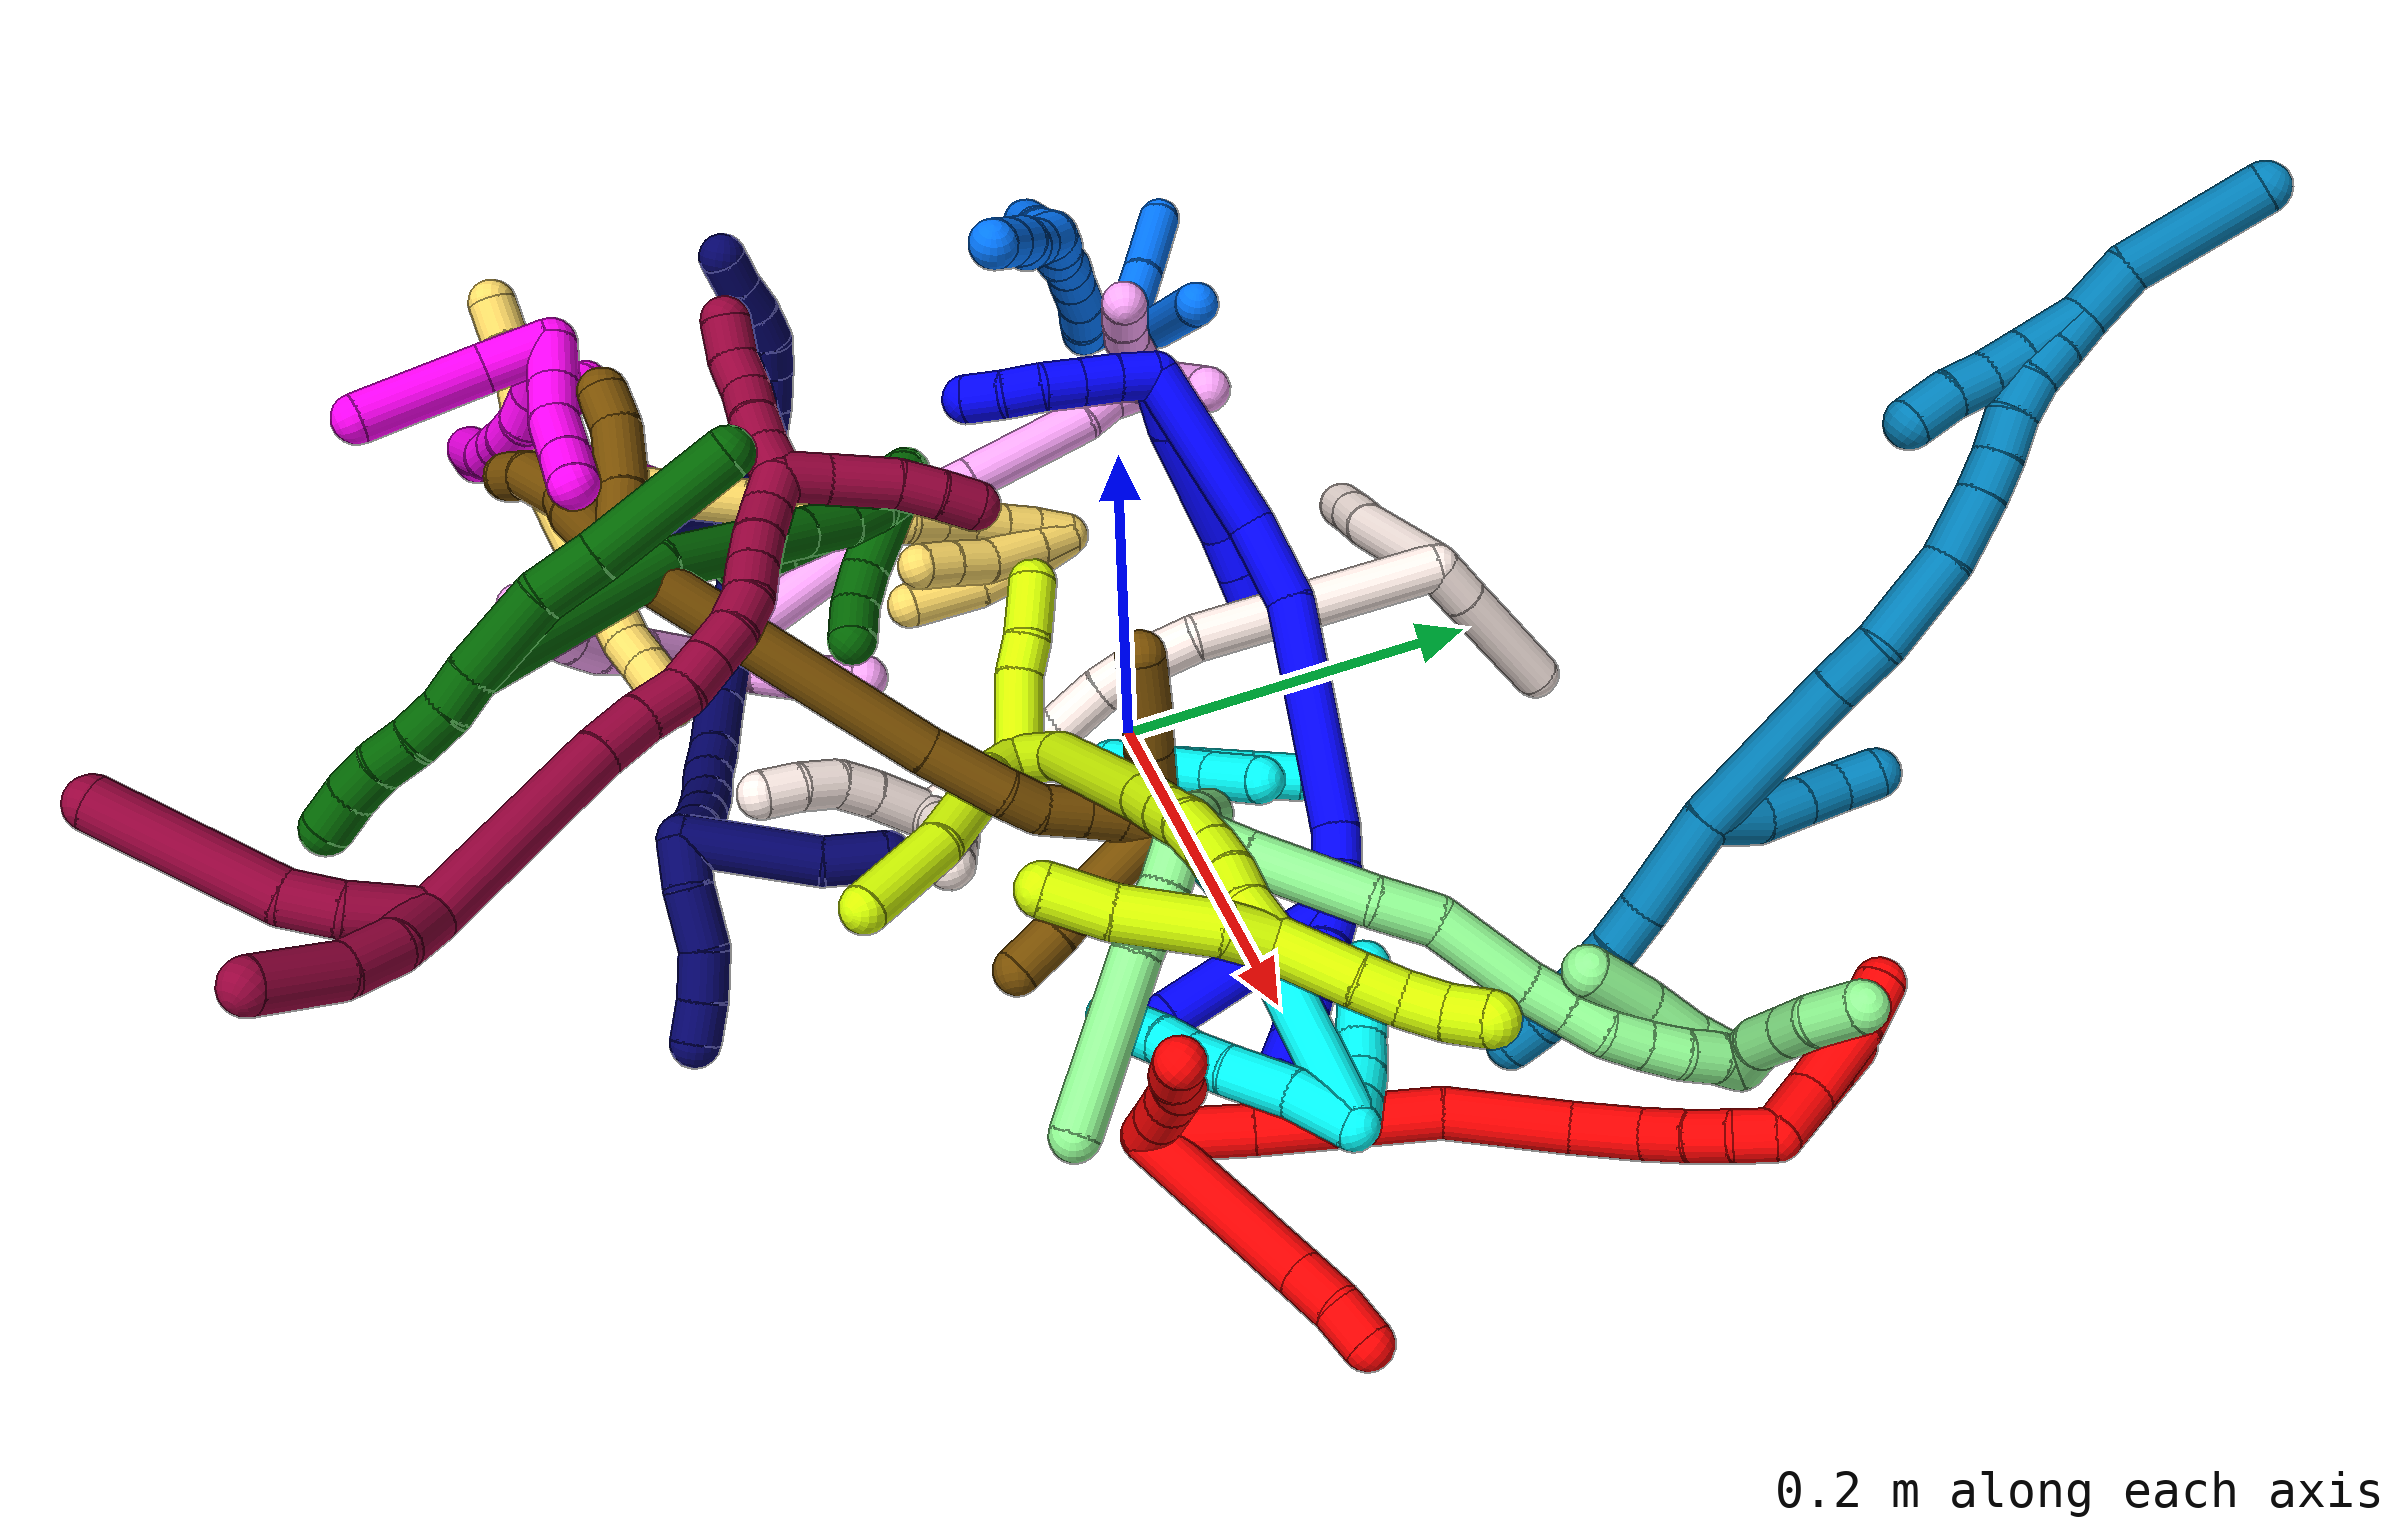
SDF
<sdf version="1.7">
 <world name="default">
  <plugin name="TubeGeneratorPlugin" filename="libtube_generator_plugin.so"/>
  <model name="photoneo_s_sensor">
   <static>1</static>
   <pose>0 0 2 1.57079 1.57079 3.14159</pose>
   <link name="link">
    <inertial><mass>0.1</mass></inertial>
    <sensor name="sensor" type="depth">
     <update_rate>30</update_rate>
     <camera>
      <horizontal_fov>1.22</horizontal_fov>
      <image><width>1920</width><height>1200</height><format>B8G8R8</format></image>
      <clip><near>0.1</near><far>4</far></clip>
      <depth_camera><output>points</output></depth_camera>
     </camera>
     <plugin name="camera_plugin" filename="libgazebo_ros_depth_camera.so">
      <baseline>0.2</baseline>
      <alwaysOn>1</alwaysOn>
      <updateRate>0.0</updateRate>
      <cameraName>camera_ir</cameraName>
      <imageTopicName>/camera/color/image_raw</imageTopicName>
      <cameraInfoTopicName>/camera/color/camera_info</cameraInfoTopicName>
      <depthImageTopicName>/camera/depth/image_raw</depthImageTopicName>
      <depthImageCameraInfoTopicName>/camera/depth/camera_info</depthImageCameraInfoTopicName>
      <pointCloudTopicName>/camera/depth/points</pointCloudTopicName>
      <frameName>fr_optical</frameName>
      <pointCloudCutoff>0.1</pointCloudCutoff>
      <pointCloudCutoffMax>2.0</pointCloudCutoffMax>
      <distortionK1>0</distortionK1>
      <distortionK2>0</distortionK2>
      <distortionK3>0</distortionK3>
      <distortionT1>0</distortionT1>
      <distortionT2>0</distortionT2>
      <CxPrime>0</CxPrime>
      <Cx>0</Cx>
      <Cy>0</Cy>
      <focalLength>0</focalLength>
      <hackBaseline>0</hackBaseline>
     </plugin>
    </sensor>
   </link>
  </model>
  <gravity>0 0 -9.8</gravity>
  <magnetic_field>6e-06 2.3e-05 -4.2e-05</magnetic_field>
  <atmosphere type="adiabatic"/>
  <physics name="default_physics" default="0" type="ode">
   <max_step_size>0.003</max_step_size>
   <real_time_factor>1</real_time_factor>
   <real_time_update_rate>1000</real_time_update_rate>
   <max_contacts>10000</max_contacts>
   <ode>
    <solver>
     <type>quick</type>
     <iters>100</iters>
     <sor>1.3</sor>
     <use_dynamic_moi_rescaling>0</use_dynamic_moi_rescaling>
    </solver>
    <constraints>
     <contact_max_correcting_vel>0</contact_max_correcting_vel>
     <contact_surface_layer>0.001</contact_surface_layer>
     <cfm>0</cfm>
     <erp>0.2</erp>
    </constraints>
   </ode>
  </physics>
  <scene><ambient>0.4 0.4 0.4 1</ambient><background>0.7 0.7 0.7 1</background><shadows>0</shadows></scene>
  <audio><device>default</device></audio>
  <spherical_coordinates>
   <surface_model>EARTH_WGS84</surface_model>
   <latitude_deg>0</latitude_deg>
   <longitude_deg>0</longitude_deg>
   <elevation>0</elevation>
   <heading_deg>0</heading_deg>
  </spherical_coordinates>
  <model name="bin">
   <static>1</static>
   <link name="bottom">
    <collision name="collision-bottom">
     <pose>0 0 -0.01 0 -0 0</pose>
     <geometry><box><size>0.8 0.6 0.02</size></box></geometry>
     <surface>
      <friction><ode><mu>100</mu><mu2>100</mu2></ode></friction>
      <contact><collide_bitmask>65535</collide_bitmask></contact>
     </surface>
    </collision>
   </link>
   <link name="west_wall">
    <collision name="collision-west_wall">
     <pose>-0.41 0 0.1 0 -0 0</pose>
     <geometry><box><size>0.02 0.6 0.2</size></box></geometry>
     <surface>
      <friction><ode><mu>100</mu><mu2>100</mu2></ode></friction>
      <contact><collide_bitmask>65535</collide_bitmask></contact>
     </surface>
    </collision>
   </link>
   <link name="east_wall">
    <collision name="collision-east_wall">
     <pose>0.41 0 0.1 0 -0 0</pose>
     <geometry><box><size>0.02 0.6 0.2</size></box></geometry>
     <surface>
      <friction><ode><mu>100</mu><mu2>100</mu2></ode></friction>
      <contact><collide_bitmask>65535</collide_bitmask></contact>
     </surface>
    </collision>
   </link>
   <link name="south_wall">
    <collision name="collision-south_wall">
     <pose>0 -0.31 0.1 0 -0 0</pose>
     <geometry><box><size>0.8 0.02 0.2</size></box></geometry>
     <surface>
      <friction><ode><mu>100</mu><mu2>100</mu2></ode></friction>
      <contact><collide_bitmask>65535</collide_bitmask></contact>
     </surface>
    </collision>
   </link>
   <link name="north_wall">
    <collision name="collision-north_wall">
     <pose>0 0.31 0.1 0 -0 0</pose>
     <geometry><box><size>0.8 0.02 0.2</size></box></geometry>
     <surface>
      <friction><ode><mu>100</mu><mu2>100</mu2></ode></friction>
      <contact><collide_bitmask>65535</collide_bitmask></contact>
     </surface>
    </collision>
   </link>
  </model>
  <model name="1">
   <static>0</static>
   <link name="1">
    <collision name="collision-cylinder-e_1_2_8">
     <pose>-0.011286 -0.001696 0.011521 0.146124 -0.769756 -0.05928</pose>
     <geometry><cylinder><radius>0.0125</radius><length>0.032433</length></cylinder></geometry>
     <surface>
      <friction><ode><mu>1.16</mu><mu2>1.16</mu2><slip1>0</slip1><slip2>0</slip2></ode></friction>
      <contact><ode><kp>1e+06</kp><kd>1</kd><max_vel>0</max_vel><min_depth>0.001</min_depth></ode></contact>
     </surface>
    </collision>
    <visual name="visual-cylinder-e_1_2_8">
     <pose>-0.011286 -0.001696 0.011521 0.146124 -0.769756 -0.05928</pose>
     <geometry><cylinder><radius>0.0125</radius><length>0.032433</length></cylinder></geometry>
     <material><ambient>0 0 1 1</ambient></material>
    </visual>
    <collision name="collision-cylinder-e_2_8_9">
     <pose>-0.04402 -0.002714 0.050615 -0.024564 -0.660946 0.008427</pose>
     <geometry><cylinder><radius>0.0125</radius><length>0.069878</length></cylinder></geometry>
     <surface>
      <friction><ode><mu>1.16</mu><mu2>1.16</mu2><slip1>0</slip1><slip2>0</slip2></ode></friction>
      <contact><ode><kp>1e+06</kp><kd>1</kd><max_vel>0</max_vel><min_depth>0.001</min_depth></ode></contact>
     </surface>
    </collision>
    <visual name="visual-cylinder-e_2_8_9">
     <pose>-0.04402 -0.002714 0.050615 -0.024564 -0.660946 0.008427</pose>
     <geometry><cylinder><radius>0.0125</radius><length>0.069878</length></cylinder></geometry>
     <material><ambient>0 0 1 1</ambient></material>
    </visual>
    <collision name="collision-cylinder-e_3_9_10">
     <pose>-0.073548 0.000962 0.08669 -0.33897 -0.730722 0.130737</pose>
     <geometry><cylinder><radius>0.0125</radius><length>0.024213</length></cylinder></geometry>
     <surface>
      <friction><ode><mu>1.16</mu><mu2>1.16</mu2><slip1>0</slip1><slip2>0</slip2></ode></friction>
      <contact><ode><kp>1e+06</kp><kd>1</kd><max_vel>0</max_vel><min_depth>0.001</min_depth></ode></contact>
     </surface>
    </collision>
    <visual name="visual-cylinder-e_3_9_10">
     <pose>-0.073548 0.000962 0.08669 -0.33897 -0.730722 0.130737</pose>
     <geometry><cylinder><radius>0.0125</radius><length>0.024213</length></cylinder></geometry>
     <material><ambient>0 0 1 1</ambient></material>
    </visual>
    <collision name="collision-cylinder-e_4_10_6">
     <pose>-0.08953 0.006777 0.103402 -0.330615 -0.738523 0.128952</pose>
     <geometry><cylinder><radius>0.0125</radius><length>0.023476</length></cylinder></geometry>
     <surface>
      <friction><ode><mu>1.16</mu><mu2>1.16</mu2><slip1>0</slip1><slip2>0</slip2></ode></friction>
      <contact><ode><kp>1e+06</kp><kd>1</kd><max_vel>0</max_vel><min_depth>0.001</min_depth></ode></contact>
     </surface>
    </collision>
    <visual name="visual-cylinder-e_4_10_6">
     <pose>-0.08953 0.006777 0.103402 -0.330615 -0.738523 0.128952</pose>
     <geometry><cylinder><radius>0.0125</radius><length>0.023476</length></cylinder></geometry>
     <material><ambient>0 0 1 1</ambient></material>
    </visual>
    <collision name="collision-cylinder-e_1_2_11">
     <pose>-0.004343 -0.001333 -0.008908 2.99311 -0.449313 -2.51226</pose>
     <geometry><cylinder><radius>0.0125</radius><length>0.02</length></cylinder></geometry>
     <surface>
      <friction><ode><mu>1.16</mu><mu2>1.16</mu2><slip1>0</slip1><slip2>0</slip2></ode></friction>
      <contact><ode><kp>1e+06</kp><kd>1</kd><max_vel>0</max_vel><min_depth>0.001</min_depth></ode></contact>
     </surface>
    </collision>
    <visual name="visual-cylinder-e_1_2_11">
     <pose>-0.004343 -0.001333 -0.008908 2.99311 -0.449313 -2.51226</pose>
     <geometry><cylinder><radius>0.0125</radius><length>0.02</length></cylinder></geometry>
     <material><ambient>0 0 1 1</ambient></material>
    </visual>
    <collision name="collision-cylinder-e_2_11_12">
     <pose>-0.013509 -0.003585 -0.026529 3.03643 -0.50318 -2.73768</pose>
     <geometry><cylinder><radius>0.0125</radius><length>0.02</length></cylinder></geometry>
     <surface>
      <friction><ode><mu>1.16</mu><mu2>1.16</mu2><slip1>0</slip1><slip2>0</slip2></ode></friction>
      <contact><ode><kp>1e+06</kp><kd>1</kd><max_vel>0</max_vel><min_depth>0.001</min_depth></ode></contact>
     </surface>
    </collision>
    <visual name="visual-cylinder-e_2_11_12">
     <pose>-0.013509 -0.003585 -0.026529 3.03643 -0.50318 -2.73768</pose>
     <geometry><cylinder><radius>0.0125</radius><length>0.02</length></cylinder></geometry>
     <material><ambient>0 0 1 1</ambient></material>
    </visual>
    <collision name="collision-cylinder-e_3_12_13">
     <pose>-0.023057 -0.005393 -0.044009 3.04055 -0.492197 -2.74432</pose>
     <geometry><cylinder><radius>0.0125</radius><length>0.02</length></cylinder></geometry>
     <surface>
      <friction><ode><mu>1.16</mu><mu2>1.16</mu2><slip1>0</slip1><slip2>0</slip2></ode></friction>
      <contact><ode><kp>1e+06</kp><kd>1</kd><max_vel>0</max_vel><min_depth>0.001</min_depth></ode></contact>
     </surface>
    </collision>
    <visual name="visual-cylinder-e_3_12_13">
     <pose>-0.023057 -0.005393 -0.044009 3.04055 -0.492197 -2.74432</pose>
     <geometry><cylinder><radius>0.0125</radius><length>0.02</length></cylinder></geometry>
     <material><ambient>0 0 1 1</ambient></material>
    </visual>
    <collision name="collision-cylinder-e_4_13_14">
     <pose>-0.033681 -0.009386 -0.060232 2.74701 -0.630823 -2.04235</pose>
     <geometry><cylinder><radius>0.0125</radius><length>0.02</length></cylinder></geometry>
     <surface>
      <friction><ode><mu>1.16</mu><mu2>1.16</mu2><slip1>0</slip1><slip2>0</slip2></ode></friction>
      <contact><ode><kp>1e+06</kp><kd>1</kd><max_vel>0</max_vel><min_depth>0.001</min_depth></ode></contact>
     </surface>
    </collision>
    <visual name="visual-cylinder-e_4_13_14">
     <pose>-0.033681 -0.009386 -0.060232 2.74701 -0.630823 -2.04235</pose>
     <geometry><cylinder><radius>0.0125</radius><length>0.02</length></cylinder></geometry>
     <material><ambient>0 0 1 1</ambient></material>
    </visual>
    <collision name="collision-cylinder-e_5_14_5">
     <pose>-0.045174 -0.017902 -0.073965 2.43027 -0.593784 -1.37794</pose>
     <geometry><cylinder><radius>0.0125</radius><length>0.02</length></cylinder></geometry>
     <surface>
      <friction><ode><mu>1.16</mu><mu2>1.16</mu2><slip1>0</slip1><slip2>0</slip2></ode></friction>
      <contact><ode><kp>1e+06</kp><kd>1</kd><max_vel>0</max_vel><min_depth>0.001</min_depth></ode></contact>
     </surface>
    </collision>
    <visual name="visual-cylinder-e_5_14_5">
     <pose>-0.045174 -0.017902 -0.073965 2.43027 -0.593784 -1.37794</pose>
     <geometry><cylinder><radius>0.0125</radius><length>0.02</length></cylinder></geometry>
     <material><ambient>0 0 1 1</ambient></material>
    </visual>
    <collision name="collision-cylinder-e_1_2_15">
     <pose>-0.02317 0.023311 0.031085 -0.643439 -0.537709 0.183151</pose>
     <geometry><cylinder><radius>0.0125</radius><length>0.090476</length></cylinder></geometry>
     <surface>
      <friction><ode><mu>1.16</mu><mu2>1.16</mu2><slip1>0</slip1><slip2>0</slip2></ode></friction>
      <contact><ode><kp>1e+06</kp><kd>1</kd><max_vel>0</max_vel><min_depth>0.001</min_depth></ode></contact>
     </surface>
    </collision>
    <visual name="visual-cylinder-e_1_2_15">
     <pose>-0.02317 0.023311 0.031085 -0.643439 -0.537709 0.183151</pose>
     <geometry><cylinder><radius>0.0125</radius><length>0.090476</length></cylinder></geometry>
     <material><ambient>0 0 1 1</ambient></material>
    </visual>
    <collision name="collision-cylinder-e_2_15_16">
     <pose>-0.058483 0.062365 0.073434 -0.949756 -0.56028 0.2937</pose>
     <geometry><cylinder><radius>0.0125</radius><length>0.045704</length></cylinder></geometry>
     <surface>
      <friction><ode><mu>1.16</mu><mu2>1.16</mu2><slip1>0</slip1><slip2>0</slip2></ode></friction>
      <contact><ode><kp>1e+06</kp><kd>1</kd><max_vel>0</max_vel><min_depth>0.001</min_depth></ode></contact>
     </surface>
    </collision>
    <visual name="visual-cylinder-e_2_15_16">
     <pose>-0.058483 0.062365 0.073434 -0.949756 -0.56028 0.2937</pose>
     <geometry><cylinder><radius>0.0125</radius><length>0.045704</length></cylinder></geometry>
     <material><ambient>0 0 1 1</ambient></material>
    </visual>
    <collision name="collision-cylinder-e_3_16_17">
     <pose>-0.111989 0.120451 0.099304 -1.23864 -0.745608 0.543796</pose>
     <geometry><cylinder><radius>0.0125</radius><length>0.121935</length></cylinder></geometry>
     <surface>
      <friction><ode><mu>1.16</mu><mu2>1.16</mu2><slip1>0</slip1><slip2>0</slip2></ode></friction>
      <contact><ode><kp>1e+06</kp><kd>1</kd><max_vel>0</max_vel><min_depth>0.001</min_depth></ode></contact>
     </surface>
    </collision>
    <visual name="visual-cylinder-e_3_16_17">
     <pose>-0.111989 0.120451 0.099304 -1.23864 -0.745608 0.543796</pose>
     <geometry><cylinder><radius>0.0125</radius><length>0.121935</length></cylinder></geometry>
     <material><ambient>0 0 1 1</ambient></material>
    </visual>
    <collision name="collision-cylinder-e_4_17_18">
     <pose>-0.160521 0.169857 0.114437 -1.49625 -0.791593 0.739894</pose>
     <geometry><cylinder><radius>0.0125</radius><length>0.020158</length></cylinder></geometry>
     <surface>
      <friction><ode><mu>1.16</mu><mu2>1.16</mu2><slip1>0</slip1><slip2>0</slip2></ode></friction>
      <contact><ode><kp>1e+06</kp><kd>1</kd><max_vel>0</max_vel><min_depth>0.001</min_depth></ode></contact>
     </surface>
    </collision>
    <visual name="visual-cylinder-e_4_17_18">
     <pose>-0.160521 0.169857 0.114437 -1.49625 -0.791593 0.739894</pose>
     <geometry><cylinder><radius>0.0125</radius><length>0.020158</length></cylinder></geometry>
     <material><ambient>0 0 1 1</ambient></material>
    </visual>
    <collision name="collision-cylinder-e_5_18_1">
     <pose>-0.177236 0.181692 0.117002 -1.16726 -1.07285 0.748289</pose>
     <geometry><cylinder><radius>0.0125</radius><length>0.021726</length></cylinder></geometry>
     <surface>
      <friction><ode><mu>1.16</mu><mu2>1.16</mu2><slip1>0</slip1><slip2>0</slip2></ode></friction>
      <contact><ode><kp>1e+06</kp><kd>1</kd><max_vel>0</max_vel><min_depth>0.001</min_depth></ode></contact>
     </surface>
    </collision>
    <visual name="visual-cylinder-e_5_18_1">
     <pose>-0.177236 0.181692 0.117002 -1.16726 -1.07285 0.748289</pose>
     <geometry><cylinder><radius>0.0125</radius><length>0.021726</length></cylinder></geometry>
     <material><ambient>0 0 1 1</ambient></material>
    </visual>
    <collision name="collision-cylinder-e_1_1_19">
     <pose>-0.192736 0.193742 0.115639 -2.00788 -0.63791 0.957125</pose>
     <geometry><cylinder><radius>0.0125</radius><length>0.02</length></cylinder></geometry>
     <surface>
      <friction><ode><mu>1.16</mu><mu2>1.16</mu2><slip1>0</slip1><slip2>0</slip2></ode></friction>
      <contact><ode><kp>1e+06</kp><kd>1</kd><max_vel>0</max_vel><min_depth>0.001</min_depth></ode></contact>
     </surface>
    </collision>
    <visual name="visual-cylinder-e_1_1_19">
     <pose>-0.192736 0.193742 0.115639 -2.00788 -0.63791 0.957125</pose>
     <geometry><cylinder><radius>0.0125</radius><length>0.02</length></cylinder></geometry>
     <material><ambient>0 0 1 1</ambient></material>
    </visual>
    <collision name="collision-cylinder-e_2_19_20">
     <pose>-0.205264 0.207603 0.108568 -2.07946 -0.717191 1.13596</pose>
     <geometry><cylinder><radius>0.0125</radius><length>0.02</length></cylinder></geometry>
     <surface>
      <friction><ode><mu>1.16</mu><mu2>1.16</mu2><slip1>0</slip1><slip2>0</slip2></ode></friction>
      <contact><ode><kp>1e+06</kp><kd>1</kd><max_vel>0</max_vel><min_depth>0.001</min_depth></ode></contact>
     </surface>
    </collision>
    <visual name="visual-cylinder-e_2_19_20">
     <pose>-0.205264 0.207603 0.108568 -2.07946 -0.717191 1.13596</pose>
     <geometry><cylinder><radius>0.0125</radius><length>0.02</length></cylinder></geometry>
     <material><ambient>0 0 1 1</ambient></material>
    </visual>
    <collision name="collision-cylinder-e_3_20_21">
     <pose>-0.218823 0.220869 0.102345 -1.93565 -0.77351 1.06833</pose>
     <geometry><cylinder><radius>0.0125</radius><length>0.02</length></cylinder></geometry>
     <surface>
      <friction><ode><mu>1.16</mu><mu2>1.16</mu2><slip1>0</slip1><slip2>0</slip2></ode></friction>
      <contact><ode><kp>1e+06</kp><kd>1</kd><max_vel>0</max_vel><min_depth>0.001</min_depth></ode></contact>
     </surface>
    </collision>
    <visual name="visual-cylinder-e_3_20_21">
     <pose>-0.218823 0.220869 0.102345 -1.93565 -0.77351 1.06833</pose>
     <geometry><cylinder><radius>0.0125</radius><length>0.02</length></cylinder></geometry>
     <material><ambient>0 0 1 1</ambient></material>
    </visual>
    <collision name="collision-cylinder-e_4_21_22">
     <pose>-0.231905 0.234493 0.095962 -2.07501 -0.655551 1.04517</pose>
     <geometry><cylinder><radius>0.0125</radius><length>0.02</length></cylinder></geometry>
     <surface>
      <friction><ode><mu>1.16</mu><mu2>1.16</mu2><slip1>0</slip1><slip2>0</slip2></ode></friction>
      <contact><ode><kp>1e+06</kp><kd>1</kd><max_vel>0</max_vel><min_depth>0.001</min_depth></ode></contact>
     </surface>
    </collision>
    <visual name="visual-cylinder-e_4_21_22">
     <pose>-0.231905 0.234493 0.095962 -2.07501 -0.655551 1.04517</pose>
     <geometry><cylinder><radius>0.0125</radius><length>0.02</length></cylinder></geometry>
     <material><ambient>0 0 1 1</ambient></material>
    </visual>
    <collision name="collision-cylinder-e_5_22_4">
     <pose>-0.24386 0.248375 0.08795 -2.11304 -0.626 1.0404</pose>
     <geometry><cylinder><radius>0.0125</radius><length>0.02</length></cylinder></geometry>
     <surface>
      <friction><ode><mu>1.16</mu><mu2>1.16</mu2><slip1>0</slip1><slip2>0</slip2></ode></friction>
      <contact><ode><kp>1e+06</kp><kd>1</kd><max_vel>0</max_vel><min_depth>0.001</min_depth></ode></contact>
     </surface>
    </collision>
    <visual name="visual-cylinder-e_5_22_4">
     <pose>-0.24386 0.248375 0.08795 -2.11304 -0.626 1.0404</pose>
     <geometry><cylinder><radius>0.0125</radius><length>0.02</length></cylinder></geometry>
     <material><ambient>0 0 1 1</ambient></material>
    </visual>
    <collision name="collision-cylinder-e_1_1_23">
     <pose>-0.198606 0.187703 0.107738 -3.03239 -0.805049 2.88624</pose>
     <geometry><cylinder><radius>0.0125</radius><length>0.032808</length></cylinder></geometry>
     <surface>
      <friction><ode><mu>1.16</mu><mu2>1.16</mu2><slip1>0</slip1><slip2>0</slip2></ode></friction>
      <contact><ode><kp>1e+06</kp><kd>1</kd><max_vel>0</max_vel><min_depth>0.001</min_depth></ode></contact>
     </surface>
    </collision>
    <visual name="visual-cylinder-e_1_1_23">
     <pose>-0.198606 0.187703 0.107738 -3.03239 -0.805049 2.88624</pose>
     <geometry><cylinder><radius>0.0125</radius><length>0.032808</length></cylinder></geometry>
     <material><ambient>0 0 1 1</ambient></material>
    </visual>
    <collision name="collision-cylinder-e_2_23_3">
     <pose>-0.234494 0.193089 0.073361 -2.96377 -0.798412 2.72507</pose>
     <geometry><cylinder><radius>0.0125</radius><length>0.067192</length></cylinder></geometry>
     <surface>
      <friction><ode><mu>1.16</mu><mu2>1.16</mu2><slip1>0</slip1><slip2>0</slip2></ode></friction>
      <contact><ode><kp>1e+06</kp><kd>1</kd><max_vel>0</max_vel><min_depth>0.001</min_depth></ode></contact>
     </surface>
    </collision>
    <visual name="visual-cylinder-e_2_23_3">
     <pose>-0.234494 0.193089 0.073361 -2.96377 -0.798412 2.72507</pose>
     <geometry><cylinder><radius>0.0125</radius><length>0.067192</length></cylinder></geometry>
     <material><ambient>0 0 1 1</ambient></material>
    </visual>
    <collision name="collision-sphere-3">
     <pose>-0.258557 0.197237 0.050286 0 -0 0</pose>
     <geometry><sphere><radius>0.0125</radius></sphere></geometry>
     <surface>
      <friction><ode><mu>1.16</mu><mu2>1.16</mu2><slip1>0</slip1><slip2>0</slip2></ode></friction>
      <contact><ode><kp>1e+06</kp><kd>1</kd><max_vel>0</max_vel><min_depth>0.001</min_depth></ode></contact>
     </surface>
    </collision>
    <visual name="visual-sphere-3">
     <pose>-0.258557 0.197237 0.050286 0 -0 0</pose>
     <geometry><sphere><radius>0.0125</radius></sphere></geometry>
     <material><ambient>0 0 1 1</ambient></material>
    </visual>
    <collision name="collision-sphere-23">
     <pose>-0.210431 0.188942 0.096437 0 -0 0</pose>
     <geometry><sphere><radius>0.0125</radius></sphere></geometry>
     <surface>
      <friction><ode><mu>1.16</mu><mu2>1.16</mu2><slip1>0</slip1><slip2>0</slip2></ode></friction>
      <contact><ode><kp>1e+06</kp><kd>1</kd><max_vel>0</max_vel><min_depth>0.001</min_depth></ode></contact>
     </surface>
    </collision>
    <visual name="visual-sphere-23">
     <pose>-0.210431 0.188942 0.096437 0 -0 0</pose>
     <geometry><sphere><radius>0.0125</radius></sphere></geometry>
     <material><ambient>0 0 1 1</ambient></material>
    </visual>
    <collision name="collision-sphere-4">
     <pose>-0.249719 0.255316 0.083768 0 -0 0</pose>
     <geometry><sphere><radius>0.0125</radius></sphere></geometry>
     <surface>
      <friction><ode><mu>1.16</mu><mu2>1.16</mu2><slip1>0</slip1><slip2>0</slip2></ode></friction>
      <contact><ode><kp>1e+06</kp><kd>1</kd><max_vel>0</max_vel><min_depth>0.001</min_depth></ode></contact>
     </surface>
    </collision>
    <visual name="visual-sphere-4">
     <pose>-0.249719 0.255316 0.083768 0 -0 0</pose>
     <geometry><sphere><radius>0.0125</radius></sphere></geometry>
     <material><ambient>0 0 1 1</ambient></material>
    </visual>
    <collision name="collision-sphere-22">
     <pose>-0.238001 0.241434 0.092132 0 -0 0</pose>
     <geometry><sphere><radius>0.0125</radius></sphere></geometry>
     <surface>
      <friction><ode><mu>1.16</mu><mu2>1.16</mu2><slip1>0</slip1><slip2>0</slip2></ode></friction>
      <contact><ode><kp>1e+06</kp><kd>1</kd><max_vel>0</max_vel><min_depth>0.001</min_depth></ode></contact>
     </surface>
    </collision>
    <visual name="visual-sphere-22">
     <pose>-0.238001 0.241434 0.092132 0 -0 0</pose>
     <geometry><sphere><radius>0.0125</radius></sphere></geometry>
     <material><ambient>0 0 1 1</ambient></material>
    </visual>
    <collision name="collision-sphere-21">
     <pose>-0.225809 0.227553 0.099792 0 -0 0</pose>
     <geometry><sphere><radius>0.0125</radius></sphere></geometry>
     <surface>
      <friction><ode><mu>1.16</mu><mu2>1.16</mu2><slip1>0</slip1><slip2>0</slip2></ode></friction>
      <contact><ode><kp>1e+06</kp><kd>1</kd><max_vel>0</max_vel><min_depth>0.001</min_depth></ode></contact>
     </surface>
    </collision>
    <visual name="visual-sphere-21">
     <pose>-0.225809 0.227553 0.099792 0 -0 0</pose>
     <geometry><sphere><radius>0.0125</radius></sphere></geometry>
     <material><ambient>0 0 1 1</ambient></material>
    </visual>
    <collision name="collision-sphere-20">
     <pose>-0.211836 0.214185 0.104898 0 -0 0</pose>
     <geometry><sphere><radius>0.0125</radius></sphere></geometry>
     <surface>
      <friction><ode><mu>1.16</mu><mu2>1.16</mu2><slip1>0</slip1><slip2>0</slip2></ode></friction>
      <contact><ode><kp>1e+06</kp><kd>1</kd><max_vel>0</max_vel><min_depth>0.001</min_depth></ode></contact>
     </surface>
    </collision>
    <visual name="visual-sphere-20">
     <pose>-0.211836 0.214185 0.104898 0 -0 0</pose>
     <geometry><sphere><radius>0.0125</radius></sphere></geometry>
     <material><ambient>0 0 1 1</ambient></material>
    </visual>
    <collision name="collision-sphere-11">
     <pose>-0.008687 -0.002665 -0.017817 0 -0 0</pose>
     <geometry><sphere><radius>0.0125</radius></sphere></geometry>
     <surface>
      <friction><ode><mu>1.16</mu><mu2>1.16</mu2><slip1>0</slip1><slip2>0</slip2></ode></friction>
      <contact><ode><kp>1e+06</kp><kd>1</kd><max_vel>0</max_vel><min_depth>0.001</min_depth></ode></contact>
     </surface>
    </collision>
    <visual name="visual-sphere-11">
     <pose>-0.008687 -0.002665 -0.017817 0 -0 0</pose>
     <geometry><sphere><radius>0.0125</radius></sphere></geometry>
     <material><ambient>0 0 1 1</ambient></material>
    </visual>
    <collision name="collision-sphere-6">
     <pose>-0.097432 0.009595 0.111612 0 -0 0</pose>
     <geometry><sphere><radius>0.0125</radius></sphere></geometry>
     <surface>
      <friction><ode><mu>1.16</mu><mu2>1.16</mu2><slip1>0</slip1><slip2>0</slip2></ode></friction>
      <contact><ode><kp>1e+06</kp><kd>1</kd><max_vel>0</max_vel><min_depth>0.001</min_depth></ode></contact>
     </surface>
    </collision>
    <visual name="visual-sphere-6">
     <pose>-0.097432 0.009595 0.111612 0 -0 0</pose>
     <geometry><sphere><radius>0.0125</radius></sphere></geometry>
     <material><ambient>0 0 1 1</ambient></material>
    </visual>
    <collision name="collision-sphere-10">
     <pose>-0.081628 0.003959 0.095193 0 -0 0</pose>
     <geometry><sphere><radius>0.0125</radius></sphere></geometry>
     <surface>
      <friction><ode><mu>1.16</mu><mu2>1.16</mu2><slip1>0</slip1><slip2>0</slip2></ode></friction>
      <contact><ode><kp>1e+06</kp><kd>1</kd><max_vel>0</max_vel><min_depth>0.001</min_depth></ode></contact>
     </surface>
    </collision>
    <visual name="visual-sphere-10">
     <pose>-0.081628 0.003959 0.095193 0 -0 0</pose>
     <geometry><sphere><radius>0.0125</radius></sphere></geometry>
     <material><ambient>0 0 1 1</ambient></material>
    </visual>
    <collision name="collision-sphere-9">
     <pose>-0.065468 -0.002036 0.078188 0 -0 0</pose>
     <geometry><sphere><radius>0.0125</radius></sphere></geometry>
     <surface>
      <friction><ode><mu>1.16</mu><mu2>1.16</mu2><slip1>0</slip1><slip2>0</slip2></ode></friction>
      <contact><ode><kp>1e+06</kp><kd>1</kd><max_vel>0</max_vel><min_depth>0.001</min_depth></ode></contact>
     </surface>
    </collision>
    <visual name="visual-sphere-9">
     <pose>-0.065468 -0.002036 0.078188 0 -0 0</pose>
     <geometry><sphere><radius>0.0125</radius></sphere></geometry>
     <material><ambient>0 0 1 1</ambient></material>
    </visual>
    <collision name="collision-sphere-2">
     <geometry><sphere><radius>0.0125</radius></sphere></geometry>
     <surface>
      <friction><ode><mu>1.16</mu><mu2>1.16</mu2><slip1>0</slip1><slip2>0</slip2></ode></friction>
      <contact><ode><kp>1e+06</kp><kd>1</kd><max_vel>0</max_vel><min_depth>0.001</min_depth></ode></contact>
     </surface>
    </collision>
    <visual name="visual-sphere-2">
     <geometry><sphere><radius>0.0125</radius></sphere></geometry>
     <material><ambient>0 0 1 1</ambient></material>
    </visual>
    <collision name="collision-sphere-19">
     <pose>-0.198691 0.20102 0.112238 0 -0 0</pose>
     <geometry><sphere><radius>0.0125</radius></sphere></geometry>
     <surface>
      <friction><ode><mu>1.16</mu><mu2>1.16</mu2><slip1>0</slip1><slip2>0</slip2></ode></friction>
      <contact><ode><kp>1e+06</kp><kd>1</kd><max_vel>0</max_vel><min_depth>0.001</min_depth></ode></contact>
     </surface>
    </collision>
    <visual name="visual-sphere-19">
     <pose>-0.198691 0.20102 0.112238 0 -0 0</pose>
     <geometry><sphere><radius>0.0125</radius></sphere></geometry>
     <material><ambient>0 0 1 1</ambient></material>
    </visual>
    <collision name="collision-sphere-8">
     <pose>-0.022572 -0.003391 0.023042 0 -0 0</pose>
     <geometry><sphere><radius>0.0125</radius></sphere></geometry>
     <surface>
      <friction><ode><mu>1.16</mu><mu2>1.16</mu2><slip1>0</slip1><slip2>0</slip2></ode></friction>
      <contact><ode><kp>1e+06</kp><kd>1</kd><max_vel>0</max_vel><min_depth>0.001</min_depth></ode></contact>
     </surface>
    </collision>
    <visual name="visual-sphere-8">
     <pose>-0.022572 -0.003391 0.023042 0 -0 0</pose>
     <geometry><sphere><radius>0.0125</radius></sphere></geometry>
     <material><ambient>0 0 1 1</ambient></material>
    </visual>
    <collision name="collision-sphere-12">
     <pose>-0.018331 -0.004504 -0.035241 0 -0 0</pose>
     <geometry><sphere><radius>0.0125</radius></sphere></geometry>
     <surface>
      <friction><ode><mu>1.16</mu><mu2>1.16</mu2><slip1>0</slip1><slip2>0</slip2></ode></friction>
      <contact><ode><kp>1e+06</kp><kd>1</kd><max_vel>0</max_vel><min_depth>0.001</min_depth></ode></contact>
     </surface>
    </collision>
    <visual name="visual-sphere-12">
     <pose>-0.018331 -0.004504 -0.035241 0 -0 0</pose>
     <geometry><sphere><radius>0.0125</radius></sphere></geometry>
     <material><ambient>0 0 1 1</ambient></material>
    </visual>
    <collision name="collision-sphere-13">
     <pose>-0.027782 -0.006282 -0.052777 0 -0 0</pose>
     <geometry><sphere><radius>0.0125</radius></sphere></geometry>
     <surface>
      <friction><ode><mu>1.16</mu><mu2>1.16</mu2><slip1>0</slip1><slip2>0</slip2></ode></friction>
      <contact><ode><kp>1e+06</kp><kd>1</kd><max_vel>0</max_vel><min_depth>0.001</min_depth></ode></contact>
     </surface>
    </collision>
    <visual name="visual-sphere-13">
     <pose>-0.027782 -0.006282 -0.052777 0 -0 0</pose>
     <geometry><sphere><radius>0.0125</radius></sphere></geometry>
     <material><ambient>0 0 1 1</ambient></material>
    </visual>
    <collision name="collision-sphere-14">
     <pose>-0.039579 -0.012491 -0.067687 0 -0 0</pose>
     <geometry><sphere><radius>0.0125</radius></sphere></geometry>
     <surface>
      <friction><ode><mu>1.16</mu><mu2>1.16</mu2><slip1>0</slip1><slip2>0</slip2></ode></friction>
      <contact><ode><kp>1e+06</kp><kd>1</kd><max_vel>0</max_vel><min_depth>0.001</min_depth></ode></contact>
     </surface>
    </collision>
    <visual name="visual-sphere-14">
     <pose>-0.039579 -0.012491 -0.067687 0 -0 0</pose>
     <geometry><sphere><radius>0.0125</radius></sphere></geometry>
     <material><ambient>0 0 1 1</ambient></material>
    </visual>
    <collision name="collision-sphere-5">
     <pose>-0.050769 -0.023313 -0.080244 0 -0 0</pose>
     <geometry><sphere><radius>0.0125</radius></sphere></geometry>
     <surface>
      <friction><ode><mu>1.16</mu><mu2>1.16</mu2><slip1>0</slip1><slip2>0</slip2></ode></friction>
      <contact><ode><kp>1e+06</kp><kd>1</kd><max_vel>0</max_vel><min_depth>0.001</min_depth></ode></contact>
     </surface>
    </collision>
    <visual name="visual-sphere-5">
     <pose>-0.050769 -0.023313 -0.080244 0 -0 0</pose>
     <geometry><sphere><radius>0.0125</radius></sphere></geometry>
     <material><ambient>0 0 1 1</ambient></material>
    </visual>
    <collision name="collision-sphere-15">
     <pose>-0.046339 0.046621 0.06217 0 -0 0</pose>
     <geometry><sphere><radius>0.0125</radius></sphere></geometry>
     <surface>
      <friction><ode><mu>1.16</mu><mu2>1.16</mu2><slip1>0</slip1><slip2>0</slip2></ode></friction>
      <contact><ode><kp>1e+06</kp><kd>1</kd><max_vel>0</max_vel><min_depth>0.001</min_depth></ode></contact>
     </surface>
    </collision>
    <visual name="visual-sphere-15">
     <pose>-0.046339 0.046621 0.06217 0 -0 0</pose>
     <geometry><sphere><radius>0.0125</radius></sphere></geometry>
     <material><ambient>0 0 1 1</ambient></material>
    </visual>
    <collision name="collision-sphere-16">
     <pose>-0.070627 0.078108 0.084698 0 -0 0</pose>
     <geometry><sphere><radius>0.0125</radius></sphere></geometry>
     <surface>
      <friction><ode><mu>1.16</mu><mu2>1.16</mu2><slip1>0</slip1><slip2>0</slip2></ode></friction>
      <contact><ode><kp>1e+06</kp><kd>1</kd><max_vel>0</max_vel><min_depth>0.001</min_depth></ode></contact>
     </surface>
    </collision>
    <visual name="visual-sphere-16">
     <pose>-0.070627 0.078108 0.084698 0 -0 0</pose>
     <geometry><sphere><radius>0.0125</radius></sphere></geometry>
     <material><ambient>0 0 1 1</ambient></material>
    </visual>
    <collision name="collision-sphere-17">
     <pose>-0.15335 0.162794 0.113909 0 -0 0</pose>
     <geometry><sphere><radius>0.0125</radius></sphere></geometry>
     <surface>
      <friction><ode><mu>1.16</mu><mu2>1.16</mu2><slip1>0</slip1><slip2>0</slip2></ode></friction>
      <contact><ode><kp>1e+06</kp><kd>1</kd><max_vel>0</max_vel><min_depth>0.001</min_depth></ode></contact>
     </surface>
    </collision>
    <visual name="visual-sphere-17">
     <pose>-0.15335 0.162794 0.113909 0 -0 0</pose>
     <geometry><sphere><radius>0.0125</radius></sphere></geometry>
     <material><ambient>0 0 1 1</ambient></material>
    </visual>
    <collision name="collision-sphere-18">
     <pose>-0.167692 0.17692 0.114965 0 -0 0</pose>
     <geometry><sphere><radius>0.0125</radius></sphere></geometry>
     <surface>
      <friction><ode><mu>1.16</mu><mu2>1.16</mu2><slip1>0</slip1><slip2>0</slip2></ode></friction>
      <contact><ode><kp>1e+06</kp><kd>1</kd><max_vel>0</max_vel><min_depth>0.001</min_depth></ode></contact>
     </surface>
    </collision>
    <visual name="visual-sphere-18">
     <pose>-0.167692 0.17692 0.114965 0 -0 0</pose>
     <geometry><sphere><radius>0.0125</radius></sphere></geometry>
     <material><ambient>0 0 1 1</ambient></material>
    </visual>
    <collision name="collision-sphere-1">
     <pose>-0.18678 0.186464 0.119039 0 -0 0</pose>
     <geometry><sphere><radius>0.0125</radius></sphere></geometry>
     <surface>
      <friction><ode><mu>1.16</mu><mu2>1.16</mu2><slip1>0</slip1><slip2>0</slip2></ode></friction>
      <contact><ode><kp>1e+06</kp><kd>1</kd><max_vel>0</max_vel><min_depth>0.001</min_depth></ode></contact>
     </surface>
    </collision>
    <visual name="visual-sphere-1">
     <pose>-0.18678 0.186464 0.119039 0 -0 0</pose>
     <geometry><sphere><radius>0.0125</radius></sphere></geometry>
     <material><ambient>0 0 1 1</ambient></material>
    </visual>
    <inertial>
     <pose>-0.105806 0.089917 0.061285 0 -0 0</pose>
     <mass>0.75</mass>
     <inertia>
      <ixx>0.000218</ixx>
      <ixy>0</ixy>
      <ixz>0</ixz>
      <iyy>0.000339</iyy>
      <iyz>0</iyz>
      <izz>4.8e-05</izz>
     </inertia>
    </inertial>
   </link>
   <pose>-0.067095 0.046605 0.183625 2.64466 -0.870807 1.99885</pose>
  </model>
  <model name="2">
   <static>0</static>
   <link name="2">
    <collision name="collision-cylinder-e_1_2_8">
     <pose>-0.030918 0.006807 0.041382 -0.16303 -0.635274 0.053705</pose>
     <geometry><cylinder><radius>0.0125</radius><length>0.104206</length></cylinder></geometry>
     <surface>
      <friction><ode><mu>1.16</mu><mu2>1.16</mu2><slip1>0</slip1><slip2>0</slip2></ode></friction>
      <contact><ode><kp>1e+06</kp><kd>1</kd><max_vel>0</max_vel><min_depth>0.001</min_depth></ode></contact>
     </surface>
    </collision>
    <visual name="visual-cylinder-e_1_2_8">
     <pose>-0.030918 0.006807 0.041382 -0.16303 -0.635274 0.053705</pose>
     <geometry><cylinder><radius>0.0125</radius><length>0.104206</length></cylinder></geometry>
     <material><ambient>1 0 0 1</ambient></material>
    </visual>
    <collision name="collision-cylinder-e_2_8_9">
     <pose>-0.069549 0.015231 0.0919 -0.175206 -0.693532 0.063455</pose>
     <geometry><cylinder><radius>0.0125</radius><length>0.02413</length></cylinder></geometry>
     <surface>
      <friction><ode><mu>1.16</mu><mu2>1.16</mu2><slip1>0</slip1><slip2>0</slip2></ode></friction>
      <contact><ode><kp>1e+06</kp><kd>1</kd><max_vel>0</max_vel><min_depth>0.001</min_depth></ode></contact>
     </surface>
    </collision>
    <visual name="visual-cylinder-e_2_8_9">
     <pose>-0.069549 0.015231 0.0919 -0.175206 -0.693532 0.063455</pose>
     <geometry><cylinder><radius>0.0125</radius><length>0.02413</length></cylinder></geometry>
     <material><ambient>1 0 0 1</ambient></material>
    </visual>
    <collision name="collision-cylinder-e_3_9_6">
     <pose>-0.082674 0.016437 0.11041 0.043826 -0.52329 -0.011738</pose>
     <geometry><cylinder><radius>0.0125</radius><length>0.021663</length></cylinder></geometry>
     <surface>
      <friction><ode><mu>1.16</mu><mu2>1.16</mu2><slip1>0</slip1><slip2>0</slip2></ode></friction>
      <contact><ode><kp>1e+06</kp><kd>1</kd><max_vel>0</max_vel><min_depth>0.001</min_depth></ode></contact>
     </surface>
    </collision>
    <visual name="visual-cylinder-e_3_9_6">
     <pose>-0.082674 0.016437 0.11041 0.043826 -0.52329 -0.011738</pose>
     <geometry><cylinder><radius>0.0125</radius><length>0.021663</length></cylinder></geometry>
     <material><ambient>1 0 0 1</ambient></material>
    </visual>
    <collision name="collision-cylinder-e_1_2_10">
     <pose>-0.007071 0.006709 -0.002234 -1.89219 -0.785433 1.04292</pose>
     <geometry><cylinder><radius>0.0125</radius><length>0.02</length></cylinder></geometry>
     <surface>
      <friction><ode><mu>1.16</mu><mu2>1.16</mu2><slip1>0</slip1><slip2>0</slip2></ode></friction>
      <contact><ode><kp>1e+06</kp><kd>1</kd><max_vel>0</max_vel><min_depth>0.001</min_depth></ode></contact>
     </surface>
    </collision>
    <visual name="visual-cylinder-e_1_2_10">
     <pose>-0.007071 0.006709 -0.002234 -1.89219 -0.785433 1.04292</pose>
     <geometry><cylinder><radius>0.0125</radius><length>0.02</length></cylinder></geometry>
     <material><ambient>1 0 0 1</ambient></material>
    </visual>
    <collision name="collision-cylinder-e_2_10_11">
     <pose>-0.02132 0.01995 -0.00688 -1.92455 -0.800491 1.09146</pose>
     <geometry><cylinder><radius>0.0125</radius><length>0.02</length></cylinder></geometry>
     <surface>
      <friction><ode><mu>1.16</mu><mu2>1.16</mu2><slip1>0</slip1><slip2>0</slip2></ode></friction>
      <contact><ode><kp>1e+06</kp><kd>1</kd><max_vel>0</max_vel><min_depth>0.001</min_depth></ode></contact>
     </surface>
    </collision>
    <visual name="visual-cylinder-e_2_10_11">
     <pose>-0.02132 0.01995 -0.00688 -1.92455 -0.800491 1.09146</pose>
     <geometry><cylinder><radius>0.0125</radius><length>0.02</length></cylinder></geometry>
     <material><ambient>1 0 0 1</ambient></material>
    </visual>
    <collision name="collision-cylinder-e_3_11_12">
     <pose>-0.036441 0.032143 -0.011494 -1.94189 -0.918011 1.25149</pose>
     <geometry><cylinder><radius>0.0125</radius><length>0.02</length></cylinder></geometry>
     <surface>
      <friction><ode><mu>1.16</mu><mu2>1.16</mu2><slip1>0</slip1><slip2>0</slip2></ode></friction>
      <contact><ode><kp>1e+06</kp><kd>1</kd><max_vel>0</max_vel><min_depth>0.001</min_depth></ode></contact>
     </surface>
    </collision>
    <visual name="visual-cylinder-e_3_11_12">
     <pose>-0.036441 0.032143 -0.011494 -1.94189 -0.918011 1.25149</pose>
     <geometry><cylinder><radius>0.0125</radius><length>0.02</length></cylinder></geometry>
     <material><ambient>1 0 0 1</ambient></material>
    </visual>
    <collision name="collision-cylinder-e_4_12_13">
     <pose>-0.052817 0.040867 -0.018114 -2.53507 -1.00328 2.10461</pose>
     <geometry><cylinder><radius>0.0125</radius><length>0.02</length></cylinder></geometry>
     <surface>
      <friction><ode><mu>1.16</mu><mu2>1.16</mu2><slip1>0</slip1><slip2>0</slip2></ode></friction>
      <contact><ode><kp>1e+06</kp><kd>1</kd><max_vel>0</max_vel><min_depth>0.001</min_depth></ode></contact>
     </surface>
    </collision>
    <visual name="visual-cylinder-e_4_12_13">
     <pose>-0.052817 0.040867 -0.018114 -2.53507 -1.00328 2.10461</pose>
     <geometry><cylinder><radius>0.0125</radius><length>0.02</length></cylinder></geometry>
     <material><ambient>1 0 0 1</ambient></material>
    </visual>
    <collision name="collision-cylinder-e_5_13_5">
     <pose>-0.069389 0.048814 -0.025676 -2.14312 -0.951031 1.51349</pose>
     <geometry><cylinder><radius>0.0125</radius><length>0.02</length></cylinder></geometry>
     <surface>
      <friction><ode><mu>1.16</mu><mu2>1.16</mu2><slip1>0</slip1><slip2>0</slip2></ode></friction>
      <contact><ode><kp>1e+06</kp><kd>1</kd><max_vel>0</max_vel><min_depth>0.001</min_depth></ode></contact>
     </surface>
    </collision>
    <visual name="visual-cylinder-e_5_13_5">
     <pose>-0.069389 0.048814 -0.025676 -2.14312 -0.951031 1.51349</pose>
     <geometry><cylinder><radius>0.0125</radius><length>0.02</length></cylinder></geometry>
     <material><ambient>1 0 0 1</ambient></material>
    </visual>
    <collision name="collision-cylinder-e_1_2_14">
     <pose>-0.000129 0.018304 0.017956 -0.794984 -0.005021 0.002108</pose>
     <geometry><cylinder><radius>0.0125</radius><length>0.051282</length></cylinder></geometry>
     <surface>
      <friction><ode><mu>1.16</mu><mu2>1.16</mu2><slip1>0</slip1><slip2>0</slip2></ode></friction>
      <contact><ode><kp>1e+06</kp><kd>1</kd><max_vel>0</max_vel><min_depth>0.001</min_depth></ode></contact>
     </surface>
    </collision>
    <visual name="visual-cylinder-e_1_2_14">
     <pose>-0.000129 0.018304 0.017956 -0.794984 -0.005021 0.002108</pose>
     <geometry><cylinder><radius>0.0125</radius><length>0.051282</length></cylinder></geometry>
     <material><ambient>1 0 0 1</ambient></material>
    </visual>
    <collision name="collision-cylinder-e_2_14_15">
     <pose>-0.000666 0.069634 0.066001 -0.83192 -0.00914 0.004038</pose>
     <geometry><cylinder><radius>0.0125</radius><length>0.08936</length></cylinder></geometry>
     <surface>
      <friction><ode><mu>1.16</mu><mu2>1.16</mu2><slip1>0</slip1><slip2>0</slip2></ode></friction>
      <contact><ode><kp>1e+06</kp><kd>1</kd><max_vel>0</max_vel><min_depth>0.001</min_depth></ode></contact>
     </surface>
    </collision>
    <visual name="visual-cylinder-e_2_14_15">
     <pose>-0.000666 0.069634 0.066001 -0.83192 -0.00914 0.004038</pose>
     <geometry><cylinder><radius>0.0125</radius><length>0.08936</length></cylinder></geometry>
     <material><ambient>1 0 0 1</ambient></material>
    </visual>
    <collision name="collision-cylinder-e_3_15_16">
     <pose>-0.005294 0.121115 0.119977 -0.657754 -0.138898 0.047469</pose>
     <geometry><cylinder><radius>0.0125</radius><length>0.060958</length></cylinder></geometry>
     <surface>
      <friction><ode><mu>1.16</mu><mu2>1.16</mu2><slip1>0</slip1><slip2>0</slip2></ode></friction>
      <contact><ode><kp>1e+06</kp><kd>1</kd><max_vel>0</max_vel><min_depth>0.001</min_depth></ode></contact>
     </surface>
    </collision>
    <visual name="visual-cylinder-e_3_15_16">
     <pose>-0.005294 0.121115 0.119977 -0.657754 -0.138898 0.047469</pose>
     <geometry><cylinder><radius>0.0125</radius><length>0.060958</length></cylinder></geometry>
     <material><ambient>1 0 0 1</ambient></material>
    </visual>
    <collision name="collision-cylinder-e_4_16_17">
     <pose>-0.015364 0.15088 0.155929 -0.753238 -0.340013 0.135577</pose>
     <geometry><cylinder><radius>0.0125</radius><length>0.035083</length></cylinder></geometry>
     <surface>
      <friction><ode><mu>1.16</mu><mu2>1.16</mu2><slip1>0</slip1><slip2>0</slip2></ode></friction>
      <contact><ode><kp>1e+06</kp><kd>1</kd><max_vel>0</max_vel><min_depth>0.001</min_depth></ode></contact>
     </surface>
    </collision>
    <visual name="visual-cylinder-e_4_16_17">
     <pose>-0.015364 0.15088 0.155929 -0.753238 -0.340013 0.135577</pose>
     <geometry><cylinder><radius>0.0125</radius><length>0.035083</length></cylinder></geometry>
     <material><ambient>1 0 0 1</ambient></material>
    </visual>
    <collision name="collision-cylinder-e_5_17_18">
     <pose>-0.027491 0.16952 0.173797 -0.900886 -0.591306 0.292487</pose>
     <geometry><cylinder><radius>0.0125</radius><length>0.02252</length></cylinder></geometry>
     <surface>
      <friction><ode><mu>1.16</mu><mu2>1.16</mu2><slip1>0</slip1><slip2>0</slip2></ode></friction>
      <contact><ode><kp>1e+06</kp><kd>1</kd><max_vel>0</max_vel><min_depth>0.001</min_depth></ode></contact>
     </surface>
    </collision>
    <visual name="visual-cylinder-e_5_17_18">
     <pose>-0.027491 0.16952 0.173797 -0.900886 -0.591306 0.292487</pose>
     <geometry><cylinder><radius>0.0125</radius><length>0.02252</length></cylinder></geometry>
     <material><ambient>1 0 0 1</ambient></material>
    </visual>
    <collision name="collision-cylinder-e_6_18_19">
     <pose>-0.038471 0.184137 0.185258 -0.910826 -0.471395 0.234161</pose>
     <geometry><cylinder><radius>0.0125</radius><length>0.020713</length></cylinder></geometry>
     <surface>
      <friction><ode><mu>1.16</mu><mu2>1.16</mu2><slip1>0</slip1><slip2>0</slip2></ode></friction>
      <contact><ode><kp>1e+06</kp><kd>1</kd><max_vel>0</max_vel><min_depth>0.001</min_depth></ode></contact>
     </surface>
    </collision>
    <visual name="visual-cylinder-e_6_18_19">
     <pose>-0.038471 0.184137 0.185258 -0.910826 -0.471395 0.234161</pose>
     <geometry><cylinder><radius>0.0125</radius><length>0.020713</length></cylinder></geometry>
     <material><ambient>1 0 0 1</ambient></material>
    </visual>
    <collision name="collision-cylinder-e_7_19_1">
     <pose>-0.04508 0.198662 0.197612 -0.824073 -0.19088 0.08363</pose>
     <geometry><cylinder><radius>0.0125</radius><length>0.020085</length></cylinder></geometry>
     <surface>
      <friction><ode><mu>1.16</mu><mu2>1.16</mu2><slip1>0</slip1><slip2>0</slip2></ode></friction>
      <contact><ode><kp>1e+06</kp><kd>1</kd><max_vel>0</max_vel><min_depth>0.001</min_depth></ode></contact>
     </surface>
    </collision>
    <visual name="visual-cylinder-e_7_19_1">
     <pose>-0.04508 0.198662 0.197612 -0.824073 -0.19088 0.08363</pose>
     <geometry><cylinder><radius>0.0125</radius><length>0.020085</length></cylinder></geometry>
     <material><ambient>1 0 0 1</ambient></material>
    </visual>
    <collision name="collision-cylinder-e_1_1_20">
     <pose>-0.036716 0.217272 0.206839 -1.35197 0.722465 -0.588453</pose>
     <geometry><cylinder><radius>0.0125</radius><length>0.031061</length></cylinder></geometry>
     <surface>
      <friction><ode><mu>1.16</mu><mu2>1.16</mu2><slip1>0</slip1><slip2>0</slip2></ode></friction>
      <contact><ode><kp>1e+06</kp><kd>1</kd><max_vel>0</max_vel><min_depth>0.001</min_depth></ode></contact>
     </surface>
    </collision>
    <visual name="visual-cylinder-e_1_1_20">
     <pose>-0.036716 0.217272 0.206839 -1.35197 0.722465 -0.588453</pose>
     <geometry><cylinder><radius>0.0125</radius><length>0.031061</length></cylinder></geometry>
     <material><ambient>1 0 0 1</ambient></material>
    </visual>
    <collision name="collision-cylinder-e_2_20_21">
     <pose>-0.016285 0.24695 0.210498 -1.50911 0.505928 -0.476811</pose>
     <geometry><cylinder><radius>0.0125</radius><length>0.041936</length></cylinder></geometry>
     <surface>
      <friction><ode><mu>1.16</mu><mu2>1.16</mu2><slip1>0</slip1><slip2>0</slip2></ode></friction>
      <contact><ode><kp>1e+06</kp><kd>1</kd><max_vel>0</max_vel><min_depth>0.001</min_depth></ode></contact>
     </surface>
    </collision>
    <visual name="visual-cylinder-e_2_20_21">
     <pose>-0.016285 0.24695 0.210498 -1.50911 0.505928 -0.476811</pose>
     <geometry><cylinder><radius>0.0125</radius><length>0.041936</length></cylinder></geometry>
     <material><ambient>1 0 0 1</ambient></material>
    </visual>
    <collision name="collision-cylinder-e_3_21_4">
     <pose>0.001524 0.276348 0.210742 -1.65056 0.602171 -0.648903</pose>
     <geometry><cylinder><radius>0.0125</radius><length>0.027004</length></cylinder></geometry>
     <surface>
      <friction><ode><mu>1.16</mu><mu2>1.16</mu2><slip1>0</slip1><slip2>0</slip2></ode></friction>
      <contact><ode><kp>1e+06</kp><kd>1</kd><max_vel>0</max_vel><min_depth>0.001</min_depth></ode></contact>
     </surface>
    </collision>
    <visual name="visual-cylinder-e_3_21_4">
     <pose>0.001524 0.276348 0.210742 -1.65056 0.602171 -0.648903</pose>
     <geometry><cylinder><radius>0.0125</radius><length>0.027004</length></cylinder></geometry>
     <material><ambient>1 0 0 1</ambient></material>
    </visual>
    <collision name="collision-cylinder-e_1_1_22">
     <pose>-0.019351 0.22213 0.213539 -1.05379 0.976579 -0.599431</pose>
     <geometry><cylinder><radius>0.0125</radius><length>0.066702</length></cylinder></geometry>
     <surface>
      <friction><ode><mu>1.16</mu><mu2>1.16</mu2><slip1>0</slip1><slip2>0</slip2></ode></friction>
      <contact><ode><kp>1e+06</kp><kd>1</kd><max_vel>0</max_vel><min_depth>0.001</min_depth></ode></contact>
     </surface>
    </collision>
    <visual name="visual-cylinder-e_1_1_22">
     <pose>-0.019351 0.22213 0.213539 -1.05379 0.976579 -0.599431</pose>
     <geometry><cylinder><radius>0.0125</radius><length>0.066702</length></cylinder></geometry>
     <material><ambient>1 0 0 1</ambient></material>
    </visual>
    <collision name="collision-cylinder-e_2_22_3">
     <pose>0.022099 0.246442 0.227355 -1.05441 0.978748 -0.601307</pose>
     <geometry><cylinder><radius>0.0125</radius><length>0.033298</length></cylinder></geometry>
     <surface>
      <friction><ode><mu>1.16</mu><mu2>1.16</mu2><slip1>0</slip1><slip2>0</slip2></ode></friction>
      <contact><ode><kp>1e+06</kp><kd>1</kd><max_vel>0</max_vel><min_depth>0.001</min_depth></ode></contact>
     </surface>
    </collision>
    <visual name="visual-cylinder-e_2_22_3">
     <pose>0.022099 0.246442 0.227355 -1.05441 0.978748 -0.601307</pose>
     <geometry><cylinder><radius>0.0125</radius><length>0.033298</length></cylinder></geometry>
     <material><ambient>1 0 0 1</ambient></material>
    </visual>
    <collision name="collision-sphere-3">
     <pose>0.035914 0.254521 0.231943 0 -0 0</pose>
     <geometry><sphere><radius>0.0125</radius></sphere></geometry>
     <surface>
      <friction><ode><mu>1.16</mu><mu2>1.16</mu2><slip1>0</slip1><slip2>0</slip2></ode></friction>
      <contact><ode><kp>1e+06</kp><kd>1</kd><max_vel>0</max_vel><min_depth>0.001</min_depth></ode></contact>
     </surface>
    </collision>
    <visual name="visual-sphere-3">
     <pose>0.035914 0.254521 0.231943 0 -0 0</pose>
     <geometry><sphere><radius>0.0125</radius></sphere></geometry>
     <material><ambient>1 0 0 1</ambient></material>
    </visual>
    <collision name="collision-sphere-22">
     <pose>0.008284 0.238362 0.222768 0 -0 0</pose>
     <geometry><sphere><radius>0.0125</radius></sphere></geometry>
     <surface>
      <friction><ode><mu>1.16</mu><mu2>1.16</mu2><slip1>0</slip1><slip2>0</slip2></ode></friction>
      <contact><ode><kp>1e+06</kp><kd>1</kd><max_vel>0</max_vel><min_depth>0.001</min_depth></ode></contact>
     </surface>
    </collision>
    <visual name="visual-sphere-22">
     <pose>0.008284 0.238362 0.222768 0 -0 0</pose>
     <geometry><sphere><radius>0.0125</radius></sphere></geometry>
     <material><ambient>1 0 0 1</ambient></material>
    </visual>
    <collision name="collision-sphere-4">
     <pose>0.009172 0.28744 0.209856 0 -0 0</pose>
     <geometry><sphere><radius>0.0125</radius></sphere></geometry>
     <surface>
      <friction><ode><mu>1.16</mu><mu2>1.16</mu2><slip1>0</slip1><slip2>0</slip2></ode></friction>
      <contact><ode><kp>1e+06</kp><kd>1</kd><max_vel>0</max_vel><min_depth>0.001</min_depth></ode></contact>
     </surface>
    </collision>
    <visual name="visual-sphere-4">
     <pose>0.009172 0.28744 0.209856 0 -0 0</pose>
     <geometry><sphere><radius>0.0125</radius></sphere></geometry>
     <material><ambient>1 0 0 1</ambient></material>
    </visual>
    <collision name="collision-sphere-21">
     <pose>-0.006124 0.265257 0.211629 0 -0 0</pose>
     <geometry><sphere><radius>0.0125</radius></sphere></geometry>
     <surface>
      <friction><ode><mu>1.16</mu><mu2>1.16</mu2><slip1>0</slip1><slip2>0</slip2></ode></friction>
      <contact><ode><kp>1e+06</kp><kd>1</kd><max_vel>0</max_vel><min_depth>0.001</min_depth></ode></contact>
     </surface>
    </collision>
    <visual name="visual-sphere-21">
     <pose>-0.006124 0.265257 0.211629 0 -0 0</pose>
     <geometry><sphere><radius>0.0125</radius></sphere></geometry>
     <material><ambient>1 0 0 1</ambient></material>
    </visual>
    <collision name="collision-sphere-20">
     <pose>-0.026446 0.228644 0.209368 0 -0 0</pose>
     <geometry><sphere><radius>0.0125</radius></sphere></geometry>
     <surface>
      <friction><ode><mu>1.16</mu><mu2>1.16</mu2><slip1>0</slip1><slip2>0</slip2></ode></friction>
      <contact><ode><kp>1e+06</kp><kd>1</kd><max_vel>0</max_vel><min_depth>0.001</min_depth></ode></contact>
     </surface>
    </collision>
    <visual name="visual-sphere-20">
     <pose>-0.026446 0.228644 0.209368 0 -0 0</pose>
     <geometry><sphere><radius>0.0125</radius></sphere></geometry>
     <material><ambient>1 0 0 1</ambient></material>
    </visual>
    <collision name="collision-sphere-11">
     <pose>-0.028497 0.026482 -0.009292 0 -0 0</pose>
     <geometry><sphere><radius>0.0125</radius></sphere></geometry>
     <surface>
      <friction><ode><mu>1.16</mu><mu2>1.16</mu2><slip1>0</slip1><slip2>0</slip2></ode></friction>
      <contact><ode><kp>1e+06</kp><kd>1</kd><max_vel>0</max_vel><min_depth>0.001</min_depth></ode></contact>
     </surface>
    </collision>
    <visual name="visual-sphere-11">
     <pose>-0.028497 0.026482 -0.009292 0 -0 0</pose>
     <geometry><sphere><radius>0.0125</radius></sphere></geometry>
     <material><ambient>1 0 0 1</ambient></material>
    </visual>
    <collision name="collision-sphere-10">
     <pose>-0.014143 0.013418 -0.004467 0 -0 0</pose>
     <geometry><sphere><radius>0.0125</radius></sphere></geometry>
     <surface>
      <friction><ode><mu>1.16</mu><mu2>1.16</mu2><slip1>0</slip1><slip2>0</slip2></ode></friction>
      <contact><ode><kp>1e+06</kp><kd>1</kd><max_vel>0</max_vel><min_depth>0.001</min_depth></ode></contact>
     </surface>
    </collision>
    <visual name="visual-sphere-10">
     <pose>-0.014143 0.013418 -0.004467 0 -0 0</pose>
     <geometry><sphere><radius>0.0125</radius></sphere></geometry>
     <material><ambient>1 0 0 1</ambient></material>
    </visual>
    <collision name="collision-sphere-6">
     <pose>-0.088087 0.016026 0.119783 0 -0 0</pose>
     <geometry><sphere><radius>0.0125</radius></sphere></geometry>
     <surface>
      <friction><ode><mu>1.16</mu><mu2>1.16</mu2><slip1>0</slip1><slip2>0</slip2></ode></friction>
      <contact><ode><kp>1e+06</kp><kd>1</kd><max_vel>0</max_vel><min_depth>0.001</min_depth></ode></contact>
     </surface>
    </collision>
    <visual name="visual-sphere-6">
     <pose>-0.088087 0.016026 0.119783 0 -0 0</pose>
     <geometry><sphere><radius>0.0125</radius></sphere></geometry>
     <material><ambient>1 0 0 1</ambient></material>
    </visual>
    <collision name="collision-sphere-9">
     <pose>-0.077261 0.016848 0.101036 0 -0 0</pose>
     <geometry><sphere><radius>0.0125</radius></sphere></geometry>
     <surface>
      <friction><ode><mu>1.16</mu><mu2>1.16</mu2><slip1>0</slip1><slip2>0</slip2></ode></friction>
      <contact><ode><kp>1e+06</kp><kd>1</kd><max_vel>0</max_vel><min_depth>0.001</min_depth></ode></contact>
     </surface>
    </collision>
    <visual name="visual-sphere-9">
     <pose>-0.077261 0.016848 0.101036 0 -0 0</pose>
     <geometry><sphere><radius>0.0125</radius></sphere></geometry>
     <material><ambient>1 0 0 1</ambient></material>
    </visual>
    <collision name="collision-sphere-2">
     <geometry><sphere><radius>0.0125</radius></sphere></geometry>
     <surface>
      <friction><ode><mu>1.16</mu><mu2>1.16</mu2><slip1>0</slip1><slip2>0</slip2></ode></friction>
      <contact><ode><kp>1e+06</kp><kd>1</kd><max_vel>0</max_vel><min_depth>0.001</min_depth></ode></contact>
     </surface>
    </collision>
    <visual name="visual-sphere-2">
     <geometry><sphere><radius>0.0125</radius></sphere></geometry>
     <material><ambient>1 0 0 1</ambient></material>
    </visual>
    <collision name="collision-sphere-19">
     <pose>-0.043174 0.191426 0.190915 0 -0 0</pose>
     <geometry><sphere><radius>0.0125</radius></sphere></geometry>
     <surface>
      <friction><ode><mu>1.16</mu><mu2>1.16</mu2><slip1>0</slip1><slip2>0</slip2></ode></friction>
      <contact><ode><kp>1e+06</kp><kd>1</kd><max_vel>0</max_vel><min_depth>0.001</min_depth></ode></contact>
     </surface>
    </collision>
    <visual name="visual-sphere-19">
     <pose>-0.043174 0.191426 0.190915 0 -0 0</pose>
     <geometry><sphere><radius>0.0125</radius></sphere></geometry>
     <material><ambient>1 0 0 1</ambient></material>
    </visual>
    <collision name="collision-sphere-8">
     <pose>-0.061836 0.013614 0.082764 0 -0 0</pose>
     <geometry><sphere><radius>0.0125</radius></sphere></geometry>
     <surface>
      <friction><ode><mu>1.16</mu><mu2>1.16</mu2><slip1>0</slip1><slip2>0</slip2></ode></friction>
      <contact><ode><kp>1e+06</kp><kd>1</kd><max_vel>0</max_vel><min_depth>0.001</min_depth></ode></contact>
     </surface>
    </collision>
    <visual name="visual-sphere-8">
     <pose>-0.061836 0.013614 0.082764 0 -0 0</pose>
     <geometry><sphere><radius>0.0125</radius></sphere></geometry>
     <material><ambient>1 0 0 1</ambient></material>
    </visual>
    <collision name="collision-sphere-12">
     <pose>-0.044385 0.037803 -0.013697 0 -0 0</pose>
     <geometry><sphere><radius>0.0125</radius></sphere></geometry>
     <surface>
      <friction><ode><mu>1.16</mu><mu2>1.16</mu2><slip1>0</slip1><slip2>0</slip2></ode></friction>
      <contact><ode><kp>1e+06</kp><kd>1</kd><max_vel>0</max_vel><min_depth>0.001</min_depth></ode></contact>
     </surface>
    </collision>
    <visual name="visual-sphere-12">
     <pose>-0.044385 0.037803 -0.013697 0 -0 0</pose>
     <geometry><sphere><radius>0.0125</radius></sphere></geometry>
     <material><ambient>1 0 0 1</ambient></material>
    </visual>
    <collision name="collision-sphere-13">
     <pose>-0.061249 0.043931 -0.02253 0 -0 0</pose>
     <geometry><sphere><radius>0.0125</radius></sphere></geometry>
     <surface>
      <friction><ode><mu>1.16</mu><mu2>1.16</mu2><slip1>0</slip1><slip2>0</slip2></ode></friction>
      <contact><ode><kp>1e+06</kp><kd>1</kd><max_vel>0</max_vel><min_depth>0.001</min_depth></ode></contact>
     </surface>
    </collision>
    <visual name="visual-sphere-13">
     <pose>-0.061249 0.043931 -0.02253 0 -0 0</pose>
     <geometry><sphere><radius>0.0125</radius></sphere></geometry>
     <material><ambient>1 0 0 1</ambient></material>
    </visual>
    <collision name="collision-sphere-5">
     <pose>-0.07753 0.053697 -0.028822 0 -0 0</pose>
     <geometry><sphere><radius>0.0125</radius></sphere></geometry>
     <surface>
      <friction><ode><mu>1.16</mu><mu2>1.16</mu2><slip1>0</slip1><slip2>0</slip2></ode></friction>
      <contact><ode><kp>1e+06</kp><kd>1</kd><max_vel>0</max_vel><min_depth>0.001</min_depth></ode></contact>
     </surface>
    </collision>
    <visual name="visual-sphere-5">
     <pose>-0.07753 0.053697 -0.028822 0 -0 0</pose>
     <geometry><sphere><radius>0.0125</radius></sphere></geometry>
     <material><ambient>1 0 0 1</ambient></material>
    </visual>
    <collision name="collision-sphere-14">
     <pose>-0.000257 0.036607 0.035912 0 -0 0</pose>
     <geometry><sphere><radius>0.0125</radius></sphere></geometry>
     <surface>
      <friction><ode><mu>1.16</mu><mu2>1.16</mu2><slip1>0</slip1><slip2>0</slip2></ode></friction>
      <contact><ode><kp>1e+06</kp><kd>1</kd><max_vel>0</max_vel><min_depth>0.001</min_depth></ode></contact>
     </surface>
    </collision>
    <visual name="visual-sphere-14">
     <pose>-0.000257 0.036607 0.035912 0 -0 0</pose>
     <geometry><sphere><radius>0.0125</radius></sphere></geometry>
     <material><ambient>1 0 0 1</ambient></material>
    </visual>
    <collision name="collision-sphere-15">
     <pose>-0.001074 0.102661 0.096089 0 -0 0</pose>
     <geometry><sphere><radius>0.0125</radius></sphere></geometry>
     <surface>
      <friction><ode><mu>1.16</mu><mu2>1.16</mu2><slip1>0</slip1><slip2>0</slip2></ode></friction>
      <contact><ode><kp>1e+06</kp><kd>1</kd><max_vel>0</max_vel><min_depth>0.001</min_depth></ode></contact>
     </surface>
    </collision>
    <visual name="visual-sphere-15">
     <pose>-0.001074 0.102661 0.096089 0 -0 0</pose>
     <geometry><sphere><radius>0.0125</radius></sphere></geometry>
     <material><ambient>1 0 0 1</ambient></material>
    </visual>
    <collision name="collision-sphere-16">
     <pose>-0.009514 0.139569 0.143865 0 -0 0</pose>
     <geometry><sphere><radius>0.0125</radius></sphere></geometry>
     <surface>
      <friction><ode><mu>1.16</mu><mu2>1.16</mu2><slip1>0</slip1><slip2>0</slip2></ode></friction>
      <contact><ode><kp>1e+06</kp><kd>1</kd><max_vel>0</max_vel><min_depth>0.001</min_depth></ode></contact>
     </surface>
    </collision>
    <visual name="visual-sphere-16">
     <pose>-0.009514 0.139569 0.143865 0 -0 0</pose>
     <geometry><sphere><radius>0.0125</radius></sphere></geometry>
     <material><ambient>1 0 0 1</ambient></material>
    </visual>
    <collision name="collision-sphere-17">
     <pose>-0.021214 0.162192 0.167992 0 -0 0</pose>
     <geometry><sphere><radius>0.0125</radius></sphere></geometry>
     <surface>
      <friction><ode><mu>1.16</mu><mu2>1.16</mu2><slip1>0</slip1><slip2>0</slip2></ode></friction>
      <contact><ode><kp>1e+06</kp><kd>1</kd><max_vel>0</max_vel><min_depth>0.001</min_depth></ode></contact>
     </surface>
    </collision>
    <visual name="visual-sphere-17">
     <pose>-0.021214 0.162192 0.167992 0 -0 0</pose>
     <geometry><sphere><radius>0.0125</radius></sphere></geometry>
     <material><ambient>1 0 0 1</ambient></material>
    </visual>
    <collision name="collision-sphere-18">
     <pose>-0.033768 0.176848 0.179601 0 -0 0</pose>
     <geometry><sphere><radius>0.0125</radius></sphere></geometry>
     <surface>
      <friction><ode><mu>1.16</mu><mu2>1.16</mu2><slip1>0</slip1><slip2>0</slip2></ode></friction>
      <contact><ode><kp>1e+06</kp><kd>1</kd><max_vel>0</max_vel><min_depth>0.001</min_depth></ode></contact>
     </surface>
    </collision>
    <visual name="visual-sphere-18">
     <pose>-0.033768 0.176848 0.179601 0 -0 0</pose>
     <geometry><sphere><radius>0.0125</radius></sphere></geometry>
     <material><ambient>1 0 0 1</ambient></material>
    </visual>
    <collision name="collision-sphere-1">
     <pose>-0.046985 0.205899 0.204309 0 -0 0</pose>
     <geometry><sphere><radius>0.0125</radius></sphere></geometry>
     <surface>
      <friction><ode><mu>1.16</mu><mu2>1.16</mu2><slip1>0</slip1><slip2>0</slip2></ode></friction>
      <contact><ode><kp>1e+06</kp><kd>1</kd><max_vel>0</max_vel><min_depth>0.001</min_depth></ode></contact>
     </surface>
    </collision>
    <visual name="visual-sphere-1">
     <pose>-0.046985 0.205899 0.204309 0 -0 0</pose>
     <geometry><sphere><radius>0.0125</radius></sphere></geometry>
     <material><ambient>1 0 0 1</ambient></material>
    </visual>
    <inertial>
     <pose>-0.021357 0.111268 0.108951 0 -0 0</pose>
     <mass>0.75</mass>
     <inertia>
      <ixx>0.000203</ixx>
      <ixy>0</ixy>
      <ixz>0</ixz>
      <iyy>0.000239</iyy>
      <iyz>0</iyz>
      <izz>-5.4e-05</izz>
     </inertia>
    </inertial>
   </link>
   <pose>0.255227 -0.092583 0.012225 2.33677 0.637651 2.77479</pose>
  </model>
  <model name="3">
   <static>0</static>
   <link name="3">
    <collision name="collision-cylinder-e_1_2_8">
     <pose>0.007163 -0.001003 -0.015039 3.07497 0.443622 2.84819</pose>
     <geometry><cylinder><radius>0.0125</radius><length>0.033375</length></cylinder></geometry>
     <surface>
      <friction><ode><mu>1.16</mu><mu2>1.16</mu2><slip1>0</slip1><slip2>0</slip2></ode></friction>
      <contact><ode><kp>1e+06</kp><kd>1</kd><max_vel>0</max_vel><min_depth>0.001</min_depth></ode></contact>
     </surface>
    </collision>
    <visual name="visual-cylinder-e_1_2_8">
     <pose>0.007163 -0.001003 -0.015039 3.07497 0.443622 2.84819</pose>
     <geometry><cylinder><radius>0.0125</radius><length>0.033375</length></cylinder></geometry>
     <material><ambient>0.003922 1 0.996078 1</ambient></material>
    </visual>
    <collision name="collision-cylinder-e_2_8_9">
     <pose>0.020682 -0.000896 -0.046401 -3.07362 0.370614 -2.78276</pose>
     <geometry><cylinder><radius>0.0125</radius><length>0.035105</length></cylinder></geometry>
     <surface>
      <friction><ode><mu>1.16</mu><mu2>1.16</mu2><slip1>0</slip1><slip2>0</slip2></ode></friction>
      <contact><ode><kp>1e+06</kp><kd>1</kd><max_vel>0</max_vel><min_depth>0.001</min_depth></ode></contact>
     </surface>
    </collision>
    <visual name="visual-cylinder-e_2_8_9">
     <pose>0.020682 -0.000896 -0.046401 -3.07362 0.370614 -2.78276</pose>
     <geometry><cylinder><radius>0.0125</radius><length>0.035105</length></cylinder></geometry>
     <material><ambient>0.003922 1 0.996078 1</ambient></material>
    </visual>
    <collision name="collision-cylinder-e_3_9_10">
     <pose>0.030069 -0.000613 -0.072595 3.0579 0.29677 2.59537</pose>
     <geometry><cylinder><radius>0.0125</radius><length>0.020717</length></cylinder></geometry>
     <surface>
      <friction><ode><mu>1.16</mu><mu2>1.16</mu2><slip1>0</slip1><slip2>0</slip2></ode></friction>
      <contact><ode><kp>1e+06</kp><kd>1</kd><max_vel>0</max_vel><min_depth>0.001</min_depth></ode></contact>
     </surface>
    </collision>
    <visual name="visual-cylinder-e_3_9_10">
     <pose>0.030069 -0.000613 -0.072595 3.0579 0.29677 2.59537</pose>
     <geometry><cylinder><radius>0.0125</radius><length>0.020717</length></cylinder></geometry>
     <material><ambient>0.003922 1 0.996078 1</ambient></material>
    </visual>
    <collision name="collision-cylinder-e_4_10_11">
     <pose>0.036315 -0.003694 -0.091721 2.90279 0.325692 1.88019</pose>
     <geometry><cylinder><radius>0.0125</radius><length>0.02011</length></cylinder></geometry>
     <surface>
      <friction><ode><mu>1.16</mu><mu2>1.16</mu2><slip1>0</slip1><slip2>0</slip2></ode></friction>
      <contact><ode><kp>1e+06</kp><kd>1</kd><max_vel>0</max_vel><min_depth>0.001</min_depth></ode></contact>
     </surface>
    </collision>
    <visual name="visual-cylinder-e_4_10_11">
     <pose>0.036315 -0.003694 -0.091721 2.90279 0.325692 1.88019</pose>
     <geometry><cylinder><radius>0.0125</radius><length>0.02011</length></cylinder></geometry>
     <material><ambient>0.003922 1 0.996078 1</ambient></material>
    </visual>
    <collision name="collision-cylinder-e_5_11_12">
     <pose>0.041707 -0.008051 -0.110739 2.92937 0.214396 1.58107</pose>
     <geometry><cylinder><radius>0.0125</radius><length>0.02044</length></cylinder></geometry>
     <surface>
      <friction><ode><mu>1.16</mu><mu2>1.16</mu2><slip1>0</slip1><slip2>0</slip2></ode></friction>
      <contact><ode><kp>1e+06</kp><kd>1</kd><max_vel>0</max_vel><min_depth>0.001</min_depth></ode></contact>
     </surface>
    </collision>
    <visual name="visual-cylinder-e_5_11_12">
     <pose>0.041707 -0.008051 -0.110739 2.92937 0.214396 1.58107</pose>
     <geometry><cylinder><radius>0.0125</radius><length>0.02044</length></cylinder></geometry>
     <material><ambient>0.003922 1 0.996078 1</ambient></material>
    </visual>
    <collision name="collision-cylinder-e_6_12_6">
     <pose>0.044969 -0.014528 -0.12957 2.69212 0.107634 0.462861</pose>
     <geometry><cylinder><radius>0.0125</radius><length>0.020253</length></cylinder></geometry>
     <surface>
      <friction><ode><mu>1.16</mu><mu2>1.16</mu2><slip1>0</slip1><slip2>0</slip2></ode></friction>
      <contact><ode><kp>1e+06</kp><kd>1</kd><max_vel>0</max_vel><min_depth>0.001</min_depth></ode></contact>
     </surface>
    </collision>
    <visual name="visual-cylinder-e_6_12_6">
     <pose>0.044969 -0.014528 -0.12957 2.69212 0.107634 0.462861</pose>
     <geometry><cylinder><radius>0.0125</radius><length>0.020253</length></cylinder></geometry>
     <material><ambient>0.003922 1 0.996078 1</ambient></material>
    </visual>
    <collision name="collision-cylinder-e_1_2_13">
     <pose>0.001057 -0.00902 -0.004186 2.00532 0.105935 0.165728</pose>
     <geometry><cylinder><radius>0.0125</radius><length>0.02</length></cylinder></geometry>
     <surface>
      <friction><ode><mu>1.16</mu><mu2>1.16</mu2><slip1>0</slip1><slip2>0</slip2></ode></friction>
      <contact><ode><kp>1e+06</kp><kd>1</kd><max_vel>0</max_vel><min_depth>0.001</min_depth></ode></contact>
     </surface>
    </collision>
    <visual name="visual-cylinder-e_1_2_13">
     <pose>0.001057 -0.00902 -0.004186 2.00532 0.105935 0.165728</pose>
     <geometry><cylinder><radius>0.0125</radius><length>0.02</length></cylinder></geometry>
     <material><ambient>0.003922 1 0.996078 1</ambient></material>
    </visual>
    <collision name="collision-cylinder-e_2_13_14">
     <pose>0.005313 -0.027018 -0.011399 1.8959 0.325544 0.449583</pose>
     <geometry><cylinder><radius>0.0125</radius><length>0.02</length></cylinder></geometry>
     <surface>
      <friction><ode><mu>1.16</mu><mu2>1.16</mu2><slip1>0</slip1><slip2>0</slip2></ode></friction>
      <contact><ode><kp>1e+06</kp><kd>1</kd><max_vel>0</max_vel><min_depth>0.001</min_depth></ode></contact>
     </surface>
    </collision>
    <visual name="visual-cylinder-e_2_13_14">
     <pose>0.005313 -0.027018 -0.011399 1.8959 0.325544 0.449583</pose>
     <geometry><cylinder><radius>0.0125</radius><length>0.02</length></cylinder></geometry>
     <material><ambient>0.003922 1 0.996078 1</ambient></material>
    </visual>
    <collision name="collision-cylinder-e_3_14_15">
     <pose>0.013188 -0.044085 -0.017989 1.9859 0.486676 0.72753</pose>
     <geometry><cylinder><radius>0.0125</radius><length>0.02</length></cylinder></geometry>
     <surface>
      <friction><ode><mu>1.16</mu><mu2>1.16</mu2><slip1>0</slip1><slip2>0</slip2></ode></friction>
      <contact><ode><kp>1e+06</kp><kd>1</kd><max_vel>0</max_vel><min_depth>0.001</min_depth></ode></contact>
     </surface>
    </collision>
    <visual name="visual-cylinder-e_3_14_15">
     <pose>0.013188 -0.044085 -0.017989 1.9859 0.486676 0.72753</pose>
     <geometry><cylinder><radius>0.0125</radius><length>0.02</length></cylinder></geometry>
     <material><ambient>0.003922 1 0.996078 1</ambient></material>
    </visual>
    <collision name="collision-cylinder-e_4_15_16">
     <pose>0.023905 -0.059857 -0.023672 1.83972 0.648446 0.831084</pose>
     <geometry><cylinder><radius>0.0125</radius><length>0.02</length></cylinder></geometry>
     <surface>
      <friction><ode><mu>1.16</mu><mu2>1.16</mu2><slip1>0</slip1><slip2>0</slip2></ode></friction>
      <contact><ode><kp>1e+06</kp><kd>1</kd><max_vel>0</max_vel><min_depth>0.001</min_depth></ode></contact>
     </surface>
    </collision>
    <visual name="visual-cylinder-e_4_15_16">
     <pose>0.023905 -0.059857 -0.023672 1.83972 0.648446 0.831084</pose>
     <geometry><cylinder><radius>0.0125</radius><length>0.02</length></cylinder></geometry>
     <material><ambient>0.003922 1 0.996078 1</ambient></material>
    </visual>
    <collision name="collision-cylinder-e_5_16_5">
     <pose>0.036867 -0.074572 -0.027412 1.79755 0.76468 0.936035</pose>
     <geometry><cylinder><radius>0.0125</radius><length>0.02</length></cylinder></geometry>
     <surface>
      <friction><ode><mu>1.16</mu><mu2>1.16</mu2><slip1>0</slip1><slip2>0</slip2></ode></friction>
      <contact><ode><kp>1e+06</kp><kd>1</kd><max_vel>0</max_vel><min_depth>0.001</min_depth></ode></contact>
     </surface>
    </collision>
    <visual name="visual-cylinder-e_5_16_5">
     <pose>0.036867 -0.074572 -0.027412 1.79755 0.76468 0.936035</pose>
     <geometry><cylinder><radius>0.0125</radius><length>0.02</length></cylinder></geometry>
     <material><ambient>0.003922 1 0.996078 1</ambient></material>
    </visual>
    <collision name="collision-cylinder-e_1_2_17">
     <pose>0.042466 -0.041615 -0.046769 2.41444 0.596042 1.35835</pose>
     <geometry><cylinder><radius>0.0125</radius><length>0.151294</length></cylinder></geometry>
     <surface>
      <friction><ode><mu>1.16</mu><mu2>1.16</mu2><slip1>0</slip1><slip2>0</slip2></ode></friction>
      <contact><ode><kp>1e+06</kp><kd>1</kd><max_vel>0</max_vel><min_depth>0.001</min_depth></ode></contact>
     </surface>
    </collision>
    <visual name="visual-cylinder-e_1_2_17">
     <pose>0.042466 -0.041615 -0.046769 2.41444 0.596042 1.35835</pose>
     <geometry><cylinder><radius>0.0125</radius><length>0.151294</length></cylinder></geometry>
     <material><ambient>0.003922 1 0.996078 1</ambient></material>
    </visual>
    <collision name="collision-cylinder-e_2_17_18">
     <pose>0.092958 -0.097137 -0.113742 2.53876 0.316222 0.947756</pose>
     <geometry><cylinder><radius>0.0125</radius><length>0.051617</length></cylinder></geometry>
     <surface>
      <friction><ode><mu>1.16</mu><mu2>1.16</mu2><slip1>0</slip1><slip2>0</slip2></ode></friction>
      <contact><ode><kp>1e+06</kp><kd>1</kd><max_vel>0</max_vel><min_depth>0.001</min_depth></ode></contact>
     </surface>
    </collision>
    <visual name="visual-cylinder-e_2_17_18">
     <pose>0.092958 -0.097137 -0.113742 2.53876 0.316222 0.947756</pose>
     <geometry><cylinder><radius>0.0125</radius><length>0.051617</length></cylinder></geometry>
     <material><ambient>0.003922 1 0.996078 1</ambient></material>
    </visual>
    <collision name="collision-cylinder-e_3_18_19">
     <pose>0.10431 -0.123819 -0.15169 2.51757 0.150981 0.460655</pose>
     <geometry><cylinder><radius>0.0125</radius><length>0.044228</length></cylinder></geometry>
     <surface>
      <friction><ode><mu>1.16</mu><mu2>1.16</mu2><slip1>0</slip1><slip2>0</slip2></ode></friction>
      <contact><ode><kp>1e+06</kp><kd>1</kd><max_vel>0</max_vel><min_depth>0.001</min_depth></ode></contact>
     </surface>
    </collision>
    <visual name="visual-cylinder-e_3_18_19">
     <pose>0.10431 -0.123819 -0.15169 2.51757 0.150981 0.460655</pose>
     <geometry><cylinder><radius>0.0125</radius><length>0.044228</length></cylinder></geometry>
     <material><ambient>0.003922 1 0.996078 1</ambient></material>
    </visual>
    <collision name="collision-cylinder-e_4_19_20">
     <pose>0.110696 -0.141 -0.178251 2.67822 0.300999 1.14256</pose>
     <geometry><cylinder><radius>0.0125</radius><length>0.020645</length></cylinder></geometry>
     <surface>
      <friction><ode><mu>1.16</mu><mu2>1.16</mu2><slip1>0</slip1><slip2>0</slip2></ode></friction>
      <contact><ode><kp>1e+06</kp><kd>1</kd><max_vel>0</max_vel><min_depth>0.001</min_depth></ode></contact>
     </surface>
    </collision>
    <visual name="visual-cylinder-e_4_19_20">
     <pose>0.110696 -0.141 -0.178251 2.67822 0.300999 1.14256</pose>
     <geometry><cylinder><radius>0.0125</radius><length>0.020645</length></cylinder></geometry>
     <material><ambient>0.003922 1 0.996078 1</ambient></material>
    </visual>
    <collision name="collision-cylinder-e_5_20_1">
     <pose>0.120666 -0.15379 -0.198963 2.52758 0.443328 1.23597</pose>
     <geometry><cylinder><radius>0.0125</radius><length>0.032216</length></cylinder></geometry>
     <surface>
      <friction><ode><mu>1.16</mu><mu2>1.16</mu2><slip1>0</slip1><slip2>0</slip2></ode></friction>
      <contact><ode><kp>1e+06</kp><kd>1</kd><max_vel>0</max_vel><min_depth>0.001</min_depth></ode></contact>
     </surface>
    </collision>
    <visual name="visual-cylinder-e_5_20_1">
     <pose>0.120666 -0.15379 -0.198963 2.52758 0.443328 1.23597</pose>
     <geometry><cylinder><radius>0.0125</radius><length>0.032216</length></cylinder></geometry>
     <material><ambient>0.003922 1 0.996078 1</ambient></material>
    </visual>
    <collision name="collision-cylinder-e_1_1_21">
     <pose>0.123142 -0.167895 -0.200064 0.487538 -0.34816 -0.087422</pose>
     <geometry><cylinder><radius>0.0125</radius><length>0.025988</length></cylinder></geometry>
     <surface>
      <friction><ode><mu>1.16</mu><mu2>1.16</mu2><slip1>0</slip1><slip2>0</slip2></ode></friction>
      <contact><ode><kp>1e+06</kp><kd>1</kd><max_vel>0</max_vel><min_depth>0.001</min_depth></ode></contact>
     </surface>
    </collision>
    <visual name="visual-cylinder-e_1_1_21">
     <pose>0.123142 -0.167895 -0.200064 0.487538 -0.34816 -0.087422</pose>
     <geometry><cylinder><radius>0.0125</radius><length>0.025988</length></cylinder></geometry>
     <material><ambient>0.003922 1 0.996078 1</ambient></material>
    </visual>
    <collision name="collision-cylinder-e_2_21_22">
     <pose>0.111223 -0.186471 -0.170136 0.591484 -0.313981 -0.096382</pose>
     <geometry><cylinder><radius>0.0125</radius><length>0.048478</length></cylinder></geometry>
     <surface>
      <friction><ode><mu>1.16</mu><mu2>1.16</mu2><slip1>0</slip1><slip2>0</slip2></ode></friction>
      <contact><ode><kp>1e+06</kp><kd>1</kd><max_vel>0</max_vel><min_depth>0.001</min_depth></ode></contact>
     </surface>
    </collision>
    <visual name="visual-cylinder-e_2_21_22">
     <pose>0.111223 -0.186471 -0.170136 0.591484 -0.313981 -0.096382</pose>
     <geometry><cylinder><radius>0.0125</radius><length>0.048478</length></cylinder></geometry>
     <material><ambient>0.003922 1 0.996078 1</ambient></material>
    </visual>
    <collision name="collision-cylinder-e_3_22_4">
     <pose>0.0998 -0.206187 -0.140977 0.60032 -0.313527 -0.097765</pose>
     <geometry><cylinder><radius>0.0125</radius><length>0.025535</length></cylinder></geometry>
     <surface>
      <friction><ode><mu>1.16</mu><mu2>1.16</mu2><slip1>0</slip1><slip2>0</slip2></ode></friction>
      <contact><ode><kp>1e+06</kp><kd>1</kd><max_vel>0</max_vel><min_depth>0.001</min_depth></ode></contact>
     </surface>
    </collision>
    <visual name="visual-cylinder-e_3_22_4">
     <pose>0.0998 -0.206187 -0.140977 0.60032 -0.313527 -0.097765</pose>
     <geometry><cylinder><radius>0.0125</radius><length>0.025535</length></cylinder></geometry>
     <material><ambient>0.003922 1 0.996078 1</ambient></material>
    </visual>
    <collision name="collision-cylinder-e_1_1_23">
     <pose>0.123493 -0.158889 -0.177127 -0.097051 -0.119903 0.00583</pose>
     <geometry><cylinder><radius>0.0125</radius><length>0.068267</length></cylinder></geometry>
     <surface>
      <friction><ode><mu>1.16</mu><mu2>1.16</mu2><slip1>0</slip1><slip2>0</slip2></ode></friction>
      <contact><ode><kp>1e+06</kp><kd>1</kd><max_vel>0</max_vel><min_depth>0.001</min_depth></ode></contact>
     </surface>
    </collision>
    <visual name="visual-cylinder-e_1_1_23">
     <pose>0.123493 -0.158889 -0.177127 -0.097051 -0.119903 0.00583</pose>
     <geometry><cylinder><radius>0.0125</radius><length>0.068267</length></cylinder></geometry>
     <material><ambient>0.003922 1 0.996078 1</ambient></material>
    </visual>
    <collision name="collision-cylinder-e_2_23_3">
     <pose>0.118276 -0.153437 -0.127721 -0.137466 -0.071534 0.004927</pose>
     <geometry><cylinder><radius>0.0125</radius><length>0.031733</length></cylinder></geometry>
     <surface>
      <friction><ode><mu>1.16</mu><mu2>1.16</mu2><slip1>0</slip1><slip2>0</slip2></ode></friction>
      <contact><ode><kp>1e+06</kp><kd>1</kd><max_vel>0</max_vel><min_depth>0.001</min_depth></ode></contact>
     </surface>
    </collision>
    <visual name="visual-cylinder-e_2_23_3">
     <pose>0.118276 -0.153437 -0.127721 -0.137466 -0.071534 0.004927</pose>
     <geometry><cylinder><radius>0.0125</radius><length>0.031733</length></cylinder></geometry>
     <material><ambient>0.003922 1 0.996078 1</ambient></material>
    </visual>
    <collision name="collision-sphere-3">
     <pose>0.117142 -0.151268 -0.112044 0 -0 0</pose>
     <geometry><sphere><radius>0.0125</radius></sphere></geometry>
     <surface>
      <friction><ode><mu>1.16</mu><mu2>1.16</mu2><slip1>0</slip1><slip2>0</slip2></ode></friction>
      <contact><ode><kp>1e+06</kp><kd>1</kd><max_vel>0</max_vel><min_depth>0.001</min_depth></ode></contact>
     </surface>
    </collision>
    <visual name="visual-sphere-3">
     <pose>0.117142 -0.151268 -0.112044 0 -0 0</pose>
     <geometry><sphere><radius>0.0125</radius></sphere></geometry>
     <material><ambient>0.003922 1 0.996078 1</ambient></material>
    </visual>
    <collision name="collision-sphere-23">
     <pose>0.11941 -0.155605 -0.143398 0 -0 0</pose>
     <geometry><sphere><radius>0.0125</radius></sphere></geometry>
     <surface>
      <friction><ode><mu>1.16</mu><mu2>1.16</mu2><slip1>0</slip1><slip2>0</slip2></ode></friction>
      <contact><ode><kp>1e+06</kp><kd>1</kd><max_vel>0</max_vel><min_depth>0.001</min_depth></ode></contact>
     </surface>
    </collision>
    <visual name="visual-sphere-23">
     <pose>0.11941 -0.155605 -0.143398 0 -0 0</pose>
     <geometry><sphere><radius>0.0125</radius></sphere></geometry>
     <material><ambient>0.003922 1 0.996078 1</ambient></material>
    </visual>
    <collision name="collision-sphere-4">
     <pose>0.095862 -0.213047 -0.130956 0 -0 0</pose>
     <geometry><sphere><radius>0.0125</radius></sphere></geometry>
     <surface>
      <friction><ode><mu>1.16</mu><mu2>1.16</mu2><slip1>0</slip1><slip2>0</slip2></ode></friction>
      <contact><ode><kp>1e+06</kp><kd>1</kd><max_vel>0</max_vel><min_depth>0.001</min_depth></ode></contact>
     </surface>
    </collision>
    <visual name="visual-sphere-4">
     <pose>0.095862 -0.213047 -0.130956 0 -0 0</pose>
     <geometry><sphere><radius>0.0125</radius></sphere></geometry>
     <material><ambient>0.003922 1 0.996078 1</ambient></material>
    </visual>
    <collision name="collision-sphere-22">
     <pose>0.103737 -0.199326 -0.150999 0 -0 0</pose>
     <geometry><sphere><radius>0.0125</radius></sphere></geometry>
     <surface>
      <friction><ode><mu>1.16</mu><mu2>1.16</mu2><slip1>0</slip1><slip2>0</slip2></ode></friction>
      <contact><ode><kp>1e+06</kp><kd>1</kd><max_vel>0</max_vel><min_depth>0.001</min_depth></ode></contact>
     </surface>
    </collision>
    <visual name="visual-sphere-22">
     <pose>0.103737 -0.199326 -0.150999 0 -0 0</pose>
     <geometry><sphere><radius>0.0125</radius></sphere></geometry>
     <material><ambient>0.003922 1 0.996078 1</ambient></material>
    </visual>
    <collision name="collision-sphere-21">
     <pose>0.118709 -0.173617 -0.189273 0 -0 0</pose>
     <geometry><sphere><radius>0.0125</radius></sphere></geometry>
     <surface>
      <friction><ode><mu>1.16</mu><mu2>1.16</mu2><slip1>0</slip1><slip2>0</slip2></ode></friction>
      <contact><ode><kp>1e+06</kp><kd>1</kd><max_vel>0</max_vel><min_depth>0.001</min_depth></ode></contact>
     </surface>
    </collision>
    <visual name="visual-sphere-21">
     <pose>0.118709 -0.173617 -0.189273 0 -0 0</pose>
     <geometry><sphere><radius>0.0125</radius></sphere></geometry>
     <material><ambient>0.003922 1 0.996078 1</ambient></material>
    </visual>
    <collision name="collision-sphere-1">
     <pose>0.127576 -0.162173 -0.210856 0 -0 0</pose>
     <geometry><sphere><radius>0.0125</radius></sphere></geometry>
     <surface>
      <friction><ode><mu>1.16</mu><mu2>1.16</mu2><slip1>0</slip1><slip2>0</slip2></ode></friction>
      <contact><ode><kp>1e+06</kp><kd>1</kd><max_vel>0</max_vel><min_depth>0.001</min_depth></ode></contact>
     </surface>
    </collision>
    <visual name="visual-sphere-1">
     <pose>0.127576 -0.162173 -0.210856 0 -0 0</pose>
     <geometry><sphere><radius>0.0125</radius></sphere></geometry>
     <material><ambient>0.003922 1 0.996078 1</ambient></material>
    </visual>
    <collision name="collision-sphere-12">
     <pose>0.043881 -0.010154 -0.120502 0 -0 0</pose>
     <geometry><sphere><radius>0.0125</radius></sphere></geometry>
     <surface>
      <friction><ode><mu>1.16</mu><mu2>1.16</mu2><slip1>0</slip1><slip2>0</slip2></ode></friction>
      <contact><ode><kp>1e+06</kp><kd>1</kd><max_vel>0</max_vel><min_depth>0.001</min_depth></ode></contact>
     </surface>
    </collision>
    <visual name="visual-sphere-12">
     <pose>0.043881 -0.010154 -0.120502 0 -0 0</pose>
     <geometry><sphere><radius>0.0125</radius></sphere></geometry>
     <material><ambient>0.003922 1 0.996078 1</ambient></material>
    </visual>
    <collision name="collision-sphere-11">
     <pose>0.039532 -0.005947 -0.100977 0 -0 0</pose>
     <geometry><sphere><radius>0.0125</radius></sphere></geometry>
     <surface>
      <friction><ode><mu>1.16</mu><mu2>1.16</mu2><slip1>0</slip1><slip2>0</slip2></ode></friction>
      <contact><ode><kp>1e+06</kp><kd>1</kd><max_vel>0</max_vel><min_depth>0.001</min_depth></ode></contact>
     </surface>
    </collision>
    <visual name="visual-sphere-11">
     <pose>0.039532 -0.005947 -0.100977 0 -0 0</pose>
     <geometry><sphere><radius>0.0125</radius></sphere></geometry>
     <material><ambient>0.003922 1 0.996078 1</ambient></material>
    </visual>
    <collision name="collision-sphere-10">
     <pose>0.033098 -0.001441 -0.082465 0 -0 0</pose>
     <geometry><sphere><radius>0.0125</radius></sphere></geometry>
     <surface>
      <friction><ode><mu>1.16</mu><mu2>1.16</mu2><slip1>0</slip1><slip2>0</slip2></ode></friction>
      <contact><ode><kp>1e+06</kp><kd>1</kd><max_vel>0</max_vel><min_depth>0.001</min_depth></ode></contact>
     </surface>
    </collision>
    <visual name="visual-sphere-10">
     <pose>0.033098 -0.001441 -0.082465 0 -0 0</pose>
     <geometry><sphere><radius>0.0125</radius></sphere></geometry>
     <material><ambient>0.003922 1 0.996078 1</ambient></material>
    </visual>
    <collision name="collision-sphere-9">
     <pose>0.02704 0.000216 -0.062724 0 -0 0</pose>
     <geometry><sphere><radius>0.0125</radius></sphere></geometry>
     <surface>
      <friction><ode><mu>1.16</mu><mu2>1.16</mu2><slip1>0</slip1><slip2>0</slip2></ode></friction>
      <contact><ode><kp>1e+06</kp><kd>1</kd><max_vel>0</max_vel><min_depth>0.001</min_depth></ode></contact>
     </surface>
    </collision>
    <visual name="visual-sphere-9">
     <pose>0.02704 0.000216 -0.062724 0 -0 0</pose>
     <geometry><sphere><radius>0.0125</radius></sphere></geometry>
     <material><ambient>0.003922 1 0.996078 1</ambient></material>
    </visual>
    <collision name="collision-sphere-2">
     <geometry><sphere><radius>0.0125</radius></sphere></geometry>
     <surface>
      <friction><ode><mu>1.16</mu><mu2>1.16</mu2><slip1>0</slip1><slip2>0</slip2></ode></friction>
      <contact><ode><kp>1e+06</kp><kd>1</kd><max_vel>0</max_vel><min_depth>0.001</min_depth></ode></contact>
     </surface>
    </collision>
    <visual name="visual-sphere-2">
     <geometry><sphere><radius>0.0125</radius></sphere></geometry>
     <material><ambient>0.003922 1 0.996078 1</ambient></material>
    </visual>
    <collision name="collision-sphere-19">
     <pose>0.107636 -0.136593 -0.169432 0 -0 0</pose>
     <geometry><sphere><radius>0.0125</radius></sphere></geometry>
     <surface>
      <friction><ode><mu>1.16</mu><mu2>1.16</mu2><slip1>0</slip1><slip2>0</slip2></ode></friction>
      <contact><ode><kp>1e+06</kp><kd>1</kd><max_vel>0</max_vel><min_depth>0.001</min_depth></ode></contact>
     </surface>
    </collision>
    <visual name="visual-sphere-19">
     <pose>0.107636 -0.136593 -0.169432 0 -0 0</pose>
     <geometry><sphere><radius>0.0125</radius></sphere></geometry>
     <material><ambient>0.003922 1 0.996078 1</ambient></material>
    </visual>
    <collision name="collision-sphere-8">
     <pose>0.014325 -0.002007 -0.030078 0 -0 0</pose>
     <geometry><sphere><radius>0.0125</radius></sphere></geometry>
     <surface>
      <friction><ode><mu>1.16</mu><mu2>1.16</mu2><slip1>0</slip1><slip2>0</slip2></ode></friction>
      <contact><ode><kp>1e+06</kp><kd>1</kd><max_vel>0</max_vel><min_depth>0.001</min_depth></ode></contact>
     </surface>
    </collision>
    <visual name="visual-sphere-8">
     <pose>0.014325 -0.002007 -0.030078 0 -0 0</pose>
     <geometry><sphere><radius>0.0125</radius></sphere></geometry>
     <material><ambient>0.003922 1 0.996078 1</ambient></material>
    </visual>
    <collision name="collision-sphere-6">
     <pose>0.046057 -0.018903 -0.138638 0 -0 0</pose>
     <geometry><sphere><radius>0.0125</radius></sphere></geometry>
     <surface>
      <friction><ode><mu>1.16</mu><mu2>1.16</mu2><slip1>0</slip1><slip2>0</slip2></ode></friction>
      <contact><ode><kp>1e+06</kp><kd>1</kd><max_vel>0</max_vel><min_depth>0.001</min_depth></ode></contact>
     </surface>
    </collision>
    <visual name="visual-sphere-6">
     <pose>0.046057 -0.018903 -0.138638 0 -0 0</pose>
     <geometry><sphere><radius>0.0125</radius></sphere></geometry>
     <material><ambient>0.003922 1 0.996078 1</ambient></material>
    </visual>
    <collision name="collision-sphere-13">
     <pose>0.002115 -0.01804 -0.008372 0 -0 0</pose>
     <geometry><sphere><radius>0.0125</radius></sphere></geometry>
     <surface>
      <friction><ode><mu>1.16</mu><mu2>1.16</mu2><slip1>0</slip1><slip2>0</slip2></ode></friction>
      <contact><ode><kp>1e+06</kp><kd>1</kd><max_vel>0</max_vel><min_depth>0.001</min_depth></ode></contact>
     </surface>
    </collision>
    <visual name="visual-sphere-13">
     <pose>0.002115 -0.01804 -0.008372 0 -0 0</pose>
     <geometry><sphere><radius>0.0125</radius></sphere></geometry>
     <material><ambient>0.003922 1 0.996078 1</ambient></material>
    </visual>
    <collision name="collision-sphere-14">
     <pose>0.008511 -0.035997 -0.014425 0 -0 0</pose>
     <geometry><sphere><radius>0.0125</radius></sphere></geometry>
     <surface>
      <friction><ode><mu>1.16</mu><mu2>1.16</mu2><slip1>0</slip1><slip2>0</slip2></ode></friction>
      <contact><ode><kp>1e+06</kp><kd>1</kd><max_vel>0</max_vel><min_depth>0.001</min_depth></ode></contact>
     </surface>
    </collision>
    <visual name="visual-sphere-14">
     <pose>0.008511 -0.035997 -0.014425 0 -0 0</pose>
     <geometry><sphere><radius>0.0125</radius></sphere></geometry>
     <material><ambient>0.003922 1 0.996078 1</ambient></material>
    </visual>
    <collision name="collision-sphere-15">
     <pose>0.017865 -0.052173 -0.021554 0 -0 0</pose>
     <geometry><sphere><radius>0.0125</radius></sphere></geometry>
     <surface>
      <friction><ode><mu>1.16</mu><mu2>1.16</mu2><slip1>0</slip1><slip2>0</slip2></ode></friction>
      <contact><ode><kp>1e+06</kp><kd>1</kd><max_vel>0</max_vel><min_depth>0.001</min_depth></ode></contact>
     </surface>
    </collision>
    <visual name="visual-sphere-15">
     <pose>0.017865 -0.052173 -0.021554 0 -0 0</pose>
     <geometry><sphere><radius>0.0125</radius></sphere></geometry>
     <material><ambient>0.003922 1 0.996078 1</ambient></material>
    </visual>
    <collision name="collision-sphere-16">
     <pose>0.029944 -0.067541 -0.025789 0 -0 0</pose>
     <geometry><sphere><radius>0.0125</radius></sphere></geometry>
     <surface>
      <friction><ode><mu>1.16</mu><mu2>1.16</mu2><slip1>0</slip1><slip2>0</slip2></ode></friction>
      <contact><ode><kp>1e+06</kp><kd>1</kd><max_vel>0</max_vel><min_depth>0.001</min_depth></ode></contact>
     </surface>
    </collision>
    <visual name="visual-sphere-16">
     <pose>0.029944 -0.067541 -0.025789 0 -0 0</pose>
     <geometry><sphere><radius>0.0125</radius></sphere></geometry>
     <material><ambient>0.003922 1 0.996078 1</ambient></material>
    </visual>
    <collision name="collision-sphere-5">
     <pose>0.04379 -0.081603 -0.029034 0 -0 0</pose>
     <geometry><sphere><radius>0.0125</radius></sphere></geometry>
     <surface>
      <friction><ode><mu>1.16</mu><mu2>1.16</mu2><slip1>0</slip1><slip2>0</slip2></ode></friction>
      <contact><ode><kp>1e+06</kp><kd>1</kd><max_vel>0</max_vel><min_depth>0.001</min_depth></ode></contact>
     </surface>
    </collision>
    <visual name="visual-sphere-5">
     <pose>0.04379 -0.081603 -0.029034 0 -0 0</pose>
     <geometry><sphere><radius>0.0125</radius></sphere></geometry>
     <material><ambient>0.003922 1 0.996078 1</ambient></material>
    </visual>
    <collision name="collision-sphere-17">
     <pose>0.084932 -0.083229 -0.093537 0 -0 0</pose>
     <geometry><sphere><radius>0.0125</radius></sphere></geometry>
     <surface>
      <friction><ode><mu>1.16</mu><mu2>1.16</mu2><slip1>0</slip1><slip2>0</slip2></ode></friction>
      <contact><ode><kp>1e+06</kp><kd>1</kd><max_vel>0</max_vel><min_depth>0.001</min_depth></ode></contact>
     </surface>
    </collision>
    <visual name="visual-sphere-17">
     <pose>0.084932 -0.083229 -0.093537 0 -0 0</pose>
     <geometry><sphere><radius>0.0125</radius></sphere></geometry>
     <material><ambient>0.003922 1 0.996078 1</ambient></material>
    </visual>
    <collision name="collision-sphere-18">
     <pose>0.100984 -0.111044 -0.133947 0 -0 0</pose>
     <geometry><sphere><radius>0.0125</radius></sphere></geometry>
     <surface>
      <friction><ode><mu>1.16</mu><mu2>1.16</mu2><slip1>0</slip1><slip2>0</slip2></ode></friction>
      <contact><ode><kp>1e+06</kp><kd>1</kd><max_vel>0</max_vel><min_depth>0.001</min_depth></ode></contact>
     </surface>
    </collision>
    <visual name="visual-sphere-18">
     <pose>0.100984 -0.111044 -0.133947 0 -0 0</pose>
     <geometry><sphere><radius>0.0125</radius></sphere></geometry>
     <material><ambient>0.003922 1 0.996078 1</ambient></material>
    </visual>
    <collision name="collision-sphere-20">
     <pose>0.113757 -0.145406 -0.18707 0 -0 0</pose>
     <geometry><sphere><radius>0.0125</radius></sphere></geometry>
     <surface>
      <friction><ode><mu>1.16</mu><mu2>1.16</mu2><slip1>0</slip1><slip2>0</slip2></ode></friction>
      <contact><ode><kp>1e+06</kp><kd>1</kd><max_vel>0</max_vel><min_depth>0.001</min_depth></ode></contact>
     </surface>
    </collision>
    <visual name="visual-sphere-20">
     <pose>0.113757 -0.145406 -0.18707 0 -0 0</pose>
     <geometry><sphere><radius>0.0125</radius></sphere></geometry>
     <material><ambient>0.003922 1 0.996078 1</ambient></material>
    </visual>
    <inertial>
     <pose>0.068029 -0.085249 -0.099997 0 -0 0</pose>
     <mass>0.75</mass>
     <inertia><ixx>0.00039</ixx><ixy>0</ixy><ixz>0</ixz><iyy>0.000346</iyy><iyz>0</iyz><izz>1e-06</izz></inertia>
    </inertial>
   </link>
   <pose>0.311689 -0.011539 0.049362 0.640255 -0.970728 -3.10793</pose>
  </model>
  <model name="4">
   <static>0</static>
   <link name="4">
    <collision name="collision-cylinder-e_1_2_8">
     <pose>0.022707 0.001949 -0.011882 -2.97899 1.08322 -2.87236</pose>
     <geometry><cylinder><radius>0.0125</radius><length>0.051403</length></cylinder></geometry>
     <surface>
      <friction><ode><mu>1.16</mu><mu2>1.16</mu2><slip1>0</slip1><slip2>0</slip2></ode></friction>
      <contact><ode><kp>1e+06</kp><kd>1</kd><max_vel>0</max_vel><min_depth>0.001</min_depth></ode></contact>
     </surface>
    </collision>
    <visual name="visual-cylinder-e_1_2_8">
     <pose>0.022707 0.001949 -0.011882 -2.97899 1.08322 -2.87236</pose>
     <geometry><cylinder><radius>0.0125</radius><length>0.051403</length></cylinder></geometry>
     <material><ambient>1 0.65098 0.996078 1</ambient></material>
    </visual>
    <collision name="collision-cylinder-e_2_8_9">
     <pose>0.058932 0.003009 -0.031648 3.02926 1.04008 2.94584</pose>
     <geometry><cylinder><radius>0.0125</radius><length>0.031349</length></cylinder></geometry>
     <surface>
      <friction><ode><mu>1.16</mu><mu2>1.16</mu2><slip1>0</slip1><slip2>0</slip2></ode></friction>
      <contact><ode><kp>1e+06</kp><kd>1</kd><max_vel>0</max_vel><min_depth>0.001</min_depth></ode></contact>
     </surface>
    </collision>
    <visual name="visual-cylinder-e_2_8_9">
     <pose>0.058932 0.003009 -0.031648 3.02926 1.04008 2.94584</pose>
     <geometry><cylinder><radius>0.0125</radius><length>0.031349</length></cylinder></geometry>
     <material><ambient>1 0.65098 0.996078 1</ambient></material>
    </visual>
    <collision name="collision-cylinder-e_3_9_10">
     <pose>0.083352 0.003489 -0.043947 -2.84084 1.16972 -2.69166</pose>
     <geometry><cylinder><radius>0.0125</radius><length>0.023682</length></cylinder></geometry>
     <surface>
      <friction><ode><mu>1.16</mu><mu2>1.16</mu2><slip1>0</slip1><slip2>0</slip2></ode></friction>
      <contact><ode><kp>1e+06</kp><kd>1</kd><max_vel>0</max_vel><min_depth>0.001</min_depth></ode></contact>
     </surface>
    </collision>
    <visual name="visual-cylinder-e_3_9_10">
     <pose>0.083352 0.003489 -0.043947 -2.84084 1.16972 -2.69166</pose>
     <geometry><cylinder><radius>0.0125</radius><length>0.023682</length></cylinder></geometry>
     <material><ambient>1 0.65098 0.996078 1</ambient></material>
    </visual>
    <collision name="collision-cylinder-e_4_10_11">
     <pose>0.104671 0.007083 -0.051896 -2.57981 1.18961 -2.33537</pose>
     <geometry><cylinder><radius>0.0125</radius><length>0.022446</length></cylinder></geometry>
     <surface>
      <friction><ode><mu>1.16</mu><mu2>1.16</mu2><slip1>0</slip1><slip2>0</slip2></ode></friction>
      <contact><ode><kp>1e+06</kp><kd>1</kd><max_vel>0</max_vel><min_depth>0.001</min_depth></ode></contact>
     </surface>
    </collision>
    <visual name="visual-cylinder-e_4_10_11">
     <pose>0.104671 0.007083 -0.051896 -2.57981 1.18961 -2.33537</pose>
     <geometry><cylinder><radius>0.0125</radius><length>0.022446</length></cylinder></geometry>
     <material><ambient>1 0.65098 0.996078 1</ambient></material>
    </visual>
    <collision name="collision-cylinder-e_5_11_6">
     <pose>0.124808 0.012937 -0.057391 -2.0664 1.16937 -1.67518</pose>
     <geometry><cylinder><radius>0.0125</radius><length>0.021119</length></cylinder></geometry>
     <surface>
      <friction><ode><mu>1.16</mu><mu2>1.16</mu2><slip1>0</slip1><slip2>0</slip2></ode></friction>
      <contact><ode><kp>1e+06</kp><kd>1</kd><max_vel>0</max_vel><min_depth>0.001</min_depth></ode></contact>
     </surface>
    </collision>
    <visual name="visual-cylinder-e_5_11_6">
     <pose>0.124808 0.012937 -0.057391 -2.0664 1.16937 -1.67518</pose>
     <geometry><cylinder><radius>0.0125</radius><length>0.021119</length></cylinder></geometry>
     <material><ambient>1 0.65098 0.996078 1</ambient></material>
    </visual>
    <collision name="collision-cylinder-e_1_2_12">
     <pose>-0.008325 0.013435 -0.00728 -2.06737 -0.498856 0.808406</pose>
     <geometry><cylinder><radius>0.0125</radius><length>0.034803</length></cylinder></geometry>
     <surface>
      <friction><ode><mu>1.16</mu><mu2>1.16</mu2><slip1>0</slip1><slip2>0</slip2></ode></friction>
      <contact><ode><kp>1e+06</kp><kd>1</kd><max_vel>0</max_vel><min_depth>0.001</min_depth></ode></contact>
     </surface>
    </collision>
    <visual name="visual-cylinder-e_1_2_12">
     <pose>-0.008325 0.013435 -0.00728 -2.06737 -0.498856 0.808406</pose>
     <geometry><cylinder><radius>0.0125</radius><length>0.034803</length></cylinder></geometry>
     <material><ambient>1 0.65098 0.996078 1</ambient></material>
    </visual>
    <collision name="collision-cylinder-e_2_12_13">
     <pose>-0.023028 0.035834 -0.018536 -1.98825 -0.576664 0.85568</pose>
     <geometry><cylinder><radius>0.0125</radius><length>0.023394</length></cylinder></geometry>
     <surface>
      <friction><ode><mu>1.16</mu><mu2>1.16</mu2><slip1>0</slip1><slip2>0</slip2></ode></friction>
      <contact><ode><kp>1e+06</kp><kd>1</kd><max_vel>0</max_vel><min_depth>0.001</min_depth></ode></contact>
     </surface>
    </collision>
    <visual name="visual-cylinder-e_2_12_13">
     <pose>-0.023028 0.035834 -0.018536 -1.98825 -0.576664 0.85568</pose>
     <geometry><cylinder><radius>0.0125</radius><length>0.023394</length></cylinder></geometry>
     <material><ambient>1 0.65098 0.996078 1</ambient></material>
    </visual>
    <collision name="collision-cylinder-e_3_13_14">
     <pose>-0.033205 0.053654 -0.027046 -2.04402 -0.364772 0.585926</pose>
     <geometry><cylinder><radius>0.0125</radius><length>0.021301</length></cylinder></geometry>
     <surface>
      <friction><ode><mu>1.16</mu><mu2>1.16</mu2><slip1>0</slip1><slip2>0</slip2></ode></friction>
      <contact><ode><kp>1e+06</kp><kd>1</kd><max_vel>0</max_vel><min_depth>0.001</min_depth></ode></contact>
     </surface>
    </collision>
    <visual name="visual-cylinder-e_3_13_14">
     <pose>-0.033205 0.053654 -0.027046 -2.04402 -0.364772 0.585926</pose>
     <geometry><cylinder><radius>0.0125</radius><length>0.021301</length></cylinder></geometry>
     <material><ambient>1 0.65098 0.996078 1</ambient></material>
    </visual>
    <collision name="collision-cylinder-e_4_14_5">
     <pose>-0.039951 0.071553 -0.035405 -1.97087 -0.291518 0.435895</pose>
     <geometry><cylinder><radius>0.0125</radius><length>0.020501</length></cylinder></geometry>
     <surface>
      <friction><ode><mu>1.16</mu><mu2>1.16</mu2><slip1>0</slip1><slip2>0</slip2></ode></friction>
      <contact><ode><kp>1e+06</kp><kd>1</kd><max_vel>0</max_vel><min_depth>0.001</min_depth></ode></contact>
     </surface>
    </collision>
    <visual name="visual-cylinder-e_4_14_5">
     <pose>-0.039951 0.071553 -0.035405 -1.97087 -0.291518 0.435895</pose>
     <geometry><cylinder><radius>0.0125</radius><length>0.020501</length></cylinder></geometry>
     <material><ambient>1 0.65098 0.996078 1</ambient></material>
    </visual>
    <collision name="collision-cylinder-e_1_2_15">
     <pose>-0.027914 0.057681 0.038848 -0.97808 -0.381705 0.204909</pose>
     <geometry><cylinder><radius>0.0125</radius><length>0.149873</length></cylinder></geometry>
     <surface>
      <friction><ode><mu>1.16</mu><mu2>1.16</mu2><slip1>0</slip1><slip2>0</slip2></ode></friction>
      <contact><ode><kp>1e+06</kp><kd>1</kd><max_vel>0</max_vel><min_depth>0.001</min_depth></ode></contact>
     </surface>
    </collision>
    <visual name="visual-cylinder-e_1_2_15">
     <pose>-0.027914 0.057681 0.038848 -0.97808 -0.381705 0.204909</pose>
     <geometry><cylinder><radius>0.0125</radius><length>0.149873</length></cylinder></geometry>
     <material><ambient>1 0.65098 0.996078 1</ambient></material>
    </visual>
    <collision name="collision-cylinder-e_2_15_16">
     <pose>-0.063694 0.127117 0.084352 -1.05557 -0.527323 0.312166</pose>
     <geometry><cylinder><radius>0.0125</radius><length>0.031263</length></cylinder></geometry>
     <surface>
      <friction><ode><mu>1.16</mu><mu2>1.16</mu2><slip1>0</slip1><slip2>0</slip2></ode></friction>
      <contact><ode><kp>1e+06</kp><kd>1</kd><max_vel>0</max_vel><min_depth>0.001</min_depth></ode></contact>
     </surface>
    </collision>
    <visual name="visual-cylinder-e_2_15_16">
     <pose>-0.063694 0.127117 0.084352 -1.05557 -0.527323 0.312166</pose>
     <geometry><cylinder><radius>0.0125</radius><length>0.031263</length></cylinder></geometry>
     <material><ambient>1 0.65098 0.996078 1</ambient></material>
    </visual>
    <collision name="collision-cylinder-e_3_16_17">
     <pose>-0.090347 0.166817 0.107809 -1.0295 -0.522693 0.300284</pose>
     <geometry><cylinder><radius>0.0125</radius><length>0.075263</length></cylinder></geometry>
     <surface>
      <friction><ode><mu>1.16</mu><mu2>1.16</mu2><slip1>0</slip1><slip2>0</slip2></ode></friction>
      <contact><ode><kp>1e+06</kp><kd>1</kd><max_vel>0</max_vel><min_depth>0.001</min_depth></ode></contact>
     </surface>
    </collision>
    <visual name="visual-cylinder-e_3_16_17">
     <pose>-0.090347 0.166817 0.107809 -1.0295 -0.522693 0.300284</pose>
     <geometry><cylinder><radius>0.0125</radius><length>0.075263</length></cylinder></geometry>
     <material><ambient>1 0.65098 0.996078 1</ambient></material>
    </visual>
    <collision name="collision-cylinder-e_4_17_18">
     <pose>-0.113349 0.201196 0.131306 -0.765405 -0.426178 0.173764</pose>
     <geometry><cylinder><radius>0.0125</radius><length>0.020398</length></cylinder></geometry>
     <surface>
      <friction><ode><mu>1.16</mu><mu2>1.16</mu2><slip1>0</slip1><slip2>0</slip2></ode></friction>
      <contact><ode><kp>1e+06</kp><kd>1</kd><max_vel>0</max_vel><min_depth>0.001</min_depth></ode></contact>
     </surface>
    </collision>
    <visual name="visual-cylinder-e_4_17_18">
     <pose>-0.113349 0.201196 0.131306 -0.765405 -0.426178 0.173764</pose>
     <geometry><cylinder><radius>0.0125</radius><length>0.020398</length></cylinder></geometry>
     <material><ambient>1 0.65098 0.996078 1</ambient></material>
    </visual>
    <collision name="collision-cylinder-e_5_18_1">
     <pose>-0.124825 0.215294 0.142815 -1.01011 -0.676059 0.383915</pose>
     <geometry><cylinder><radius>0.0125</radius><length>0.023202</length></cylinder></geometry>
     <surface>
      <friction><ode><mu>1.16</mu><mu2>1.16</mu2><slip1>0</slip1><slip2>0</slip2></ode></friction>
      <contact><ode><kp>1e+06</kp><kd>1</kd><max_vel>0</max_vel><min_depth>0.001</min_depth></ode></contact>
     </surface>
    </collision>
    <visual name="visual-cylinder-e_5_18_1">
     <pose>-0.124825 0.215294 0.142815 -1.01011 -0.676059 0.383915</pose>
     <geometry><cylinder><radius>0.0125</radius><length>0.023202</length></cylinder></geometry>
     <material><ambient>1 0.65098 0.996078 1</ambient></material>
    </visual>
    <collision name="collision-cylinder-e_1_1_19">
     <pose>-0.124577 0.226895 0.142321 -2.50334 0.849034 -1.87912</pose>
     <geometry><cylinder><radius>0.0125</radius><length>0.02</length></cylinder></geometry>
     <surface>
      <friction><ode><mu>1.16</mu><mu2>1.16</mu2><slip1>0</slip1><slip2>0</slip2></ode></friction>
      <contact><ode><kp>1e+06</kp><kd>1</kd><max_vel>0</max_vel><min_depth>0.001</min_depth></ode></contact>
     </surface>
    </collision>
    <visual name="visual-cylinder-e_1_1_19">
     <pose>-0.124577 0.226895 0.142321 -2.50334 0.849034 -1.87912</pose>
     <geometry><cylinder><radius>0.0125</radius><length>0.02</length></cylinder></geometry>
     <material><ambient>1 0.65098 0.996078 1</ambient></material>
    </visual>
    <collision name="collision-cylinder-e_2_19_20">
     <pose>-0.109514 0.236735 0.134179 -2.01846 0.856689 -1.25565</pose>
     <geometry><cylinder><radius>0.0125</radius><length>0.02</length></cylinder></geometry>
     <surface>
      <friction><ode><mu>1.16</mu><mu2>1.16</mu2><slip1>0</slip1><slip2>0</slip2></ode></friction>
      <contact><ode><kp>1e+06</kp><kd>1</kd><max_vel>0</max_vel><min_depth>0.001</min_depth></ode></contact>
     </surface>
    </collision>
    <visual name="visual-cylinder-e_2_19_20">
     <pose>-0.109514 0.236735 0.134179 -2.01846 0.856689 -1.25565</pose>
     <geometry><cylinder><radius>0.0125</radius><length>0.02</length></cylinder></geometry>
     <material><ambient>1 0.65098 0.996078 1</ambient></material>
    </visual>
    <collision name="collision-cylinder-e_3_20_21">
     <pose>-0.092968 0.246391 0.129081 -2.1138 1.11726 -1.67252</pose>
     <geometry><cylinder><radius>0.0125</radius><length>0.02</length></cylinder></geometry>
     <surface>
      <friction><ode><mu>1.16</mu><mu2>1.16</mu2><slip1>0</slip1><slip2>0</slip2></ode></friction>
      <contact><ode><kp>1e+06</kp><kd>1</kd><max_vel>0</max_vel><min_depth>0.001</min_depth></ode></contact>
     </surface>
    </collision>
    <visual name="visual-cylinder-e_3_20_21">
     <pose>-0.092968 0.246391 0.129081 -2.1138 1.11726 -1.67252</pose>
     <geometry><cylinder><radius>0.0125</radius><length>0.02</length></cylinder></geometry>
     <material><ambient>1 0.65098 0.996078 1</ambient></material>
    </visual>
    <collision name="collision-cylinder-e_4_21_22">
     <pose>-0.076482 0.255818 0.123415 -2.11066 0.84764 -1.34499</pose>
     <geometry><cylinder><radius>0.0125</radius><length>0.02</length></cylinder></geometry>
     <surface>
      <friction><ode><mu>1.16</mu><mu2>1.16</mu2><slip1>0</slip1><slip2>0</slip2></ode></friction>
      <contact><ode><kp>1e+06</kp><kd>1</kd><max_vel>0</max_vel><min_depth>0.001</min_depth></ode></contact>
     </surface>
    </collision>
    <visual name="visual-cylinder-e_4_21_22">
     <pose>-0.076482 0.255818 0.123415 -2.11066 0.84764 -1.34499</pose>
     <geometry><cylinder><radius>0.0125</radius><length>0.02</length></cylinder></geometry>
     <material><ambient>1 0.65098 0.996078 1</ambient></material>
    </visual>
    <collision name="collision-cylinder-e_5_22_4">
     <pose>-0.061789 0.267614 0.116731 -2.0631 0.803158 -1.23434</pose>
     <geometry><cylinder><radius>0.0125</radius><length>0.02</length></cylinder></geometry>
     <surface>
      <friction><ode><mu>1.16</mu><mu2>1.16</mu2><slip1>0</slip1><slip2>0</slip2></ode></friction>
      <contact><ode><kp>1e+06</kp><kd>1</kd><max_vel>0</max_vel><min_depth>0.001</min_depth></ode></contact>
     </surface>
    </collision>
    <visual name="visual-cylinder-e_5_22_4">
     <pose>-0.061789 0.267614 0.116731 -2.0631 0.803158 -1.23434</pose>
     <geometry><cylinder><radius>0.0125</radius><length>0.02</length></cylinder></geometry>
     <material><ambient>1 0.65098 0.996078 1</ambient></material>
    </visual>
    <collision name="collision-cylinder-e_1_1_23">
     <pose>-0.1259 0.235368 0.134291 -2.39218 0.327256 -0.794923</pose>
     <geometry><cylinder><radius>0.0125</radius><length>0.038475</length></cylinder></geometry>
     <surface>
      <friction><ode><mu>1.16</mu><mu2>1.16</mu2><slip1>0</slip1><slip2>0</slip2></ode></friction>
      <contact><ode><kp>1e+06</kp><kd>1</kd><max_vel>0</max_vel><min_depth>0.001</min_depth></ode></contact>
     </surface>
    </collision>
    <visual name="visual-cylinder-e_1_1_23">
     <pose>-0.1259 0.235368 0.134291 -2.39218 0.327256 -0.794923</pose>
     <geometry><cylinder><radius>0.0125</radius><length>0.038475</length></cylinder></geometry>
     <material><ambient>1 0.65098 0.996078 1</ambient></material>
    </visual>
    <collision name="collision-cylinder-e_2_23_3">
     <pose>-0.112157 0.266426 0.097687 -2.46594 0.248288 -0.682631</pose>
     <geometry><cylinder><radius>0.0125</radius><length>0.061525</length></cylinder></geometry>
     <surface>
      <friction><ode><mu>1.16</mu><mu2>1.16</mu2><slip1>0</slip1><slip2>0</slip2></ode></friction>
      <contact><ode><kp>1e+06</kp><kd>1</kd><max_vel>0</max_vel><min_depth>0.001</min_depth></ode></contact>
     </surface>
    </collision>
    <visual name="visual-cylinder-e_2_23_3">
     <pose>-0.112157 0.266426 0.097687 -2.46594 0.248288 -0.682631</pose>
     <geometry><cylinder><radius>0.0125</radius><length>0.061525</length></cylinder></geometry>
     <material><ambient>1 0.65098 0.996078 1</ambient></material>
    </visual>
    <collision name="collision-sphere-3">
     <pose>-0.104597 0.285075 0.074419 0 -0 0</pose>
     <geometry><sphere><radius>0.0125</radius></sphere></geometry>
     <surface>
      <friction><ode><mu>1.16</mu><mu2>1.16</mu2><slip1>0</slip1><slip2>0</slip2></ode></friction>
      <contact><ode><kp>1e+06</kp><kd>1</kd><max_vel>0</max_vel><min_depth>0.001</min_depth></ode></contact>
     </surface>
    </collision>
    <visual name="visual-sphere-3">
     <pose>-0.104597 0.285075 0.074419 0 -0 0</pose>
     <geometry><sphere><radius>0.0125</radius></sphere></geometry>
     <material><ambient>1 0.65098 0.996078 1</ambient></material>
    </visual>
    <collision name="collision-sphere-23">
     <pose>-0.119716 0.247777 0.120955 0 -0 0</pose>
     <geometry><sphere><radius>0.0125</radius></sphere></geometry>
     <surface>
      <friction><ode><mu>1.16</mu><mu2>1.16</mu2><slip1>0</slip1><slip2>0</slip2></ode></friction>
      <contact><ode><kp>1e+06</kp><kd>1</kd><max_vel>0</max_vel><min_depth>0.001</min_depth></ode></contact>
     </surface>
    </collision>
    <visual name="visual-sphere-23">
     <pose>-0.119716 0.247777 0.120955 0 -0 0</pose>
     <geometry><sphere><radius>0.0125</radius></sphere></geometry>
     <material><ambient>1 0.65098 0.996078 1</ambient></material>
    </visual>
    <collision name="collision-sphere-4">
     <pose>-0.054594 0.273734 0.113449 0 -0 0</pose>
     <geometry><sphere><radius>0.0125</radius></sphere></geometry>
     <surface>
      <friction><ode><mu>1.16</mu><mu2>1.16</mu2><slip1>0</slip1><slip2>0</slip2></ode></friction>
      <contact><ode><kp>1e+06</kp><kd>1</kd><max_vel>0</max_vel><min_depth>0.001</min_depth></ode></contact>
     </surface>
    </collision>
    <visual name="visual-sphere-4">
     <pose>-0.054594 0.273734 0.113449 0 -0 0</pose>
     <geometry><sphere><radius>0.0125</radius></sphere></geometry>
     <material><ambient>1 0.65098 0.996078 1</ambient></material>
    </visual>
    <collision name="collision-sphere-22">
     <pose>-0.068985 0.261495 0.120014 0 -0 0</pose>
     <geometry><sphere><radius>0.0125</radius></sphere></geometry>
     <surface>
      <friction><ode><mu>1.16</mu><mu2>1.16</mu2><slip1>0</slip1><slip2>0</slip2></ode></friction>
      <contact><ode><kp>1e+06</kp><kd>1</kd><max_vel>0</max_vel><min_depth>0.001</min_depth></ode></contact>
     </surface>
    </collision>
    <visual name="visual-sphere-22">
     <pose>-0.068985 0.261495 0.120014 0 -0 0</pose>
     <geometry><sphere><radius>0.0125</radius></sphere></geometry>
     <material><ambient>1 0.65098 0.996078 1</ambient></material>
    </visual>
    <collision name="collision-sphere-21">
     <pose>-0.083979 0.250142 0.126817 0 -0 0</pose>
     <geometry><sphere><radius>0.0125</radius></sphere></geometry>
     <surface>
      <friction><ode><mu>1.16</mu><mu2>1.16</mu2><slip1>0</slip1><slip2>0</slip2></ode></friction>
      <contact><ode><kp>1e+06</kp><kd>1</kd><max_vel>0</max_vel><min_depth>0.001</min_depth></ode></contact>
     </surface>
    </collision>
    <visual name="visual-sphere-21">
     <pose>-0.083979 0.250142 0.126817 0 -0 0</pose>
     <geometry><sphere><radius>0.0125</radius></sphere></geometry>
     <material><ambient>1 0.65098 0.996078 1</ambient></material>
    </visual>
    <collision name="collision-sphere-20">
     <pose>-0.101957 0.242639 0.131344 0 -0 0</pose>
     <geometry><sphere><radius>0.0125</radius></sphere></geometry>
     <surface>
      <friction><ode><mu>1.16</mu><mu2>1.16</mu2><slip1>0</slip1><slip2>0</slip2></ode></friction>
      <contact><ode><kp>1e+06</kp><kd>1</kd><max_vel>0</max_vel><min_depth>0.001</min_depth></ode></contact>
     </surface>
    </collision>
    <visual name="visual-sphere-20">
     <pose>-0.101957 0.242639 0.131344 0 -0 0</pose>
     <geometry><sphere><radius>0.0125</radius></sphere></geometry>
     <material><ambient>1 0.65098 0.996078 1</ambient></material>
    </visual>
    <collision name="collision-sphere-6">
     <pose>0.134528 0.016566 -0.059354 0 -0 0</pose>
     <geometry><sphere><radius>0.0125</radius></sphere></geometry>
     <surface>
      <friction><ode><mu>1.16</mu><mu2>1.16</mu2><slip1>0</slip1><slip2>0</slip2></ode></friction>
      <contact><ode><kp>1e+06</kp><kd>1</kd><max_vel>0</max_vel><min_depth>0.001</min_depth></ode></contact>
     </surface>
    </collision>
    <visual name="visual-sphere-6">
     <pose>0.134528 0.016566 -0.059354 0 -0 0</pose>
     <geometry><sphere><radius>0.0125</radius></sphere></geometry>
     <material><ambient>1 0.65098 0.996078 1</ambient></material>
    </visual>
    <collision name="collision-sphere-11">
     <pose>0.115088 0.009307 -0.055429 0 -0 0</pose>
     <geometry><sphere><radius>0.0125</radius></sphere></geometry>
     <surface>
      <friction><ode><mu>1.16</mu><mu2>1.16</mu2><slip1>0</slip1><slip2>0</slip2></ode></friction>
      <contact><ode><kp>1e+06</kp><kd>1</kd><max_vel>0</max_vel><min_depth>0.001</min_depth></ode></contact>
     </surface>
    </collision>
    <visual name="visual-sphere-11">
     <pose>0.115088 0.009307 -0.055429 0 -0 0</pose>
     <geometry><sphere><radius>0.0125</radius></sphere></geometry>
     <material><ambient>1 0.65098 0.996078 1</ambient></material>
    </visual>
    <collision name="collision-sphere-10">
     <pose>0.094253 0.004859 -0.048362 0 -0 0</pose>
     <geometry><sphere><radius>0.0125</radius></sphere></geometry>
     <surface>
      <friction><ode><mu>1.16</mu><mu2>1.16</mu2><slip1>0</slip1><slip2>0</slip2></ode></friction>
      <contact><ode><kp>1e+06</kp><kd>1</kd><max_vel>0</max_vel><min_depth>0.001</min_depth></ode></contact>
     </surface>
    </collision>
    <visual name="visual-sphere-10">
     <pose>0.094253 0.004859 -0.048362 0 -0 0</pose>
     <geometry><sphere><radius>0.0125</radius></sphere></geometry>
     <material><ambient>1 0.65098 0.996078 1</ambient></material>
    </visual>
    <collision name="collision-sphere-9">
     <pose>0.072451 0.00212 -0.039532 0 -0 0</pose>
     <geometry><sphere><radius>0.0125</radius></sphere></geometry>
     <surface>
      <friction><ode><mu>1.16</mu><mu2>1.16</mu2><slip1>0</slip1><slip2>0</slip2></ode></friction>
      <contact><ode><kp>1e+06</kp><kd>1</kd><max_vel>0</max_vel><min_depth>0.001</min_depth></ode></contact>
     </surface>
    </collision>
    <visual name="visual-sphere-9">
     <pose>0.072451 0.00212 -0.039532 0 -0 0</pose>
     <geometry><sphere><radius>0.0125</radius></sphere></geometry>
     <material><ambient>1 0.65098 0.996078 1</ambient></material>
    </visual>
    <collision name="collision-sphere-2">
     <geometry><sphere><radius>0.0125</radius></sphere></geometry>
     <surface>
      <friction><ode><mu>1.16</mu><mu2>1.16</mu2><slip1>0</slip1><slip2>0</slip2></ode></friction>
      <contact><ode><kp>1e+06</kp><kd>1</kd><max_vel>0</max_vel><min_depth>0.001</min_depth></ode></contact>
     </surface>
    </collision>
    <visual name="visual-sphere-2">
     <geometry><sphere><radius>0.0125</radius></sphere></geometry>
     <material><ambient>1 0.65098 0.996078 1</ambient></material>
    </visual>
    <collision name="collision-sphere-19">
     <pose>-0.117071 0.230831 0.137014 0 -0 0</pose>
     <geometry><sphere><radius>0.0125</radius></sphere></geometry>
     <surface>
      <friction><ode><mu>1.16</mu><mu2>1.16</mu2><slip1>0</slip1><slip2>0</slip2></ode></friction>
      <contact><ode><kp>1e+06</kp><kd>1</kd><max_vel>0</max_vel><min_depth>0.001</min_depth></ode></contact>
     </surface>
    </collision>
    <visual name="visual-sphere-19">
     <pose>-0.117071 0.230831 0.137014 0 -0 0</pose>
     <geometry><sphere><radius>0.0125</radius></sphere></geometry>
     <material><ambient>1 0.65098 0.996078 1</ambient></material>
    </visual>
    <collision name="collision-sphere-8">
     <pose>0.045413 0.003899 -0.023764 0 -0 0</pose>
     <geometry><sphere><radius>0.0125</radius></sphere></geometry>
     <surface>
      <friction><ode><mu>1.16</mu><mu2>1.16</mu2><slip1>0</slip1><slip2>0</slip2></ode></friction>
      <contact><ode><kp>1e+06</kp><kd>1</kd><max_vel>0</max_vel><min_depth>0.001</min_depth></ode></contact>
     </surface>
    </collision>
    <visual name="visual-sphere-8">
     <pose>0.045413 0.003899 -0.023764 0 -0 0</pose>
     <geometry><sphere><radius>0.0125</radius></sphere></geometry>
     <material><ambient>1 0.65098 0.996078 1</ambient></material>
    </visual>
    <collision name="collision-sphere-12">
     <pose>-0.016651 0.026871 -0.01456 0 -0 0</pose>
     <geometry><sphere><radius>0.0125</radius></sphere></geometry>
     <surface>
      <friction><ode><mu>1.16</mu><mu2>1.16</mu2><slip1>0</slip1><slip2>0</slip2></ode></friction>
      <contact><ode><kp>1e+06</kp><kd>1</kd><max_vel>0</max_vel><min_depth>0.001</min_depth></ode></contact>
     </surface>
    </collision>
    <visual name="visual-sphere-12">
     <pose>-0.016651 0.026871 -0.01456 0 -0 0</pose>
     <geometry><sphere><radius>0.0125</radius></sphere></geometry>
     <material><ambient>1 0.65098 0.996078 1</ambient></material>
    </visual>
    <collision name="collision-sphere-13">
     <pose>-0.029406 0.044798 -0.022511 0 -0 0</pose>
     <geometry><sphere><radius>0.0125</radius></sphere></geometry>
     <surface>
      <friction><ode><mu>1.16</mu><mu2>1.16</mu2><slip1>0</slip1><slip2>0</slip2></ode></friction>
      <contact><ode><kp>1e+06</kp><kd>1</kd><max_vel>0</max_vel><min_depth>0.001</min_depth></ode></contact>
     </surface>
    </collision>
    <visual name="visual-sphere-13">
     <pose>-0.029406 0.044798 -0.022511 0 -0 0</pose>
     <geometry><sphere><radius>0.0125</radius></sphere></geometry>
     <material><ambient>1 0.65098 0.996078 1</ambient></material>
    </visual>
    <collision name="collision-sphere-14">
     <pose>-0.037005 0.06251 -0.031581 0 -0 0</pose>
     <geometry><sphere><radius>0.0125</radius></sphere></geometry>
     <surface>
      <friction><ode><mu>1.16</mu><mu2>1.16</mu2><slip1>0</slip1><slip2>0</slip2></ode></friction>
      <contact><ode><kp>1e+06</kp><kd>1</kd><max_vel>0</max_vel><min_depth>0.001</min_depth></ode></contact>
     </surface>
    </collision>
    <visual name="visual-sphere-14">
     <pose>-0.037005 0.06251 -0.031581 0 -0 0</pose>
     <geometry><sphere><radius>0.0125</radius></sphere></geometry>
     <material><ambient>1 0.65098 0.996078 1</ambient></material>
    </visual>
    <collision name="collision-sphere-5">
     <pose>-0.042897 0.080596 -0.039229 0 -0 0</pose>
     <geometry><sphere><radius>0.0125</radius></sphere></geometry>
     <surface>
      <friction><ode><mu>1.16</mu><mu2>1.16</mu2><slip1>0</slip1><slip2>0</slip2></ode></friction>
      <contact><ode><kp>1e+06</kp><kd>1</kd><max_vel>0</max_vel><min_depth>0.001</min_depth></ode></contact>
     </surface>
    </collision>
    <visual name="visual-sphere-5">
     <pose>-0.042897 0.080596 -0.039229 0 -0 0</pose>
     <geometry><sphere><radius>0.0125</radius></sphere></geometry>
     <material><ambient>1 0.65098 0.996078 1</ambient></material>
    </visual>
    <collision name="collision-sphere-15">
     <pose>-0.055828 0.115362 0.077696 0 -0 0</pose>
     <geometry><sphere><radius>0.0125</radius></sphere></geometry>
     <surface>
      <friction><ode><mu>1.16</mu><mu2>1.16</mu2><slip1>0</slip1><slip2>0</slip2></ode></friction>
      <contact><ode><kp>1e+06</kp><kd>1</kd><max_vel>0</max_vel><min_depth>0.001</min_depth></ode></contact>
     </surface>
    </collision>
    <visual name="visual-sphere-15">
     <pose>-0.055828 0.115362 0.077696 0 -0 0</pose>
     <geometry><sphere><radius>0.0125</radius></sphere></geometry>
     <material><ambient>1 0.65098 0.996078 1</ambient></material>
    </visual>
    <collision name="collision-sphere-16">
     <pose>-0.071561 0.138871 0.091008 0 -0 0</pose>
     <geometry><sphere><radius>0.0125</radius></sphere></geometry>
     <surface>
      <friction><ode><mu>1.16</mu><mu2>1.16</mu2><slip1>0</slip1><slip2>0</slip2></ode></friction>
      <contact><ode><kp>1e+06</kp><kd>1</kd><max_vel>0</max_vel><min_depth>0.001</min_depth></ode></contact>
     </surface>
    </collision>
    <visual name="visual-sphere-16">
     <pose>-0.071561 0.138871 0.091008 0 -0 0</pose>
     <geometry><sphere><radius>0.0125</radius></sphere></geometry>
     <material><ambient>1 0.65098 0.996078 1</ambient></material>
    </visual>
    <collision name="collision-sphere-17">
     <pose>-0.109133 0.194762 0.124609 0 -0 0</pose>
     <geometry><sphere><radius>0.0125</radius></sphere></geometry>
     <surface>
      <friction><ode><mu>1.16</mu><mu2>1.16</mu2><slip1>0</slip1><slip2>0</slip2></ode></friction>
      <contact><ode><kp>1e+06</kp><kd>1</kd><max_vel>0</max_vel><min_depth>0.001</min_depth></ode></contact>
     </surface>
    </collision>
    <visual name="visual-sphere-17">
     <pose>-0.109133 0.194762 0.124609 0 -0 0</pose>
     <geometry><sphere><radius>0.0125</radius></sphere></geometry>
     <material><ambient>1 0.65098 0.996078 1</ambient></material>
    </visual>
    <collision name="collision-sphere-18">
     <pose>-0.117566 0.207631 0.138003 0 -0 0</pose>
     <geometry><sphere><radius>0.0125</radius></sphere></geometry>
     <surface>
      <friction><ode><mu>1.16</mu><mu2>1.16</mu2><slip1>0</slip1><slip2>0</slip2></ode></friction>
      <contact><ode><kp>1e+06</kp><kd>1</kd><max_vel>0</max_vel><min_depth>0.001</min_depth></ode></contact>
     </surface>
    </collision>
    <visual name="visual-sphere-18">
     <pose>-0.117566 0.207631 0.138003 0 -0 0</pose>
     <geometry><sphere><radius>0.0125</radius></sphere></geometry>
     <material><ambient>1 0.65098 0.996078 1</ambient></material>
    </visual>
    <collision name="collision-sphere-1">
     <pose>-0.132084 0.222958 0.147627 0 -0 0</pose>
     <geometry><sphere><radius>0.0125</radius></sphere></geometry>
     <surface>
      <friction><ode><mu>1.16</mu><mu2>1.16</mu2><slip1>0</slip1><slip2>0</slip2></ode></friction>
      <contact><ode><kp>1e+06</kp><kd>1</kd><max_vel>0</max_vel><min_depth>0.001</min_depth></ode></contact>
     </surface>
    </collision>
    <visual name="visual-sphere-1">
     <pose>-0.132084 0.222958 0.147627 0 -0 0</pose>
     <geometry><sphere><radius>0.0125</radius></sphere></geometry>
     <material><ambient>1 0.65098 0.996078 1</ambient></material>
    </visual>
    <inertial>
     <pose>-0.042153 0.118687 0.052863 0 -0 0</pose>
     <mass>0.75</mass>
     <inertia>
      <ixx>0.000368</ixx>
      <ixy>0</ixy>
      <ixz>0</ixz>
      <iyy>0.000296</iyy>
      <iyz>0</iyz>
      <izz>-0.000189</izz>
     </inertia>
    </inertial>
   </link>
   <pose>-0.130286 -0.197992 0.011874 1.5285 -0.858293 -1.84048</pose>
  </model>
  <model name="5">
   <static>0</static>
   <link name="5">
    <collision name="collision-cylinder-e_1_2_8">
     <pose>-0.039833 0.02689 0.013721 -1.09898 -0.922285 0.590768</pose>
     <geometry><cylinder><radius>0.0125</radius><length>0.099961</length></cylinder></geometry>
     <surface>
      <friction><ode><mu>1.16</mu><mu2>1.16</mu2><slip1>0</slip1><slip2>0</slip2></ode></friction>
      <contact><ode><kp>1e+06</kp><kd>1</kd><max_vel>0</max_vel><min_depth>0.001</min_depth></ode></contact>
     </surface>
    </collision>
    <visual name="visual-cylinder-e_1_2_8">
     <pose>-0.039833 0.02689 0.013721 -1.09898 -0.922285 0.590768</pose>
     <geometry><cylinder><radius>0.0125</radius><length>0.099961</length></cylinder></geometry>
     <material><ambient>1 0.858824 0.4 1</ambient></material>
    </visual>
    <collision name="collision-cylinder-e_2_8_9">
     <pose>-0.085741 0.060099 0.032836 -0.864167 -0.631242 0.298916</pose>
     <geometry><cylinder><radius>0.0125</radius><length>0.020585</length></cylinder></geometry>
     <surface>
      <friction><ode><mu>1.16</mu><mu2>1.16</mu2><slip1>0</slip1><slip2>0</slip2></ode></friction>
      <contact><ode><kp>1e+06</kp><kd>1</kd><max_vel>0</max_vel><min_depth>0.001</min_depth></ode></contact>
     </surface>
    </collision>
    <visual name="visual-cylinder-e_2_8_9">
     <pose>-0.085741 0.060099 0.032836 -0.864167 -0.631242 0.298916</pose>
     <geometry><cylinder><radius>0.0125</radius><length>0.020585</length></cylinder></geometry>
     <material><ambient>1 0.858824 0.4 1</ambient></material>
    </visual>
    <collision name="collision-cylinder-e_3_9_6">
     <pose>-0.099909 0.076154 0.045755 -0.912855 -0.581879 0.291959</pose>
     <geometry><cylinder><radius>0.0125</radius><length>0.029454</length></cylinder></geometry>
     <surface>
      <friction><ode><mu>1.16</mu><mu2>1.16</mu2><slip1>0</slip1><slip2>0</slip2></ode></friction>
      <contact><ode><kp>1e+06</kp><kd>1</kd><max_vel>0</max_vel><min_depth>0.001</min_depth></ode></contact>
     </surface>
    </collision>
    <visual name="visual-cylinder-e_3_9_6">
     <pose>-0.099909 0.076154 0.045755 -0.912855 -0.581879 0.291959</pose>
     <geometry><cylinder><radius>0.0125</radius><length>0.029454</length></cylinder></geometry>
     <material><ambient>1 0.858824 0.4 1</ambient></material>
    </visual>
    <collision name="collision-cylinder-e_1_2_10">
     <pose>0.007495 -0.00649 -0.001305 1.76924 0.8473 1.00671</pose>
     <geometry><cylinder><radius>0.0125</radius><length>0.02</length></cylinder></geometry>
     <surface>
      <friction><ode><mu>1.16</mu><mu2>1.16</mu2><slip1>0</slip1><slip2>0</slip2></ode></friction>
      <contact><ode><kp>1e+06</kp><kd>1</kd><max_vel>0</max_vel><min_depth>0.001</min_depth></ode></contact>
     </surface>
    </collision>
    <visual name="visual-cylinder-e_1_2_10">
     <pose>0.007495 -0.00649 -0.001305 1.76924 0.8473 1.00671</pose>
     <geometry><cylinder><radius>0.0125</radius><length>0.02</length></cylinder></geometry>
     <material><ambient>1 0.858824 0.4 1</ambient></material>
    </visual>
    <collision name="collision-cylinder-e_2_10_11">
     <pose>0.023805 -0.017677 -0.003091 1.6728 1.07909 1.17124</pose>
     <geometry><cylinder><radius>0.0125</radius><length>0.02</length></cylinder></geometry>
     <surface>
      <friction><ode><mu>1.16</mu><mu2>1.16</mu2><slip1>0</slip1><slip2>0</slip2></ode></friction>
      <contact><ode><kp>1e+06</kp><kd>1</kd><max_vel>0</max_vel><min_depth>0.001</min_depth></ode></contact>
     </surface>
    </collision>
    <visual name="visual-cylinder-e_2_10_11">
     <pose>0.023805 -0.017677 -0.003091 1.6728 1.07909 1.17124</pose>
     <geometry><cylinder><radius>0.0125</radius><length>0.02</length></cylinder></geometry>
     <material><ambient>1 0.858824 0.4 1</ambient></material>
    </visual>
    <collision name="collision-cylinder-e_3_11_12">
     <pose>0.041022 -0.027782 -0.003163 1.49529 0.997622 0.935449</pose>
     <geometry><cylinder><radius>0.0125</radius><length>0.02</length></cylinder></geometry>
     <surface>
      <friction><ode><mu>1.16</mu><mu2>1.16</mu2><slip1>0</slip1><slip2>0</slip2></ode></friction>
      <contact><ode><kp>1e+06</kp><kd>1</kd><max_vel>0</max_vel><min_depth>0.001</min_depth></ode></contact>
     </surface>
    </collision>
    <visual name="visual-cylinder-e_3_11_12">
     <pose>0.041022 -0.027782 -0.003163 1.49529 0.997622 0.935449</pose>
     <geometry><cylinder><radius>0.0125</radius><length>0.02</length></cylinder></geometry>
     <material><ambient>1 0.858824 0.4 1</ambient></material>
    </visual>
    <collision name="collision-cylinder-e_4_12_13">
     <pose>0.058344 -0.037575 -0.003848 1.81523 1.10174 1.33272</pose>
     <geometry><cylinder><radius>0.0125</radius><length>0.02</length></cylinder></geometry>
     <surface>
      <friction><ode><mu>1.16</mu><mu2>1.16</mu2><slip1>0</slip1><slip2>0</slip2></ode></friction>
      <contact><ode><kp>1e+06</kp><kd>1</kd><max_vel>0</max_vel><min_depth>0.001</min_depth></ode></contact>
     </surface>
    </collision>
    <visual name="visual-cylinder-e_4_12_13">
     <pose>0.058344 -0.037575 -0.003848 1.81523 1.10174 1.33272</pose>
     <geometry><cylinder><radius>0.0125</radius><length>0.02</length></cylinder></geometry>
     <material><ambient>1 0.858824 0.4 1</ambient></material>
    </visual>
    <collision name="collision-cylinder-e_5_13_5">
     <pose>0.076039 -0.046684 -0.005776 1.74575 1.07058 1.2309</pose>
     <geometry><cylinder><radius>0.0125</radius><length>0.02</length></cylinder></geometry>
     <surface>
      <friction><ode><mu>1.16</mu><mu2>1.16</mu2><slip1>0</slip1><slip2>0</slip2></ode></friction>
      <contact><ode><kp>1e+06</kp><kd>1</kd><max_vel>0</max_vel><min_depth>0.001</min_depth></ode></contact>
     </surface>
    </collision>
    <visual name="visual-cylinder-e_5_13_5">
     <pose>0.076039 -0.046684 -0.005776 1.74575 1.07058 1.2309</pose>
     <geometry><cylinder><radius>0.0125</radius><length>0.02</length></cylinder></geometry>
     <material><ambient>1 0.858824 0.4 1</ambient></material>
    </visual>
    <collision name="collision-cylinder-e_1_2_14">
     <pose>-0.02963 -0.017953 0.038169 0.439665 -0.612373 -0.141039</pose>
     <geometry><cylinder><radius>0.0125</radius><length>0.103094</length></cylinder></geometry>
     <surface>
      <friction><ode><mu>1.16</mu><mu2>1.16</mu2><slip1>0</slip1><slip2>0</slip2></ode></friction>
      <contact><ode><kp>1e+06</kp><kd>1</kd><max_vel>0</max_vel><min_depth>0.001</min_depth></ode></contact>
     </surface>
    </collision>
    <visual name="visual-cylinder-e_1_2_14">
     <pose>-0.02963 -0.017953 0.038169 0.439665 -0.612373 -0.141039</pose>
     <geometry><cylinder><radius>0.0125</radius><length>0.103094</length></cylinder></geometry>
     <material><ambient>1 0.858824 0.4 1</ambient></material>
    </visual>
    <collision name="collision-cylinder-e_2_14_15">
     <pose>-0.071722 -0.0444 0.089121 0.586419 -0.682019 -0.213466</pose>
     <geometry><cylinder><radius>0.0125</radius><length>0.03954</length></cylinder></geometry>
     <surface>
      <friction><ode><mu>1.16</mu><mu2>1.16</mu2><slip1>0</slip1><slip2>0</slip2></ode></friction>
      <contact><ode><kp>1e+06</kp><kd>1</kd><max_vel>0</max_vel><min_depth>0.001</min_depth></ode></contact>
     </surface>
    </collision>
    <visual name="visual-cylinder-e_2_14_15">
     <pose>-0.071722 -0.0444 0.089121 0.586419 -0.682019 -0.213466</pose>
     <geometry><cylinder><radius>0.0125</radius><length>0.03954</length></cylinder></geometry>
     <material><ambient>1 0.858824 0.4 1</ambient></material>
    </visual>
    <collision name="collision-cylinder-e_3_15_16">
     <pose>-0.093816 -0.063035 0.109845 0.906506 -0.642058 -0.321146</pose>
     <geometry><cylinder><radius>0.0125</radius><length>0.032168</length></cylinder></geometry>
     <surface>
      <friction><ode><mu>1.16</mu><mu2>1.16</mu2><slip1>0</slip1><slip2>0</slip2></ode></friction>
      <contact><ode><kp>1e+06</kp><kd>1</kd><max_vel>0</max_vel><min_depth>0.001</min_depth></ode></contact>
     </surface>
    </collision>
    <visual name="visual-cylinder-e_3_15_16">
     <pose>-0.093816 -0.063035 0.109845 0.906506 -0.642058 -0.321146</pose>
     <geometry><cylinder><radius>0.0125</radius><length>0.032168</length></cylinder></geometry>
     <material><ambient>1 0.858824 0.4 1</ambient></material>
    </visual>
    <collision name="collision-cylinder-e_4_16_17">
     <pose>-0.110366 -0.07945 0.124523 0.749771 -0.644504 -0.261272</pose>
     <geometry><cylinder><radius>0.0125</radius><length>0.023031</length></cylinder></geometry>
     <surface>
      <friction><ode><mu>1.16</mu><mu2>1.16</mu2><slip1>0</slip1><slip2>0</slip2></ode></friction>
      <contact><ode><kp>1e+06</kp><kd>1</kd><max_vel>0</max_vel><min_depth>0.001</min_depth></ode></contact>
     </surface>
    </collision>
    <visual name="visual-cylinder-e_4_16_17">
     <pose>-0.110366 -0.07945 0.124523 0.749771 -0.644504 -0.261272</pose>
     <geometry><cylinder><radius>0.0125</radius><length>0.023031</length></cylinder></geometry>
     <material><ambient>1 0.858824 0.4 1</ambient></material>
    </visual>
    <collision name="collision-cylinder-e_5_17_18">
     <pose>-0.122703 -0.093268 0.135289 1.08036 -0.564688 -0.344477</pose>
     <geometry><cylinder><radius>0.0125</radius><length>0.020249</length></cylinder></geometry>
     <surface>
      <friction><ode><mu>1.16</mu><mu2>1.16</mu2><slip1>0</slip1><slip2>0</slip2></ode></friction>
      <contact><ode><kp>1e+06</kp><kd>1</kd><max_vel>0</max_vel><min_depth>0.001</min_depth></ode></contact>
     </surface>
    </collision>
    <visual name="visual-cylinder-e_5_17_18">
     <pose>-0.122703 -0.093268 0.135289 1.08036 -0.564688 -0.344477</pose>
     <geometry><cylinder><radius>0.0125</radius><length>0.020249</length></cylinder></geometry>
     <material><ambient>1 0.858824 0.4 1</ambient></material>
    </visual>
    <collision name="collision-cylinder-e_6_18_19">
     <pose>-0.133942 -0.108571 0.144127 1.01582 -0.567677 -0.32194</pose>
     <geometry><cylinder><radius>0.0125</radius><length>0.021653</length></cylinder></geometry>
     <surface>
      <friction><ode><mu>1.16</mu><mu2>1.16</mu2><slip1>0</slip1><slip2>0</slip2></ode></friction>
      <contact><ode><kp>1e+06</kp><kd>1</kd><max_vel>0</max_vel><min_depth>0.001</min_depth></ode></contact>
     </surface>
    </collision>
    <visual name="visual-cylinder-e_6_18_19">
     <pose>-0.133942 -0.108571 0.144127 1.01582 -0.567677 -0.32194</pose>
     <geometry><cylinder><radius>0.0125</radius><length>0.021653</length></cylinder></geometry>
     <material><ambient>1 0.858824 0.4 1</ambient></material>
    </visual>
    <collision name="collision-cylinder-e_7_19_20">
     <pose>-0.145951 -0.122102 0.154465 0.807018 -0.658804 -0.289855</pose>
     <geometry><cylinder><radius>0.0125</radius><length>0.020215</length></cylinder></geometry>
     <surface>
      <friction><ode><mu>1.16</mu><mu2>1.16</mu2><slip1>0</slip1><slip2>0</slip2></ode></friction>
      <contact><ode><kp>1e+06</kp><kd>1</kd><max_vel>0</max_vel><min_depth>0.001</min_depth></ode></contact>
     </surface>
    </collision>
    <visual name="visual-cylinder-e_7_19_20">
     <pose>-0.145951 -0.122102 0.154465 0.807018 -0.658804 -0.289855</pose>
     <geometry><cylinder><radius>0.0125</radius><length>0.020215</length></cylinder></geometry>
     <material><ambient>1 0.858824 0.4 1</ambient></material>
    </visual>
    <collision name="collision-cylinder-e_8_20_21">
     <pose>-0.158075 -0.1335 0.165782 0.771135 -0.634092 -0.264794</pose>
     <geometry><cylinder><radius>0.0125</radius><length>0.020039</length></cylinder></geometry>
     <surface>
      <friction><ode><mu>1.16</mu><mu2>1.16</mu2><slip1>0</slip1><slip2>0</slip2></ode></friction>
      <contact><ode><kp>1e+06</kp><kd>1</kd><max_vel>0</max_vel><min_depth>0.001</min_depth></ode></contact>
     </surface>
    </collision>
    <visual name="visual-cylinder-e_8_20_21">
     <pose>-0.158075 -0.1335 0.165782 0.771135 -0.634092 -0.264794</pose>
     <geometry><cylinder><radius>0.0125</radius><length>0.020039</length></cylinder></geometry>
     <material><ambient>1 0.858824 0.4 1</ambient></material>
    </visual>
    <collision name="collision-cylinder-e_9_21_1">
     <pose>-0.170589 -0.143441 0.177751 0.609467 -0.717468 -0.234787</pose>
     <geometry><cylinder><radius>0.0125</radius><length>0.02001</length></cylinder></geometry>
     <surface>
      <friction><ode><mu>1.16</mu><mu2>1.16</mu2><slip1>0</slip1><slip2>0</slip2></ode></friction>
      <contact><ode><kp>1e+06</kp><kd>1</kd><max_vel>0</max_vel><min_depth>0.001</min_depth></ode></contact>
     </surface>
    </collision>
    <visual name="visual-cylinder-e_9_21_1">
     <pose>-0.170589 -0.143441 0.177751 0.609467 -0.717468 -0.234787</pose>
     <geometry><cylinder><radius>0.0125</radius><length>0.02001</length></cylinder></geometry>
     <material><ambient>1 0.858824 0.4 1</ambient></material>
    </visual>
    <collision name="collision-cylinder-e_1_1_22">
     <pose>-0.177023 -0.137323 0.173858 -2.33872 0.009939 -0.023413</pose>
     <geometry><cylinder><radius>0.0125</radius><length>0.029008</length></cylinder></geometry>
     <surface>
      <friction><ode><mu>1.16</mu><mu2>1.16</mu2><slip1>0</slip1><slip2>0</slip2></ode></friction>
      <contact><ode><kp>1e+06</kp><kd>1</kd><max_vel>0</max_vel><min_depth>0.001</min_depth></ode></contact>
     </surface>
    </collision>
    <visual name="visual-cylinder-e_1_1_22">
     <pose>-0.177023 -0.137323 0.173858 -2.33872 0.009939 -0.023413</pose>
     <geometry><cylinder><radius>0.0125</radius><length>0.029008</length></cylinder></geometry>
     <material><ambient>1 0.858824 0.4 1</ambient></material>
    </visual>
    <collision name="collision-cylinder-e_2_22_23">
     <pose>-0.175941 -0.118531 0.151737 -2.53498 0.063865 -0.203431</pose>
     <geometry><cylinder><radius>0.0125</radius><length>0.029385</length></cylinder></geometry>
     <surface>
      <friction><ode><mu>1.16</mu><mu2>1.16</mu2><slip1>0</slip1><slip2>0</slip2></ode></friction>
      <contact><ode><kp>1e+06</kp><kd>1</kd><max_vel>0</max_vel><min_depth>0.001</min_depth></ode></contact>
     </surface>
    </collision>
    <visual name="visual-cylinder-e_2_22_23">
     <pose>-0.175941 -0.118531 0.151737 -2.53498 0.063865 -0.203431</pose>
     <geometry><cylinder><radius>0.0125</radius><length>0.029385</length></cylinder></geometry>
     <material><ambient>1 0.858824 0.4 1</ambient></material>
    </visual>
    <collision name="collision-cylinder-e_3_23_4">
     <pose>-0.169223 -0.097565 0.124185 -2.45892 0.281569 -0.759195</pose>
     <geometry><cylinder><radius>0.0125</radius><length>0.041607</length></cylinder></geometry>
     <surface>
      <friction><ode><mu>1.16</mu><mu2>1.16</mu2><slip1>0</slip1><slip2>0</slip2></ode></friction>
      <contact><ode><kp>1e+06</kp><kd>1</kd><max_vel>0</max_vel><min_depth>0.001</min_depth></ode></contact>
     </surface>
    </collision>
    <visual name="visual-cylinder-e_3_23_4">
     <pose>-0.169223 -0.097565 0.124185 -2.45892 0.281569 -0.759195</pose>
     <geometry><cylinder><radius>0.0125</radius><length>0.041607</length></cylinder></geometry>
     <material><ambient>1 0.858824 0.4 1</ambient></material>
    </visual>
    <collision name="collision-cylinder-e_1_1_24">
     <pose>-0.174143 -0.139196 0.177864 -2.18747 0.280599 -0.533441</pose>
     <geometry><cylinder><radius>0.0125</radius><length>0.021841</length></cylinder></geometry>
     <surface>
      <friction><ode><mu>1.16</mu><mu2>1.16</mu2><slip1>0</slip1><slip2>0</slip2></ode></friction>
      <contact><ode><kp>1e+06</kp><kd>1</kd><max_vel>0</max_vel><min_depth>0.001</min_depth></ode></contact>
     </surface>
    </collision>
    <visual name="visual-cylinder-e_1_1_24">
     <pose>-0.174143 -0.139196 0.177864 -2.18747 0.280599 -0.533441</pose>
     <geometry><cylinder><radius>0.0125</radius><length>0.021841</length></cylinder></geometry>
     <material><ambient>1 0.858824 0.4 1</ambient></material>
    </visual>
    <collision name="collision-cylinder-e_2_24_25">
     <pose>-0.165816 -0.117505 0.162601 -2.18171 0.319473 -0.600307</pose>
     <geometry><cylinder><radius>0.0125</radius><length>0.033767</length></cylinder></geometry>
     <surface>
      <friction><ode><mu>1.16</mu><mu2>1.16</mu2><slip1>0</slip1><slip2>0</slip2></ode></friction>
      <contact><ode><kp>1e+06</kp><kd>1</kd><max_vel>0</max_vel><min_depth>0.001</min_depth></ode></contact>
     </surface>
    </collision>
    <visual name="visual-cylinder-e_2_24_25">
     <pose>-0.165816 -0.117505 0.162601 -2.18171 0.319473 -0.600307</pose>
     <geometry><cylinder><radius>0.0125</radius><length>0.033767</length></cylinder></geometry>
     <material><ambient>1 0.858824 0.4 1</ambient></material>
    </visual>
    <collision name="collision-cylinder-e_3_25_26">
     <pose>-0.154527 -0.095684 0.147993 -2.12788 0.529066 -0.907788</pose>
     <geometry><cylinder><radius>0.0125</radius><length>0.023721</length></cylinder></geometry>
     <surface>
      <friction><ode><mu>1.16</mu><mu2>1.16</mu2><slip1>0</slip1><slip2>0</slip2></ode></friction>
      <contact><ode><kp>1e+06</kp><kd>1</kd><max_vel>0</max_vel><min_depth>0.001</min_depth></ode></contact>
     </surface>
    </collision>
    <visual name="visual-cylinder-e_3_25_26">
     <pose>-0.154527 -0.095684 0.147993 -2.12788 0.529066 -0.907788</pose>
     <geometry><cylinder><radius>0.0125</radius><length>0.023721</length></cylinder></geometry>
     <material><ambient>1 0.858824 0.4 1</ambient></material>
    </visual>
    <collision name="collision-cylinder-e_4_26_3">
     <pose>-0.14366 -0.079354 0.137615 -2.14706 0.491836 -0.866315</pose>
     <geometry><cylinder><radius>0.0125</radius><length>0.020671</length></cylinder></geometry>
     <surface>
      <friction><ode><mu>1.16</mu><mu2>1.16</mu2><slip1>0</slip1><slip2>0</slip2></ode></friction>
      <contact><ode><kp>1e+06</kp><kd>1</kd><max_vel>0</max_vel><min_depth>0.001</min_depth></ode></contact>
     </surface>
    </collision>
    <visual name="visual-cylinder-e_4_26_3">
     <pose>-0.14366 -0.079354 0.137615 -2.14706 0.491836 -0.866315</pose>
     <geometry><cylinder><radius>0.0125</radius><length>0.020671</length></cylinder></geometry>
     <material><ambient>1 0.858824 0.4 1</ambient></material>
    </visual>
    <collision name="collision-sphere-3">
     <pose>-0.138779 -0.071715 0.132651 0 -0 0</pose>
     <geometry><sphere><radius>0.0125</radius></sphere></geometry>
     <surface>
      <friction><ode><mu>1.16</mu><mu2>1.16</mu2><slip1>0</slip1><slip2>0</slip2></ode></friction>
      <contact><ode><kp>1e+06</kp><kd>1</kd><max_vel>0</max_vel><min_depth>0.001</min_depth></ode></contact>
     </surface>
    </collision>
    <visual name="visual-sphere-3">
     <pose>-0.138779 -0.071715 0.132651 0 -0 0</pose>
     <geometry><sphere><radius>0.0125</radius></sphere></geometry>
     <material><ambient>1 0.858824 0.4 1</ambient></material>
    </visual>
    <collision name="collision-sphere-26">
     <pose>-0.148541 -0.086993 0.142579 0 -0 0</pose>
     <geometry><sphere><radius>0.0125</radius></sphere></geometry>
     <surface>
      <friction><ode><mu>1.16</mu><mu2>1.16</mu2><slip1>0</slip1><slip2>0</slip2></ode></friction>
      <contact><ode><kp>1e+06</kp><kd>1</kd><max_vel>0</max_vel><min_depth>0.001</min_depth></ode></contact>
     </surface>
    </collision>
    <visual name="visual-sphere-26">
     <pose>-0.148541 -0.086993 0.142579 0 -0 0</pose>
     <geometry><sphere><radius>0.0125</radius></sphere></geometry>
     <material><ambient>1 0.858824 0.4 1</ambient></material>
    </visual>
    <collision name="collision-sphere-25">
     <pose>-0.160513 -0.104375 0.153406 0 -0 0</pose>
     <geometry><sphere><radius>0.0125</radius></sphere></geometry>
     <surface>
      <friction><ode><mu>1.16</mu><mu2>1.16</mu2><slip1>0</slip1><slip2>0</slip2></ode></friction>
      <contact><ode><kp>1e+06</kp><kd>1</kd><max_vel>0</max_vel><min_depth>0.001</min_depth></ode></contact>
     </surface>
    </collision>
    <visual name="visual-sphere-25">
     <pose>-0.160513 -0.104375 0.153406 0 -0 0</pose>
     <geometry><sphere><radius>0.0125</radius></sphere></geometry>
     <material><ambient>1 0.858824 0.4 1</ambient></material>
    </visual>
    <collision name="collision-sphere-24">
     <pose>-0.171119 -0.130635 0.171796 0 -0 0</pose>
     <geometry><sphere><radius>0.0125</radius></sphere></geometry>
     <surface>
      <friction><ode><mu>1.16</mu><mu2>1.16</mu2><slip1>0</slip1><slip2>0</slip2></ode></friction>
      <contact><ode><kp>1e+06</kp><kd>1</kd><max_vel>0</max_vel><min_depth>0.001</min_depth></ode></contact>
     </surface>
    </collision>
    <visual name="visual-sphere-24">
     <pose>-0.171119 -0.130635 0.171796 0 -0 0</pose>
     <geometry><sphere><radius>0.0125</radius></sphere></geometry>
     <material><ambient>1 0.858824 0.4 1</ambient></material>
    </visual>
    <collision name="collision-sphere-4">
     <pose>-0.163442 -0.084957 0.108679 0 -0 0</pose>
     <geometry><sphere><radius>0.0125</radius></sphere></geometry>
     <surface>
      <friction><ode><mu>1.16</mu><mu2>1.16</mu2><slip1>0</slip1><slip2>0</slip2></ode></friction>
      <contact><ode><kp>1e+06</kp><kd>1</kd><max_vel>0</max_vel><min_depth>0.001</min_depth></ode></contact>
     </surface>
    </collision>
    <visual name="visual-sphere-4">
     <pose>-0.163442 -0.084957 0.108679 0 -0 0</pose>
     <geometry><sphere><radius>0.0125</radius></sphere></geometry>
     <material><ambient>1 0.858824 0.4 1</ambient></material>
    </visual>
    <collision name="collision-sphere-23">
     <pose>-0.175003 -0.110172 0.13969 0 -0 0</pose>
     <geometry><sphere><radius>0.0125</radius></sphere></geometry>
     <surface>
      <friction><ode><mu>1.16</mu><mu2>1.16</mu2><slip1>0</slip1><slip2>0</slip2></ode></friction>
      <contact><ode><kp>1e+06</kp><kd>1</kd><max_vel>0</max_vel><min_depth>0.001</min_depth></ode></contact>
     </surface>
    </collision>
    <visual name="visual-sphere-23">
     <pose>-0.175003 -0.110172 0.13969 0 -0 0</pose>
     <geometry><sphere><radius>0.0125</radius></sphere></geometry>
     <material><ambient>1 0.858824 0.4 1</ambient></material>
    </visual>
    <collision name="collision-sphere-22">
     <pose>-0.176879 -0.12689 0.163783 0 -0 0</pose>
     <geometry><sphere><radius>0.0125</radius></sphere></geometry>
     <surface>
      <friction><ode><mu>1.16</mu><mu2>1.16</mu2><slip1>0</slip1><slip2>0</slip2></ode></friction>
      <contact><ode><kp>1e+06</kp><kd>1</kd><max_vel>0</max_vel><min_depth>0.001</min_depth></ode></contact>
     </surface>
    </collision>
    <visual name="visual-sphere-22">
     <pose>-0.176879 -0.12689 0.163783 0 -0 0</pose>
     <geometry><sphere><radius>0.0125</radius></sphere></geometry>
     <material><ambient>1 0.858824 0.4 1</ambient></material>
    </visual>
    <collision name="collision-sphere-1">
     <pose>-0.177167 -0.147756 0.183933 0 -0 0</pose>
     <geometry><sphere><radius>0.0125</radius></sphere></geometry>
     <surface>
      <friction><ode><mu>1.16</mu><mu2>1.16</mu2><slip1>0</slip1><slip2>0</slip2></ode></friction>
      <contact><ode><kp>1e+06</kp><kd>1</kd><max_vel>0</max_vel><min_depth>0.001</min_depth></ode></contact>
     </surface>
    </collision>
    <visual name="visual-sphere-1">
     <pose>-0.177167 -0.147756 0.183933 0 -0 0</pose>
     <geometry><sphere><radius>0.0125</radius></sphere></geometry>
     <material><ambient>1 0.858824 0.4 1</ambient></material>
    </visual>
    <collision name="collision-sphere-21">
     <pose>-0.164011 -0.139126 0.17157 0 -0 0</pose>
     <geometry><sphere><radius>0.0125</radius></sphere></geometry>
     <surface>
      <friction><ode><mu>1.16</mu><mu2>1.16</mu2><slip1>0</slip1><slip2>0</slip2></ode></friction>
      <contact><ode><kp>1e+06</kp><kd>1</kd><max_vel>0</max_vel><min_depth>0.001</min_depth></ode></contact>
     </surface>
    </collision>
    <visual name="visual-sphere-21">
     <pose>-0.164011 -0.139126 0.17157 0 -0 0</pose>
     <geometry><sphere><radius>0.0125</radius></sphere></geometry>
     <material><ambient>1 0.858824 0.4 1</ambient></material>
    </visual>
    <collision name="collision-sphere-11">
     <pose>0.03262 -0.022374 -0.003572 0 -0 0</pose>
     <geometry><sphere><radius>0.0125</radius></sphere></geometry>
     <surface>
      <friction><ode><mu>1.16</mu><mu2>1.16</mu2><slip1>0</slip1><slip2>0</slip2></ode></friction>
      <contact><ode><kp>1e+06</kp><kd>1</kd><max_vel>0</max_vel><min_depth>0.001</min_depth></ode></contact>
     </surface>
    </collision>
    <visual name="visual-sphere-11">
     <pose>0.03262 -0.022374 -0.003572 0 -0 0</pose>
     <geometry><sphere><radius>0.0125</radius></sphere></geometry>
     <material><ambient>1 0.858824 0.4 1</ambient></material>
    </visual>
    <collision name="collision-sphere-10">
     <pose>0.01499 -0.01298 -0.00261 0 -0 0</pose>
     <geometry><sphere><radius>0.0125</radius></sphere></geometry>
     <surface>
      <friction><ode><mu>1.16</mu><mu2>1.16</mu2><slip1>0</slip1><slip2>0</slip2></ode></friction>
      <contact><ode><kp>1e+06</kp><kd>1</kd><max_vel>0</max_vel><min_depth>0.001</min_depth></ode></contact>
     </surface>
    </collision>
    <visual name="visual-sphere-10">
     <pose>0.01499 -0.01298 -0.00261 0 -0 0</pose>
     <geometry><sphere><radius>0.0125</radius></sphere></geometry>
     <material><ambient>1 0.858824 0.4 1</ambient></material>
    </visual>
    <collision name="collision-sphere-6">
     <pose>-0.108003 0.085889 0.053278 0 -0 0</pose>
     <geometry><sphere><radius>0.0125</radius></sphere></geometry>
     <surface>
      <friction><ode><mu>1.16</mu><mu2>1.16</mu2><slip1>0</slip1><slip2>0</slip2></ode></friction>
      <contact><ode><kp>1e+06</kp><kd>1</kd><max_vel>0</max_vel><min_depth>0.001</min_depth></ode></contact>
     </surface>
    </collision>
    <visual name="visual-sphere-6">
     <pose>-0.108003 0.085889 0.053278 0 -0 0</pose>
     <geometry><sphere><radius>0.0125</radius></sphere></geometry>
     <material><ambient>1 0.858824 0.4 1</ambient></material>
    </visual>
    <collision name="collision-sphere-9">
     <pose>-0.091815 0.066419 0.038231 0 -0 0</pose>
     <geometry><sphere><radius>0.0125</radius></sphere></geometry>
     <surface>
      <friction><ode><mu>1.16</mu><mu2>1.16</mu2><slip1>0</slip1><slip2>0</slip2></ode></friction>
      <contact><ode><kp>1e+06</kp><kd>1</kd><max_vel>0</max_vel><min_depth>0.001</min_depth></ode></contact>
     </surface>
    </collision>
    <visual name="visual-sphere-9">
     <pose>-0.091815 0.066419 0.038231 0 -0 0</pose>
     <geometry><sphere><radius>0.0125</radius></sphere></geometry>
     <material><ambient>1 0.858824 0.4 1</ambient></material>
    </visual>
    <collision name="collision-sphere-2">
     <geometry><sphere><radius>0.0125</radius></sphere></geometry>
     <surface>
      <friction><ode><mu>1.16</mu><mu2>1.16</mu2><slip1>0</slip1><slip2>0</slip2></ode></friction>
      <contact><ode><kp>1e+06</kp><kd>1</kd><max_vel>0</max_vel><min_depth>0.001</min_depth></ode></contact>
     </surface>
    </collision>
    <visual name="visual-sphere-2">
     <geometry><sphere><radius>0.0125</radius></sphere></geometry>
     <material><ambient>1 0.858824 0.4 1</ambient></material>
    </visual>
    <collision name="collision-sphere-19">
     <pose>-0.139763 -0.11633 0.148937 0 -0 0</pose>
     <geometry><sphere><radius>0.0125</radius></sphere></geometry>
     <surface>
      <friction><ode><mu>1.16</mu><mu2>1.16</mu2><slip1>0</slip1><slip2>0</slip2></ode></friction>
      <contact><ode><kp>1e+06</kp><kd>1</kd><max_vel>0</max_vel><min_depth>0.001</min_depth></ode></contact>
     </surface>
    </collision>
    <visual name="visual-sphere-19">
     <pose>-0.139763 -0.11633 0.148937 0 -0 0</pose>
     <geometry><sphere><radius>0.0125</radius></sphere></geometry>
     <material><ambient>1 0.858824 0.4 1</ambient></material>
    </visual>
    <collision name="collision-sphere-8">
     <pose>-0.079667 0.05378 0.027441 0 -0 0</pose>
     <geometry><sphere><radius>0.0125</radius></sphere></geometry>
     <surface>
      <friction><ode><mu>1.16</mu><mu2>1.16</mu2><slip1>0</slip1><slip2>0</slip2></ode></friction>
      <contact><ode><kp>1e+06</kp><kd>1</kd><max_vel>0</max_vel><min_depth>0.001</min_depth></ode></contact>
     </surface>
    </collision>
    <visual name="visual-sphere-8">
     <pose>-0.079667 0.05378 0.027441 0 -0 0</pose>
     <geometry><sphere><radius>0.0125</radius></sphere></geometry>
     <material><ambient>1 0.858824 0.4 1</ambient></material>
    </visual>
    <collision name="collision-sphere-12">
     <pose>0.049424 -0.033189 -0.002754 0 -0 0</pose>
     <geometry><sphere><radius>0.0125</radius></sphere></geometry>
     <surface>
      <friction><ode><mu>1.16</mu><mu2>1.16</mu2><slip1>0</slip1><slip2>0</slip2></ode></friction>
      <contact><ode><kp>1e+06</kp><kd>1</kd><max_vel>0</max_vel><min_depth>0.001</min_depth></ode></contact>
     </surface>
    </collision>
    <visual name="visual-sphere-12">
     <pose>0.049424 -0.033189 -0.002754 0 -0 0</pose>
     <geometry><sphere><radius>0.0125</radius></sphere></geometry>
     <material><ambient>1 0.858824 0.4 1</ambient></material>
    </visual>
    <collision name="collision-sphere-13">
     <pose>0.067264 -0.041961 -0.004941 0 -0 0</pose>
     <geometry><sphere><radius>0.0125</radius></sphere></geometry>
     <surface>
      <friction><ode><mu>1.16</mu><mu2>1.16</mu2><slip1>0</slip1><slip2>0</slip2></ode></friction>
      <contact><ode><kp>1e+06</kp><kd>1</kd><max_vel>0</max_vel><min_depth>0.001</min_depth></ode></contact>
     </surface>
    </collision>
    <visual name="visual-sphere-13">
     <pose>0.067264 -0.041961 -0.004941 0 -0 0</pose>
     <geometry><sphere><radius>0.0125</radius></sphere></geometry>
     <material><ambient>1 0.858824 0.4 1</ambient></material>
    </visual>
    <collision name="collision-sphere-5">
     <pose>0.084814 -0.051407 -0.006611 0 -0 0</pose>
     <geometry><sphere><radius>0.0125</radius></sphere></geometry>
     <surface>
      <friction><ode><mu>1.16</mu><mu2>1.16</mu2><slip1>0</slip1><slip2>0</slip2></ode></friction>
      <contact><ode><kp>1e+06</kp><kd>1</kd><max_vel>0</max_vel><min_depth>0.001</min_depth></ode></contact>
     </surface>
    </collision>
    <visual name="visual-sphere-5">
     <pose>0.084814 -0.051407 -0.006611 0 -0 0</pose>
     <geometry><sphere><radius>0.0125</radius></sphere></geometry>
     <material><ambient>1 0.858824 0.4 1</ambient></material>
    </visual>
    <collision name="collision-sphere-14">
     <pose>-0.05926 -0.035907 0.076338 0 -0 0</pose>
     <geometry><sphere><radius>0.0125</radius></sphere></geometry>
     <surface>
      <friction><ode><mu>1.16</mu><mu2>1.16</mu2><slip1>0</slip1><slip2>0</slip2></ode></friction>
      <contact><ode><kp>1e+06</kp><kd>1</kd><max_vel>0</max_vel><min_depth>0.001</min_depth></ode></contact>
     </surface>
    </collision>
    <visual name="visual-sphere-14">
     <pose>-0.05926 -0.035907 0.076338 0 -0 0</pose>
     <geometry><sphere><radius>0.0125</radius></sphere></geometry>
     <material><ambient>1 0.858824 0.4 1</ambient></material>
    </visual>
    <collision name="collision-sphere-15">
     <pose>-0.084184 -0.052893 0.101904 0 -0 0</pose>
     <geometry><sphere><radius>0.0125</radius></sphere></geometry>
     <surface>
      <friction><ode><mu>1.16</mu><mu2>1.16</mu2><slip1>0</slip1><slip2>0</slip2></ode></friction>
      <contact><ode><kp>1e+06</kp><kd>1</kd><max_vel>0</max_vel><min_depth>0.001</min_depth></ode></contact>
     </surface>
    </collision>
    <visual name="visual-sphere-15">
     <pose>-0.084184 -0.052893 0.101904 0 -0 0</pose>
     <geometry><sphere><radius>0.0125</radius></sphere></geometry>
     <material><ambient>1 0.858824 0.4 1</ambient></material>
    </visual>
    <collision name="collision-sphere-16">
     <pose>-0.103448 -0.073177 0.117786 0 -0 0</pose>
     <geometry><sphere><radius>0.0125</radius></sphere></geometry>
     <surface>
      <friction><ode><mu>1.16</mu><mu2>1.16</mu2><slip1>0</slip1><slip2>0</slip2></ode></friction>
      <contact><ode><kp>1e+06</kp><kd>1</kd><max_vel>0</max_vel><min_depth>0.001</min_depth></ode></contact>
     </surface>
    </collision>
    <visual name="visual-sphere-16">
     <pose>-0.103448 -0.073177 0.117786 0 -0 0</pose>
     <geometry><sphere><radius>0.0125</radius></sphere></geometry>
     <material><ambient>1 0.858824 0.4 1</ambient></material>
    </visual>
    <collision name="collision-sphere-17">
     <pose>-0.117285 -0.085723 0.13126 0 -0 0</pose>
     <geometry><sphere><radius>0.0125</radius></sphere></geometry>
     <surface>
      <friction><ode><mu>1.16</mu><mu2>1.16</mu2><slip1>0</slip1><slip2>0</slip2></ode></friction>
      <contact><ode><kp>1e+06</kp><kd>1</kd><max_vel>0</max_vel><min_depth>0.001</min_depth></ode></contact>
     </surface>
    </collision>
    <visual name="visual-sphere-17">
     <pose>-0.117285 -0.085723 0.13126 0 -0 0</pose>
     <geometry><sphere><radius>0.0125</radius></sphere></geometry>
     <material><ambient>1 0.858824 0.4 1</ambient></material>
    </visual>
    <collision name="collision-sphere-18">
     <pose>-0.128121 -0.100813 0.139317 0 -0 0</pose>
     <geometry><sphere><radius>0.0125</radius></sphere></geometry>
     <surface>
      <friction><ode><mu>1.16</mu><mu2>1.16</mu2><slip1>0</slip1><slip2>0</slip2></ode></friction>
      <contact><ode><kp>1e+06</kp><kd>1</kd><max_vel>0</max_vel><min_depth>0.001</min_depth></ode></contact>
     </surface>
    </collision>
    <visual name="visual-sphere-18">
     <pose>-0.128121 -0.100813 0.139317 0 -0 0</pose>
     <geometry><sphere><radius>0.0125</radius></sphere></geometry>
     <material><ambient>1 0.858824 0.4 1</ambient></material>
    </visual>
    <collision name="collision-sphere-20">
     <pose>-0.152139 -0.127874 0.159993 0 -0 0</pose>
     <geometry><sphere><radius>0.0125</radius></sphere></geometry>
     <surface>
      <friction><ode><mu>1.16</mu><mu2>1.16</mu2><slip1>0</slip1><slip2>0</slip2></ode></friction>
      <contact><ode><kp>1e+06</kp><kd>1</kd><max_vel>0</max_vel><min_depth>0.001</min_depth></ode></contact>
     </surface>
    </collision>
    <visual name="visual-sphere-20">
     <pose>-0.152139 -0.127874 0.159993 0 -0 0</pose>
     <geometry><sphere><radius>0.0125</radius></sphere></geometry>
     <material><ambient>1 0.858824 0.4 1</ambient></material>
    </visual>
    <inertial>
     <pose>-0.085741 -0.051623 0.084231 0 -0 0</pose>
     <mass>0.75</mass>
     <inertia>
      <ixx>0.000156</ixx>
      <ixy>0</ixy>
      <ixz>0</ixz>
      <iyy>0.000179</iyy>
      <iyz>0</iyz>
      <izz>0.000117</izz>
     </inertia>
    </inertial>
   </link>
   <pose>-0.176141 -0.253941 0.127933 0.547447 -1.01863 -2.64923</pose>
  </model>
  <model name="6">
   <static>0</static>
   <link name="6">
    <collision name="collision-cylinder-e_1_2_8">
     <pose>0.002478 0.003219 0.022706 -0.140833 0.107646 -0.0076</pose>
     <geometry><cylinder><radius>0.0125</radius><length>0.046132</length></cylinder></geometry>
     <surface>
      <friction><ode><mu>1.16</mu><mu2>1.16</mu2><slip1>0</slip1><slip2>0</slip2></ode></friction>
      <contact><ode><kp>1e+06</kp><kd>1</kd><max_vel>0</max_vel><min_depth>0.001</min_depth></ode></contact>
     </surface>
    </collision>
    <visual name="visual-cylinder-e_1_2_8">
     <pose>0.002478 0.003219 0.022706 -0.140833 0.107646 -0.0076</pose>
     <geometry><cylinder><radius>0.0125</radius><length>0.046132</length></cylinder></geometry>
     <material><ambient>0 0.392157 0.003922 1</ambient></material>
    </visual>
    <collision name="collision-cylinder-e_2_8_9">
     <pose>0.00313 0.0106 0.06002 -0.277537 -0.119685 0.016736</pose>
     <geometry><cylinder><radius>0.0125</radius><length>0.030598</length></cylinder></geometry>
     <surface>
      <friction><ode><mu>1.16</mu><mu2>1.16</mu2><slip1>0</slip1><slip2>0</slip2></ode></friction>
      <contact><ode><kp>1e+06</kp><kd>1</kd><max_vel>0</max_vel><min_depth>0.001</min_depth></ode></contact>
     </surface>
    </collision>
    <visual name="visual-cylinder-e_2_8_9">
     <pose>0.00313 0.0106 0.06002 -0.277537 -0.119685 0.016736</pose>
     <geometry><cylinder><radius>0.0125</radius><length>0.030598</length></cylinder></geometry>
     <material><ambient>0 0.392157 0.003922 1</ambient></material>
    </visual>
    <collision name="collision-cylinder-e_3_9_6">
     <pose>-0.001631 0.023138 0.110172 -0.231441 -0.080172 0.009324</pose>
     <geometry><cylinder><radius>0.0125</radius><length>0.073269</length></cylinder></geometry>
     <surface>
      <friction><ode><mu>1.16</mu><mu2>1.16</mu2><slip1>0</slip1><slip2>0</slip2></ode></friction>
      <contact><ode><kp>1e+06</kp><kd>1</kd><max_vel>0</max_vel><min_depth>0.001</min_depth></ode></contact>
     </surface>
    </collision>
    <visual name="visual-cylinder-e_3_9_6">
     <pose>-0.001631 0.023138 0.110172 -0.231441 -0.080172 0.009324</pose>
     <geometry><cylinder><radius>0.0125</radius><length>0.073269</length></cylinder></geometry>
     <material><ambient>0 0.392157 0.003922 1</ambient></material>
    </visual>
    <collision name="collision-cylinder-e_1_2_10">
     <pose>-0.001138 -0.000252 -0.009932 3.11627 -0.114013 -2.70495</pose>
     <geometry><cylinder><radius>0.0125</radius><length>0.02</length></cylinder></geometry>
     <surface>
      <friction><ode><mu>1.16</mu><mu2>1.16</mu2><slip1>0</slip1><slip2>0</slip2></ode></friction>
      <contact><ode><kp>1e+06</kp><kd>1</kd><max_vel>0</max_vel><min_depth>0.001</min_depth></ode></contact>
     </surface>
    </collision>
    <visual name="visual-cylinder-e_1_2_10">
     <pose>-0.001138 -0.000252 -0.009932 3.11627 -0.114013 -2.70495</pose>
     <geometry><cylinder><radius>0.0125</radius><length>0.02</length></cylinder></geometry>
     <material><ambient>0 0.392157 0.003922 1</ambient></material>
    </visual>
    <collision name="collision-cylinder-e_2_10_11">
     <pose>-0.002552 -0.002532 -0.029652 2.93722 -0.027681 -0.268345</pose>
     <geometry><cylinder><radius>0.0125</radius><length>0.02</length></cylinder></geometry>
     <surface>
      <friction><ode><mu>1.16</mu><mu2>1.16</mu2><slip1>0</slip1><slip2>0</slip2></ode></friction>
      <contact><ode><kp>1e+06</kp><kd>1</kd><max_vel>0</max_vel><min_depth>0.001</min_depth></ode></contact>
     </surface>
    </collision>
    <visual name="visual-cylinder-e_2_10_11">
     <pose>-0.002552 -0.002532 -0.029652 2.93722 -0.027681 -0.268345</pose>
     <geometry><cylinder><radius>0.0125</radius><length>0.02</length></cylinder></geometry>
     <material><ambient>0 0.392157 0.003922 1</ambient></material>
    </visual>
    <collision name="collision-cylinder-e_3_11_12">
     <pose>-0.003706 -0.008263 -0.048688 2.76074 -0.087814 -0.448193</pose>
     <geometry><cylinder><radius>0.0125</radius><length>0.02</length></cylinder></geometry>
     <surface>
      <friction><ode><mu>1.16</mu><mu2>1.16</mu2><slip1>0</slip1><slip2>0</slip2></ode></friction>
      <contact><ode><kp>1e+06</kp><kd>1</kd><max_vel>0</max_vel><min_depth>0.001</min_depth></ode></contact>
     </surface>
    </collision>
    <visual name="visual-cylinder-e_3_11_12">
     <pose>-0.003706 -0.008263 -0.048688 2.76074 -0.087814 -0.448193</pose>
     <geometry><cylinder><radius>0.0125</radius><length>0.02</length></cylinder></geometry>
     <material><ambient>0 0.392157 0.003922 1</ambient></material>
    </visual>
    <collision name="collision-cylinder-e_4_12_13">
     <pose>-0.007016 -0.01475 -0.067227 2.85046 -0.24578 -1.40025</pose>
     <geometry><cylinder><radius>0.0125</radius><length>0.02</length></cylinder></geometry>
     <surface>
      <friction><ode><mu>1.16</mu><mu2>1.16</mu2><slip1>0</slip1><slip2>0</slip2></ode></friction>
      <contact><ode><kp>1e+06</kp><kd>1</kd><max_vel>0</max_vel><min_depth>0.001</min_depth></ode></contact>
     </surface>
    </collision>
    <visual name="visual-cylinder-e_4_12_13">
     <pose>-0.007016 -0.01475 -0.067227 2.85046 -0.24578 -1.40025</pose>
     <geometry><cylinder><radius>0.0125</radius><length>0.02</length></cylinder></geometry>
     <material><ambient>0 0.392157 0.003922 1</ambient></material>
    </visual>
    <collision name="collision-cylinder-e_5_13_5">
     <pose>-0.011725 -0.018742 -0.08618 3.01723 -0.22962 -2.15143</pose>
     <geometry><cylinder><radius>0.0125</radius><length>0.02</length></cylinder></geometry>
     <surface>
      <friction><ode><mu>1.16</mu><mu2>1.16</mu2><slip1>0</slip1><slip2>0</slip2></ode></friction>
      <contact><ode><kp>1e+06</kp><kd>1</kd><max_vel>0</max_vel><min_depth>0.001</min_depth></ode></contact>
     </surface>
    </collision>
    <visual name="visual-cylinder-e_5_13_5">
     <pose>-0.011725 -0.018742 -0.08618 3.01723 -0.22962 -2.15143</pose>
     <geometry><cylinder><radius>0.0125</radius><length>0.02</length></cylinder></geometry>
     <material><ambient>0 0.392157 0.003922 1</ambient></material>
    </visual>
    <collision name="collision-cylinder-e_1_2_14">
     <pose>-0.040644 -0.003911 0.043484 0.0897 -0.749647 -0.03531</pose>
     <geometry><cylinder><radius>0.0125</radius><length>0.119299</length></cylinder></geometry>
     <surface>
      <friction><ode><mu>1.16</mu><mu2>1.16</mu2><slip1>0</slip1><slip2>0</slip2></ode></friction>
      <contact><ode><kp>1e+06</kp><kd>1</kd><max_vel>0</max_vel><min_depth>0.001</min_depth></ode></contact>
     </surface>
    </collision>
    <visual name="visual-cylinder-e_1_2_14">
     <pose>-0.040644 -0.003911 0.043484 0.0897 -0.749647 -0.03531</pose>
     <geometry><cylinder><radius>0.0125</radius><length>0.119299</length></cylinder></geometry>
     <material><ambient>0 0.392157 0.003922 1</ambient></material>
    </visual>
    <collision name="collision-cylinder-e_2_14_15">
     <pose>-0.116574 -0.004217 0.112793 -0.13868 -0.93439 0.07004</pose>
     <geometry><cylinder><radius>0.0125</radius><length>0.08775</length></cylinder></geometry>
     <surface>
      <friction><ode><mu>1.16</mu><mu2>1.16</mu2><slip1>0</slip1><slip2>0</slip2></ode></friction>
      <contact><ode><kp>1e+06</kp><kd>1</kd><max_vel>0</max_vel><min_depth>0.001</min_depth></ode></contact>
     </surface>
    </collision>
    <visual name="visual-cylinder-e_2_14_15">
     <pose>-0.116574 -0.004217 0.112793 -0.13868 -0.93439 0.07004</pose>
     <geometry><cylinder><radius>0.0125</radius><length>0.08775</length></cylinder></geometry>
     <material><ambient>0 0.392157 0.003922 1</ambient></material>
    </visual>
    <collision name="collision-cylinder-e_3_15_16">
     <pose>-0.163591 0.00082 0.147272 -0.164111 -0.928705 0.082339</pose>
     <geometry><cylinder><radius>0.0125</radius><length>0.029297</length></cylinder></geometry>
     <surface>
      <friction><ode><mu>1.16</mu><mu2>1.16</mu2><slip1>0</slip1><slip2>0</slip2></ode></friction>
      <contact><ode><kp>1e+06</kp><kd>1</kd><max_vel>0</max_vel><min_depth>0.001</min_depth></ode></contact>
     </surface>
    </collision>
    <visual name="visual-cylinder-e_3_15_16">
     <pose>-0.163591 0.00082 0.147272 -0.164111 -0.928705 0.082339</pose>
     <geometry><cylinder><radius>0.0125</radius><length>0.029297</length></cylinder></geometry>
     <material><ambient>0 0.392157 0.003922 1</ambient></material>
    </visual>
    <collision name="collision-cylinder-e_4_16_17">
     <pose>-0.182168 0.002633 0.163622 -0.049234 -0.726475 0.018717</pose>
     <geometry><cylinder><radius>0.0125</radius><length>0.020613</length></cylinder></geometry>
     <surface>
      <friction><ode><mu>1.16</mu><mu2>1.16</mu2><slip1>0</slip1><slip2>0</slip2></ode></friction>
      <contact><ode><kp>1e+06</kp><kd>1</kd><max_vel>0</max_vel><min_depth>0.001</min_depth></ode></contact>
     </surface>
    </collision>
    <visual name="visual-cylinder-e_4_16_17">
     <pose>-0.182168 0.002633 0.163622 -0.049234 -0.726475 0.018717</pose>
     <geometry><cylinder><radius>0.0125</radius><length>0.020613</length></cylinder></geometry>
     <material><ambient>0 0.392157 0.003922 1</ambient></material>
    </visual>
    <collision name="collision-cylinder-e_5_17_18">
     <pose>-0.197559 0.000347 0.17778 0.391131 -0.88507 -0.187201</pose>
     <geometry><cylinder><radius>0.0125</radius><length>0.022081</length></cylinder></geometry>
     <surface>
      <friction><ode><mu>1.16</mu><mu2>1.16</mu2><slip1>0</slip1><slip2>0</slip2></ode></friction>
      <contact><ode><kp>1e+06</kp><kd>1</kd><max_vel>0</max_vel><min_depth>0.001</min_depth></ode></contact>
     </surface>
    </collision>
    <visual name="visual-cylinder-e_5_17_18">
     <pose>-0.197559 0.000347 0.17778 0.391131 -0.88507 -0.187201</pose>
     <geometry><cylinder><radius>0.0125</radius><length>0.022081</length></cylinder></geometry>
     <material><ambient>0 0.392157 0.003922 1</ambient></material>
    </visual>
    <collision name="collision-cylinder-e_6_18_1">
     <pose>-0.212578 -0.007989 0.190223 0.758784 -0.66589 -0.274033</pose>
     <geometry><cylinder><radius>0.0125</radius><length>0.02096</length></cylinder></geometry>
     <surface>
      <friction><ode><mu>1.16</mu><mu2>1.16</mu2><slip1>0</slip1><slip2>0</slip2></ode></friction>
      <contact><ode><kp>1e+06</kp><kd>1</kd><max_vel>0</max_vel><min_depth>0.001</min_depth></ode></contact>
     </surface>
    </collision>
    <visual name="visual-cylinder-e_6_18_1">
     <pose>-0.212578 -0.007989 0.190223 0.758784 -0.66589 -0.274033</pose>
     <geometry><cylinder><radius>0.0125</radius><length>0.02096</length></cylinder></geometry>
     <material><ambient>0 0.392157 0.003922 1</ambient></material>
    </visual>
    <collision name="collision-cylinder-e_1_1_19">
     <pose>-0.215846 -0.00356 0.169667 -2.77795 0.112455 -0.594181</pose>
     <geometry><cylinder><radius>0.0125</radius><length>0.057149</length></cylinder></geometry>
     <surface>
      <friction><ode><mu>1.16</mu><mu2>1.16</mu2><slip1>0</slip1><slip2>0</slip2></ode></friction>
      <contact><ode><kp>1e+06</kp><kd>1</kd><max_vel>0</max_vel><min_depth>0.001</min_depth></ode></contact>
     </surface>
    </collision>
    <visual name="visual-cylinder-e_1_1_19">
     <pose>-0.215846 -0.00356 0.169667 -2.77795 0.112455 -0.594181</pose>
     <geometry><cylinder><radius>0.0125</radius><length>0.057149</length></cylinder></geometry>
     <material><ambient>0 0.392157 0.003922 1</ambient></material>
    </visual>
    <collision name="collision-cylinder-e_2_19_20">
     <pose>-0.210309 0.011877 0.13415 -2.60524 0.219446 -0.762557</pose>
     <geometry><cylinder><radius>0.0125</radius><length>0.021406</length></cylinder></geometry>
     <surface>
      <friction><ode><mu>1.16</mu><mu2>1.16</mu2><slip1>0</slip1><slip2>0</slip2></ode></friction>
      <contact><ode><kp>1e+06</kp><kd>1</kd><max_vel>0</max_vel><min_depth>0.001</min_depth></ode></contact>
     </surface>
    </collision>
    <visual name="visual-cylinder-e_2_19_20">
     <pose>-0.210309 0.011877 0.13415 -2.60524 0.219446 -0.762557</pose>
     <geometry><cylinder><radius>0.0125</radius><length>0.021406</length></cylinder></geometry>
     <material><ambient>0 0.392157 0.003922 1</ambient></material>
    </visual>
    <collision name="collision-cylinder-e_3_20_4">
     <pose>-0.204409 0.024456 0.118114 -2.34333 0.339472 -0.77193</pose>
     <geometry><cylinder><radius>0.0125</radius><length>0.021446</length></cylinder></geometry>
     <surface>
      <friction><ode><mu>1.16</mu><mu2>1.16</mu2><slip1>0</slip1><slip2>0</slip2></ode></friction>
      <contact><ode><kp>1e+06</kp><kd>1</kd><max_vel>0</max_vel><min_depth>0.001</min_depth></ode></contact>
     </surface>
    </collision>
    <visual name="visual-cylinder-e_3_20_4">
     <pose>-0.204409 0.024456 0.118114 -2.34333 0.339472 -0.77193</pose>
     <geometry><cylinder><radius>0.0125</radius><length>0.021446</length></cylinder></geometry>
     <material><ambient>0 0.392157 0.003922 1</ambient></material>
    </visual>
    <collision name="collision-cylinder-e_1_1_21">
     <pose>-0.2135 -0.015697 0.176963 3.03607 0.279444 2.42315</pose>
     <geometry><cylinder><radius>0.0125</radius><length>0.040258</length></cylinder></geometry>
     <surface>
      <friction><ode><mu>1.16</mu><mu2>1.16</mu2><slip1>0</slip1><slip2>0</slip2></ode></friction>
      <contact><ode><kp>1e+06</kp><kd>1</kd><max_vel>0</max_vel><min_depth>0.001</min_depth></ode></contact>
     </surface>
    </collision>
    <visual name="visual-cylinder-e_1_1_21">
     <pose>-0.2135 -0.015697 0.176963 3.03607 0.279444 2.42315</pose>
     <geometry><cylinder><radius>0.0125</radius><length>0.040258</length></cylinder></geometry>
     <material><ambient>0 0.392157 0.003922 1</ambient></material>
    </visual>
    <collision name="collision-cylinder-e_2_21_22">
     <pose>-0.20444 -0.024751 0.143436 2.68509 0.216941 0.876725</pose>
     <geometry><cylinder><radius>0.0125</radius><length>0.032598</length></cylinder></geometry>
     <surface>
      <friction><ode><mu>1.16</mu><mu2>1.16</mu2><slip1>0</slip1><slip2>0</slip2></ode></friction>
      <contact><ode><kp>1e+06</kp><kd>1</kd><max_vel>0</max_vel><min_depth>0.001</min_depth></ode></contact>
     </surface>
    </collision>
    <visual name="visual-cylinder-e_2_21_22">
     <pose>-0.20444 -0.024751 0.143436 2.68509 0.216941 0.876725</pose>
     <geometry><cylinder><radius>0.0125</radius><length>0.032598</length></cylinder></geometry>
     <material><ambient>0 0.392157 0.003922 1</ambient></material>
    </visual>
    <collision name="collision-cylinder-e_3_22_3">
     <pose>-0.195859 -0.036586 0.117519 2.74886 0.383036 1.54515</pose>
     <geometry><cylinder><radius>0.0125</radius><length>0.027144</length></cylinder></geometry>
     <surface>
      <friction><ode><mu>1.16</mu><mu2>1.16</mu2><slip1>0</slip1><slip2>0</slip2></ode></friction>
      <contact><ode><kp>1e+06</kp><kd>1</kd><max_vel>0</max_vel><min_depth>0.001</min_depth></ode></contact>
     </surface>
    </collision>
    <visual name="visual-cylinder-e_3_22_3">
     <pose>-0.195859 -0.036586 0.117519 2.74886 0.383036 1.54515</pose>
     <geometry><cylinder><radius>0.0125</radius><length>0.027144</length></cylinder></geometry>
     <material><ambient>0 0.392157 0.003922 1</ambient></material>
    </visual>
    <collision name="collision-sphere-3">
     <pose>-0.190787 -0.041404 0.105889 0 -0 0</pose>
     <geometry><sphere><radius>0.0125</radius></sphere></geometry>
     <surface>
      <friction><ode><mu>1.16</mu><mu2>1.16</mu2><slip1>0</slip1><slip2>0</slip2></ode></friction>
      <contact><ode><kp>1e+06</kp><kd>1</kd><max_vel>0</max_vel><min_depth>0.001</min_depth></ode></contact>
     </surface>
    </collision>
    <visual name="visual-sphere-3">
     <pose>-0.190787 -0.041404 0.105889 0 -0 0</pose>
     <geometry><sphere><radius>0.0125</radius></sphere></geometry>
     <material><ambient>0 0.392157 0.003922 1</ambient></material>
    </visual>
    <collision name="collision-sphere-22">
     <pose>-0.200932 -0.031768 0.129149 0 -0 0</pose>
     <geometry><sphere><radius>0.0125</radius></sphere></geometry>
     <surface>
      <friction><ode><mu>1.16</mu><mu2>1.16</mu2><slip1>0</slip1><slip2>0</slip2></ode></friction>
      <contact><ode><kp>1e+06</kp><kd>1</kd><max_vel>0</max_vel><min_depth>0.001</min_depth></ode></contact>
     </surface>
    </collision>
    <visual name="visual-sphere-22">
     <pose>-0.200932 -0.031768 0.129149 0 -0 0</pose>
     <geometry><sphere><radius>0.0125</radius></sphere></geometry>
     <material><ambient>0 0.392157 0.003922 1</ambient></material>
    </visual>
    <collision name="collision-sphere-21">
     <pose>-0.207948 -0.017735 0.157723 0 -0 0</pose>
     <geometry><sphere><radius>0.0125</radius></sphere></geometry>
     <surface>
      <friction><ode><mu>1.16</mu><mu2>1.16</mu2><slip1>0</slip1><slip2>0</slip2></ode></friction>
      <contact><ode><kp>1e+06</kp><kd>1</kd><max_vel>0</max_vel><min_depth>0.001</min_depth></ode></contact>
     </surface>
    </collision>
    <visual name="visual-sphere-21">
     <pose>-0.207948 -0.017735 0.157723 0 -0 0</pose>
     <geometry><sphere><radius>0.0125</radius></sphere></geometry>
     <material><ambient>0 0.392157 0.003922 1</ambient></material>
    </visual>
    <collision name="collision-sphere-4">
     <pose>-0.200838 0.031697 0.111057 0 -0 0</pose>
     <geometry><sphere><radius>0.0125</radius></sphere></geometry>
     <surface>
      <friction><ode><mu>1.16</mu><mu2>1.16</mu2><slip1>0</slip1><slip2>0</slip2></ode></friction>
      <contact><ode><kp>1e+06</kp><kd>1</kd><max_vel>0</max_vel><min_depth>0.001</min_depth></ode></contact>
     </surface>
    </collision>
    <visual name="visual-sphere-4">
     <pose>-0.200838 0.031697 0.111057 0 -0 0</pose>
     <geometry><sphere><radius>0.0125</radius></sphere></geometry>
     <material><ambient>0 0.392157 0.003922 1</ambient></material>
    </visual>
    <collision name="collision-sphere-20">
     <pose>-0.207979 0.017215 0.125171 0 -0 0</pose>
     <geometry><sphere><radius>0.0125</radius></sphere></geometry>
     <surface>
      <friction><ode><mu>1.16</mu><mu2>1.16</mu2><slip1>0</slip1><slip2>0</slip2></ode></friction>
      <contact><ode><kp>1e+06</kp><kd>1</kd><max_vel>0</max_vel><min_depth>0.001</min_depth></ode></contact>
     </surface>
    </collision>
    <visual name="visual-sphere-20">
     <pose>-0.207979 0.017215 0.125171 0 -0 0</pose>
     <geometry><sphere><radius>0.0125</radius></sphere></geometry>
     <material><ambient>0 0.392157 0.003922 1</ambient></material>
    </visual>
    <collision name="collision-sphere-11">
     <pose>-0.002829 -0.004561 -0.03944 0 -0 0</pose>
     <geometry><sphere><radius>0.0125</radius></sphere></geometry>
     <surface>
      <friction><ode><mu>1.16</mu><mu2>1.16</mu2><slip1>0</slip1><slip2>0</slip2></ode></friction>
      <contact><ode><kp>1e+06</kp><kd>1</kd><max_vel>0</max_vel><min_depth>0.001</min_depth></ode></contact>
     </surface>
    </collision>
    <visual name="visual-sphere-11">
     <pose>-0.002829 -0.004561 -0.03944 0 -0 0</pose>
     <geometry><sphere><radius>0.0125</radius></sphere></geometry>
     <material><ambient>0 0.392157 0.003922 1</ambient></material>
    </visual>
    <collision name="collision-sphere-10">
     <pose>-0.002275 -0.000503 -0.019864 0 -0 0</pose>
     <geometry><sphere><radius>0.0125</radius></sphere></geometry>
     <surface>
      <friction><ode><mu>1.16</mu><mu2>1.16</mu2><slip1>0</slip1><slip2>0</slip2></ode></friction>
      <contact><ode><kp>1e+06</kp><kd>1</kd><max_vel>0</max_vel><min_depth>0.001</min_depth></ode></contact>
     </surface>
    </collision>
    <visual name="visual-sphere-10">
     <pose>-0.002275 -0.000503 -0.019864 0 -0 0</pose>
     <geometry><sphere><radius>0.0125</radius></sphere></geometry>
     <material><ambient>0 0.392157 0.003922 1</ambient></material>
    </visual>
    <collision name="collision-sphere-6">
     <pose>-0.004565 0.031514 0.145715 0 -0 0</pose>
     <geometry><sphere><radius>0.0125</radius></sphere></geometry>
     <surface>
      <friction><ode><mu>1.16</mu><mu2>1.16</mu2><slip1>0</slip1><slip2>0</slip2></ode></friction>
      <contact><ode><kp>1e+06</kp><kd>1</kd><max_vel>0</max_vel><min_depth>0.001</min_depth></ode></contact>
     </surface>
    </collision>
    <visual name="visual-sphere-6">
     <pose>-0.004565 0.031514 0.145715 0 -0 0</pose>
     <geometry><sphere><radius>0.0125</radius></sphere></geometry>
     <material><ambient>0 0.392157 0.003922 1</ambient></material>
    </visual>
    <collision name="collision-sphere-9">
     <pose>0.001303 0.014762 0.074628 0 -0 0</pose>
     <geometry><sphere><radius>0.0125</radius></sphere></geometry>
     <surface>
      <friction><ode><mu>1.16</mu><mu2>1.16</mu2><slip1>0</slip1><slip2>0</slip2></ode></friction>
      <contact><ode><kp>1e+06</kp><kd>1</kd><max_vel>0</max_vel><min_depth>0.001</min_depth></ode></contact>
     </surface>
    </collision>
    <visual name="visual-sphere-9">
     <pose>0.001303 0.014762 0.074628 0 -0 0</pose>
     <geometry><sphere><radius>0.0125</radius></sphere></geometry>
     <material><ambient>0 0.392157 0.003922 1</ambient></material>
    </visual>
    <collision name="collision-sphere-2">
     <geometry><sphere><radius>0.0125</radius></sphere></geometry>
     <surface>
      <friction><ode><mu>1.16</mu><mu2>1.16</mu2><slip1>0</slip1><slip2>0</slip2></ode></friction>
      <contact><ode><kp>1e+06</kp><kd>1</kd><max_vel>0</max_vel><min_depth>0.001</min_depth></ode></contact>
     </surface>
    </collision>
    <visual name="visual-sphere-2">
     <geometry><sphere><radius>0.0125</radius></sphere></geometry>
     <material><ambient>0 0.392157 0.003922 1</ambient></material>
    </visual>
    <collision name="collision-sphere-19">
     <pose>-0.212639 0.006539 0.14313 0 -0 0</pose>
     <geometry><sphere><radius>0.0125</radius></sphere></geometry>
     <surface>
      <friction><ode><mu>1.16</mu><mu2>1.16</mu2><slip1>0</slip1><slip2>0</slip2></ode></friction>
      <contact><ode><kp>1e+06</kp><kd>1</kd><max_vel>0</max_vel><min_depth>0.001</min_depth></ode></contact>
     </surface>
    </collision>
    <visual name="visual-sphere-19">
     <pose>-0.212639 0.006539 0.14313 0 -0 0</pose>
     <geometry><sphere><radius>0.0125</radius></sphere></geometry>
     <material><ambient>0 0.392157 0.003922 1</ambient></material>
    </visual>
    <collision name="collision-sphere-8">
     <pose>0.004956 0.006438 0.045411 0 -0 0</pose>
     <geometry><sphere><radius>0.0125</radius></sphere></geometry>
     <surface>
      <friction><ode><mu>1.16</mu><mu2>1.16</mu2><slip1>0</slip1><slip2>0</slip2></ode></friction>
      <contact><ode><kp>1e+06</kp><kd>1</kd><max_vel>0</max_vel><min_depth>0.001</min_depth></ode></contact>
     </surface>
    </collision>
    <visual name="visual-sphere-8">
     <pose>0.004956 0.006438 0.045411 0 -0 0</pose>
     <geometry><sphere><radius>0.0125</radius></sphere></geometry>
     <material><ambient>0 0.392157 0.003922 1</ambient></material>
    </visual>
    <collision name="collision-sphere-12">
     <pose>-0.004583 -0.011966 -0.057935 0 -0 0</pose>
     <geometry><sphere><radius>0.0125</radius></sphere></geometry>
     <surface>
      <friction><ode><mu>1.16</mu><mu2>1.16</mu2><slip1>0</slip1><slip2>0</slip2></ode></friction>
      <contact><ode><kp>1e+06</kp><kd>1</kd><max_vel>0</max_vel><min_depth>0.001</min_depth></ode></contact>
     </surface>
    </collision>
    <visual name="visual-sphere-12">
     <pose>-0.004583 -0.011966 -0.057935 0 -0 0</pose>
     <geometry><sphere><radius>0.0125</radius></sphere></geometry>
     <material><ambient>0 0.392157 0.003922 1</ambient></material>
    </visual>
    <collision name="collision-sphere-13">
     <pose>-0.009449 -0.017534 -0.076518 0 -0 0</pose>
     <geometry><sphere><radius>0.0125</radius></sphere></geometry>
     <surface>
      <friction><ode><mu>1.16</mu><mu2>1.16</mu2><slip1>0</slip1><slip2>0</slip2></ode></friction>
      <contact><ode><kp>1e+06</kp><kd>1</kd><max_vel>0</max_vel><min_depth>0.001</min_depth></ode></contact>
     </surface>
    </collision>
    <visual name="visual-sphere-13">
     <pose>-0.009449 -0.017534 -0.076518 0 -0 0</pose>
     <geometry><sphere><radius>0.0125</radius></sphere></geometry>
     <material><ambient>0 0.392157 0.003922 1</ambient></material>
    </visual>
    <collision name="collision-sphere-5">
     <pose>-0.014001 -0.01995 -0.095843 0 -0 0</pose>
     <geometry><sphere><radius>0.0125</radius></sphere></geometry>
     <surface>
      <friction><ode><mu>1.16</mu><mu2>1.16</mu2><slip1>0</slip1><slip2>0</slip2></ode></friction>
      <contact><ode><kp>1e+06</kp><kd>1</kd><max_vel>0</max_vel><min_depth>0.001</min_depth></ode></contact>
     </surface>
    </collision>
    <visual name="visual-sphere-5">
     <pose>-0.014001 -0.01995 -0.095843 0 -0 0</pose>
     <geometry><sphere><radius>0.0125</radius></sphere></geometry>
     <material><ambient>0 0.392157 0.003922 1</ambient></material>
    </visual>
    <collision name="collision-sphere-14">
     <pose>-0.081288 -0.007822 0.086967 0 -0 0</pose>
     <geometry><sphere><radius>0.0125</radius></sphere></geometry>
     <surface>
      <friction><ode><mu>1.16</mu><mu2>1.16</mu2><slip1>0</slip1><slip2>0</slip2></ode></friction>
      <contact><ode><kp>1e+06</kp><kd>1</kd><max_vel>0</max_vel><min_depth>0.001</min_depth></ode></contact>
     </surface>
    </collision>
    <visual name="visual-sphere-14">
     <pose>-0.081288 -0.007822 0.086967 0 -0 0</pose>
     <geometry><sphere><radius>0.0125</radius></sphere></geometry>
     <material><ambient>0 0.392157 0.003922 1</ambient></material>
    </visual>
    <collision name="collision-sphere-15">
     <pose>-0.15186 -0.000613 0.138618 0 -0 0</pose>
     <geometry><sphere><radius>0.0125</radius></sphere></geometry>
     <surface>
      <friction><ode><mu>1.16</mu><mu2>1.16</mu2><slip1>0</slip1><slip2>0</slip2></ode></friction>
      <contact><ode><kp>1e+06</kp><kd>1</kd><max_vel>0</max_vel><min_depth>0.001</min_depth></ode></contact>
     </surface>
    </collision>
    <visual name="visual-sphere-15">
     <pose>-0.15186 -0.000613 0.138618 0 -0 0</pose>
     <geometry><sphere><radius>0.0125</radius></sphere></geometry>
     <material><ambient>0 0.392157 0.003922 1</ambient></material>
    </visual>
    <collision name="collision-sphere-16">
     <pose>-0.175322 0.002254 0.155927 0 -0 0</pose>
     <geometry><sphere><radius>0.0125</radius></sphere></geometry>
     <surface>
      <friction><ode><mu>1.16</mu><mu2>1.16</mu2><slip1>0</slip1><slip2>0</slip2></ode></friction>
      <contact><ode><kp>1e+06</kp><kd>1</kd><max_vel>0</max_vel><min_depth>0.001</min_depth></ode></contact>
     </surface>
    </collision>
    <visual name="visual-sphere-16">
     <pose>-0.175322 0.002254 0.155927 0 -0 0</pose>
     <geometry><sphere><radius>0.0125</radius></sphere></geometry>
     <material><ambient>0 0.392157 0.003922 1</ambient></material>
    </visual>
    <collision name="collision-sphere-17">
     <pose>-0.189014 0.003012 0.171317 0 -0 0</pose>
     <geometry><sphere><radius>0.0125</radius></sphere></geometry>
     <surface>
      <friction><ode><mu>1.16</mu><mu2>1.16</mu2><slip1>0</slip1><slip2>0</slip2></ode></friction>
      <contact><ode><kp>1e+06</kp><kd>1</kd><max_vel>0</max_vel><min_depth>0.001</min_depth></ode></contact>
     </surface>
    </collision>
    <visual name="visual-sphere-17">
     <pose>-0.189014 0.003012 0.171317 0 -0 0</pose>
     <geometry><sphere><radius>0.0125</radius></sphere></geometry>
     <material><ambient>0 0.392157 0.003922 1</ambient></material>
    </visual>
    <collision name="collision-sphere-18">
     <pose>-0.206104 -0.002319 0.184243 0 -0 0</pose>
     <geometry><sphere><radius>0.0125</radius></sphere></geometry>
     <surface>
      <friction><ode><mu>1.16</mu><mu2>1.16</mu2><slip1>0</slip1><slip2>0</slip2></ode></friction>
      <contact><ode><kp>1e+06</kp><kd>1</kd><max_vel>0</max_vel><min_depth>0.001</min_depth></ode></contact>
     </surface>
    </collision>
    <visual name="visual-sphere-18">
     <pose>-0.206104 -0.002319 0.184243 0 -0 0</pose>
     <geometry><sphere><radius>0.0125</radius></sphere></geometry>
     <material><ambient>0 0.392157 0.003922 1</ambient></material>
    </visual>
    <collision name="collision-sphere-1">
     <pose>-0.219052 -0.013659 0.196204 0 -0 0</pose>
     <geometry><sphere><radius>0.0125</radius></sphere></geometry>
     <surface>
      <friction><ode><mu>1.16</mu><mu2>1.16</mu2><slip1>0</slip1><slip2>0</slip2></ode></friction>
      <contact><ode><kp>1e+06</kp><kd>1</kd><max_vel>0</max_vel><min_depth>0.001</min_depth></ode></contact>
     </surface>
    </collision>
    <visual name="visual-sphere-1">
     <pose>-0.219052 -0.013659 0.196204 0 -0 0</pose>
     <geometry><sphere><radius>0.0125</radius></sphere></geometry>
     <material><ambient>0 0.392157 0.003922 1</ambient></material>
    </visual>
    <inertial>
     <pose>-0.099563 -0.001997 0.089198 0 -0 0</pose>
     <mass>0.75</mass>
     <inertia>
      <ixx>0.00019</ixx>
      <ixy>0</ixy>
      <ixz>0</ixz>
      <iyy>0.000243</iyy>
      <iyz>0</iyz>
      <izz>0.000147</izz>
     </inertia>
    </inertial>
   </link>
   <pose>0.054122 -0.327499 0.231118 -0.201483 -1.02166 -0.948466</pose>
  </model>
  <model name="7">
   <static>0</static>
   <link name="7">
    <collision name="collision-cylinder-e_1_2_8">
     <pose>0.000186 0.000739 0.024261 -0.030449 0.007679 -0.000117</pose>
     <geometry><cylinder><radius>0.0125</radius><length>0.048547</length></cylinder></geometry>
     <surface>
      <friction><ode><mu>1.16</mu><mu2>1.16</mu2><slip1>0</slip1><slip2>0</slip2></ode></friction>
      <contact><ode><kp>1e+06</kp><kd>1</kd><max_vel>0</max_vel><min_depth>0.001</min_depth></ode></contact>
     </surface>
    </collision>
    <visual name="visual-cylinder-e_1_2_8">
     <pose>0.000186 0.000739 0.024261 -0.030449 0.007679 -0.000117</pose>
     <geometry><cylinder><radius>0.0125</radius><length>0.048547</length></cylinder></geometry>
     <material><ambient>0.003922 0 0.403922 1</ambient></material>
    </visual>
    <collision name="collision-cylinder-e_2_8_9">
     <pose>0.000959 0.000326 0.059064 0.10889 0.055213 0.00301</pose>
     <geometry><cylinder><radius>0.0125</radius><length>0.02124</length></cylinder></geometry>
     <surface>
      <friction><ode><mu>1.16</mu><mu2>1.16</mu2><slip1>0</slip1><slip2>0</slip2></ode></friction>
      <contact><ode><kp>1e+06</kp><kd>1</kd><max_vel>0</max_vel><min_depth>0.001</min_depth></ode></contact>
     </surface>
    </collision>
    <visual name="visual-cylinder-e_2_8_9">
     <pose>0.000959 0.000326 0.059064 0.10889 0.055213 0.00301</pose>
     <geometry><cylinder><radius>0.0125</radius><length>0.02124</length></cylinder></geometry>
     <material><ambient>0.003922 0 0.403922 1</ambient></material>
    </visual>
    <collision name="collision-cylinder-e_3_9_10">
     <pose>0.004624 -0.003501 0.078843 0.281808 0.309879 0.044302</pose>
     <geometry><cylinder><radius>0.0125</radius><length>0.020197</length></cylinder></geometry>
     <surface>
      <friction><ode><mu>1.16</mu><mu2>1.16</mu2><slip1>0</slip1><slip2>0</slip2></ode></friction>
      <contact><ode><kp>1e+06</kp><kd>1</kd><max_vel>0</max_vel><min_depth>0.001</min_depth></ode></contact>
     </surface>
    </collision>
    <visual name="visual-cylinder-e_3_9_10">
     <pose>0.004624 -0.003501 0.078843 0.281808 0.309879 0.044302</pose>
     <geometry><cylinder><radius>0.0125</radius><length>0.020197</length></cylinder></geometry>
     <material><ambient>0.003922 0 0.403922 1</ambient></material>
    </visual>
    <collision name="collision-cylinder-e_4_10_11">
     <pose>0.009449 -0.011802 0.096169 0.607816 0.175279 0.055099</pose>
     <geometry><cylinder><radius>0.0125</radius><length>0.020011</length></cylinder></geometry>
     <surface>
      <friction><ode><mu>1.16</mu><mu2>1.16</mu2><slip1>0</slip1><slip2>0</slip2></ode></friction>
      <contact><ode><kp>1e+06</kp><kd>1</kd><max_vel>0</max_vel><min_depth>0.001</min_depth></ode></contact>
     </surface>
    </collision>
    <visual name="visual-cylinder-e_4_10_11">
     <pose>0.009449 -0.011802 0.096169 0.607816 0.175279 0.055099</pose>
     <geometry><cylinder><radius>0.0125</radius><length>0.020011</length></cylinder></geometry>
     <material><ambient>0.003922 0 0.403922 1</ambient></material>
    </visual>
    <collision name="collision-cylinder-e_5_11_12">
     <pose>0.012944 -0.024328 0.111281 0.776402 0.17596 0.072114</pose>
     <geometry><cylinder><radius>0.0125</radius><length>0.020001</length></cylinder></geometry>
     <surface>
      <friction><ode><mu>1.16</mu><mu2>1.16</mu2><slip1>0</slip1><slip2>0</slip2></ode></friction>
      <contact><ode><kp>1e+06</kp><kd>1</kd><max_vel>0</max_vel><min_depth>0.001</min_depth></ode></contact>
     </surface>
    </collision>
    <visual name="visual-cylinder-e_5_11_12">
     <pose>0.012944 -0.024328 0.111281 0.776402 0.17596 0.072114</pose>
     <geometry><cylinder><radius>0.0125</radius><length>0.020001</length></cylinder></geometry>
     <material><ambient>0.003922 0 0.403922 1</ambient></material>
    </visual>
    <collision name="collision-cylinder-e_6_12_6">
     <pose>0.016273 -0.037184 0.126184 0.647387 0.158459 0.053261</pose>
     <geometry><cylinder><radius>0.0125</radius><length>0.020004</length></cylinder></geometry>
     <surface>
      <friction><ode><mu>1.16</mu><mu2>1.16</mu2><slip1>0</slip1><slip2>0</slip2></ode></friction>
      <contact><ode><kp>1e+06</kp><kd>1</kd><max_vel>0</max_vel><min_depth>0.001</min_depth></ode></contact>
     </surface>
    </collision>
    <visual name="visual-cylinder-e_6_12_6">
     <pose>0.016273 -0.037184 0.126184 0.647387 0.158459 0.053261</pose>
     <geometry><cylinder><radius>0.0125</radius><length>0.020004</length></cylinder></geometry>
     <material><ambient>0.003922 0 0.403922 1</ambient></material>
    </visual>
    <collision name="collision-cylinder-e_1_2_13">
     <pose>0.011993 -0.020414 -0.003411 1.73634 0.525185 0.614749</pose>
     <geometry><cylinder><radius>0.0125</radius><length>0.047842</length></cylinder></geometry>
     <surface>
      <friction><ode><mu>1.16</mu><mu2>1.16</mu2><slip1>0</slip1><slip2>0</slip2></ode></friction>
      <contact><ode><kp>1e+06</kp><kd>1</kd><max_vel>0</max_vel><min_depth>0.001</min_depth></ode></contact>
     </surface>
    </collision>
    <visual name="visual-cylinder-e_1_2_13">
     <pose>0.011993 -0.020414 -0.003411 1.73634 0.525185 0.614749</pose>
     <geometry><cylinder><radius>0.0125</radius><length>0.047842</length></cylinder></geometry>
     <material><ambient>0.003922 0 0.403922 1</ambient></material>
    </visual>
    <collision name="collision-cylinder-e_2_13_5">
     <pose>0.035394 -0.064272 -0.007427 1.59663 0.452747 0.46418</pose>
     <geometry><cylinder><radius>0.0125</radius><length>0.052158</length></cylinder></geometry>
     <surface>
      <friction><ode><mu>1.16</mu><mu2>1.16</mu2><slip1>0</slip1><slip2>0</slip2></ode></friction>
      <contact><ode><kp>1e+06</kp><kd>1</kd><max_vel>0</max_vel><min_depth>0.001</min_depth></ode></contact>
     </surface>
    </collision>
    <visual name="visual-cylinder-e_2_13_5">
     <pose>0.035394 -0.064272 -0.007427 1.59663 0.452747 0.46418</pose>
     <geometry><cylinder><radius>0.0125</radius><length>0.052158</length></cylinder></geometry>
     <material><ambient>0.003922 0 0.403922 1</ambient></material>
    </visual>
    <collision name="collision-cylinder-e_1_2_14">
     <pose>0.063431 -0.028384 -0.040607 2.53153 0.907708 1.99527</pose>
     <geometry><cylinder><radius>0.0125</radius><length>0.160974</length></cylinder></geometry>
     <surface>
      <friction><ode><mu>1.16</mu><mu2>1.16</mu2><slip1>0</slip1><slip2>0</slip2></ode></friction>
      <contact><ode><kp>1e+06</kp><kd>1</kd><max_vel>0</max_vel><min_depth>0.001</min_depth></ode></contact>
     </surface>
    </collision>
    <visual name="visual-cylinder-e_1_2_14">
     <pose>0.063431 -0.028384 -0.040607 2.53153 0.907708 1.99527</pose>
     <geometry><cylinder><radius>0.0125</radius><length>0.160974</length></cylinder></geometry>
     <material><ambient>0.003922 0 0.403922 1</ambient></material>
    </visual>
    <collision name="collision-cylinder-e_2_14_15">
     <pose>0.143877 -0.063845 -0.087376 2.28731 1.06684 1.82825</pose>
     <geometry><cylinder><radius>0.0125</radius><length>0.038861</length></cylinder></geometry>
     <surface>
      <friction><ode><mu>1.16</mu><mu2>1.16</mu2><slip1>0</slip1><slip2>0</slip2></ode></friction>
      <contact><ode><kp>1e+06</kp><kd>1</kd><max_vel>0</max_vel><min_depth>0.001</min_depth></ode></contact>
     </surface>
    </collision>
    <visual name="visual-cylinder-e_2_14_15">
     <pose>0.143877 -0.063845 -0.087376 2.28731 1.06684 1.82825</pose>
     <geometry><cylinder><radius>0.0125</radius><length>0.038861</length></cylinder></geometry>
     <material><ambient>0.003922 0 0.403922 1</ambient></material>
    </visual>
    <collision name="collision-cylinder-e_3_15_16">
     <pose>0.169411 -0.075047 -0.096811 2.2412 1.01705 1.71302</pose>
     <geometry><cylinder><radius>0.0125</radius><length>0.02003</length></cylinder></geometry>
     <surface>
      <friction><ode><mu>1.16</mu><mu2>1.16</mu2><slip1>0</slip1><slip2>0</slip2></ode></friction>
      <contact><ode><kp>1e+06</kp><kd>1</kd><max_vel>0</max_vel><min_depth>0.001</min_depth></ode></contact>
     </surface>
    </collision>
    <visual name="visual-cylinder-e_3_15_16">
     <pose>0.169411 -0.075047 -0.096811 2.2412 1.01705 1.71302</pose>
     <geometry><cylinder><radius>0.0125</radius><length>0.02003</length></cylinder></geometry>
     <material><ambient>0.003922 0 0.403922 1</ambient></material>
    </visual>
    <collision name="collision-cylinder-e_4_16_17">
     <pose>0.187135 -0.082538 -0.102279 2.14908 1.15924 1.75948</pose>
     <geometry><cylinder><radius>0.0125</radius><length>0.020088</length></cylinder></geometry>
     <surface>
      <friction><ode><mu>1.16</mu><mu2>1.16</mu2><slip1>0</slip1><slip2>0</slip2></ode></friction>
      <contact><ode><kp>1e+06</kp><kd>1</kd><max_vel>0</max_vel><min_depth>0.001</min_depth></ode></contact>
     </surface>
    </collision>
    <visual name="visual-cylinder-e_4_16_17">
     <pose>0.187135 -0.082538 -0.102279 2.14908 1.15924 1.75948</pose>
     <geometry><cylinder><radius>0.0125</radius><length>0.020088</length></cylinder></geometry>
     <material><ambient>0.003922 0 0.403922 1</ambient></material>
    </visual>
    <collision name="collision-cylinder-e_5_17_18">
     <pose>0.205333 -0.09023 -0.105309 1.76122 1.11517 1.29374</pose>
     <geometry><cylinder><radius>0.0125</radius><length>0.02003</length></cylinder></geometry>
     <surface>
      <friction><ode><mu>1.16</mu><mu2>1.16</mu2><slip1>0</slip1><slip2>0</slip2></ode></friction>
      <contact><ode><kp>1e+06</kp><kd>1</kd><max_vel>0</max_vel><min_depth>0.001</min_depth></ode></contact>
     </surface>
    </collision>
    <visual name="visual-cylinder-e_5_17_18">
     <pose>0.205333 -0.09023 -0.105309 1.76122 1.11517 1.29374</pose>
     <geometry><cylinder><radius>0.0125</radius><length>0.02003</length></cylinder></geometry>
     <material><ambient>0.003922 0 0.403922 1</ambient></material>
    </visual>
    <collision name="collision-cylinder-e_6_18_19">
     <pose>0.223165 -0.099246 -0.106226 1.58839 1.08305 1.09866</pose>
     <geometry><cylinder><radius>0.0125</radius><length>0.020011</length></cylinder></geometry>
     <surface>
      <friction><ode><mu>1.16</mu><mu2>1.16</mu2><slip1>0</slip1><slip2>0</slip2></ode></friction>
      <contact><ode><kp>1e+06</kp><kd>1</kd><max_vel>0</max_vel><min_depth>0.001</min_depth></ode></contact>
     </surface>
    </collision>
    <visual name="visual-cylinder-e_6_18_19">
     <pose>0.223165 -0.099246 -0.106226 1.58839 1.08305 1.09866</pose>
     <geometry><cylinder><radius>0.0125</radius><length>0.020011</length></cylinder></geometry>
     <material><ambient>0.003922 0 0.403922 1</ambient></material>
    </visual>
    <collision name="collision-cylinder-e_7_19_1">
     <pose>0.239661 -0.110349 -0.105771 1.48716 0.871676 0.809322</pose>
     <geometry><cylinder><radius>0.0125</radius><length>0.020006</length></cylinder></geometry>
     <surface>
      <friction><ode><mu>1.16</mu><mu2>1.16</mu2><slip1>0</slip1><slip2>0</slip2></ode></friction>
      <contact><ode><kp>1e+06</kp><kd>1</kd><max_vel>0</max_vel><min_depth>0.001</min_depth></ode></contact>
     </surface>
    </collision>
    <visual name="visual-cylinder-e_7_19_1">
     <pose>0.239661 -0.110349 -0.105771 1.48716 0.871676 0.809322</pose>
     <geometry><cylinder><radius>0.0125</radius><length>0.020006</length></cylinder></geometry>
     <material><ambient>0.003922 0 0.403922 1</ambient></material>
    </visual>
    <collision name="collision-cylinder-e_1_1_20">
     <pose>0.254674 -0.1165 -0.114906 -3.11437 0.650047 -3.06085</pose>
     <geometry><cylinder><radius>0.0125</radius><length>0.024312</length></cylinder></geometry>
     <surface>
      <friction><ode><mu>1.16</mu><mu2>1.16</mu2><slip1>0</slip1><slip2>0</slip2></ode></friction>
      <contact><ode><kp>1e+06</kp><kd>1</kd><max_vel>0</max_vel><min_depth>0.001</min_depth></ode></contact>
     </surface>
    </collision>
    <visual name="visual-cylinder-e_1_1_20">
     <pose>0.254674 -0.1165 -0.114906 -3.11437 0.650047 -3.06085</pose>
     <geometry><cylinder><radius>0.0125</radius><length>0.024312</length></cylinder></geometry>
     <material><ambient>0.003922 0 0.403922 1</ambient></material>
    </visual>
    <collision name="collision-cylinder-e_2_20_21">
     <pose>0.268914 -0.112991 -0.137767 -2.90028 0.469082 -2.20245</pose>
     <geometry><cylinder><radius>0.0125</radius><length>0.030452</length></cylinder></geometry>
     <surface>
      <friction><ode><mu>1.16</mu><mu2>1.16</mu2><slip1>0</slip1><slip2>0</slip2></ode></friction>
      <contact><ode><kp>1e+06</kp><kd>1</kd><max_vel>0</max_vel><min_depth>0.001</min_depth></ode></contact>
     </surface>
    </collision>
    <visual name="visual-cylinder-e_2_20_21">
     <pose>0.268914 -0.112991 -0.137767 -2.90028 0.469082 -2.20245</pose>
     <geometry><cylinder><radius>0.0125</radius><length>0.030452</length></cylinder></geometry>
     <material><ambient>0.003922 0 0.403922 1</ambient></material>
    </visual>
    <collision name="collision-cylinder-e_3_21_22">
     <pose>0.279764 -0.110192 -0.162632 3.10338 0.32724 2.91111</pose>
     <geometry><cylinder><radius>0.0125</radius><length>0.024682</length></cylinder></geometry>
     <surface>
      <friction><ode><mu>1.16</mu><mu2>1.16</mu2><slip1>0</slip1><slip2>0</slip2></ode></friction>
      <contact><ode><kp>1e+06</kp><kd>1</kd><max_vel>0</max_vel><min_depth>0.001</min_depth></ode></contact>
     </surface>
    </collision>
    <visual name="visual-cylinder-e_3_21_22">
     <pose>0.279764 -0.110192 -0.162632 3.10338 0.32724 2.91111</pose>
     <geometry><cylinder><radius>0.0125</radius><length>0.024682</length></cylinder></geometry>
     <material><ambient>0.003922 0 0.403922 1</ambient></material>
    </visual>
    <collision name="collision-cylinder-e_4_22_4">
     <pose>0.286703 -0.112262 -0.184013 2.97584 0.293419 2.11736</pose>
     <geometry><cylinder><radius>0.0125</radius><length>0.020554</length></cylinder></geometry>
     <surface>
      <friction><ode><mu>1.16</mu><mu2>1.16</mu2><slip1>0</slip1><slip2>0</slip2></ode></friction>
      <contact><ode><kp>1e+06</kp><kd>1</kd><max_vel>0</max_vel><min_depth>0.001</min_depth></ode></contact>
     </surface>
    </collision>
    <visual name="visual-cylinder-e_4_22_4">
     <pose>0.286703 -0.112262 -0.184013 2.97584 0.293419 2.11736</pose>
     <geometry><cylinder><radius>0.0125</radius><length>0.020554</length></cylinder></geometry>
     <material><ambient>0.003922 0 0.403922 1</ambient></material>
    </visual>
    <collision name="collision-cylinder-e_1_1_23">
     <pose>0.263703 -0.08656 -0.105292 -1.57276 0.497079 -0.498018</pose>
     <geometry><cylinder><radius>0.0125</radius><length>0.068725</length></cylinder></geometry>
     <surface>
      <friction><ode><mu>1.16</mu><mu2>1.16</mu2><slip1>0</slip1><slip2>0</slip2></ode></friction>
      <contact><ode><kp>1e+06</kp><kd>1</kd><max_vel>0</max_vel><min_depth>0.001</min_depth></ode></contact>
     </surface>
    </collision>
    <visual name="visual-cylinder-e_1_1_23">
     <pose>0.263703 -0.08656 -0.105292 -1.57276 0.497079 -0.498018</pose>
     <geometry><cylinder><radius>0.0125</radius><length>0.068725</length></cylinder></geometry>
     <material><ambient>0.003922 0 0.403922 1</ambient></material>
    </visual>
    <collision name="collision-cylinder-e_2_23_3">
     <pose>0.284923 -0.04179 -0.102351 -1.36762 0.314246 -0.256812</pose>
     <geometry><cylinder><radius>0.0125</radius><length>0.031275</length></cylinder></geometry>
     <surface>
      <friction><ode><mu>1.16</mu><mu2>1.16</mu2><slip1>0</slip1><slip2>0</slip2></ode></friction>
      <contact><ode><kp>1e+06</kp><kd>1</kd><max_vel>0</max_vel><min_depth>0.001</min_depth></ode></contact>
     </surface>
    </collision>
    <visual name="visual-cylinder-e_2_23_3">
     <pose>0.284923 -0.04179 -0.102351 -1.36762 0.314246 -0.256812</pose>
     <geometry><cylinder><radius>0.0125</radius><length>0.031275</length></cylinder></geometry>
     <material><ambient>0.003922 0 0.403922 1</ambient></material>
    </visual>
    <collision name="collision-sphere-3">
     <pose>0.289756 -0.027224 -0.09935 0 -0 0</pose>
     <geometry><sphere><radius>0.0125</radius></sphere></geometry>
     <surface>
      <friction><ode><mu>1.16</mu><mu2>1.16</mu2><slip1>0</slip1><slip2>0</slip2></ode></friction>
      <contact><ode><kp>1e+06</kp><kd>1</kd><max_vel>0</max_vel><min_depth>0.001</min_depth></ode></contact>
     </surface>
    </collision>
    <visual name="visual-sphere-3">
     <pose>0.289756 -0.027224 -0.09935 0 -0 0</pose>
     <geometry><sphere><radius>0.0125</radius></sphere></geometry>
     <material><ambient>0.003922 0 0.403922 1</ambient></material>
    </visual>
    <collision name="collision-sphere-23">
     <pose>0.280089 -0.056355 -0.105352 0 -0 0</pose>
     <geometry><sphere><radius>0.0125</radius></sphere></geometry>
     <surface>
      <friction><ode><mu>1.16</mu><mu2>1.16</mu2><slip1>0</slip1><slip2>0</slip2></ode></friction>
      <contact><ode><kp>1e+06</kp><kd>1</kd><max_vel>0</max_vel><min_depth>0.001</min_depth></ode></contact>
     </surface>
    </collision>
    <visual name="visual-sphere-23">
     <pose>0.280089 -0.056355 -0.105352 0 -0 0</pose>
     <geometry><sphere><radius>0.0125</radius></sphere></geometry>
     <material><ambient>0.003922 0 0.403922 1</ambient></material>
    </visual>
    <collision name="collision-sphere-4">
     <pose>0.289676 -0.113885 -0.193716 0 -0 0</pose>
     <geometry><sphere><radius>0.0125</radius></sphere></geometry>
     <surface>
      <friction><ode><mu>1.16</mu><mu2>1.16</mu2><slip1>0</slip1><slip2>0</slip2></ode></friction>
      <contact><ode><kp>1e+06</kp><kd>1</kd><max_vel>0</max_vel><min_depth>0.001</min_depth></ode></contact>
     </surface>
    </collision>
    <visual name="visual-sphere-4">
     <pose>0.289676 -0.113885 -0.193716 0 -0 0</pose>
     <geometry><sphere><radius>0.0125</radius></sphere></geometry>
     <material><ambient>0.003922 0 0.403922 1</ambient></material>
    </visual>
    <collision name="collision-sphere-22">
     <pose>0.283731 -0.110639 -0.17431 0 -0 0</pose>
     <geometry><sphere><radius>0.0125</radius></sphere></geometry>
     <surface>
      <friction><ode><mu>1.16</mu><mu2>1.16</mu2><slip1>0</slip1><slip2>0</slip2></ode></friction>
      <contact><ode><kp>1e+06</kp><kd>1</kd><max_vel>0</max_vel><min_depth>0.001</min_depth></ode></contact>
     </surface>
    </collision>
    <visual name="visual-sphere-22">
     <pose>0.283731 -0.110639 -0.17431 0 -0 0</pose>
     <geometry><sphere><radius>0.0125</radius></sphere></geometry>
     <material><ambient>0.003922 0 0.403922 1</ambient></material>
    </visual>
    <collision name="collision-sphere-21">
     <pose>0.275797 -0.109746 -0.150955 0 -0 0</pose>
     <geometry><sphere><radius>0.0125</radius></sphere></geometry>
     <surface>
      <friction><ode><mu>1.16</mu><mu2>1.16</mu2><slip1>0</slip1><slip2>0</slip2></ode></friction>
      <contact><ode><kp>1e+06</kp><kd>1</kd><max_vel>0</max_vel><min_depth>0.001</min_depth></ode></contact>
     </surface>
    </collision>
    <visual name="visual-sphere-21">
     <pose>0.275797 -0.109746 -0.150955 0 -0 0</pose>
     <geometry><sphere><radius>0.0125</radius></sphere></geometry>
     <material><ambient>0.003922 0 0.403922 1</ambient></material>
    </visual>
    <collision name="collision-sphere-20">
     <pose>0.262031 -0.116237 -0.124579 0 -0 0</pose>
     <geometry><sphere><radius>0.0125</radius></sphere></geometry>
     <surface>
      <friction><ode><mu>1.16</mu><mu2>1.16</mu2><slip1>0</slip1><slip2>0</slip2></ode></friction>
      <contact><ode><kp>1e+06</kp><kd>1</kd><max_vel>0</max_vel><min_depth>0.001</min_depth></ode></contact>
     </surface>
    </collision>
    <visual name="visual-sphere-20">
     <pose>0.262031 -0.116237 -0.124579 0 -0 0</pose>
     <geometry><sphere><radius>0.0125</radius></sphere></geometry>
     <material><ambient>0.003922 0 0.403922 1</ambient></material>
    </visual>
    <collision name="collision-sphere-12">
     <pose>0.014695 -0.031228 0.118306 0 -0 0</pose>
     <geometry><sphere><radius>0.0125</radius></sphere></geometry>
     <surface>
      <friction><ode><mu>1.16</mu><mu2>1.16</mu2><slip1>0</slip1><slip2>0</slip2></ode></friction>
      <contact><ode><kp>1e+06</kp><kd>1</kd><max_vel>0</max_vel><min_depth>0.001</min_depth></ode></contact>
     </surface>
    </collision>
    <visual name="visual-sphere-12">
     <pose>0.014695 -0.031228 0.118306 0 -0 0</pose>
     <geometry><sphere><radius>0.0125</radius></sphere></geometry>
     <material><ambient>0.003922 0 0.403922 1</ambient></material>
    </visual>
    <collision name="collision-sphere-11">
     <pose>0.011193 -0.017429 0.104256 0 -0 0</pose>
     <geometry><sphere><radius>0.0125</radius></sphere></geometry>
     <surface>
      <friction><ode><mu>1.16</mu><mu2>1.16</mu2><slip1>0</slip1><slip2>0</slip2></ode></friction>
      <contact><ode><kp>1e+06</kp><kd>1</kd><max_vel>0</max_vel><min_depth>0.001</min_depth></ode></contact>
     </surface>
    </collision>
    <visual name="visual-sphere-11">
     <pose>0.011193 -0.017429 0.104256 0 -0 0</pose>
     <geometry><sphere><radius>0.0125</radius></sphere></geometry>
     <material><ambient>0.003922 0 0.403922 1</ambient></material>
    </visual>
    <collision name="collision-sphere-10">
     <pose>0.007704 -0.006176 0.088081 0 -0 0</pose>
     <geometry><sphere><radius>0.0125</radius></sphere></geometry>
     <surface>
      <friction><ode><mu>1.16</mu><mu2>1.16</mu2><slip1>0</slip1><slip2>0</slip2></ode></friction>
      <contact><ode><kp>1e+06</kp><kd>1</kd><max_vel>0</max_vel><min_depth>0.001</min_depth></ode></contact>
     </surface>
    </collision>
    <visual name="visual-sphere-10">
     <pose>0.007704 -0.006176 0.088081 0 -0 0</pose>
     <geometry><sphere><radius>0.0125</radius></sphere></geometry>
     <material><ambient>0.003922 0 0.403922 1</ambient></material>
    </visual>
    <collision name="collision-sphere-9">
     <pose>0.001545 -0.000827 0.069605 0 -0 0</pose>
     <geometry><sphere><radius>0.0125</radius></sphere></geometry>
     <surface>
      <friction><ode><mu>1.16</mu><mu2>1.16</mu2><slip1>0</slip1><slip2>0</slip2></ode></friction>
      <contact><ode><kp>1e+06</kp><kd>1</kd><max_vel>0</max_vel><min_depth>0.001</min_depth></ode></contact>
     </surface>
    </collision>
    <visual name="visual-sphere-9">
     <pose>0.001545 -0.000827 0.069605 0 -0 0</pose>
     <geometry><sphere><radius>0.0125</radius></sphere></geometry>
     <material><ambient>0.003922 0 0.403922 1</ambient></material>
    </visual>
    <collision name="collision-sphere-2">
     <geometry><sphere><radius>0.0125</radius></sphere></geometry>
     <surface>
      <friction><ode><mu>1.16</mu><mu2>1.16</mu2><slip1>0</slip1><slip2>0</slip2></ode></friction>
      <contact><ode><kp>1e+06</kp><kd>1</kd><max_vel>0</max_vel><min_depth>0.001</min_depth></ode></contact>
     </surface>
    </collision>
    <visual name="visual-sphere-2">
     <geometry><sphere><radius>0.0125</radius></sphere></geometry>
     <material><ambient>0.003922 0 0.403922 1</ambient></material>
    </visual>
    <collision name="collision-sphere-19">
     <pose>0.232004 -0.103934 -0.106308 0 -0 0</pose>
     <geometry><sphere><radius>0.0125</radius></sphere></geometry>
     <surface>
      <friction><ode><mu>1.16</mu><mu2>1.16</mu2><slip1>0</slip1><slip2>0</slip2></ode></friction>
      <contact><ode><kp>1e+06</kp><kd>1</kd><max_vel>0</max_vel><min_depth>0.001</min_depth></ode></contact>
     </surface>
    </collision>
    <visual name="visual-sphere-19">
     <pose>0.232004 -0.103934 -0.106308 0 -0 0</pose>
     <geometry><sphere><radius>0.0125</radius></sphere></geometry>
     <material><ambient>0.003922 0 0.403922 1</ambient></material>
    </visual>
    <collision name="collision-sphere-8">
     <pose>0.000373 0.001478 0.048523 0 -0 0</pose>
     <geometry><sphere><radius>0.0125</radius></sphere></geometry>
     <surface>
      <friction><ode><mu>1.16</mu><mu2>1.16</mu2><slip1>0</slip1><slip2>0</slip2></ode></friction>
      <contact><ode><kp>1e+06</kp><kd>1</kd><max_vel>0</max_vel><min_depth>0.001</min_depth></ode></contact>
     </surface>
    </collision>
    <visual name="visual-sphere-8">
     <pose>0.000373 0.001478 0.048523 0 -0 0</pose>
     <geometry><sphere><radius>0.0125</radius></sphere></geometry>
     <material><ambient>0.003922 0 0.403922 1</ambient></material>
    </visual>
    <collision name="collision-sphere-6">
     <pose>0.017851 -0.043141 0.134062 0 -0 0</pose>
     <geometry><sphere><radius>0.0125</radius></sphere></geometry>
     <surface>
      <friction><ode><mu>1.16</mu><mu2>1.16</mu2><slip1>0</slip1><slip2>0</slip2></ode></friction>
      <contact><ode><kp>1e+06</kp><kd>1</kd><max_vel>0</max_vel><min_depth>0.001</min_depth></ode></contact>
     </surface>
    </collision>
    <visual name="visual-sphere-6">
     <pose>0.017851 -0.043141 0.134062 0 -0 0</pose>
     <geometry><sphere><radius>0.0125</radius></sphere></geometry>
     <material><ambient>0.003922 0 0.403922 1</ambient></material>
    </visual>
    <collision name="collision-sphere-13">
     <pose>0.023986 -0.040828 -0.006821 0 -0 0</pose>
     <geometry><sphere><radius>0.0125</radius></sphere></geometry>
     <surface>
      <friction><ode><mu>1.16</mu><mu2>1.16</mu2><slip1>0</slip1><slip2>0</slip2></ode></friction>
      <contact><ode><kp>1e+06</kp><kd>1</kd><max_vel>0</max_vel><min_depth>0.001</min_depth></ode></contact>
     </surface>
    </collision>
    <visual name="visual-sphere-13">
     <pose>0.023986 -0.040828 -0.006821 0 -0 0</pose>
     <geometry><sphere><radius>0.0125</radius></sphere></geometry>
     <material><ambient>0.003922 0 0.403922 1</ambient></material>
    </visual>
    <collision name="collision-sphere-5">
     <pose>0.046803 -0.087716 -0.008033 0 -0 0</pose>
     <geometry><sphere><radius>0.0125</radius></sphere></geometry>
     <surface>
      <friction><ode><mu>1.16</mu><mu2>1.16</mu2><slip1>0</slip1><slip2>0</slip2></ode></friction>
      <contact><ode><kp>1e+06</kp><kd>1</kd><max_vel>0</max_vel><min_depth>0.001</min_depth></ode></contact>
     </surface>
    </collision>
    <visual name="visual-sphere-5">
     <pose>0.046803 -0.087716 -0.008033 0 -0 0</pose>
     <geometry><sphere><radius>0.0125</radius></sphere></geometry>
     <material><ambient>0.003922 0 0.403922 1</ambient></material>
    </visual>
    <collision name="collision-sphere-14">
     <pose>0.126863 -0.056769 -0.081214 0 -0 0</pose>
     <geometry><sphere><radius>0.0125</radius></sphere></geometry>
     <surface>
      <friction><ode><mu>1.16</mu><mu2>1.16</mu2><slip1>0</slip1><slip2>0</slip2></ode></friction>
      <contact><ode><kp>1e+06</kp><kd>1</kd><max_vel>0</max_vel><min_depth>0.001</min_depth></ode></contact>
     </surface>
    </collision>
    <visual name="visual-sphere-14">
     <pose>0.126863 -0.056769 -0.081214 0 -0 0</pose>
     <geometry><sphere><radius>0.0125</radius></sphere></geometry>
     <material><ambient>0.003922 0 0.403922 1</ambient></material>
    </visual>
    <collision name="collision-sphere-15">
     <pose>0.160892 -0.07092 -0.093538 0 -0 0</pose>
     <geometry><sphere><radius>0.0125</radius></sphere></geometry>
     <surface>
      <friction><ode><mu>1.16</mu><mu2>1.16</mu2><slip1>0</slip1><slip2>0</slip2></ode></friction>
      <contact><ode><kp>1e+06</kp><kd>1</kd><max_vel>0</max_vel><min_depth>0.001</min_depth></ode></contact>
     </surface>
    </collision>
    <visual name="visual-sphere-15">
     <pose>0.160892 -0.07092 -0.093538 0 -0 0</pose>
     <geometry><sphere><radius>0.0125</radius></sphere></geometry>
     <material><ambient>0.003922 0 0.403922 1</ambient></material>
    </visual>
    <collision name="collision-sphere-16">
     <pose>0.177929 -0.079174 -0.100083 0 -0 0</pose>
     <geometry><sphere><radius>0.0125</radius></sphere></geometry>
     <surface>
      <friction><ode><mu>1.16</mu><mu2>1.16</mu2><slip1>0</slip1><slip2>0</slip2></ode></friction>
      <contact><ode><kp>1e+06</kp><kd>1</kd><max_vel>0</max_vel><min_depth>0.001</min_depth></ode></contact>
     </surface>
    </collision>
    <visual name="visual-sphere-16">
     <pose>0.177929 -0.079174 -0.100083 0 -0 0</pose>
     <geometry><sphere><radius>0.0125</radius></sphere></geometry>
     <material><ambient>0.003922 0 0.403922 1</ambient></material>
    </visual>
    <collision name="collision-sphere-17">
     <pose>0.19634 -0.085903 -0.104475 0 -0 0</pose>
     <geometry><sphere><radius>0.0125</radius></sphere></geometry>
     <surface>
      <friction><ode><mu>1.16</mu><mu2>1.16</mu2><slip1>0</slip1><slip2>0</slip2></ode></friction>
      <contact><ode><kp>1e+06</kp><kd>1</kd><max_vel>0</max_vel><min_depth>0.001</min_depth></ode></contact>
     </surface>
    </collision>
    <visual name="visual-sphere-17">
     <pose>0.19634 -0.085903 -0.104475 0 -0 0</pose>
     <geometry><sphere><radius>0.0125</radius></sphere></geometry>
     <material><ambient>0.003922 0 0.403922 1</ambient></material>
    </visual>
    <collision name="collision-sphere-18">
     <pose>0.214327 -0.094557 -0.106143 0 -0 0</pose>
     <geometry><sphere><radius>0.0125</radius></sphere></geometry>
     <surface>
      <friction><ode><mu>1.16</mu><mu2>1.16</mu2><slip1>0</slip1><slip2>0</slip2></ode></friction>
      <contact><ode><kp>1e+06</kp><kd>1</kd><max_vel>0</max_vel><min_depth>0.001</min_depth></ode></contact>
     </surface>
    </collision>
    <visual name="visual-sphere-18">
     <pose>0.214327 -0.094557 -0.106143 0 -0 0</pose>
     <geometry><sphere><radius>0.0125</radius></sphere></geometry>
     <material><ambient>0.003922 0 0.403922 1</ambient></material>
    </visual>
    <collision name="collision-sphere-1">
     <pose>0.247317 -0.116764 -0.105233 0 -0 0</pose>
     <geometry><sphere><radius>0.0125</radius></sphere></geometry>
     <surface>
      <friction><ode><mu>1.16</mu><mu2>1.16</mu2><slip1>0</slip1><slip2>0</slip2></ode></friction>
      <contact><ode><kp>1e+06</kp><kd>1</kd><max_vel>0</max_vel><min_depth>0.001</min_depth></ode></contact>
     </surface>
    </collision>
    <visual name="visual-sphere-1">
     <pose>0.247317 -0.116764 -0.105233 0 -0 0</pose>
     <geometry><sphere><radius>0.0125</radius></sphere></geometry>
     <material><ambient>0.003922 0 0.403922 1</ambient></material>
    </visual>
    <inertial>
     <pose>0.125142 -0.054123 -0.047135 0 -0 0</pose>
     <mass>0.75</mass>
     <inertia>
      <ixx>0.000201</ixx>
      <ixy>0</ixy>
      <ixz>0</ixz>
      <iyy>0.000503</iyy>
      <iyz>0</iyz>
      <izz>-0.000203</izz>
     </inertia>
    </inertial>
   </link>
   <pose>-0.214587 -0.13812 0.045923 -0.399825 -0.354982 0.134413</pose>
  </model>
  <model name="8">
   <static>0</static>
   <link name="8">
    <collision name="collision-cylinder-e_1_2_8">
     <pose>-0.006697 -0.014081 0.008747 1.01496 -0.383927 -0.215309</pose>
     <geometry><cylinder><radius>0.0125</radius><length>0.035757</length></cylinder></geometry>
     <surface>
      <friction><ode><mu>1.16</mu><mu2>1.16</mu2><slip1>0</slip1><slip2>0</slip2></ode></friction>
      <contact><ode><kp>1e+06</kp><kd>1</kd><max_vel>0</max_vel><min_depth>0.001</min_depth></ode></contact>
     </surface>
    </collision>
    <visual name="visual-cylinder-e_1_2_8">
     <pose>-0.006697 -0.014081 0.008747 1.01496 -0.383927 -0.215309</pose>
     <geometry><cylinder><radius>0.0125</radius><length>0.035757</length></cylinder></geometry>
     <material><ambient>0.584314 0 0.227451 1</ambient></material>
    </visual>
    <collision name="collision-cylinder-e_2_8_9">
     <pose>-0.017071 -0.039371 0.020916 1.27445 -0.304075 -0.225875</pose>
     <geometry><cylinder><radius>0.0125</radius><length>0.024564</length></cylinder></geometry>
     <surface>
      <friction><ode><mu>1.16</mu><mu2>1.16</mu2><slip1>0</slip1><slip2>0</slip2></ode></friction>
      <contact><ode><kp>1e+06</kp><kd>1</kd><max_vel>0</max_vel><min_depth>0.001</min_depth></ode></contact>
     </surface>
    </collision>
    <visual name="visual-cylinder-e_2_8_9">
     <pose>-0.017071 -0.039371 0.020916 1.27445 -0.304075 -0.225875</pose>
     <geometry><cylinder><radius>0.0125</radius><length>0.024564</length></cylinder></geometry>
     <material><ambient>0.584314 0 0.227451 1</ambient></material>
    </visual>
    <collision name="collision-cylinder-e_3_9_6">
     <pose>-0.03715 -0.092295 0.025465 1.54379 -0.374493 -0.364737</pose>
     <geometry><cylinder><radius>0.0125</radius><length>0.089678</length></cylinder></geometry>
     <surface>
      <friction><ode><mu>1.16</mu><mu2>1.16</mu2><slip1>0</slip1><slip2>0</slip2></ode></friction>
      <contact><ode><kp>1e+06</kp><kd>1</kd><max_vel>0</max_vel><min_depth>0.001</min_depth></ode></contact>
     </surface>
    </collision>
    <visual name="visual-cylinder-e_3_9_6">
     <pose>-0.03715 -0.092295 0.025465 1.54379 -0.374493 -0.364737</pose>
     <geometry><cylinder><radius>0.0125</radius><length>0.089678</length></cylinder></geometry>
     <material><ambient>0.584314 0 0.227451 1</ambient></material>
    </visual>
    <collision name="collision-cylinder-e_1_2_10">
     <pose>-0.005984 0.002184 0.013294 -0.162863 -0.417986 0.034615</pose>
     <geometry><cylinder><radius>0.0125</radius><length>0.029483</length></cylinder></geometry>
     <surface>
      <friction><ode><mu>1.16</mu><mu2>1.16</mu2><slip1>0</slip1><slip2>0</slip2></ode></friction>
      <contact><ode><kp>1e+06</kp><kd>1</kd><max_vel>0</max_vel><min_depth>0.001</min_depth></ode></contact>
     </surface>
    </collision>
    <visual name="visual-cylinder-e_1_2_10">
     <pose>-0.005984 0.002184 0.013294 -0.162863 -0.417986 0.034615</pose>
     <geometry><cylinder><radius>0.0125</radius><length>0.029483</length></cylinder></geometry>
     <material><ambient>0.584314 0 0.227451 1</ambient></material>
    </visual>
    <collision name="collision-cylinder-e_2_10_11">
     <pose>-0.017131 0.001822 0.039437 0.195723 -0.375485 -0.037298</pose>
     <geometry><cylinder><radius>0.0125</radius><length>0.028159</length></cylinder></geometry>
     <surface>
      <friction><ode><mu>1.16</mu><mu2>1.16</mu2><slip1>0</slip1><slip2>0</slip2></ode></friction>
      <contact><ode><kp>1e+06</kp><kd>1</kd><max_vel>0</max_vel><min_depth>0.001</min_depth></ode></contact>
     </surface>
    </collision>
    <visual name="visual-cylinder-e_2_10_11">
     <pose>-0.017131 0.001822 0.039437 0.195723 -0.375485 -0.037298</pose>
     <geometry><cylinder><radius>0.0125</radius><length>0.028159</length></cylinder></geometry>
     <material><ambient>0.584314 0 0.227451 1</ambient></material>
    </visual>
    <collision name="collision-cylinder-e_3_11_5">
     <pose>-0.033377 -0.007686 0.068937 0.395929 -0.55069 -0.113222</pose>
     <geometry><cylinder><radius>0.0125</radius><length>0.042357</length></cylinder></geometry>
     <surface>
      <friction><ode><mu>1.16</mu><mu2>1.16</mu2><slip1>0</slip1><slip2>0</slip2></ode></friction>
      <contact><ode><kp>1e+06</kp><kd>1</kd><max_vel>0</max_vel><min_depth>0.001</min_depth></ode></contact>
     </surface>
    </collision>
    <visual name="visual-cylinder-e_3_11_5">
     <pose>-0.033377 -0.007686 0.068937 0.395929 -0.55069 -0.113222</pose>
     <geometry><cylinder><radius>0.0125</radius><length>0.042357</length></cylinder></geometry>
     <material><ambient>0.584314 0 0.227451 1</ambient></material>
    </visual>
    <collision name="collision-cylinder-e_1_2_12">
     <pose>-0.001293 0.009656 -0.05262 -2.9601 -0.024165 0.264038</pose>
     <geometry><cylinder><radius>0.0125</radius><length>0.10703</length></cylinder></geometry>
     <surface>
      <friction><ode><mu>1.16</mu><mu2>1.16</mu2><slip1>0</slip1><slip2>0</slip2></ode></friction>
      <contact><ode><kp>1e+06</kp><kd>1</kd><max_vel>0</max_vel><min_depth>0.001</min_depth></ode></contact>
     </surface>
    </collision>
    <visual name="visual-cylinder-e_1_2_12">
     <pose>-0.001293 0.009656 -0.05262 -2.9601 -0.024165 0.264038</pose>
     <geometry><cylinder><radius>0.0125</radius><length>0.10703</length></cylinder></geometry>
     <material><ambient>0.584314 0 0.227451 1</ambient></material>
    </visual>
    <collision name="collision-cylinder-e_2_12_13">
     <pose>-0.002181 0.022485 -0.118456 -2.90598 0.029785 -0.250364</pose>
     <geometry><cylinder><radius>0.0125</radius><length>0.027193</length></cylinder></geometry>
     <surface>
      <friction><ode><mu>1.16</mu><mu2>1.16</mu2><slip1>0</slip1><slip2>0</slip2></ode></friction>
      <contact><ode><kp>1e+06</kp><kd>1</kd><max_vel>0</max_vel><min_depth>0.001</min_depth></ode></contact>
     </surface>
    </collision>
    <visual name="visual-cylinder-e_2_12_13">
     <pose>-0.002181 0.022485 -0.118456 -2.90598 0.029785 -0.250364</pose>
     <geometry><cylinder><radius>0.0125</radius><length>0.027193</length></cylinder></geometry>
     <material><ambient>0.584314 0 0.227451 1</ambient></material>
    </visual>
    <collision name="collision-cylinder-e_3_13_14">
     <pose>-0.000862 0.0297 -0.143075 -2.80098 0.07546 -0.432142</pose>
     <geometry><cylinder><radius>0.0125</radius><length>0.024268</length></cylinder></geometry>
     <surface>
      <friction><ode><mu>1.16</mu><mu2>1.16</mu2><slip1>0</slip1><slip2>0</slip2></ode></friction>
      <contact><ode><kp>1e+06</kp><kd>1</kd><max_vel>0</max_vel><min_depth>0.001</min_depth></ode></contact>
     </surface>
    </collision>
    <visual name="visual-cylinder-e_3_13_14">
     <pose>-0.000862 0.0297 -0.143075 -2.80098 0.07546 -0.432142</pose>
     <geometry><cylinder><radius>0.0125</radius><length>0.024268</length></cylinder></geometry>
     <material><ambient>0.584314 0 0.227451 1</ambient></material>
    </visual>
    <collision name="collision-cylinder-e_4_14_15">
     <pose>-0.000758 0.034753 -0.164453 -3.04052 -0.080797 1.34846</pose>
     <geometry><cylinder><radius>0.0125</radius><length>0.020113</length></cylinder></geometry>
     <surface>
      <friction><ode><mu>1.16</mu><mu2>1.16</mu2><slip1>0</slip1><slip2>0</slip2></ode></friction>
      <contact><ode><kp>1e+06</kp><kd>1</kd><max_vel>0</max_vel><min_depth>0.001</min_depth></ode></contact>
     </surface>
    </collision>
    <visual name="visual-cylinder-e_4_14_15">
     <pose>-0.000758 0.034753 -0.164453 -3.04052 -0.080797 1.34846</pose>
     <geometry><cylinder><radius>0.0125</radius><length>0.020113</length></cylinder></geometry>
     <material><ambient>0.584314 0 0.227451 1</ambient></material>
    </visual>
    <collision name="collision-cylinder-e_5_15_16">
     <pose>-0.002374 0.036797 -0.184581 -3.04033 -0.078627 1.32015</pose>
     <geometry><cylinder><radius>0.0125</radius><length>0.02048</length></cylinder></geometry>
     <surface>
      <friction><ode><mu>1.16</mu><mu2>1.16</mu2><slip1>0</slip1><slip2>0</slip2></ode></friction>
      <contact><ode><kp>1e+06</kp><kd>1</kd><max_vel>0</max_vel><min_depth>0.001</min_depth></ode></contact>
     </surface>
    </collision>
    <visual name="visual-cylinder-e_5_15_16">
     <pose>-0.002374 0.036797 -0.184581 -3.04033 -0.078627 1.32015</pose>
     <geometry><cylinder><radius>0.0125</radius><length>0.02048</length></cylinder></geometry>
     <material><ambient>0.584314 0 0.227451 1</ambient></material>
    </visual>
    <collision name="collision-cylinder-e_6_16_17">
     <pose>-0.00389 0.03646 -0.204709 3.00523 -0.070525 -0.953697</pose>
     <geometry><cylinder><radius>0.0125</radius><length>0.02018</length></cylinder></geometry>
     <surface>
      <friction><ode><mu>1.16</mu><mu2>1.16</mu2><slip1>0</slip1><slip2>0</slip2></ode></friction>
      <contact><ode><kp>1e+06</kp><kd>1</kd><max_vel>0</max_vel><min_depth>0.001</min_depth></ode></contact>
     </surface>
    </collision>
    <visual name="visual-cylinder-e_6_16_17">
     <pose>-0.00389 0.03646 -0.204709 3.00523 -0.070525 -0.953697</pose>
     <geometry><cylinder><radius>0.0125</radius><length>0.02018</length></cylinder></geometry>
     <material><ambient>0.584314 0 0.227451 1</ambient></material>
    </visual>
    <collision name="collision-cylinder-e_7_17_18">
     <pose>-0.005197 0.03116 -0.223943 2.74018 -0.059229 -0.289183</pose>
     <geometry><cylinder><radius>0.0125</radius><length>0.020161</length></cylinder></geometry>
     <surface>
      <friction><ode><mu>1.16</mu><mu2>1.16</mu2><slip1>0</slip1><slip2>0</slip2></ode></friction>
      <contact><ode><kp>1e+06</kp><kd>1</kd><max_vel>0</max_vel><min_depth>0.001</min_depth></ode></contact>
     </surface>
    </collision>
    <visual name="visual-cylinder-e_7_17_18">
     <pose>-0.005197 0.03116 -0.223943 2.74018 -0.059229 -0.289183</pose>
     <geometry><cylinder><radius>0.0125</radius><length>0.020161</length></cylinder></geometry>
     <material><ambient>0.584314 0 0.227451 1</ambient></material>
    </visual>
    <collision name="collision-cylinder-e_8_18_19">
     <pose>-0.006541 0.023759 -0.242568 2.78668 -0.074684 -0.410758</pose>
     <geometry><cylinder><radius>0.0125</radius><length>0.020025</length></cylinder></geometry>
     <surface>
      <friction><ode><mu>1.16</mu><mu2>1.16</mu2><slip1>0</slip1><slip2>0</slip2></ode></friction>
      <contact><ode><kp>1e+06</kp><kd>1</kd><max_vel>0</max_vel><min_depth>0.001</min_depth></ode></contact>
     </surface>
    </collision>
    <visual name="visual-cylinder-e_8_18_19">
     <pose>-0.006541 0.023759 -0.242568 2.78668 -0.074684 -0.410758</pose>
     <geometry><cylinder><radius>0.0125</radius><length>0.020025</length></cylinder></geometry>
     <material><ambient>0.584314 0 0.227451 1</ambient></material>
    </visual>
    <collision name="collision-cylinder-e_9_19_20">
     <pose>-0.007449 0.017236 -0.261731 2.83956 -0.015614 -0.102514</pose>
     <geometry><cylinder><radius>0.0125</radius><length>0.020532</length></cylinder></geometry>
     <surface>
      <friction><ode><mu>1.16</mu><mu2>1.16</mu2><slip1>0</slip1><slip2>0</slip2></ode></friction>
      <contact><ode><kp>1e+06</kp><kd>1</kd><max_vel>0</max_vel><min_depth>0.001</min_depth></ode></contact>
     </surface>
    </collision>
    <visual name="visual-cylinder-e_9_19_20">
     <pose>-0.007449 0.017236 -0.261731 2.83956 -0.015614 -0.102514</pose>
     <geometry><cylinder><radius>0.0125</radius><length>0.020532</length></cylinder></geometry>
     <material><ambient>0.584314 0 0.227451 1</ambient></material>
    </visual>
    <collision name="collision-cylinder-e_10_20_1">
     <pose>-0.009862 0.012507 -0.281138 2.9689 -0.227085 -1.84299</pose>
     <geometry><cylinder><radius>0.0125</radius><length>0.020018</length></cylinder></geometry>
     <surface>
      <friction><ode><mu>1.16</mu><mu2>1.16</mu2><slip1>0</slip1><slip2>0</slip2></ode></friction>
      <contact><ode><kp>1e+06</kp><kd>1</kd><max_vel>0</max_vel><min_depth>0.001</min_depth></ode></contact>
     </surface>
    </collision>
    <visual name="visual-cylinder-e_10_20_1">
     <pose>-0.009862 0.012507 -0.281138 2.9689 -0.227085 -1.84299</pose>
     <geometry><cylinder><radius>0.0125</radius><length>0.020018</length></cylinder></geometry>
     <material><ambient>0.584314 0 0.227451 1</ambient></material>
    </visual>
    <collision name="collision-cylinder-e_1_1_21">
     <pose>-0.00732 0.019205 -0.298096 -2.29122 0.406422 -0.854109</pose>
     <geometry><cylinder><radius>0.0125</radius><length>0.024261</length></cylinder></geometry>
     <surface>
      <friction><ode><mu>1.16</mu><mu2>1.16</mu2><slip1>0</slip1><slip2>0</slip2></ode></friction>
      <contact><ode><kp>1e+06</kp><kd>1</kd><max_vel>0</max_vel><min_depth>0.001</min_depth></ode></contact>
     </surface>
    </collision>
    <visual name="visual-cylinder-e_1_1_21">
     <pose>-0.00732 0.019205 -0.298096 -2.29122 0.406422 -0.854109</pose>
     <geometry><cylinder><radius>0.0125</radius><length>0.024261</length></cylinder></geometry>
     <material><ambient>0.584314 0 0.227451 1</ambient></material>
    </visual>
    <collision name="collision-cylinder-e_2_21_22">
     <pose>0.0032 0.041056 -0.31473 -2.17399 0.336478 -0.625269</pose>
     <geometry><cylinder><radius>0.0125</radius><length>0.034674</length></cylinder></geometry>
     <surface>
      <friction><ode><mu>1.16</mu><mu2>1.16</mu2><slip1>0</slip1><slip2>0</slip2></ode></friction>
      <contact><ode><kp>1e+06</kp><kd>1</kd><max_vel>0</max_vel><min_depth>0.001</min_depth></ode></contact>
     </surface>
    </collision>
    <visual name="visual-cylinder-e_2_21_22">
     <pose>0.0032 0.041056 -0.31473 -2.17399 0.336478 -0.625269</pose>
     <geometry><cylinder><radius>0.0125</radius><length>0.034674</length></cylinder></geometry>
     <material><ambient>0.584314 0 0.227451 1</ambient></material>
    </visual>
    <collision name="collision-cylinder-e_3_22_23">
     <pose>0.013949 0.062517 -0.328456 -2.07857 0.502878 -0.823819</pose>
     <geometry><cylinder><radius>0.0125</radius><length>0.020856</length></cylinder></geometry>
     <surface>
      <friction><ode><mu>1.16</mu><mu2>1.16</mu2><slip1>0</slip1><slip2>0</slip2></ode></friction>
      <contact><ode><kp>1e+06</kp><kd>1</kd><max_vel>0</max_vel><min_depth>0.001</min_depth></ode></contact>
     </surface>
    </collision>
    <visual name="visual-cylinder-e_3_22_23">
     <pose>0.013949 0.062517 -0.328456 -2.07857 0.502878 -0.823819</pose>
     <geometry><cylinder><radius>0.0125</radius><length>0.020856</length></cylinder></geometry>
     <material><ambient>0.584314 0 0.227451 1</ambient></material>
    </visual>
    <collision name="collision-cylinder-e_4_23_4">
     <pose>0.024794 0.077266 -0.337639 -2.18204 0.613656 -1.0939</pose>
     <geometry><cylinder><radius>0.0125</radius><length>0.020208</length></cylinder></geometry>
     <surface>
      <friction><ode><mu>1.16</mu><mu2>1.16</mu2><slip1>0</slip1><slip2>0</slip2></ode></friction>
      <contact><ode><kp>1e+06</kp><kd>1</kd><max_vel>0</max_vel><min_depth>0.001</min_depth></ode></contact>
     </surface>
    </collision>
    <visual name="visual-cylinder-e_4_23_4">
     <pose>0.024794 0.077266 -0.337639 -2.18204 0.613656 -1.0939</pose>
     <geometry><cylinder><radius>0.0125</radius><length>0.020208</length></cylinder></geometry>
     <material><ambient>0.584314 0 0.227451 1</ambient></material>
    </visual>
    <collision name="collision-cylinder-e_1_1_24">
     <pose>-0.013802 0.003638 -0.297484 2.32363 -0.169453 -0.387001</pose>
     <geometry><cylinder><radius>0.0125</radius><length>0.02</length></cylinder></geometry>
     <surface>
      <friction><ode><mu>1.16</mu><mu2>1.16</mu2><slip1>0</slip1><slip2>0</slip2></ode></friction>
      <contact><ode><kp>1e+06</kp><kd>1</kd><max_vel>0</max_vel><min_depth>0.001</min_depth></ode></contact>
     </surface>
    </collision>
    <visual name="visual-cylinder-e_1_1_24">
     <pose>-0.013802 0.003638 -0.297484 2.32363 -0.169453 -0.387001</pose>
     <geometry><cylinder><radius>0.0125</radius><length>0.02</length></cylinder></geometry>
     <material><ambient>0.584314 0 0.227451 1</ambient></material>
    </visual>
    <collision name="collision-cylinder-e_2_24_25">
     <pose>-0.017646 -0.010004 -0.311555 2.42021 -0.217421 -0.563318</pose>
     <geometry><cylinder><radius>0.0125</radius><length>0.02</length></cylinder></geometry>
     <surface>
      <friction><ode><mu>1.16</mu><mu2>1.16</mu2><slip1>0</slip1><slip2>0</slip2></ode></friction>
      <contact><ode><kp>1e+06</kp><kd>1</kd><max_vel>0</max_vel><min_depth>0.001</min_depth></ode></contact>
     </surface>
    </collision>
    <visual name="visual-cylinder-e_2_24_25">
     <pose>-0.017646 -0.010004 -0.311555 2.42021 -0.217421 -0.563318</pose>
     <geometry><cylinder><radius>0.0125</radius><length>0.02</length></cylinder></geometry>
     <material><ambient>0.584314 0 0.227451 1</ambient></material>
    </visual>
    <collision name="collision-cylinder-e_3_25_26">
     <pose>-0.020846 -0.02257 -0.326729 2.47912 -0.104555 -0.301984</pose>
     <geometry><cylinder><radius>0.0125</radius><length>0.02</length></cylinder></geometry>
     <surface>
      <friction><ode><mu>1.16</mu><mu2>1.16</mu2><slip1>0</slip1><slip2>0</slip2></ode></friction>
      <contact><ode><kp>1e+06</kp><kd>1</kd><max_vel>0</max_vel><min_depth>0.001</min_depth></ode></contact>
     </surface>
    </collision>
    <visual name="visual-cylinder-e_3_25_26">
     <pose>-0.020846 -0.02257 -0.326729 2.47912 -0.104555 -0.301984</pose>
     <geometry><cylinder><radius>0.0125</radius><length>0.02</length></cylinder></geometry>
     <material><ambient>0.584314 0 0.227451 1</ambient></material>
    </visual>
    <collision name="collision-cylinder-e_4_26_27">
     <pose>-0.025906 -0.035285 -0.340922 2.33707 -0.413277 -0.915605</pose>
     <geometry><cylinder><radius>0.0125</radius><length>0.02</length></cylinder></geometry>
     <surface>
      <friction><ode><mu>1.16</mu><mu2>1.16</mu2><slip1>0</slip1><slip2>0</slip2></ode></friction>
      <contact><ode><kp>1e+06</kp><kd>1</kd><max_vel>0</max_vel><min_depth>0.001</min_depth></ode></contact>
     </surface>
    </collision>
    <visual name="visual-cylinder-e_4_26_27">
     <pose>-0.025906 -0.035285 -0.340922 2.33707 -0.413277 -0.915605</pose>
     <geometry><cylinder><radius>0.0125</radius><length>0.02</length></cylinder></geometry>
     <material><ambient>0.584314 0 0.227451 1</ambient></material>
    </visual>
    <collision name="collision-cylinder-e_5_27_3">
     <pose>-0.036226 -0.046196 -0.353728 2.55272 -0.681978 -1.72728</pose>
     <geometry><cylinder><radius>0.0125</radius><length>0.02</length></cylinder></geometry>
     <surface>
      <friction><ode><mu>1.16</mu><mu2>1.16</mu2><slip1>0</slip1><slip2>0</slip2></ode></friction>
      <contact><ode><kp>1e+06</kp><kd>1</kd><max_vel>0</max_vel><min_depth>0.001</min_depth></ode></contact>
     </surface>
    </collision>
    <visual name="visual-cylinder-e_5_27_3">
     <pose>-0.036226 -0.046196 -0.353728 2.55272 -0.681978 -1.72728</pose>
     <geometry><cylinder><radius>0.0125</radius><length>0.02</length></cylinder></geometry>
     <material><ambient>0.584314 0 0.227451 1</ambient></material>
    </visual>
    <collision name="collision-sphere-3">
     <pose>-0.042529 -0.050507 -0.360184 0 -0 0</pose>
     <geometry><sphere><radius>0.0125</radius></sphere></geometry>
     <surface>
      <friction><ode><mu>1.16</mu><mu2>1.16</mu2><slip1>0</slip1><slip2>0</slip2></ode></friction>
      <contact><ode><kp>1e+06</kp><kd>1</kd><max_vel>0</max_vel><min_depth>0.001</min_depth></ode></contact>
     </surface>
    </collision>
    <visual name="visual-sphere-3">
     <pose>-0.042529 -0.050507 -0.360184 0 -0 0</pose>
     <geometry><sphere><radius>0.0125</radius></sphere></geometry>
     <material><ambient>0.584314 0 0.227451 1</ambient></material>
    </visual>
    <collision name="collision-sphere-27">
     <pose>-0.029922 -0.041884 -0.347272 0 -0 0</pose>
     <geometry><sphere><radius>0.0125</radius></sphere></geometry>
     <surface>
      <friction><ode><mu>1.16</mu><mu2>1.16</mu2><slip1>0</slip1><slip2>0</slip2></ode></friction>
      <contact><ode><kp>1e+06</kp><kd>1</kd><max_vel>0</max_vel><min_depth>0.001</min_depth></ode></contact>
     </surface>
    </collision>
    <visual name="visual-sphere-27">
     <pose>-0.029922 -0.041884 -0.347272 0 -0 0</pose>
     <geometry><sphere><radius>0.0125</radius></sphere></geometry>
     <material><ambient>0.584314 0 0.227451 1</ambient></material>
    </visual>
    <collision name="collision-sphere-26">
     <pose>-0.02189 -0.028687 -0.334571 0 -0 0</pose>
     <geometry><sphere><radius>0.0125</radius></sphere></geometry>
     <surface>
      <friction><ode><mu>1.16</mu><mu2>1.16</mu2><slip1>0</slip1><slip2>0</slip2></ode></friction>
      <contact><ode><kp>1e+06</kp><kd>1</kd><max_vel>0</max_vel><min_depth>0.001</min_depth></ode></contact>
     </surface>
    </collision>
    <visual name="visual-sphere-26">
     <pose>-0.02189 -0.028687 -0.334571 0 -0 0</pose>
     <geometry><sphere><radius>0.0125</radius></sphere></geometry>
     <material><ambient>0.584314 0 0.227451 1</ambient></material>
    </visual>
    <collision name="collision-sphere-25">
     <pose>-0.019803 -0.016453 -0.318888 0 -0 0</pose>
     <geometry><sphere><radius>0.0125</radius></sphere></geometry>
     <surface>
      <friction><ode><mu>1.16</mu><mu2>1.16</mu2><slip1>0</slip1><slip2>0</slip2></ode></friction>
      <contact><ode><kp>1e+06</kp><kd>1</kd><max_vel>0</max_vel><min_depth>0.001</min_depth></ode></contact>
     </surface>
    </collision>
    <visual name="visual-sphere-25">
     <pose>-0.019803 -0.016453 -0.318888 0 -0 0</pose>
     <geometry><sphere><radius>0.0125</radius></sphere></geometry>
     <material><ambient>0.584314 0 0.227451 1</ambient></material>
    </visual>
    <collision name="collision-sphere-24">
     <pose>-0.015489 -0.003555 -0.304223 0 -0 0</pose>
     <geometry><sphere><radius>0.0125</radius></sphere></geometry>
     <surface>
      <friction><ode><mu>1.16</mu><mu2>1.16</mu2><slip1>0</slip1><slip2>0</slip2></ode></friction>
      <contact><ode><kp>1e+06</kp><kd>1</kd><max_vel>0</max_vel><min_depth>0.001</min_depth></ode></contact>
     </surface>
    </collision>
    <visual name="visual-sphere-24">
     <pose>-0.015489 -0.003555 -0.304223 0 -0 0</pose>
     <geometry><sphere><radius>0.0125</radius></sphere></geometry>
     <material><ambient>0.584314 0 0.227451 1</ambient></material>
    </visual>
    <collision name="collision-sphere-4">
     <pose>0.030612 0.084031 -0.34238 0 -0 0</pose>
     <geometry><sphere><radius>0.0125</radius></sphere></geometry>
     <surface>
      <friction><ode><mu>1.16</mu><mu2>1.16</mu2><slip1>0</slip1><slip2>0</slip2></ode></friction>
      <contact><ode><kp>1e+06</kp><kd>1</kd><max_vel>0</max_vel><min_depth>0.001</min_depth></ode></contact>
     </surface>
    </collision>
    <visual name="visual-sphere-4">
     <pose>0.030612 0.084031 -0.34238 0 -0 0</pose>
     <geometry><sphere><radius>0.0125</radius></sphere></geometry>
     <material><ambient>0.584314 0 0.227451 1</ambient></material>
    </visual>
    <collision name="collision-sphere-23">
     <pose>0.018975 0.070501 -0.332899 0 -0 0</pose>
     <geometry><sphere><radius>0.0125</radius></sphere></geometry>
     <surface>
      <friction><ode><mu>1.16</mu><mu2>1.16</mu2><slip1>0</slip1><slip2>0</slip2></ode></friction>
      <contact><ode><kp>1e+06</kp><kd>1</kd><max_vel>0</max_vel><min_depth>0.001</min_depth></ode></contact>
     </surface>
    </collision>
    <visual name="visual-sphere-23">
     <pose>0.018975 0.070501 -0.332899 0 -0 0</pose>
     <geometry><sphere><radius>0.0125</radius></sphere></geometry>
     <material><ambient>0.584314 0 0.227451 1</ambient></material>
    </visual>
    <collision name="collision-sphere-22">
     <pose>0.008924 0.054533 -0.324013 0 -0 0</pose>
     <geometry><sphere><radius>0.0125</radius></sphere></geometry>
     <surface>
      <friction><ode><mu>1.16</mu><mu2>1.16</mu2><slip1>0</slip1><slip2>0</slip2></ode></friction>
      <contact><ode><kp>1e+06</kp><kd>1</kd><max_vel>0</max_vel><min_depth>0.001</min_depth></ode></contact>
     </surface>
    </collision>
    <visual name="visual-sphere-22">
     <pose>0.008924 0.054533 -0.324013 0 -0 0</pose>
     <geometry><sphere><radius>0.0125</radius></sphere></geometry>
     <material><ambient>0.584314 0 0.227451 1</ambient></material>
    </visual>
    <collision name="collision-sphere-21">
     <pose>-0.002525 0.027579 -0.305446 0 -0 0</pose>
     <geometry><sphere><radius>0.0125</radius></sphere></geometry>
     <surface>
      <friction><ode><mu>1.16</mu><mu2>1.16</mu2><slip1>0</slip1><slip2>0</slip2></ode></friction>
      <contact><ode><kp>1e+06</kp><kd>1</kd><max_vel>0</max_vel><min_depth>0.001</min_depth></ode></contact>
     </surface>
    </collision>
    <visual name="visual-sphere-21">
     <pose>-0.002525 0.027579 -0.305446 0 -0 0</pose>
     <geometry><sphere><radius>0.0125</radius></sphere></geometry>
     <material><ambient>0.584314 0 0.227451 1</ambient></material>
    </visual>
    <collision name="collision-sphere-1">
     <pose>-0.012116 0.010831 -0.290745 0 -0 0</pose>
     <geometry><sphere><radius>0.0125</radius></sphere></geometry>
     <surface>
      <friction><ode><mu>1.16</mu><mu2>1.16</mu2><slip1>0</slip1><slip2>0</slip2></ode></friction>
      <contact><ode><kp>1e+06</kp><kd>1</kd><max_vel>0</max_vel><min_depth>0.001</min_depth></ode></contact>
     </surface>
    </collision>
    <visual name="visual-sphere-1">
     <pose>-0.012116 0.010831 -0.290745 0 -0 0</pose>
     <geometry><sphere><radius>0.0125</radius></sphere></geometry>
     <material><ambient>0.584314 0 0.227451 1</ambient></material>
    </visual>
    <collision name="collision-sphere-11">
     <pose>-0.022295 -0.000726 0.052286 0 -0 0</pose>
     <geometry><sphere><radius>0.0125</radius></sphere></geometry>
     <surface>
      <friction><ode><mu>1.16</mu><mu2>1.16</mu2><slip1>0</slip1><slip2>0</slip2></ode></friction>
      <contact><ode><kp>1e+06</kp><kd>1</kd><max_vel>0</max_vel><min_depth>0.001</min_depth></ode></contact>
     </surface>
    </collision>
    <visual name="visual-sphere-11">
     <pose>-0.022295 -0.000726 0.052286 0 -0 0</pose>
     <geometry><sphere><radius>0.0125</radius></sphere></geometry>
     <material><ambient>0.584314 0 0.227451 1</ambient></material>
    </visual>
    <collision name="collision-sphere-10">
     <pose>-0.011968 0.004369 0.026589 0 -0 0</pose>
     <geometry><sphere><radius>0.0125</radius></sphere></geometry>
     <surface>
      <friction><ode><mu>1.16</mu><mu2>1.16</mu2><slip1>0</slip1><slip2>0</slip2></ode></friction>
      <contact><ode><kp>1e+06</kp><kd>1</kd><max_vel>0</max_vel><min_depth>0.001</min_depth></ode></contact>
     </surface>
    </collision>
    <visual name="visual-sphere-10">
     <pose>-0.011968 0.004369 0.026589 0 -0 0</pose>
     <geometry><sphere><radius>0.0125</radius></sphere></geometry>
     <material><ambient>0.584314 0 0.227451 1</ambient></material>
    </visual>
    <collision name="collision-sphere-6">
     <pose>-0.053553 -0.134012 0.026592 0 -0 0</pose>
     <geometry><sphere><radius>0.0125</radius></sphere></geometry>
     <surface>
      <friction><ode><mu>1.16</mu><mu2>1.16</mu2><slip1>0</slip1><slip2>0</slip2></ode></friction>
      <contact><ode><kp>1e+06</kp><kd>1</kd><max_vel>0</max_vel><min_depth>0.001</min_depth></ode></contact>
     </surface>
    </collision>
    <visual name="visual-sphere-6">
     <pose>-0.053553 -0.134012 0.026592 0 -0 0</pose>
     <geometry><sphere><radius>0.0125</radius></sphere></geometry>
     <material><ambient>0.584314 0 0.227451 1</ambient></material>
    </visual>
    <collision name="collision-sphere-9">
     <pose>-0.020748 -0.050579 0.024338 0 -0 0</pose>
     <geometry><sphere><radius>0.0125</radius></sphere></geometry>
     <surface>
      <friction><ode><mu>1.16</mu><mu2>1.16</mu2><slip1>0</slip1><slip2>0</slip2></ode></friction>
      <contact><ode><kp>1e+06</kp><kd>1</kd><max_vel>0</max_vel><min_depth>0.001</min_depth></ode></contact>
     </surface>
    </collision>
    <visual name="visual-sphere-9">
     <pose>-0.020748 -0.050579 0.024338 0 -0 0</pose>
     <geometry><sphere><radius>0.0125</radius></sphere></geometry>
     <material><ambient>0.584314 0 0.227451 1</ambient></material>
    </visual>
    <collision name="collision-sphere-2">
     <geometry><sphere><radius>0.0125</radius></sphere></geometry>
     <surface>
      <friction><ode><mu>1.16</mu><mu2>1.16</mu2><slip1>0</slip1><slip2>0</slip2></ode></friction>
      <contact><ode><kp>1e+06</kp><kd>1</kd><max_vel>0</max_vel><min_depth>0.001</min_depth></ode></contact>
     </surface>
    </collision>
    <visual name="visual-sphere-2">
     <geometry><sphere><radius>0.0125</radius></sphere></geometry>
     <material><ambient>0.584314 0 0.227451 1</ambient></material>
    </visual>
    <collision name="collision-sphere-19">
     <pose>-0.007288 0.020289 -0.251931 0 -0 0</pose>
     <geometry><sphere><radius>0.0125</radius></sphere></geometry>
     <surface>
      <friction><ode><mu>1.16</mu><mu2>1.16</mu2><slip1>0</slip1><slip2>0</slip2></ode></friction>
      <contact><ode><kp>1e+06</kp><kd>1</kd><max_vel>0</max_vel><min_depth>0.001</min_depth></ode></contact>
     </surface>
    </collision>
    <visual name="visual-sphere-19">
     <pose>-0.007288 0.020289 -0.251931 0 -0 0</pose>
     <geometry><sphere><radius>0.0125</radius></sphere></geometry>
     <material><ambient>0.584314 0 0.227451 1</ambient></material>
    </visual>
    <collision name="collision-sphere-8">
     <pose>-0.013393 -0.028163 0.017494 0 -0 0</pose>
     <geometry><sphere><radius>0.0125</radius></sphere></geometry>
     <surface>
      <friction><ode><mu>1.16</mu><mu2>1.16</mu2><slip1>0</slip1><slip2>0</slip2></ode></friction>
      <contact><ode><kp>1e+06</kp><kd>1</kd><max_vel>0</max_vel><min_depth>0.001</min_depth></ode></contact>
     </surface>
    </collision>
    <visual name="visual-sphere-8">
     <pose>-0.013393 -0.028163 0.017494 0 -0 0</pose>
     <geometry><sphere><radius>0.0125</radius></sphere></geometry>
     <material><ambient>0.584314 0 0.227451 1</ambient></material>
    </visual>
    <collision name="collision-sphere-5">
     <pose>-0.044459 -0.014646 0.085589 0 -0 0</pose>
     <geometry><sphere><radius>0.0125</radius></sphere></geometry>
     <surface>
      <friction><ode><mu>1.16</mu><mu2>1.16</mu2><slip1>0</slip1><slip2>0</slip2></ode></friction>
      <contact><ode><kp>1e+06</kp><kd>1</kd><max_vel>0</max_vel><min_depth>0.001</min_depth></ode></contact>
     </surface>
    </collision>
    <visual name="visual-sphere-5">
     <pose>-0.044459 -0.014646 0.085589 0 -0 0</pose>
     <geometry><sphere><radius>0.0125</radius></sphere></geometry>
     <material><ambient>0.584314 0 0.227451 1</ambient></material>
    </visual>
    <collision name="collision-sphere-12">
     <pose>-0.002586 0.019313 -0.105241 0 -0 0</pose>
     <geometry><sphere><radius>0.0125</radius></sphere></geometry>
     <surface>
      <friction><ode><mu>1.16</mu><mu2>1.16</mu2><slip1>0</slip1><slip2>0</slip2></ode></friction>
      <contact><ode><kp>1e+06</kp><kd>1</kd><max_vel>0</max_vel><min_depth>0.001</min_depth></ode></contact>
     </surface>
    </collision>
    <visual name="visual-sphere-12">
     <pose>-0.002586 0.019313 -0.105241 0 -0 0</pose>
     <geometry><sphere><radius>0.0125</radius></sphere></geometry>
     <material><ambient>0.584314 0 0.227451 1</ambient></material>
    </visual>
    <collision name="collision-sphere-13">
     <pose>-0.001776 0.025658 -0.131671 0 -0 0</pose>
     <geometry><sphere><radius>0.0125</radius></sphere></geometry>
     <surface>
      <friction><ode><mu>1.16</mu><mu2>1.16</mu2><slip1>0</slip1><slip2>0</slip2></ode></friction>
      <contact><ode><kp>1e+06</kp><kd>1</kd><max_vel>0</max_vel><min_depth>0.001</min_depth></ode></contact>
     </surface>
    </collision>
    <visual name="visual-sphere-13">
     <pose>-0.001776 0.025658 -0.131671 0 -0 0</pose>
     <geometry><sphere><radius>0.0125</radius></sphere></geometry>
     <material><ambient>0.584314 0 0.227451 1</ambient></material>
    </visual>
    <collision name="collision-sphere-14">
     <pose>5.3e-05 0.033742 -0.15448 0 -0 0</pose>
     <geometry><sphere><radius>0.0125</radius></sphere></geometry>
     <surface>
      <friction><ode><mu>1.16</mu><mu2>1.16</mu2><slip1>0</slip1><slip2>0</slip2></ode></friction>
      <contact><ode><kp>1e+06</kp><kd>1</kd><max_vel>0</max_vel><min_depth>0.001</min_depth></ode></contact>
     </surface>
    </collision>
    <visual name="visual-sphere-14">
     <pose>5.3e-05 0.033742 -0.15448 0 -0 0</pose>
     <geometry><sphere><radius>0.0125</radius></sphere></geometry>
     <material><ambient>0.584314 0 0.227451 1</ambient></material>
    </visual>
    <collision name="collision-sphere-15">
     <pose>-0.00157 0.035765 -0.174425 0 -0 0</pose>
     <geometry><sphere><radius>0.0125</radius></sphere></geometry>
     <surface>
      <friction><ode><mu>1.16</mu><mu2>1.16</mu2><slip1>0</slip1><slip2>0</slip2></ode></friction>
      <contact><ode><kp>1e+06</kp><kd>1</kd><max_vel>0</max_vel><min_depth>0.001</min_depth></ode></contact>
     </surface>
    </collision>
    <visual name="visual-sphere-15">
     <pose>-0.00157 0.035765 -0.174425 0 -0 0</pose>
     <geometry><sphere><radius>0.0125</radius></sphere></geometry>
     <material><ambient>0.584314 0 0.227451 1</ambient></material>
    </visual>
    <collision name="collision-sphere-16">
     <pose>-0.003179 0.037829 -0.194737 0 -0 0</pose>
     <geometry><sphere><radius>0.0125</radius></sphere></geometry>
     <surface>
      <friction><ode><mu>1.16</mu><mu2>1.16</mu2><slip1>0</slip1><slip2>0</slip2></ode></friction>
      <contact><ode><kp>1e+06</kp><kd>1</kd><max_vel>0</max_vel><min_depth>0.001</min_depth></ode></contact>
     </surface>
    </collision>
    <visual name="visual-sphere-16">
     <pose>-0.003179 0.037829 -0.194737 0 -0 0</pose>
     <geometry><sphere><radius>0.0125</radius></sphere></geometry>
     <material><ambient>0.584314 0 0.227451 1</ambient></material>
    </visual>
    <collision name="collision-sphere-17">
     <pose>-0.004601 0.035092 -0.21468 0 -0 0</pose>
     <geometry><sphere><radius>0.0125</radius></sphere></geometry>
     <surface>
      <friction><ode><mu>1.16</mu><mu2>1.16</mu2><slip1>0</slip1><slip2>0</slip2></ode></friction>
      <contact><ode><kp>1e+06</kp><kd>1</kd><max_vel>0</max_vel><min_depth>0.001</min_depth></ode></contact>
     </surface>
    </collision>
    <visual name="visual-sphere-17">
     <pose>-0.004601 0.035092 -0.21468 0 -0 0</pose>
     <geometry><sphere><radius>0.0125</radius></sphere></geometry>
     <material><ambient>0.584314 0 0.227451 1</ambient></material>
    </visual>
    <collision name="collision-sphere-18">
     <pose>-0.005794 0.027229 -0.233206 0 -0 0</pose>
     <geometry><sphere><radius>0.0125</radius></sphere></geometry>
     <surface>
      <friction><ode><mu>1.16</mu><mu2>1.16</mu2><slip1>0</slip1><slip2>0</slip2></ode></friction>
      <contact><ode><kp>1e+06</kp><kd>1</kd><max_vel>0</max_vel><min_depth>0.001</min_depth></ode></contact>
     </surface>
    </collision>
    <visual name="visual-sphere-18">
     <pose>-0.005794 0.027229 -0.233206 0 -0 0</pose>
     <geometry><sphere><radius>0.0125</radius></sphere></geometry>
     <material><ambient>0.584314 0 0.227451 1</ambient></material>
    </visual>
    <collision name="collision-sphere-20">
     <pose>-0.007609 0.014182 -0.271531 0 -0 0</pose>
     <geometry><sphere><radius>0.0125</radius></sphere></geometry>
     <surface>
      <friction><ode><mu>1.16</mu><mu2>1.16</mu2><slip1>0</slip1><slip2>0</slip2></ode></friction>
      <contact><ode><kp>1e+06</kp><kd>1</kd><max_vel>0</max_vel><min_depth>0.001</min_depth></ode></contact>
     </surface>
    </collision>
    <visual name="visual-sphere-20">
     <pose>-0.007609 0.014182 -0.271531 0 -0 0</pose>
     <geometry><sphere><radius>0.0125</radius></sphere></geometry>
     <material><ambient>0.584314 0 0.227451 1</ambient></material>
    </visual>
    <inertial>
     <pose>-0.011431 -0.001532 -0.134417 0 -0 0</pose>
     <mass>0.75</mass>
     <inertia>
      <ixx>0.000182</ixx>
      <ixy>0</ixy>
      <ixz>0</ixz>
      <iyy>-0.000105</iyy>
      <iyz>0</iyz>
      <izz>5.7e-05</izz>
     </inertia>
    </inertial>
   </link>
   <pose>0.165896 -0.375555 0.210207 1.39224 1.46163 0.601329</pose>
  </model>
  <model name="9">
   <static>0</static>
   <link name="9">
    <collision name="collision-cylinder-e_1_2_8">
     <pose>0.003473 -0.003365 -0.026442 3.01501 0.129565 1.59411</pose>
     <geometry><cylinder><radius>0.0125</radius><length>0.053762</length></cylinder></geometry>
     <surface>
      <friction><ode><mu>1.16</mu><mu2>1.16</mu2><slip1>0</slip1><slip2>0</slip2></ode></friction>
      <contact><ode><kp>1e+06</kp><kd>1</kd><max_vel>0</max_vel><min_depth>0.001</min_depth></ode></contact>
     </surface>
    </collision>
    <visual name="visual-cylinder-e_1_2_8">
     <pose>0.003473 -0.003365 -0.026442 3.01501 0.129565 1.59411</pose>
     <geometry><cylinder><radius>0.0125</radius><length>0.053762</length></cylinder></geometry>
     <material><ambient>0 0.490196 0.709804 1</ambient></material>
    </visual>
    <collision name="collision-cylinder-e_2_8_9">
     <pose>0.008404 -0.008839 -0.063918 2.95278 0.129008 1.19731</pose>
     <geometry><cylinder><radius>0.0125</radius><length>0.022655</length></cylinder></geometry>
     <surface>
      <friction><ode><mu>1.16</mu><mu2>1.16</mu2><slip1>0</slip1><slip2>0</slip2></ode></friction>
      <contact><ode><kp>1e+06</kp><kd>1</kd><max_vel>0</max_vel><min_depth>0.001</min_depth></ode></contact>
     </surface>
    </collision>
    <visual name="visual-cylinder-e_2_8_9">
     <pose>0.008404 -0.008839 -0.063918 2.95278 0.129008 1.19731</pose>
     <geometry><cylinder><radius>0.0125</radius><length>0.022655</length></cylinder></geometry>
     <material><ambient>0 0.490196 0.709804 1</ambient></material>
    </visual>
    <collision name="collision-cylinder-e_3_9_10">
     <pose>0.009869 -0.012651 -0.091539 3.03925 0.00047 0.009181</pose>
     <geometry><cylinder><radius>0.0125</radius><length>0.033347</length></cylinder></geometry>
     <surface>
      <friction><ode><mu>1.16</mu><mu2>1.16</mu2><slip1>0</slip1><slip2>0</slip2></ode></friction>
      <contact><ode><kp>1e+06</kp><kd>1</kd><max_vel>0</max_vel><min_depth>0.001</min_depth></ode></contact>
     </surface>
    </collision>
    <visual name="visual-cylinder-e_3_9_10">
     <pose>0.009869 -0.012651 -0.091539 3.03925 0.00047 0.009181</pose>
     <geometry><cylinder><radius>0.0125</radius><length>0.033347</length></cylinder></geometry>
     <material><ambient>0 0.490196 0.709804 1</ambient></material>
    </visual>
    <collision name="collision-cylinder-e_4_10_11">
     <pose>0.007974 -0.015174 -0.117927 3.05813 -0.191004 -2.31951</pose>
     <geometry><cylinder><radius>0.0125</radius><length>0.020038</length></cylinder></geometry>
     <surface>
      <friction><ode><mu>1.16</mu><mu2>1.16</mu2><slip1>0</slip1><slip2>0</slip2></ode></friction>
      <contact><ode><kp>1e+06</kp><kd>1</kd><max_vel>0</max_vel><min_depth>0.001</min_depth></ode></contact>
     </surface>
    </collision>
    <visual name="visual-cylinder-e_4_10_11">
     <pose>0.007974 -0.015174 -0.117927 3.05813 -0.191004 -2.31951</pose>
     <geometry><cylinder><radius>0.0125</radius><length>0.020038</length></cylinder></geometry>
     <material><ambient>0 0.490196 0.709804 1</ambient></material>
    </visual>
    <collision name="collision-cylinder-e_5_11_6">
     <pose>0.003952 -0.017595 -0.137473 2.97877 -0.211567 -1.8312</pose>
     <geometry><cylinder><radius>0.0125</radius><length>0.020198</length></cylinder></geometry>
     <surface>
      <friction><ode><mu>1.16</mu><mu2>1.16</mu2><slip1>0</slip1><slip2>0</slip2></ode></friction>
      <contact><ode><kp>1e+06</kp><kd>1</kd><max_vel>0</max_vel><min_depth>0.001</min_depth></ode></contact>
     </surface>
    </collision>
    <visual name="visual-cylinder-e_5_11_6">
     <pose>0.003952 -0.017595 -0.137473 2.97877 -0.211567 -1.8312</pose>
     <geometry><cylinder><radius>0.0125</radius><length>0.020198</length></cylinder></geometry>
     <material><ambient>0 0.490196 0.709804 1</ambient></material>
    </visual>
    <collision name="collision-cylinder-e_1_2_12">
     <pose>0.000384 0.015226 0.003336 -1.35508 0.02461 -0.019801</pose>
     <geometry><cylinder><radius>0.0125</radius><length>0.031184</length></cylinder></geometry>
     <surface>
      <friction><ode><mu>1.16</mu><mu2>1.16</mu2><slip1>0</slip1><slip2>0</slip2></ode></friction>
      <contact><ode><kp>1e+06</kp><kd>1</kd><max_vel>0</max_vel><min_depth>0.001</min_depth></ode></contact>
     </surface>
    </collision>
    <visual name="visual-cylinder-e_1_2_12">
     <pose>0.000384 0.015226 0.003336 -1.35508 0.02461 -0.019801</pose>
     <geometry><cylinder><radius>0.0125</radius><length>0.031184</length></cylinder></geometry>
     <material><ambient>0 0.490196 0.709804 1</ambient></material>
    </visual>
    <collision name="collision-cylinder-e_2_12_13">
     <pose>-0.000378 0.041471 0.01311 -1.04206 -0.0895 0.05139</pose>
     <geometry><cylinder><radius>0.0125</radius><length>0.025625</length></cylinder></geometry>
     <surface>
      <friction><ode><mu>1.16</mu><mu2>1.16</mu2><slip1>0</slip1><slip2>0</slip2></ode></friction>
      <contact><ode><kp>1e+06</kp><kd>1</kd><max_vel>0</max_vel><min_depth>0.001</min_depth></ode></contact>
     </surface>
    </collision>
    <visual name="visual-cylinder-e_2_12_13">
     <pose>-0.000378 0.041471 0.01311 -1.04206 -0.0895 0.05139</pose>
     <geometry><cylinder><radius>0.0125</radius><length>0.025625</length></cylinder></geometry>
     <material><ambient>0 0.490196 0.709804 1</ambient></material>
    </visual>
    <collision name="collision-cylinder-e_3_13_14">
     <pose>-0.002503 0.062311 0.02532 -1.03948 -0.085835 0.049137</pose>
     <geometry><cylinder><radius>0.0125</radius><length>0.022869</length></cylinder></geometry>
     <surface>
      <friction><ode><mu>1.16</mu><mu2>1.16</mu2><slip1>0</slip1><slip2>0</slip2></ode></friction>
      <contact><ode><kp>1e+06</kp><kd>1</kd><max_vel>0</max_vel><min_depth>0.001</min_depth></ode></contact>
     </surface>
    </collision>
    <visual name="visual-cylinder-e_3_13_14">
     <pose>-0.002503 0.062311 0.02532 -1.03948 -0.085835 0.049137</pose>
     <geometry><cylinder><radius>0.0125</radius><length>0.022869</length></cylinder></geometry>
     <material><ambient>0 0.490196 0.709804 1</ambient></material>
    </visual>
    <collision name="collision-cylinder-e_4_14_5">
     <pose>-0.00238 0.079524 0.037977 -0.820815 0.108872 -0.04741</pose>
     <geometry><cylinder><radius>0.0125</radius><length>0.020322</length></cylinder></geometry>
     <surface>
      <friction><ode><mu>1.16</mu><mu2>1.16</mu2><slip1>0</slip1><slip2>0</slip2></ode></friction>
      <contact><ode><kp>1e+06</kp><kd>1</kd><max_vel>0</max_vel><min_depth>0.001</min_depth></ode></contact>
     </surface>
    </collision>
    <visual name="visual-cylinder-e_4_14_5">
     <pose>-0.00238 0.079524 0.037977 -0.820815 0.108872 -0.04741</pose>
     <geometry><cylinder><radius>0.0125</radius><length>0.020322</length></cylinder></geometry>
     <material><ambient>0 0.490196 0.709804 1</ambient></material>
    </visual>
    <collision name="collision-cylinder-e_1_2_15">
     <pose>0.000225 0.008022 0.042209 -0.187819 0.005244 -0.000494</pose>
     <geometry><cylinder><radius>0.0125</radius><length>0.08593</length></cylinder></geometry>
     <surface>
      <friction><ode><mu>1.16</mu><mu2>1.16</mu2><slip1>0</slip1><slip2>0</slip2></ode></friction>
      <contact><ode><kp>1e+06</kp><kd>1</kd><max_vel>0</max_vel><min_depth>0.001</min_depth></ode></contact>
     </surface>
    </collision>
    <visual name="visual-cylinder-e_1_2_15">
     <pose>0.000225 0.008022 0.042209 -0.187819 0.005244 -0.000494</pose>
     <geometry><cylinder><radius>0.0125</radius><length>0.08593</length></cylinder></geometry>
     <material><ambient>0 0.490196 0.709804 1</ambient></material>
    </visual>
    <collision name="collision-cylinder-e_2_15_16">
     <pose>0.000945 0.019308 0.098313 -0.230665 0.034647 -0.004014</pose>
     <geometry><cylinder><radius>0.0125</radius><length>0.028564</length></cylinder></geometry>
     <surface>
      <friction><ode><mu>1.16</mu><mu2>1.16</mu2><slip1>0</slip1><slip2>0</slip2></ode></friction>
      <contact><ode><kp>1e+06</kp><kd>1</kd><max_vel>0</max_vel><min_depth>0.001</min_depth></ode></contact>
     </surface>
    </collision>
    <visual name="visual-cylinder-e_2_15_16">
     <pose>0.000945 0.019308 0.098313 -0.230665 0.034647 -0.004014</pose>
     <geometry><cylinder><radius>0.0125</radius><length>0.028564</length></cylinder></geometry>
     <material><ambient>0 0.490196 0.709804 1</ambient></material>
    </visual>
    <collision name="collision-cylinder-e_3_16_17">
     <pose>-0.004479 0.031639 0.134667 -0.383758 -0.239674 0.046777</pose>
     <geometry><cylinder><radius>0.0125</radius><length>0.049868</length></cylinder></geometry>
     <surface>
      <friction><ode><mu>1.16</mu><mu2>1.16</mu2><slip1>0</slip1><slip2>0</slip2></ode></friction>
      <contact><ode><kp>1e+06</kp><kd>1</kd><max_vel>0</max_vel><min_depth>0.001</min_depth></ode></contact>
     </surface>
    </collision>
    <visual name="visual-cylinder-e_3_16_17">
     <pose>-0.004479 0.031639 0.134667 -0.383758 -0.239674 0.046777</pose>
     <geometry><cylinder><radius>0.0125</radius><length>0.049868</length></cylinder></geometry>
     <material><ambient>0 0.490196 0.709804 1</ambient></material>
    </visual>
    <collision name="collision-cylinder-e_4_17_18">
     <pose>-0.016988 0.044914 0.172426 -0.268317 -0.393652 0.053815</pose>
     <geometry><cylinder><radius>0.0125</radius><length>0.034362</length></cylinder></geometry>
     <surface>
      <friction><ode><mu>1.16</mu><mu2>1.16</mu2><slip1>0</slip1><slip2>0</slip2></ode></friction>
      <contact><ode><kp>1e+06</kp><kd>1</kd><max_vel>0</max_vel><min_depth>0.001</min_depth></ode></contact>
     </surface>
    </collision>
    <visual name="visual-cylinder-e_4_17_18">
     <pose>-0.016988 0.044914 0.172426 -0.268317 -0.393652 0.053815</pose>
     <geometry><cylinder><radius>0.0125</radius><length>0.034362</length></cylinder></geometry>
     <material><ambient>0 0.490196 0.709804 1</ambient></material>
    </visual>
    <collision name="collision-cylinder-e_5_18_19">
     <pose>-0.027982 0.051199 0.196476 -0.233162 -0.455304 0.054249</pose>
     <geometry><cylinder><radius>0.0125</radius><length>0.02003</length></cylinder></geometry>
     <surface>
      <friction><ode><mu>1.16</mu><mu2>1.16</mu2><slip1>0</slip1><slip2>0</slip2></ode></friction>
      <contact><ode><kp>1e+06</kp><kd>1</kd><max_vel>0</max_vel><min_depth>0.001</min_depth></ode></contact>
     </surface>
    </collision>
    <visual name="visual-cylinder-e_5_18_19">
     <pose>-0.027982 0.051199 0.196476 -0.233162 -0.455304 0.054249</pose>
     <geometry><cylinder><radius>0.0125</radius><length>0.02003</length></cylinder></geometry>
     <material><ambient>0 0.490196 0.709804 1</ambient></material>
    </visual>
    <collision name="collision-cylinder-e_6_19_20">
     <pose>-0.03767 0.054952 0.214041 -0.187756 -0.532287 0.051324</pose>
     <geometry><cylinder><radius>0.0125</radius><length>0.020824</length></cylinder></geometry>
     <surface>
      <friction><ode><mu>1.16</mu><mu2>1.16</mu2><slip1>0</slip1><slip2>0</slip2></ode></friction>
      <contact><ode><kp>1e+06</kp><kd>1</kd><max_vel>0</max_vel><min_depth>0.001</min_depth></ode></contact>
     </surface>
    </collision>
    <visual name="visual-cylinder-e_6_19_20">
     <pose>-0.03767 0.054952 0.214041 -0.187756 -0.532287 0.051324</pose>
     <geometry><cylinder><radius>0.0125</radius><length>0.020824</length></cylinder></geometry>
     <material><ambient>0 0.490196 0.709804 1</ambient></material>
    </visual>
    <collision name="collision-cylinder-e_7_20_21">
     <pose>-0.047106 0.059855 0.231522 -0.356561 -0.422022 0.077156</pose>
     <geometry><cylinder><radius>0.0125</radius><length>0.020277</length></cylinder></geometry>
     <surface>
      <friction><ode><mu>1.16</mu><mu2>1.16</mu2><slip1>0</slip1><slip2>0</slip2></ode></friction>
      <contact><ode><kp>1e+06</kp><kd>1</kd><max_vel>0</max_vel><min_depth>0.001</min_depth></ode></contact>
     </surface>
    </collision>
    <visual name="visual-cylinder-e_7_20_21">
     <pose>-0.047106 0.059855 0.231522 -0.356561 -0.422022 0.077156</pose>
     <geometry><cylinder><radius>0.0125</radius><length>0.020277</length></cylinder></geometry>
     <material><ambient>0 0.490196 0.709804 1</ambient></material>
    </visual>
    <collision name="collision-cylinder-e_8_21_22">
     <pose>-0.054474 0.0682 0.24824 -0.566112 -0.325074 0.095322</pose>
     <geometry><cylinder><radius>0.0125</radius><length>0.020133</length></cylinder></geometry>
     <surface>
      <friction><ode><mu>1.16</mu><mu2>1.16</mu2><slip1>0</slip1><slip2>0</slip2></ode></friction>
      <contact><ode><kp>1e+06</kp><kd>1</kd><max_vel>0</max_vel><min_depth>0.001</min_depth></ode></contact>
     </surface>
    </collision>
    <visual name="visual-cylinder-e_8_21_22">
     <pose>-0.054474 0.0682 0.24824 -0.566112 -0.325074 0.095322</pose>
     <geometry><cylinder><radius>0.0125</radius><length>0.020133</length></cylinder></geometry>
     <material><ambient>0 0.490196 0.709804 1</ambient></material>
    </visual>
    <collision name="collision-cylinder-e_9_22_1">
     <pose>-0.06104 0.07835 0.264264 -0.563228 -0.34143 0.099665</pose>
     <geometry><cylinder><radius>0.0125</radius><length>0.020014</length></cylinder></geometry>
     <surface>
      <friction><ode><mu>1.16</mu><mu2>1.16</mu2><slip1>0</slip1><slip2>0</slip2></ode></friction>
      <contact><ode><kp>1e+06</kp><kd>1</kd><max_vel>0</max_vel><min_depth>0.001</min_depth></ode></contact>
     </surface>
    </collision>
    <visual name="visual-cylinder-e_9_22_1">
     <pose>-0.06104 0.07835 0.264264 -0.563228 -0.34143 0.099665</pose>
     <geometry><cylinder><radius>0.0125</radius><length>0.020014</length></cylinder></geometry>
     <material><ambient>0 0.490196 0.709804 1</ambient></material>
    </visual>
    <collision name="collision-cylinder-e_1_1_23">
     <pose>-0.065605 0.087493 0.287164 -0.268555 -0.07827 0.010579</pose>
     <geometry><cylinder><radius>0.0125</radius><length>0.031059</length></cylinder></geometry>
     <surface>
      <friction><ode><mu>1.16</mu><mu2>1.16</mu2><slip1>0</slip1><slip2>0</slip2></ode></friction>
      <contact><ode><kp>1e+06</kp><kd>1</kd><max_vel>0</max_vel><min_depth>0.001</min_depth></ode></contact>
     </surface>
    </collision>
    <visual name="visual-cylinder-e_1_1_23">
     <pose>-0.065605 0.087493 0.287164 -0.268555 -0.07827 0.010579</pose>
     <geometry><cylinder><radius>0.0125</radius><length>0.031059</length></cylinder></geometry>
     <material><ambient>0 0.490196 0.709804 1</ambient></material>
    </visual>
    <collision name="collision-cylinder-e_2_23_4">
     <pose>-0.058064 0.102484 0.333605 -0.332527 0.256792 -0.043325</pose>
     <geometry><cylinder><radius>0.0125</radius><length>0.068941</length></cylinder></geometry>
     <surface>
      <friction><ode><mu>1.16</mu><mu2>1.16</mu2><slip1>0</slip1><slip2>0</slip2></ode></friction>
      <contact><ode><kp>1e+06</kp><kd>1</kd><max_vel>0</max_vel><min_depth>0.001</min_depth></ode></contact>
     </surface>
    </collision>
    <visual name="visual-cylinder-e_2_23_4">
     <pose>-0.058064 0.102484 0.333605 -0.332527 0.256792 -0.043325</pose>
     <geometry><cylinder><radius>0.0125</radius><length>0.068941</length></cylinder></geometry>
     <material><ambient>0 0.490196 0.709804 1</ambient></material>
    </visual>
    <collision name="collision-cylinder-e_1_1_24">
     <pose>-0.063361 0.072361 0.259274 2.43687 0.060407 0.163962</pose>
     <geometry><cylinder><radius>0.0125</radius><length>0.034095</length></cylinder></geometry>
     <surface>
      <friction><ode><mu>1.16</mu><mu2>1.16</mu2><slip1>0</slip1><slip2>0</slip2></ode></friction>
      <contact><ode><kp>1e+06</kp><kd>1</kd><max_vel>0</max_vel><min_depth>0.001</min_depth></ode></contact>
     </surface>
    </collision>
    <visual name="visual-cylinder-e_1_1_24">
     <pose>-0.063361 0.072361 0.259274 2.43687 0.060407 0.163962</pose>
     <geometry><cylinder><radius>0.0125</radius><length>0.034095</length></cylinder></geometry>
     <material><ambient>0 0.490196 0.709804 1</ambient></material>
    </visual>
    <collision name="collision-cylinder-e_2_24_25">
     <pose>-0.061731 0.054424 0.238187 2.43648 0.056252 0.152632</pose>
     <geometry><cylinder><radius>0.0125</radius><length>0.021369</length></cylinder></geometry>
     <surface>
      <friction><ode><mu>1.16</mu><mu2>1.16</mu2><slip1>0</slip1><slip2>0</slip2></ode></friction>
      <contact><ode><kp>1e+06</kp><kd>1</kd><max_vel>0</max_vel><min_depth>0.001</min_depth></ode></contact>
     </surface>
    </collision>
    <visual name="visual-cylinder-e_2_24_25">
     <pose>-0.061731 0.054424 0.238187 2.43648 0.056252 0.152632</pose>
     <geometry><cylinder><radius>0.0125</radius><length>0.021369</length></cylinder></geometry>
     <material><ambient>0 0.490196 0.709804 1</ambient></material>
    </visual>
    <collision name="collision-cylinder-e_3_25_26">
     <pose>-0.060999 0.040188 0.22294 2.3425 0.012886 0.030514</pose>
     <geometry><cylinder><radius>0.0125</radius><length>0.020433</length></cylinder></geometry>
     <surface>
      <friction><ode><mu>1.16</mu><mu2>1.16</mu2><slip1>0</slip1><slip2>0</slip2></ode></friction>
      <contact><ode><kp>1e+06</kp><kd>1</kd><max_vel>0</max_vel><min_depth>0.001</min_depth></ode></contact>
     </surface>
    </collision>
    <visual name="visual-cylinder-e_3_25_26">
     <pose>-0.060999 0.040188 0.22294 2.3425 0.012886 0.030514</pose>
     <geometry><cylinder><radius>0.0125</radius><length>0.020433</length></cylinder></geometry>
     <material><ambient>0 0.490196 0.709804 1</ambient></material>
    </visual>
    <collision name="collision-cylinder-e_4_26_3">
     <pose>-0.059387 0.025347 0.206515 2.46169 0.123124 0.345098</pose>
     <geometry><cylinder><radius>0.0125</radius><length>0.024103</length></cylinder></geometry>
     <surface>
      <friction><ode><mu>1.16</mu><mu2>1.16</mu2><slip1>0</slip1><slip2>0</slip2></ode></friction>
      <contact><ode><kp>1e+06</kp><kd>1</kd><max_vel>0</max_vel><min_depth>0.001</min_depth></ode></contact>
     </surface>
    </collision>
    <visual name="visual-cylinder-e_4_26_3">
     <pose>-0.059387 0.025347 0.206515 2.46169 0.123124 0.345098</pose>
     <geometry><cylinder><radius>0.0125</radius><length>0.024103</length></cylinder></geometry>
     <material><ambient>0 0.490196 0.709804 1</ambient></material>
    </visual>
    <collision name="collision-sphere-3">
     <pose>-0.057907 0.017827 0.197214 0 -0 0</pose>
     <geometry><sphere><radius>0.0125</radius></sphere></geometry>
     <surface>
      <friction><ode><mu>1.16</mu><mu2>1.16</mu2><slip1>0</slip1><slip2>0</slip2></ode></friction>
      <contact><ode><kp>1e+06</kp><kd>1</kd><max_vel>0</max_vel><min_depth>0.001</min_depth></ode></contact>
     </surface>
    </collision>
    <visual name="visual-sphere-3">
     <pose>-0.057907 0.017827 0.197214 0 -0 0</pose>
     <geometry><sphere><radius>0.0125</radius></sphere></geometry>
     <material><ambient>0 0.490196 0.709804 1</ambient></material>
    </visual>
    <collision name="collision-sphere-26">
     <pose>-0.060867 0.032866 0.215816 0 -0 0</pose>
     <geometry><sphere><radius>0.0125</radius></sphere></geometry>
     <surface>
      <friction><ode><mu>1.16</mu><mu2>1.16</mu2><slip1>0</slip1><slip2>0</slip2></ode></friction>
      <contact><ode><kp>1e+06</kp><kd>1</kd><max_vel>0</max_vel><min_depth>0.001</min_depth></ode></contact>
     </surface>
    </collision>
    <visual name="visual-sphere-26">
     <pose>-0.060867 0.032866 0.215816 0 -0 0</pose>
     <geometry><sphere><radius>0.0125</radius></sphere></geometry>
     <material><ambient>0 0.490196 0.709804 1</ambient></material>
    </visual>
    <collision name="collision-sphere-25">
     <pose>-0.061131 0.04751 0.230064 0 -0 0</pose>
     <geometry><sphere><radius>0.0125</radius></sphere></geometry>
     <surface>
      <friction><ode><mu>1.16</mu><mu2>1.16</mu2><slip1>0</slip1><slip2>0</slip2></ode></friction>
      <contact><ode><kp>1e+06</kp><kd>1</kd><max_vel>0</max_vel><min_depth>0.001</min_depth></ode></contact>
     </surface>
    </collision>
    <visual name="visual-sphere-25">
     <pose>-0.061131 0.04751 0.230064 0 -0 0</pose>
     <geometry><sphere><radius>0.0125</radius></sphere></geometry>
     <material><ambient>0 0.490196 0.709804 1</ambient></material>
    </visual>
    <collision name="collision-sphere-24">
     <pose>-0.062332 0.061338 0.246311 0 -0 0</pose>
     <geometry><sphere><radius>0.0125</radius></sphere></geometry>
     <surface>
      <friction><ode><mu>1.16</mu><mu2>1.16</mu2><slip1>0</slip1><slip2>0</slip2></ode></friction>
      <contact><ode><kp>1e+06</kp><kd>1</kd><max_vel>0</max_vel><min_depth>0.001</min_depth></ode></contact>
     </surface>
    </collision>
    <visual name="visual-sphere-24">
     <pose>-0.062332 0.061338 0.246311 0 -0 0</pose>
     <geometry><sphere><radius>0.0125</radius></sphere></geometry>
     <material><ambient>0 0.490196 0.709804 1</ambient></material>
    </visual>
    <collision name="collision-sphere-4">
     <pose>-0.049309 0.113367 0.365118 0 -0 0</pose>
     <geometry><sphere><radius>0.0125</radius></sphere></geometry>
     <surface>
      <friction><ode><mu>1.16</mu><mu2>1.16</mu2><slip1>0</slip1><slip2>0</slip2></ode></friction>
      <contact><ode><kp>1e+06</kp><kd>1</kd><max_vel>0</max_vel><min_depth>0.001</min_depth></ode></contact>
     </surface>
    </collision>
    <visual name="visual-sphere-4">
     <pose>-0.049309 0.113367 0.365118 0 -0 0</pose>
     <geometry><sphere><radius>0.0125</radius></sphere></geometry>
     <material><ambient>0 0.490196 0.709804 1</ambient></material>
    </visual>
    <collision name="collision-sphere-23">
     <pose>-0.066819 0.091601 0.302091 0 -0 0</pose>
     <geometry><sphere><radius>0.0125</radius></sphere></geometry>
     <surface>
      <friction><ode><mu>1.16</mu><mu2>1.16</mu2><slip1>0</slip1><slip2>0</slip2></ode></friction>
      <contact><ode><kp>1e+06</kp><kd>1</kd><max_vel>0</max_vel><min_depth>0.001</min_depth></ode></contact>
     </surface>
    </collision>
    <visual name="visual-sphere-23">
     <pose>-0.066819 0.091601 0.302091 0 -0 0</pose>
     <geometry><sphere><radius>0.0125</radius></sphere></geometry>
     <material><ambient>0 0.490196 0.709804 1</ambient></material>
    </visual>
    <collision name="collision-sphere-1">
     <pose>-0.064391 0.083385 0.272237 0 -0 0</pose>
     <geometry><sphere><radius>0.0125</radius></sphere></geometry>
     <surface>
      <friction><ode><mu>1.16</mu><mu2>1.16</mu2><slip1>0</slip1><slip2>0</slip2></ode></friction>
      <contact><ode><kp>1e+06</kp><kd>1</kd><max_vel>0</max_vel><min_depth>0.001</min_depth></ode></contact>
     </surface>
    </collision>
    <visual name="visual-sphere-1">
     <pose>-0.064391 0.083385 0.272237 0 -0 0</pose>
     <geometry><sphere><radius>0.0125</radius></sphere></geometry>
     <material><ambient>0 0.490196 0.709804 1</ambient></material>
    </visual>
    <collision name="collision-sphere-22">
     <pose>-0.057689 0.073316 0.256291 0 -0 0</pose>
     <geometry><sphere><radius>0.0125</radius></sphere></geometry>
     <surface>
      <friction><ode><mu>1.16</mu><mu2>1.16</mu2><slip1>0</slip1><slip2>0</slip2></ode></friction>
      <contact><ode><kp>1e+06</kp><kd>1</kd><max_vel>0</max_vel><min_depth>0.001</min_depth></ode></contact>
     </surface>
    </collision>
    <visual name="visual-sphere-22">
     <pose>-0.057689 0.073316 0.256291 0 -0 0</pose>
     <geometry><sphere><radius>0.0125</radius></sphere></geometry>
     <material><ambient>0 0.490196 0.709804 1</ambient></material>
    </visual>
    <collision name="collision-sphere-21">
     <pose>-0.051259 0.063083 0.240189 0 -0 0</pose>
     <geometry><sphere><radius>0.0125</radius></sphere></geometry>
     <surface>
      <friction><ode><mu>1.16</mu><mu2>1.16</mu2><slip1>0</slip1><slip2>0</slip2></ode></friction>
      <contact><ode><kp>1e+06</kp><kd>1</kd><max_vel>0</max_vel><min_depth>0.001</min_depth></ode></contact>
     </surface>
    </collision>
    <visual name="visual-sphere-21">
     <pose>-0.051259 0.063083 0.240189 0 -0 0</pose>
     <geometry><sphere><radius>0.0125</radius></sphere></geometry>
     <material><ambient>0 0.490196 0.709804 1</ambient></material>
    </visual>
    <collision name="collision-sphere-6">
     <pose>0.001831 -0.019195 -0.147216 0 -0 0</pose>
     <geometry><sphere><radius>0.0125</radius></sphere></geometry>
     <surface>
      <friction><ode><mu>1.16</mu><mu2>1.16</mu2><slip1>0</slip1><slip2>0</slip2></ode></friction>
      <contact><ode><kp>1e+06</kp><kd>1</kd><max_vel>0</max_vel><min_depth>0.001</min_depth></ode></contact>
     </surface>
    </collision>
    <visual name="visual-sphere-6">
     <pose>0.001831 -0.019195 -0.147216 0 -0 0</pose>
     <geometry><sphere><radius>0.0125</radius></sphere></geometry>
     <material><ambient>0 0.490196 0.709804 1</ambient></material>
    </visual>
    <collision name="collision-sphere-11">
     <pose>0.006072 -0.015994 -0.12773 0 -0 0</pose>
     <geometry><sphere><radius>0.0125</radius></sphere></geometry>
     <surface>
      <friction><ode><mu>1.16</mu><mu2>1.16</mu2><slip1>0</slip1><slip2>0</slip2></ode></friction>
      <contact><ode><kp>1e+06</kp><kd>1</kd><max_vel>0</max_vel><min_depth>0.001</min_depth></ode></contact>
     </surface>
    </collision>
    <visual name="visual-sphere-11">
     <pose>0.006072 -0.015994 -0.12773 0 -0 0</pose>
     <geometry><sphere><radius>0.0125</radius></sphere></geometry>
     <material><ambient>0 0.490196 0.709804 1</ambient></material>
    </visual>
    <collision name="collision-sphere-10">
     <pose>0.009876 -0.014354 -0.108125 0 -0 0</pose>
     <geometry><sphere><radius>0.0125</radius></sphere></geometry>
     <surface>
      <friction><ode><mu>1.16</mu><mu2>1.16</mu2><slip1>0</slip1><slip2>0</slip2></ode></friction>
      <contact><ode><kp>1e+06</kp><kd>1</kd><max_vel>0</max_vel><min_depth>0.001</min_depth></ode></contact>
     </surface>
    </collision>
    <visual name="visual-sphere-10">
     <pose>0.009876 -0.014354 -0.108125 0 -0 0</pose>
     <geometry><sphere><radius>0.0125</radius></sphere></geometry>
     <material><ambient>0 0.490196 0.709804 1</ambient></material>
    </visual>
    <collision name="collision-sphere-9">
     <pose>0.009861 -0.010947 -0.074952 0 -0 0</pose>
     <geometry><sphere><radius>0.0125</radius></sphere></geometry>
     <surface>
      <friction><ode><mu>1.16</mu><mu2>1.16</mu2><slip1>0</slip1><slip2>0</slip2></ode></friction>
      <contact><ode><kp>1e+06</kp><kd>1</kd><max_vel>0</max_vel><min_depth>0.001</min_depth></ode></contact>
     </surface>
    </collision>
    <visual name="visual-sphere-9">
     <pose>0.009861 -0.010947 -0.074952 0 -0 0</pose>
     <geometry><sphere><radius>0.0125</radius></sphere></geometry>
     <material><ambient>0 0.490196 0.709804 1</ambient></material>
    </visual>
    <collision name="collision-sphere-2">
     <geometry><sphere><radius>0.0125</radius></sphere></geometry>
     <surface>
      <friction><ode><mu>1.16</mu><mu2>1.16</mu2><slip1>0</slip1><slip2>0</slip2></ode></friction>
      <contact><ode><kp>1e+06</kp><kd>1</kd><max_vel>0</max_vel><min_depth>0.001</min_depth></ode></contact>
     </surface>
    </collision>
    <visual name="visual-sphere-2">
     <geometry><sphere><radius>0.0125</radius></sphere></geometry>
     <material><ambient>0 0.490196 0.709804 1</ambient></material>
    </visual>
    <collision name="collision-sphere-19">
     <pose>-0.032386 0.053277 0.205227 0 -0 0</pose>
     <geometry><sphere><radius>0.0125</radius></sphere></geometry>
     <surface>
      <friction><ode><mu>1.16</mu><mu2>1.16</mu2><slip1>0</slip1><slip2>0</slip2></ode></friction>
      <contact><ode><kp>1e+06</kp><kd>1</kd><max_vel>0</max_vel><min_depth>0.001</min_depth></ode></contact>
     </surface>
    </collision>
    <visual name="visual-sphere-19">
     <pose>-0.032386 0.053277 0.205227 0 -0 0</pose>
     <geometry><sphere><radius>0.0125</radius></sphere></geometry>
     <material><ambient>0 0.490196 0.709804 1</ambient></material>
    </visual>
    <collision name="collision-sphere-8">
     <pose>0.006946 -0.00673 -0.052885 0 -0 0</pose>
     <geometry><sphere><radius>0.0125</radius></sphere></geometry>
     <surface>
      <friction><ode><mu>1.16</mu><mu2>1.16</mu2><slip1>0</slip1><slip2>0</slip2></ode></friction>
      <contact><ode><kp>1e+06</kp><kd>1</kd><max_vel>0</max_vel><min_depth>0.001</min_depth></ode></contact>
     </surface>
    </collision>
    <visual name="visual-sphere-8">
     <pose>0.006946 -0.00673 -0.052885 0 -0 0</pose>
     <geometry><sphere><radius>0.0125</radius></sphere></geometry>
     <material><ambient>0 0.490196 0.709804 1</ambient></material>
    </visual>
    <collision name="collision-sphere-12">
     <pose>0.000767 0.030452 0.006673 0 -0 0</pose>
     <geometry><sphere><radius>0.0125</radius></sphere></geometry>
     <surface>
      <friction><ode><mu>1.16</mu><mu2>1.16</mu2><slip1>0</slip1><slip2>0</slip2></ode></friction>
      <contact><ode><kp>1e+06</kp><kd>1</kd><max_vel>0</max_vel><min_depth>0.001</min_depth></ode></contact>
     </surface>
    </collision>
    <visual name="visual-sphere-12">
     <pose>0.000767 0.030452 0.006673 0 -0 0</pose>
     <geometry><sphere><radius>0.0125</radius></sphere></geometry>
     <material><ambient>0 0.490196 0.709804 1</ambient></material>
    </visual>
    <collision name="collision-sphere-13">
     <pose>-0.001523 0.052489 0.019547 0 -0 0</pose>
     <geometry><sphere><radius>0.0125</radius></sphere></geometry>
     <surface>
      <friction><ode><mu>1.16</mu><mu2>1.16</mu2><slip1>0</slip1><slip2>0</slip2></ode></friction>
      <contact><ode><kp>1e+06</kp><kd>1</kd><max_vel>0</max_vel><min_depth>0.001</min_depth></ode></contact>
     </surface>
    </collision>
    <visual name="visual-sphere-13">
     <pose>-0.001523 0.052489 0.019547 0 -0 0</pose>
     <geometry><sphere><radius>0.0125</radius></sphere></geometry>
     <material><ambient>0 0.490196 0.709804 1</ambient></material>
    </visual>
    <collision name="collision-sphere-14">
     <pose>-0.003484 0.072133 0.031092 0 -0 0</pose>
     <geometry><sphere><radius>0.0125</radius></sphere></geometry>
     <surface>
      <friction><ode><mu>1.16</mu><mu2>1.16</mu2><slip1>0</slip1><slip2>0</slip2></ode></friction>
      <contact><ode><kp>1e+06</kp><kd>1</kd><max_vel>0</max_vel><min_depth>0.001</min_depth></ode></contact>
     </surface>
    </collision>
    <visual name="visual-sphere-14">
     <pose>-0.003484 0.072133 0.031092 0 -0 0</pose>
     <geometry><sphere><radius>0.0125</radius></sphere></geometry>
     <material><ambient>0 0.490196 0.709804 1</ambient></material>
    </visual>
    <collision name="collision-sphere-5">
     <pose>-0.001276 0.086915 0.044862 0 -0 0</pose>
     <geometry><sphere><radius>0.0125</radius></sphere></geometry>
     <surface>
      <friction><ode><mu>1.16</mu><mu2>1.16</mu2><slip1>0</slip1><slip2>0</slip2></ode></friction>
      <contact><ode><kp>1e+06</kp><kd>1</kd><max_vel>0</max_vel><min_depth>0.001</min_depth></ode></contact>
     </surface>
    </collision>
    <visual name="visual-sphere-5">
     <pose>-0.001276 0.086915 0.044862 0 -0 0</pose>
     <geometry><sphere><radius>0.0125</radius></sphere></geometry>
     <material><ambient>0 0.490196 0.709804 1</ambient></material>
    </visual>
    <collision name="collision-sphere-15">
     <pose>0.000451 0.016044 0.084418 0 -0 0</pose>
     <geometry><sphere><radius>0.0125</radius></sphere></geometry>
     <surface>
      <friction><ode><mu>1.16</mu><mu2>1.16</mu2><slip1>0</slip1><slip2>0</slip2></ode></friction>
      <contact><ode><kp>1e+06</kp><kd>1</kd><max_vel>0</max_vel><min_depth>0.001</min_depth></ode></contact>
     </surface>
    </collision>
    <visual name="visual-sphere-15">
     <pose>0.000451 0.016044 0.084418 0 -0 0</pose>
     <geometry><sphere><radius>0.0125</radius></sphere></geometry>
     <material><ambient>0 0.490196 0.709804 1</ambient></material>
    </visual>
    <collision name="collision-sphere-16">
     <pose>0.00144 0.022571 0.112208 0 -0 0</pose>
     <geometry><sphere><radius>0.0125</radius></sphere></geometry>
     <surface>
      <friction><ode><mu>1.16</mu><mu2>1.16</mu2><slip1>0</slip1><slip2>0</slip2></ode></friction>
      <contact><ode><kp>1e+06</kp><kd>1</kd><max_vel>0</max_vel><min_depth>0.001</min_depth></ode></contact>
     </surface>
    </collision>
    <visual name="visual-sphere-16">
     <pose>0.00144 0.022571 0.112208 0 -0 0</pose>
     <geometry><sphere><radius>0.0125</radius></sphere></geometry>
     <material><ambient>0 0.490196 0.709804 1</ambient></material>
    </visual>
    <collision name="collision-sphere-17">
     <pose>-0.010398 0.040708 0.157127 0 -0 0</pose>
     <geometry><sphere><radius>0.0125</radius></sphere></geometry>
     <surface>
      <friction><ode><mu>1.16</mu><mu2>1.16</mu2><slip1>0</slip1><slip2>0</slip2></ode></friction>
      <contact><ode><kp>1e+06</kp><kd>1</kd><max_vel>0</max_vel><min_depth>0.001</min_depth></ode></contact>
     </surface>
    </collision>
    <visual name="visual-sphere-17">
     <pose>-0.010398 0.040708 0.157127 0 -0 0</pose>
     <geometry><sphere><radius>0.0125</radius></sphere></geometry>
     <material><ambient>0 0.490196 0.709804 1</ambient></material>
    </visual>
    <collision name="collision-sphere-18">
     <pose>-0.023578 0.049121 0.187725 0 -0 0</pose>
     <geometry><sphere><radius>0.0125</radius></sphere></geometry>
     <surface>
      <friction><ode><mu>1.16</mu><mu2>1.16</mu2><slip1>0</slip1><slip2>0</slip2></ode></friction>
      <contact><ode><kp>1e+06</kp><kd>1</kd><max_vel>0</max_vel><min_depth>0.001</min_depth></ode></contact>
     </surface>
    </collision>
    <visual name="visual-sphere-18">
     <pose>-0.023578 0.049121 0.187725 0 -0 0</pose>
     <geometry><sphere><radius>0.0125</radius></sphere></geometry>
     <material><ambient>0 0.490196 0.709804 1</ambient></material>
    </visual>
    <collision name="collision-sphere-20">
     <pose>-0.042954 0.056626 0.222855 0 -0 0</pose>
     <geometry><sphere><radius>0.0125</radius></sphere></geometry>
     <surface>
      <friction><ode><mu>1.16</mu><mu2>1.16</mu2><slip1>0</slip1><slip2>0</slip2></ode></friction>
      <contact><ode><kp>1e+06</kp><kd>1</kd><max_vel>0</max_vel><min_depth>0.001</min_depth></ode></contact>
     </surface>
    </collision>
    <visual name="visual-sphere-20">
     <pose>-0.042954 0.056626 0.222855 0 -0 0</pose>
     <geometry><sphere><radius>0.0125</radius></sphere></geometry>
     <material><ambient>0 0.490196 0.709804 1</ambient></material>
    </visual>
    <inertial>
     <pose>-0.022313 0.038197 0.118079 0 -0 0</pose>
     <mass>0.75</mass>
     <inertia>
      <ixx>0.00015</ixx>
      <ixy>0</ixy>
      <ixz>0</ixz>
      <iyy>0.000132</iyy>
      <iyz>0</iyz>
      <izz>-1.6e-05</izz>
     </inertia>
    </inertial>
   </link>
   <pose>0.26353 0.19159 0.121019 -0.624753 -0.052291 0.038863</pose>
  </model>
  <model name="10">
   <static>0</static>
   <link name="10">
    <collision name="collision-cylinder-e_1_2_8">
     <pose>-0.002279 -0.00567 -0.01126 2.67509 -0.178845 -0.721756</pose>
     <geometry><cylinder><radius>0.0125</radius><length>0.025624</length></cylinder></geometry>
     <surface>
      <friction><ode><mu>1.16</mu><mu2>1.16</mu2><slip1>0</slip1><slip2>0</slip2></ode></friction>
      <contact><ode><kp>1e+06</kp><kd>1</kd><max_vel>0</max_vel><min_depth>0.001</min_depth></ode></contact>
     </surface>
    </collision>
    <visual name="visual-cylinder-e_1_2_8">
     <pose>-0.002279 -0.00567 -0.01126 2.67509 -0.178845 -0.721756</pose>
     <geometry><cylinder><radius>0.0125</radius><length>0.025624</length></cylinder></geometry>
     <material><ambient>1 0 0.964706 1</ambient></material>
    </visual>
    <collision name="collision-cylinder-e_2_8_9">
     <pose>-0.005155 -0.023825 -0.036912 2.42703 -0.031293 -0.083786</pose>
     <geometry><cylinder><radius>0.0125</radius><length>0.038122</length></cylinder></geometry>
     <surface>
      <friction><ode><mu>1.16</mu><mu2>1.16</mu2><slip1>0</slip1><slip2>0</slip2></ode></friction>
      <contact><ode><kp>1e+06</kp><kd>1</kd><max_vel>0</max_vel><min_depth>0.001</min_depth></ode></contact>
     </surface>
    </collision>
    <visual name="visual-cylinder-e_2_8_9">
     <pose>-0.005155 -0.023825 -0.036912 2.42703 -0.031293 -0.083786</pose>
     <geometry><cylinder><radius>0.0125</radius><length>0.038122</length></cylinder></geometry>
     <material><ambient>1 0 0.964706 1</ambient></material>
    </visual>
    <collision name="collision-cylinder-e_3_9_10">
     <pose>-0.016267 -0.054539 -0.071058 2.39631 -0.372903 -0.899226</pose>
     <geometry><cylinder><radius>0.0125</radius><length>0.057729</length></cylinder></geometry>
     <surface>
      <friction><ode><mu>1.16</mu><mu2>1.16</mu2><slip1>0</slip1><slip2>0</slip2></ode></friction>
      <contact><ode><kp>1e+06</kp><kd>1</kd><max_vel>0</max_vel><min_depth>0.001</min_depth></ode></contact>
     </surface>
    </collision>
    <visual name="visual-cylinder-e_3_9_10">
     <pose>-0.016267 -0.054539 -0.071058 2.39631 -0.372903 -0.899226</pose>
     <geometry><cylinder><radius>0.0125</radius><length>0.057729</length></cylinder></geometry>
     <material><ambient>1 0 0.964706 1</ambient></material>
    </visual>
    <collision name="collision-cylinder-e_4_10_6">
     <pose>-0.033238 -0.077739 -0.10252 2.74016 -0.469635 -1.73206</pose>
     <geometry><cylinder><radius>0.0125</radius><length>0.028525</length></cylinder></geometry>
     <surface>
      <friction><ode><mu>1.16</mu><mu2>1.16</mu2><slip1>0</slip1><slip2>0</slip2></ode></friction>
      <contact><ode><kp>1e+06</kp><kd>1</kd><max_vel>0</max_vel><min_depth>0.001</min_depth></ode></contact>
     </surface>
    </collision>
    <visual name="visual-cylinder-e_4_10_6">
     <pose>-0.033238 -0.077739 -0.10252 2.74016 -0.469635 -1.73206</pose>
     <geometry><cylinder><radius>0.0125</radius><length>0.028525</length></cylinder></geometry>
     <material><ambient>1 0 0.964706 1</ambient></material>
    </visual>
    <collision name="collision-cylinder-e_1_2_11">
     <pose>-0.002404 0.00668 -0.007043 -2.38262 -0.242777 0.593674</pose>
     <geometry><cylinder><radius>0.0125</radius><length>0.02</length></cylinder></geometry>
     <surface>
      <friction><ode><mu>1.16</mu><mu2>1.16</mu2><slip1>0</slip1><slip2>0</slip2></ode></friction>
      <contact><ode><kp>1e+06</kp><kd>1</kd><max_vel>0</max_vel><min_depth>0.001</min_depth></ode></contact>
     </surface>
    </collision>
    <visual name="visual-cylinder-e_1_2_11">
     <pose>-0.002404 0.00668 -0.007043 -2.38262 -0.242777 0.593674</pose>
     <geometry><cylinder><radius>0.0125</radius><length>0.02</length></cylinder></geometry>
     <material><ambient>1 0 0.964706 1</ambient></material>
    </visual>
    <collision name="collision-cylinder-e_2_11_12">
     <pose>-0.006839 0.020007 -0.021275 -2.3954 -0.204533 0.512811</pose>
     <geometry><cylinder><radius>0.0125</radius><length>0.02</length></cylinder></geometry>
     <surface>
      <friction><ode><mu>1.16</mu><mu2>1.16</mu2><slip1>0</slip1><slip2>0</slip2></ode></friction>
      <contact><ode><kp>1e+06</kp><kd>1</kd><max_vel>0</max_vel><min_depth>0.001</min_depth></ode></contact>
     </surface>
    </collision>
    <visual name="visual-cylinder-e_2_11_12">
     <pose>-0.006839 0.020007 -0.021275 -2.3954 -0.204533 0.512811</pose>
     <geometry><cylinder><radius>0.0125</radius><length>0.02</length></cylinder></geometry>
     <material><ambient>1 0 0.964706 1</ambient></material>
    </visual>
    <collision name="collision-cylinder-e_3_12_13">
     <pose>-0.011538 0.033189 -0.035548 -2.39645 -0.270058 0.669092</pose>
     <geometry><cylinder><radius>0.0125</radius><length>0.02</length></cylinder></geometry>
     <surface>
      <friction><ode><mu>1.16</mu><mu2>1.16</mu2><slip1>0</slip1><slip2>0</slip2></ode></friction>
      <contact><ode><kp>1e+06</kp><kd>1</kd><max_vel>0</max_vel><min_depth>0.001</min_depth></ode></contact>
     </surface>
    </collision>
    <visual name="visual-cylinder-e_3_12_13">
     <pose>-0.011538 0.033189 -0.035548 -2.39645 -0.270058 0.669092</pose>
     <geometry><cylinder><radius>0.0125</radius><length>0.02</length></cylinder></geometry>
     <material><ambient>1 0 0.964706 1</ambient></material>
    </visual>
    <collision name="collision-cylinder-e_4_13_14">
     <pose>-0.01517 0.046319 -0.050087 -2.41733 -0.09654 0.25366</pose>
     <geometry><cylinder><radius>0.0125</radius><length>0.02</length></cylinder></geometry>
     <surface>
      <friction><ode><mu>1.16</mu><mu2>1.16</mu2><slip1>0</slip1><slip2>0</slip2></ode></friction>
      <contact><ode><kp>1e+06</kp><kd>1</kd><max_vel>0</max_vel><min_depth>0.001</min_depth></ode></contact>
     </surface>
    </collision>
    <visual name="visual-cylinder-e_4_13_14">
     <pose>-0.01517 0.046319 -0.050087 -2.41733 -0.09654 0.25366</pose>
     <geometry><cylinder><radius>0.0125</radius><length>0.02</length></cylinder></geometry>
     <material><ambient>1 0 0.964706 1</ambient></material>
    </visual>
    <collision name="collision-cylinder-e_5_14_5">
     <pose>-0.017799 0.060892 -0.063336 -2.19897 -0.167354 0.326237</pose>
     <geometry><cylinder><radius>0.0125</radius><length>0.02</length></cylinder></geometry>
     <surface>
      <friction><ode><mu>1.16</mu><mu2>1.16</mu2><slip1>0</slip1><slip2>0</slip2></ode></friction>
      <contact><ode><kp>1e+06</kp><kd>1</kd><max_vel>0</max_vel><min_depth>0.001</min_depth></ode></contact>
     </surface>
    </collision>
    <visual name="visual-cylinder-e_5_14_5">
     <pose>-0.017799 0.060892 -0.063336 -2.19897 -0.167354 0.326237</pose>
     <geometry><cylinder><radius>0.0125</radius><length>0.02</length></cylinder></geometry>
     <material><ambient>1 0 0.964706 1</ambient></material>
    </visual>
    <collision name="collision-cylinder-e_1_2_15">
     <pose>0.019081 -0.029253 -0.00488 1.73609 0.571698 0.667975</pose>
     <geometry><cylinder><radius>0.0125</radius><length>0.07053</length></cylinder></geometry>
     <surface>
      <friction><ode><mu>1.16</mu><mu2>1.16</mu2><slip1>0</slip1><slip2>0</slip2></ode></friction>
      <contact><ode><kp>1e+06</kp><kd>1</kd><max_vel>0</max_vel><min_depth>0.001</min_depth></ode></contact>
     </surface>
    </collision>
    <visual name="visual-cylinder-e_1_2_15">
     <pose>0.019081 -0.029253 -0.00488 1.73609 0.571698 0.667975</pose>
     <geometry><cylinder><radius>0.0125</radius><length>0.07053</length></cylinder></geometry>
     <material><ambient>1 0 0.964706 1</ambient></material>
    </visual>
    <collision name="collision-cylinder-e_2_15_16">
     <pose>0.043897 -0.067391 -0.011289 1.74126 0.566658 0.665434</pose>
     <geometry><cylinder><radius>0.0125</radius><length>0.021372</length></cylinder></geometry>
     <surface>
      <friction><ode><mu>1.16</mu><mu2>1.16</mu2><slip1>0</slip1><slip2>0</slip2></ode></friction>
      <contact><ode><kp>1e+06</kp><kd>1</kd><max_vel>0</max_vel><min_depth>0.001</min_depth></ode></contact>
     </surface>
    </collision>
    <visual name="visual-cylinder-e_2_15_16">
     <pose>0.043897 -0.067391 -0.011289 1.74126 0.566658 0.665434</pose>
     <geometry><cylinder><radius>0.0125</radius><length>0.021372</length></cylinder></geometry>
     <material><ambient>1 0 0.964706 1</ambient></material>
    </visual>
    <collision name="collision-cylinder-e_3_16_17">
     <pose>0.06476 -0.111788 -0.021673 1.81515 0.3919 0.497606</pose>
     <geometry><cylinder><radius>0.0125</radius><length>0.079204</length></cylinder></geometry>
     <surface>
      <friction><ode><mu>1.16</mu><mu2>1.16</mu2><slip1>0</slip1><slip2>0</slip2></ode></friction>
      <contact><ode><kp>1e+06</kp><kd>1</kd><max_vel>0</max_vel><min_depth>0.001</min_depth></ode></contact>
     </surface>
    </collision>
    <visual name="visual-cylinder-e_3_16_17">
     <pose>0.06476 -0.111788 -0.021673 1.81515 0.3919 0.497606</pose>
     <geometry><cylinder><radius>0.0125</radius><length>0.079204</length></cylinder></geometry>
     <material><ambient>1 0 0.964706 1</ambient></material>
    </visual>
    <collision name="collision-cylinder-e_4_17_18">
     <pose>0.085861 -0.156018 -0.035908 2.12377 0.528099 0.902477</pose>
     <geometry><cylinder><radius>0.0125</radius><length>0.023719</length></cylinder></geometry>
     <surface>
      <friction><ode><mu>1.16</mu><mu2>1.16</mu2><slip1>0</slip1><slip2>0</slip2></ode></friction>
      <contact><ode><kp>1e+06</kp><kd>1</kd><max_vel>0</max_vel><min_depth>0.001</min_depth></ode></contact>
     </surface>
    </collision>
    <visual name="visual-cylinder-e_4_17_18">
     <pose>0.085861 -0.156018 -0.035908 2.12377 0.528099 0.902477</pose>
     <geometry><cylinder><radius>0.0125</radius><length>0.023719</length></cylinder></geometry>
     <material><ambient>1 0 0.964706 1</ambient></material>
    </visual>
    <collision name="collision-cylinder-e_5_18_19">
     <pose>0.096946 -0.172902 -0.04553 2.04985 0.506784 0.805962</pose>
     <geometry><cylinder><radius>0.0125</radius><length>0.021053</length></cylinder></geometry>
     <surface>
      <friction><ode><mu>1.16</mu><mu2>1.16</mu2><slip1>0</slip1><slip2>0</slip2></ode></friction>
      <contact><ode><kp>1e+06</kp><kd>1</kd><max_vel>0</max_vel><min_depth>0.001</min_depth></ode></contact>
     </surface>
    </collision>
    <visual name="visual-cylinder-e_5_18_19">
     <pose>0.096946 -0.172902 -0.04553 2.04985 0.506784 0.805962</pose>
     <geometry><cylinder><radius>0.0125</radius><length>0.021053</length></cylinder></geometry>
     <material><ambient>1 0 0.964706 1</ambient></material>
    </visual>
    <collision name="collision-cylinder-e_6_19_20">
     <pose>0.1081 -0.187418 -0.05578 2.32861 0.605075 1.25472</pose>
     <geometry><cylinder><radius>0.0125</radius><length>0.021254</length></cylinder></geometry>
     <surface>
      <friction><ode><mu>1.16</mu><mu2>1.16</mu2><slip1>0</slip1><slip2>0</slip2></ode></friction>
      <contact><ode><kp>1e+06</kp><kd>1</kd><max_vel>0</max_vel><min_depth>0.001</min_depth></ode></contact>
     </surface>
    </collision>
    <visual name="visual-cylinder-e_6_19_20">
     <pose>0.1081 -0.187418 -0.05578 2.32861 0.605075 1.25472</pose>
     <geometry><cylinder><radius>0.0125</radius><length>0.021254</length></cylinder></geometry>
     <material><ambient>1 0 0.964706 1</ambient></material>
    </visual>
    <collision name="collision-cylinder-e_7_20_21">
     <pose>0.121279 -0.19687 -0.068335 2.69894 0.777587 2.137</pose>
     <geometry><cylinder><radius>0.0125</radius><length>0.020336</length></cylinder></geometry>
     <surface>
      <friction><ode><mu>1.16</mu><mu2>1.16</mu2><slip1>0</slip1><slip2>0</slip2></ode></friction>
      <contact><ode><kp>1e+06</kp><kd>1</kd><max_vel>0</max_vel><min_depth>0.001</min_depth></ode></contact>
     </surface>
    </collision>
    <visual name="visual-cylinder-e_7_20_21">
     <pose>0.121279 -0.19687 -0.068335 2.69894 0.777587 2.137</pose>
     <geometry><cylinder><radius>0.0125</radius><length>0.020336</length></cylinder></geometry>
     <material><ambient>1 0 0.964706 1</ambient></material>
    </visual>
    <collision name="collision-cylinder-e_8_21_22">
     <pose>0.136419 -0.203279 -0.080433 2.60444 0.891915 2.09688</pose>
     <geometry><cylinder><radius>0.0125</radius><length>0.020576</length></cylinder></geometry>
     <surface>
      <friction><ode><mu>1.16</mu><mu2>1.16</mu2><slip1>0</slip1><slip2>0</slip2></ode></friction>
      <contact><ode><kp>1e+06</kp><kd>1</kd><max_vel>0</max_vel><min_depth>0.001</min_depth></ode></contact>
     </surface>
    </collision>
    <visual name="visual-cylinder-e_8_21_22">
     <pose>0.136419 -0.203279 -0.080433 2.60444 0.891915 2.09688</pose>
     <geometry><cylinder><radius>0.0125</radius><length>0.020576</length></cylinder></geometry>
     <material><ambient>1 0 0.964706 1</ambient></material>
    </visual>
    <collision name="collision-cylinder-e_9_22_1">
     <pose>0.15223 -0.212125 -0.091362 2.34147 0.790666 1.55755</pose>
     <geometry><cylinder><radius>0.0125</radius><length>0.021956</length></cylinder></geometry>
     <surface>
      <friction><ode><mu>1.16</mu><mu2>1.16</mu2><slip1>0</slip1><slip2>0</slip2></ode></friction>
      <contact><ode><kp>1e+06</kp><kd>1</kd><max_vel>0</max_vel><min_depth>0.001</min_depth></ode></contact>
     </surface>
    </collision>
    <visual name="visual-cylinder-e_9_22_1">
     <pose>0.15223 -0.212125 -0.091362 2.34147 0.790666 1.55755</pose>
     <geometry><cylinder><radius>0.0125</radius><length>0.021956</length></cylinder></geometry>
     <material><ambient>1 0 0.964706 1</ambient></material>
    </visual>
    <collision name="collision-cylinder-e_1_1_23">
     <pose>0.154712 -0.22827 -0.093209 1.24924 -0.44424 -0.322797</pose>
     <geometry><cylinder><radius>0.0125</radius><length>0.024761</length></cylinder></geometry>
     <surface>
      <friction><ode><mu>1.16</mu><mu2>1.16</mu2><slip1>0</slip1><slip2>0</slip2></ode></friction>
      <contact><ode><kp>1e+06</kp><kd>1</kd><max_vel>0</max_vel><min_depth>0.001</min_depth></ode></contact>
     </surface>
    </collision>
    <visual name="visual-cylinder-e_1_1_23">
     <pose>0.154712 -0.22827 -0.093209 1.24924 -0.44424 -0.322797</pose>
     <geometry><cylinder><radius>0.0125</radius><length>0.024761</length></cylinder></geometry>
     <material><ambient>1 0 0.964706 1</ambient></material>
    </visual>
    <collision name="collision-cylinder-e_2_23_24">
     <pose>0.14701 -0.251382 -0.08719 1.3746 -0.184654 -0.151706</pose>
     <geometry><cylinder><radius>0.0125</radius><length>0.025942</length></cylinder></geometry>
     <surface>
      <friction><ode><mu>1.16</mu><mu2>1.16</mu2><slip1>0</slip1><slip2>0</slip2></ode></friction>
      <contact><ode><kp>1e+06</kp><kd>1</kd><max_vel>0</max_vel><min_depth>0.001</min_depth></ode></contact>
     </surface>
    </collision>
    <visual name="visual-cylinder-e_2_23_24">
     <pose>0.14701 -0.251382 -0.08719 1.3746 -0.184654 -0.151706</pose>
     <geometry><cylinder><radius>0.0125</radius><length>0.025942</length></cylinder></geometry>
     <material><ambient>1 0 0.964706 1</ambient></material>
    </visual>
    <collision name="collision-cylinder-e_3_24_25">
     <pose>0.142774 -0.278041 -0.0848 1.57751 -0.130325 -0.131201</pose>
     <geometry><cylinder><radius>0.0125</radius><length>0.02855</length></cylinder></geometry>
     <surface>
      <friction><ode><mu>1.16</mu><mu2>1.16</mu2><slip1>0</slip1><slip2>0</slip2></ode></friction>
      <contact><ode><kp>1e+06</kp><kd>1</kd><max_vel>0</max_vel><min_depth>0.001</min_depth></ode></contact>
     </surface>
    </collision>
    <visual name="visual-cylinder-e_3_24_25">
     <pose>0.142774 -0.278041 -0.0848 1.57751 -0.130325 -0.131201</pose>
     <geometry><cylinder><radius>0.0125</radius><length>0.02855</length></cylinder></geometry>
     <material><ambient>1 0 0.964706 1</ambient></material>
    </visual>
    <collision name="collision-cylinder-e_4_25_4">
     <pose>0.13942 -0.302459 -0.084735 1.55525 -0.144934 -0.142706</pose>
     <geometry><cylinder><radius>0.0125</radius><length>0.020748</length></cylinder></geometry>
     <surface>
      <friction><ode><mu>1.16</mu><mu2>1.16</mu2><slip1>0</slip1><slip2>0</slip2></ode></friction>
      <contact><ode><kp>1e+06</kp><kd>1</kd><max_vel>0</max_vel><min_depth>0.001</min_depth></ode></contact>
     </surface>
    </collision>
    <visual name="visual-cylinder-e_4_25_4">
     <pose>0.13942 -0.302459 -0.084735 1.55525 -0.144934 -0.142706</pose>
     <geometry><cylinder><radius>0.0125</radius><length>0.020748</length></cylinder></geometry>
     <material><ambient>1 0 0.964706 1</ambient></material>
    </visual>
    <collision name="collision-cylinder-e_1_1_26">
     <pose>0.161471 -0.217859 -0.079392 0.011209 0.082667 0.000464</pose>
     <geometry><cylinder><radius>0.0125</radius><length>0.03482</length></cylinder></geometry>
     <surface>
      <friction><ode><mu>1.16</mu><mu2>1.16</mu2><slip1>0</slip1><slip2>0</slip2></ode></friction>
      <contact><ode><kp>1e+06</kp><kd>1</kd><max_vel>0</max_vel><min_depth>0.001</min_depth></ode></contact>
     </surface>
    </collision>
    <visual name="visual-cylinder-e_1_1_26">
     <pose>0.161471 -0.217859 -0.079392 0.011209 0.082667 0.000464</pose>
     <geometry><cylinder><radius>0.0125</radius><length>0.03482</length></cylinder></geometry>
     <material><ambient>1 0 0.964706 1</ambient></material>
    </visual>
    <collision name="collision-cylinder-e_2_26_3">
     <pose>0.168823 -0.225588 -0.030892 0.237324 0.182511 0.021819</pose>
     <geometry><cylinder><radius>0.0125</radius><length>0.06518</length></cylinder></geometry>
     <surface>
      <friction><ode><mu>1.16</mu><mu2>1.16</mu2><slip1>0</slip1><slip2>0</slip2></ode></friction>
      <contact><ode><kp>1e+06</kp><kd>1</kd><max_vel>0</max_vel><min_depth>0.001</min_depth></ode></contact>
     </surface>
    </collision>
    <visual name="visual-cylinder-e_2_26_3">
     <pose>0.168823 -0.225588 -0.030892 0.237324 0.182511 0.021819</pose>
     <geometry><cylinder><radius>0.0125</radius><length>0.06518</length></cylinder></geometry>
     <material><ambient>1 0 0.964706 1</ambient></material>
    </visual>
    <collision name="collision-sphere-3">
     <pose>0.174739 -0.233123 0.000258 0 -0 0</pose>
     <geometry><sphere><radius>0.0125</radius></sphere></geometry>
     <surface>
      <friction><ode><mu>1.16</mu><mu2>1.16</mu2><slip1>0</slip1><slip2>0</slip2></ode></friction>
      <contact><ode><kp>1e+06</kp><kd>1</kd><max_vel>0</max_vel><min_depth>0.001</min_depth></ode></contact>
     </surface>
    </collision>
    <visual name="visual-sphere-3">
     <pose>0.174739 -0.233123 0.000258 0 -0 0</pose>
     <geometry><sphere><radius>0.0125</radius></sphere></geometry>
     <material><ambient>1 0 0.964706 1</ambient></material>
    </visual>
    <collision name="collision-sphere-26">
     <pose>0.162908 -0.218054 -0.062043 0 -0 0</pose>
     <geometry><sphere><radius>0.0125</radius></sphere></geometry>
     <surface>
      <friction><ode><mu>1.16</mu><mu2>1.16</mu2><slip1>0</slip1><slip2>0</slip2></ode></friction>
      <contact><ode><kp>1e+06</kp><kd>1</kd><max_vel>0</max_vel><min_depth>0.001</min_depth></ode></contact>
     </surface>
    </collision>
    <visual name="visual-sphere-26">
     <pose>0.162908 -0.218054 -0.062043 0 -0 0</pose>
     <geometry><sphere><radius>0.0125</radius></sphere></geometry>
     <material><ambient>1 0 0.964706 1</ambient></material>
    </visual>
    <collision name="collision-sphere-4">
     <pose>0.137922 -0.312722 -0.084575 0 -0 0</pose>
     <geometry><sphere><radius>0.0125</radius></sphere></geometry>
     <surface>
      <friction><ode><mu>1.16</mu><mu2>1.16</mu2><slip1>0</slip1><slip2>0</slip2></ode></friction>
      <contact><ode><kp>1e+06</kp><kd>1</kd><max_vel>0</max_vel><min_depth>0.001</min_depth></ode></contact>
     </surface>
    </collision>
    <visual name="visual-sphere-4">
     <pose>0.137922 -0.312722 -0.084575 0 -0 0</pose>
     <geometry><sphere><radius>0.0125</radius></sphere></geometry>
     <material><ambient>1 0 0.964706 1</ambient></material>
    </visual>
    <collision name="collision-sphere-25">
     <pose>0.140918 -0.292195 -0.084895 0 -0 0</pose>
     <geometry><sphere><radius>0.0125</radius></sphere></geometry>
     <surface>
      <friction><ode><mu>1.16</mu><mu2>1.16</mu2><slip1>0</slip1><slip2>0</slip2></ode></friction>
      <contact><ode><kp>1e+06</kp><kd>1</kd><max_vel>0</max_vel><min_depth>0.001</min_depth></ode></contact>
     </surface>
    </collision>
    <visual name="visual-sphere-25">
     <pose>0.140918 -0.292195 -0.084895 0 -0 0</pose>
     <geometry><sphere><radius>0.0125</radius></sphere></geometry>
     <material><ambient>1 0 0.964706 1</ambient></material>
    </visual>
    <collision name="collision-sphere-24">
     <pose>0.144629 -0.263888 -0.084705 0 -0 0</pose>
     <geometry><sphere><radius>0.0125</radius></sphere></geometry>
     <surface>
      <friction><ode><mu>1.16</mu><mu2>1.16</mu2><slip1>0</slip1><slip2>0</slip2></ode></friction>
      <contact><ode><kp>1e+06</kp><kd>1</kd><max_vel>0</max_vel><min_depth>0.001</min_depth></ode></contact>
     </surface>
    </collision>
    <visual name="visual-sphere-24">
     <pose>0.144629 -0.263888 -0.084705 0 -0 0</pose>
     <geometry><sphere><radius>0.0125</radius></sphere></geometry>
     <material><ambient>1 0 0.964706 1</ambient></material>
    </visual>
    <collision name="collision-sphere-23">
     <pose>0.149392 -0.238876 -0.089676 0 -0 0</pose>
     <geometry><sphere><radius>0.0125</radius></sphere></geometry>
     <surface>
      <friction><ode><mu>1.16</mu><mu2>1.16</mu2><slip1>0</slip1><slip2>0</slip2></ode></friction>
      <contact><ode><kp>1e+06</kp><kd>1</kd><max_vel>0</max_vel><min_depth>0.001</min_depth></ode></contact>
     </surface>
    </collision>
    <visual name="visual-sphere-23">
     <pose>0.149392 -0.238876 -0.089676 0 -0 0</pose>
     <geometry><sphere><radius>0.0125</radius></sphere></geometry>
     <material><ambient>1 0 0.964706 1</ambient></material>
    </visual>
    <collision name="collision-sphere-1">
     <pose>0.160033 -0.217665 -0.096742 0 -0 0</pose>
     <geometry><sphere><radius>0.0125</radius></sphere></geometry>
     <surface>
      <friction><ode><mu>1.16</mu><mu2>1.16</mu2><slip1>0</slip1><slip2>0</slip2></ode></friction>
      <contact><ode><kp>1e+06</kp><kd>1</kd><max_vel>0</max_vel><min_depth>0.001</min_depth></ode></contact>
     </surface>
    </collision>
    <visual name="visual-sphere-1">
     <pose>0.160033 -0.217665 -0.096742 0 -0 0</pose>
     <geometry><sphere><radius>0.0125</radius></sphere></geometry>
     <material><ambient>1 0 0.964706 1</ambient></material>
    </visual>
    <collision name="collision-sphere-22">
     <pose>0.144426 -0.206585 -0.085983 0 -0 0</pose>
     <geometry><sphere><radius>0.0125</radius></sphere></geometry>
     <surface>
      <friction><ode><mu>1.16</mu><mu2>1.16</mu2><slip1>0</slip1><slip2>0</slip2></ode></friction>
      <contact><ode><kp>1e+06</kp><kd>1</kd><max_vel>0</max_vel><min_depth>0.001</min_depth></ode></contact>
     </surface>
    </collision>
    <visual name="visual-sphere-22">
     <pose>0.144426 -0.206585 -0.085983 0 -0 0</pose>
     <geometry><sphere><radius>0.0125</radius></sphere></geometry>
     <material><ambient>1 0 0.964706 1</ambient></material>
    </visual>
    <collision name="collision-sphere-21">
     <pose>0.128412 -0.199974 -0.074883 0 -0 0</pose>
     <geometry><sphere><radius>0.0125</radius></sphere></geometry>
     <surface>
      <friction><ode><mu>1.16</mu><mu2>1.16</mu2><slip1>0</slip1><slip2>0</slip2></ode></friction>
      <contact><ode><kp>1e+06</kp><kd>1</kd><max_vel>0</max_vel><min_depth>0.001</min_depth></ode></contact>
     </surface>
    </collision>
    <visual name="visual-sphere-21">
     <pose>0.128412 -0.199974 -0.074883 0 -0 0</pose>
     <geometry><sphere><radius>0.0125</radius></sphere></geometry>
     <material><ambient>1 0 0.964706 1</ambient></material>
    </visual>
    <collision name="collision-sphere-11">
     <pose>-0.004808 0.01336 -0.014085 0 -0 0</pose>
     <geometry><sphere><radius>0.0125</radius></sphere></geometry>
     <surface>
      <friction><ode><mu>1.16</mu><mu2>1.16</mu2><slip1>0</slip1><slip2>0</slip2></ode></friction>
      <contact><ode><kp>1e+06</kp><kd>1</kd><max_vel>0</max_vel><min_depth>0.001</min_depth></ode></contact>
     </surface>
    </collision>
    <visual name="visual-sphere-11">
     <pose>-0.004808 0.01336 -0.014085 0 -0 0</pose>
     <geometry><sphere><radius>0.0125</radius></sphere></geometry>
     <material><ambient>1 0 0.964706 1</ambient></material>
    </visual>
    <collision name="collision-sphere-6">
     <pose>-0.039692 -0.082709 -0.114227 0 -0 0</pose>
     <geometry><sphere><radius>0.0125</radius></sphere></geometry>
     <surface>
      <friction><ode><mu>1.16</mu><mu2>1.16</mu2><slip1>0</slip1><slip2>0</slip2></ode></friction>
      <contact><ode><kp>1e+06</kp><kd>1</kd><max_vel>0</max_vel><min_depth>0.001</min_depth></ode></contact>
     </surface>
    </collision>
    <visual name="visual-sphere-6">
     <pose>-0.039692 -0.082709 -0.114227 0 -0 0</pose>
     <geometry><sphere><radius>0.0125</radius></sphere></geometry>
     <material><ambient>1 0 0.964706 1</ambient></material>
    </visual>
    <collision name="collision-sphere-10">
     <pose>-0.026783 -0.072769 -0.090812 0 -0 0</pose>
     <geometry><sphere><radius>0.0125</radius></sphere></geometry>
     <surface>
      <friction><ode><mu>1.16</mu><mu2>1.16</mu2><slip1>0</slip1><slip2>0</slip2></ode></friction>
      <contact><ode><kp>1e+06</kp><kd>1</kd><max_vel>0</max_vel><min_depth>0.001</min_depth></ode></contact>
     </surface>
    </collision>
    <visual name="visual-sphere-10">
     <pose>-0.026783 -0.072769 -0.090812 0 -0 0</pose>
     <geometry><sphere><radius>0.0125</radius></sphere></geometry>
     <material><ambient>1 0 0.964706 1</ambient></material>
    </visual>
    <collision name="collision-sphere-9">
     <pose>-0.005751 -0.036309 -0.051303 0 -0 0</pose>
     <geometry><sphere><radius>0.0125</radius></sphere></geometry>
     <surface>
      <friction><ode><mu>1.16</mu><mu2>1.16</mu2><slip1>0</slip1><slip2>0</slip2></ode></friction>
      <contact><ode><kp>1e+06</kp><kd>1</kd><max_vel>0</max_vel><min_depth>0.001</min_depth></ode></contact>
     </surface>
    </collision>
    <visual name="visual-sphere-9">
     <pose>-0.005751 -0.036309 -0.051303 0 -0 0</pose>
     <geometry><sphere><radius>0.0125</radius></sphere></geometry>
     <material><ambient>1 0 0.964706 1</ambient></material>
    </visual>
    <collision name="collision-sphere-2">
     <geometry><sphere><radius>0.0125</radius></sphere></geometry>
     <surface>
      <friction><ode><mu>1.16</mu><mu2>1.16</mu2><slip1>0</slip1><slip2>0</slip2></ode></friction>
      <contact><ode><kp>1e+06</kp><kd>1</kd><max_vel>0</max_vel><min_depth>0.001</min_depth></ode></contact>
     </surface>
    </collision>
    <visual name="visual-sphere-2">
     <geometry><sphere><radius>0.0125</radius></sphere></geometry>
     <material><ambient>1 0 0.964706 1</ambient></material>
    </visual>
    <collision name="collision-sphere-19">
     <pose>0.102055 -0.181069 -0.049773 0 -0 0</pose>
     <geometry><sphere><radius>0.0125</radius></sphere></geometry>
     <surface>
      <friction><ode><mu>1.16</mu><mu2>1.16</mu2><slip1>0</slip1><slip2>0</slip2></ode></friction>
      <contact><ode><kp>1e+06</kp><kd>1</kd><max_vel>0</max_vel><min_depth>0.001</min_depth></ode></contact>
     </surface>
    </collision>
    <visual name="visual-sphere-19">
     <pose>0.102055 -0.181069 -0.049773 0 -0 0</pose>
     <geometry><sphere><radius>0.0125</radius></sphere></geometry>
     <material><ambient>1 0 0.964706 1</ambient></material>
    </visual>
    <collision name="collision-sphere-8">
     <pose>-0.004558 -0.011341 -0.022521 0 -0 0</pose>
     <geometry><sphere><radius>0.0125</radius></sphere></geometry>
     <surface>
      <friction><ode><mu>1.16</mu><mu2>1.16</mu2><slip1>0</slip1><slip2>0</slip2></ode></friction>
      <contact><ode><kp>1e+06</kp><kd>1</kd><max_vel>0</max_vel><min_depth>0.001</min_depth></ode></contact>
     </surface>
    </collision>
    <visual name="visual-sphere-8">
     <pose>-0.004558 -0.011341 -0.022521 0 -0 0</pose>
     <geometry><sphere><radius>0.0125</radius></sphere></geometry>
     <material><ambient>1 0 0.964706 1</ambient></material>
    </visual>
    <collision name="collision-sphere-12">
     <pose>-0.00887 0.026654 -0.028465 0 -0 0</pose>
     <geometry><sphere><radius>0.0125</radius></sphere></geometry>
     <surface>
      <friction><ode><mu>1.16</mu><mu2>1.16</mu2><slip1>0</slip1><slip2>0</slip2></ode></friction>
      <contact><ode><kp>1e+06</kp><kd>1</kd><max_vel>0</max_vel><min_depth>0.001</min_depth></ode></contact>
     </surface>
    </collision>
    <visual name="visual-sphere-12">
     <pose>-0.00887 0.026654 -0.028465 0 -0 0</pose>
     <geometry><sphere><radius>0.0125</radius></sphere></geometry>
     <material><ambient>1 0 0.964706 1</ambient></material>
    </visual>
    <collision name="collision-sphere-13">
     <pose>-0.014206 0.039724 -0.042632 0 -0 0</pose>
     <geometry><sphere><radius>0.0125</radius></sphere></geometry>
     <surface>
      <friction><ode><mu>1.16</mu><mu2>1.16</mu2><slip1>0</slip1><slip2>0</slip2></ode></friction>
      <contact><ode><kp>1e+06</kp><kd>1</kd><max_vel>0</max_vel><min_depth>0.001</min_depth></ode></contact>
     </surface>
    </collision>
    <visual name="visual-sphere-13">
     <pose>-0.014206 0.039724 -0.042632 0 -0 0</pose>
     <geometry><sphere><radius>0.0125</radius></sphere></geometry>
     <material><ambient>1 0 0.964706 1</ambient></material>
    </visual>
    <collision name="collision-sphere-14">
     <pose>-0.016134 0.052914 -0.057542 0 -0 0</pose>
     <geometry><sphere><radius>0.0125</radius></sphere></geometry>
     <surface>
      <friction><ode><mu>1.16</mu><mu2>1.16</mu2><slip1>0</slip1><slip2>0</slip2></ode></friction>
      <contact><ode><kp>1e+06</kp><kd>1</kd><max_vel>0</max_vel><min_depth>0.001</min_depth></ode></contact>
     </surface>
    </collision>
    <visual name="visual-sphere-14">
     <pose>-0.016134 0.052914 -0.057542 0 -0 0</pose>
     <geometry><sphere><radius>0.0125</radius></sphere></geometry>
     <material><ambient>1 0 0.964706 1</ambient></material>
    </visual>
    <collision name="collision-sphere-5">
     <pose>-0.019465 0.06887 -0.069131 0 -0 0</pose>
     <geometry><sphere><radius>0.0125</radius></sphere></geometry>
     <surface>
      <friction><ode><mu>1.16</mu><mu2>1.16</mu2><slip1>0</slip1><slip2>0</slip2></ode></friction>
      <contact><ode><kp>1e+06</kp><kd>1</kd><max_vel>0</max_vel><min_depth>0.001</min_depth></ode></contact>
     </surface>
    </collision>
    <visual name="visual-sphere-5">
     <pose>-0.019465 0.06887 -0.069131 0 -0 0</pose>
     <geometry><sphere><radius>0.0125</radius></sphere></geometry>
     <material><ambient>1 0 0.964706 1</ambient></material>
    </visual>
    <collision name="collision-sphere-15">
     <pose>0.038161 -0.058506 -0.00976 0 -0 0</pose>
     <geometry><sphere><radius>0.0125</radius></sphere></geometry>
     <surface>
      <friction><ode><mu>1.16</mu><mu2>1.16</mu2><slip1>0</slip1><slip2>0</slip2></ode></friction>
      <contact><ode><kp>1e+06</kp><kd>1</kd><max_vel>0</max_vel><min_depth>0.001</min_depth></ode></contact>
     </surface>
    </collision>
    <visual name="visual-sphere-15">
     <pose>0.038161 -0.058506 -0.00976 0 -0 0</pose>
     <geometry><sphere><radius>0.0125</radius></sphere></geometry>
     <material><ambient>1 0 0.964706 1</ambient></material>
    </visual>
    <collision name="collision-sphere-16">
     <pose>0.049634 -0.076276 -0.012819 0 -0 0</pose>
     <geometry><sphere><radius>0.0125</radius></sphere></geometry>
     <surface>
      <friction><ode><mu>1.16</mu><mu2>1.16</mu2><slip1>0</slip1><slip2>0</slip2></ode></friction>
      <contact><ode><kp>1e+06</kp><kd>1</kd><max_vel>0</max_vel><min_depth>0.001</min_depth></ode></contact>
     </surface>
    </collision>
    <visual name="visual-sphere-16">
     <pose>0.049634 -0.076276 -0.012819 0 -0 0</pose>
     <geometry><sphere><radius>0.0125</radius></sphere></geometry>
     <material><ambient>1 0 0.964706 1</ambient></material>
    </visual>
    <collision name="collision-sphere-17">
     <pose>0.079885 -0.147301 -0.030528 0 -0 0</pose>
     <geometry><sphere><radius>0.0125</radius></sphere></geometry>
     <surface>
      <friction><ode><mu>1.16</mu><mu2>1.16</mu2><slip1>0</slip1><slip2>0</slip2></ode></friction>
      <contact><ode><kp>1e+06</kp><kd>1</kd><max_vel>0</max_vel><min_depth>0.001</min_depth></ode></contact>
     </surface>
    </collision>
    <visual name="visual-sphere-17">
     <pose>0.079885 -0.147301 -0.030528 0 -0 0</pose>
     <geometry><sphere><radius>0.0125</radius></sphere></geometry>
     <material><ambient>1 0 0.964706 1</ambient></material>
    </visual>
    <collision name="collision-sphere-18">
     <pose>0.091837 -0.164735 -0.041288 0 -0 0</pose>
     <geometry><sphere><radius>0.0125</radius></sphere></geometry>
     <surface>
      <friction><ode><mu>1.16</mu><mu2>1.16</mu2><slip1>0</slip1><slip2>0</slip2></ode></friction>
      <contact><ode><kp>1e+06</kp><kd>1</kd><max_vel>0</max_vel><min_depth>0.001</min_depth></ode></contact>
     </surface>
    </collision>
    <visual name="visual-sphere-18">
     <pose>0.091837 -0.164735 -0.041288 0 -0 0</pose>
     <geometry><sphere><radius>0.0125</radius></sphere></geometry>
     <material><ambient>1 0 0.964706 1</ambient></material>
    </visual>
    <collision name="collision-sphere-20">
     <pose>0.114145 -0.193766 -0.061788 0 -0 0</pose>
     <geometry><sphere><radius>0.0125</radius></sphere></geometry>
     <surface>
      <friction><ode><mu>1.16</mu><mu2>1.16</mu2><slip1>0</slip1><slip2>0</slip2></ode></friction>
      <contact><ode><kp>1e+06</kp><kd>1</kd><max_vel>0</max_vel><min_depth>0.001</min_depth></ode></contact>
     </surface>
    </collision>
    <visual name="visual-sphere-20">
     <pose>0.114145 -0.193766 -0.061788 0 -0 0</pose>
     <geometry><sphere><radius>0.0125</radius></sphere></geometry>
     <material><ambient>1 0 0.964706 1</ambient></material>
    </visual>
    <inertial>
     <pose>0.067235 -0.117706 -0.048191 0 -0 0</pose>
     <mass>0.75</mass>
     <inertia><ixx>0.000158</ixx><ixy>0</ixy><ixz>0</ixz><iyy>2.7e-05</iyy><iyz>0</iyz><izz>5.3e-05</izz></inertia>
    </inertial>
   </link>
   <pose>-0.325659 -0.273743 0.023848 -2.51757 -1.24243 -2.26453</pose>
  </model>
  <model name="11">
   <static>0</static>
   <link name="11">
    <collision name="collision-cylinder-e_1_2_8">
     <pose>-0.031035 0.018632 -0.024499 -2.49139 -0.789532 1.78119</pose>
     <geometry><cylinder><radius>0.0125</radius><length>0.08742</length></cylinder></geometry>
     <surface>
      <friction><ode><mu>1.16</mu><mu2>1.16</mu2><slip1>0</slip1><slip2>0</slip2></ode></friction>
      <contact><ode><kp>1e+06</kp><kd>1</kd><max_vel>0</max_vel><min_depth>0.001</min_depth></ode></contact>
     </surface>
    </collision>
    <visual name="visual-cylinder-e_1_2_8">
     <pose>-0.031035 0.018632 -0.024499 -2.49139 -0.789532 1.78119</pose>
     <geometry><cylinder><radius>0.0125</radius><length>0.08742</length></cylinder></geometry>
     <material><ambient>1 0.933333 0.909804 1</ambient></material>
    </visual>
    <collision name="collision-cylinder-e_2_8_9">
     <pose>-0.074308 0.046354 -0.056192 -2.24022 -0.812494 1.45338</pose>
     <geometry><cylinder><radius>0.0125</radius><length>0.033712</length></cylinder></geometry>
     <surface>
      <friction><ode><mu>1.16</mu><mu2>1.16</mu2><slip1>0</slip1><slip2>0</slip2></ode></friction>
      <contact><ode><kp>1e+06</kp><kd>1</kd><max_vel>0</max_vel><min_depth>0.001</min_depth></ode></contact>
     </surface>
    </collision>
    <visual name="visual-cylinder-e_2_8_9">
     <pose>-0.074308 0.046354 -0.056192 -2.24022 -0.812494 1.45338</pose>
     <geometry><cylinder><radius>0.0125</radius><length>0.033712</length></cylinder></geometry>
     <material><ambient>1 0.933333 0.909804 1</ambient></material>
    </visual>
    <collision name="collision-cylinder-e_3_9_6">
     <pose>-0.09669 0.063643 -0.069566 -2.21685 -0.779414 1.37847</pose>
     <geometry><cylinder><radius>0.0125</radius><length>0.028868</length></cylinder></geometry>
     <surface>
      <friction><ode><mu>1.16</mu><mu2>1.16</mu2><slip1>0</slip1><slip2>0</slip2></ode></friction>
      <contact><ode><kp>1e+06</kp><kd>1</kd><max_vel>0</max_vel><min_depth>0.001</min_depth></ode></contact>
     </surface>
    </collision>
    <visual name="visual-cylinder-e_3_9_6">
     <pose>-0.09669 0.063643 -0.069566 -2.21685 -0.779414 1.37847</pose>
     <geometry><cylinder><radius>0.0125</radius><length>0.028868</length></cylinder></geometry>
     <material><ambient>1 0.933333 0.909804 1</ambient></material>
    </visual>
    <collision name="collision-cylinder-e_1_2_10">
     <pose>0.001802 0.011792 0.004264 -1.22382 0.142731 -0.10025</pose>
     <geometry><cylinder><radius>0.0125</radius><length>0.025336</length></cylinder></geometry>
     <surface>
      <friction><ode><mu>1.16</mu><mu2>1.16</mu2><slip1>0</slip1><slip2>0</slip2></ode></friction>
      <contact><ode><kp>1e+06</kp><kd>1</kd><max_vel>0</max_vel><min_depth>0.001</min_depth></ode></contact>
     </surface>
    </collision>
    <visual name="visual-cylinder-e_1_2_10">
     <pose>0.001802 0.011792 0.004264 -1.22382 0.142731 -0.10025</pose>
     <geometry><cylinder><radius>0.0125</radius><length>0.025336</length></cylinder></geometry>
     <material><ambient>1 0.933333 0.909804 1</ambient></material>
    </visual>
    <collision name="collision-cylinder-e_2_10_5">
     <pose>0.006908 0.058813 0.02043 -1.24501 0.088617 -0.06362</pose>
     <geometry><cylinder><radius>0.0125</radius><length>0.074664</length></cylinder></geometry>
     <surface>
      <friction><ode><mu>1.16</mu><mu2>1.16</mu2><slip1>0</slip1><slip2>0</slip2></ode></friction>
      <contact><ode><kp>1e+06</kp><kd>1</kd><max_vel>0</max_vel><min_depth>0.001</min_depth></ode></contact>
     </surface>
    </collision>
    <visual name="visual-cylinder-e_2_10_5">
     <pose>0.006908 0.058813 0.02043 -1.24501 0.088617 -0.06362</pose>
     <geometry><cylinder><radius>0.0125</radius><length>0.074664</length></cylinder></geometry>
     <material><ambient>1 0.933333 0.909804 1</ambient></material>
    </visual>
    <collision name="collision-cylinder-e_1_2_11">
     <pose>0.02507 -0.016226 -0.059191 2.87404 0.387788 1.93991</pose>
     <geometry><cylinder><radius>0.0125</radius><length>0.132595</length></cylinder></geometry>
     <surface>
      <friction><ode><mu>1.16</mu><mu2>1.16</mu2><slip1>0</slip1><slip2>0</slip2></ode></friction>
      <contact><ode><kp>1e+06</kp><kd>1</kd><max_vel>0</max_vel><min_depth>0.001</min_depth></ode></contact>
     </surface>
    </collision>
    <visual name="visual-cylinder-e_1_2_11">
     <pose>0.02507 -0.016226 -0.059191 2.87404 0.387788 1.93991</pose>
     <geometry><cylinder><radius>0.0125</radius><length>0.132595</length></cylinder></geometry>
     <material><ambient>1 0.933333 0.909804 1</ambient></material>
    </visual>
    <collision name="collision-cylinder-e_2_11_12">
     <pose>0.055137 -0.031484 -0.132849 -3.07481 0.331904 -2.74788</pose>
     <geometry><cylinder><radius>0.0125</radius><length>0.030672</length></cylinder></geometry>
     <surface>
      <friction><ode><mu>1.16</mu><mu2>1.16</mu2><slip1>0</slip1><slip2>0</slip2></ode></friction>
      <contact><ode><kp>1e+06</kp><kd>1</kd><max_vel>0</max_vel><min_depth>0.001</min_depth></ode></contact>
     </surface>
    </collision>
    <visual name="visual-cylinder-e_2_11_12">
     <pose>0.055137 -0.031484 -0.132849 -3.07481 0.331904 -2.74788</pose>
     <geometry><cylinder><radius>0.0125</radius><length>0.030672</length></cylinder></geometry>
     <material><ambient>1 0.933333 0.909804 1</ambient></material>
    </visual>
    <collision name="collision-cylinder-e_3_12_13">
     <pose>0.065627 -0.02849 -0.15872 -2.96576 0.442818 -2.39515</pose>
     <geometry><cylinder><radius>0.0125</radius><length>0.025638</length></cylinder></geometry>
     <surface>
      <friction><ode><mu>1.16</mu><mu2>1.16</mu2><slip1>0</slip1><slip2>0</slip2></ode></friction>
      <contact><ode><kp>1e+06</kp><kd>1</kd><max_vel>0</max_vel><min_depth>0.001</min_depth></ode></contact>
     </surface>
    </collision>
    <visual name="visual-cylinder-e_3_12_13">
     <pose>0.065627 -0.02849 -0.15872 -2.96576 0.442818 -2.39515</pose>
     <geometry><cylinder><radius>0.0125</radius><length>0.025638</length></cylinder></geometry>
     <material><ambient>1 0.933333 0.909804 1</ambient></material>
    </visual>
    <collision name="collision-cylinder-e_4_13_14">
     <pose>0.079207 -0.023412 -0.182154 -2.89312 0.577491 -2.34564</pose>
     <geometry><cylinder><radius>0.0125</radius><length>0.029627</length></cylinder></geometry>
     <surface>
      <friction><ode><mu>1.16</mu><mu2>1.16</mu2><slip1>0</slip1><slip2>0</slip2></ode></friction>
      <contact><ode><kp>1e+06</kp><kd>1</kd><max_vel>0</max_vel><min_depth>0.001</min_depth></ode></contact>
     </surface>
    </collision>
    <visual name="visual-cylinder-e_4_13_14">
     <pose>0.079207 -0.023412 -0.182154 -2.89312 0.577491 -2.34564</pose>
     <geometry><cylinder><radius>0.0125</radius><length>0.029627</length></cylinder></geometry>
     <material><ambient>1 0.933333 0.909804 1</ambient></material>
    </visual>
    <collision name="collision-cylinder-e_5_14_15">
     <pose>0.092863 -0.019667 -0.202787 -3.06127 0.57305 -2.87049</pose>
     <geometry><cylinder><radius>0.0125</radius><length>0.020544</length></cylinder></geometry>
     <surface>
      <friction><ode><mu>1.16</mu><mu2>1.16</mu2><slip1>0</slip1><slip2>0</slip2></ode></friction>
      <contact><ode><kp>1e+06</kp><kd>1</kd><max_vel>0</max_vel><min_depth>0.001</min_depth></ode></contact>
     </surface>
    </collision>
    <visual name="visual-cylinder-e_5_14_15">
     <pose>0.092863 -0.019667 -0.202787 -3.06127 0.57305 -2.87049</pose>
     <geometry><cylinder><radius>0.0125</radius><length>0.020544</length></cylinder></geometry>
     <material><ambient>1 0.933333 0.909804 1</ambient></material>
    </visual>
    <collision name="collision-cylinder-e_6_15_16">
     <pose>0.103885 -0.018253 -0.219866 -3.05667 0.570052 -2.85358</pose>
     <geometry><cylinder><radius>0.0125</radius><length>0.020208</length></cylinder></geometry>
     <surface>
      <friction><ode><mu>1.16</mu><mu2>1.16</mu2><slip1>0</slip1><slip2>0</slip2></ode></friction>
      <contact><ode><kp>1e+06</kp><kd>1</kd><max_vel>0</max_vel><min_depth>0.001</min_depth></ode></contact>
     </surface>
    </collision>
    <visual name="visual-cylinder-e_6_15_16">
     <pose>0.103885 -0.018253 -0.219866 -3.05667 0.570052 -2.85358</pose>
     <geometry><cylinder><radius>0.0125</radius><length>0.020208</length></cylinder></geometry>
     <material><ambient>1 0.933333 0.909804 1</ambient></material>
    </visual>
    <collision name="collision-cylinder-e_7_16_17">
     <pose>0.114833 -0.018013 -0.236988 3.08597 0.565385 2.95063</pose>
     <geometry><cylinder><radius>0.0125</radius><length>0.020512</length></cylinder></geometry>
     <surface>
      <friction><ode><mu>1.16</mu><mu2>1.16</mu2><slip1>0</slip1><slip2>0</slip2></ode></friction>
      <contact><ode><kp>1e+06</kp><kd>1</kd><max_vel>0</max_vel><min_depth>0.001</min_depth></ode></contact>
     </surface>
    </collision>
    <visual name="visual-cylinder-e_7_16_17">
     <pose>0.114833 -0.018013 -0.236988 3.08597 0.565385 2.95063</pose>
     <geometry><cylinder><radius>0.0125</radius><length>0.020512</length></cylinder></geometry>
     <material><ambient>1 0.933333 0.909804 1</ambient></material>
    </visual>
    <collision name="collision-cylinder-e_8_17_1">
     <pose>0.125778 -0.018125 -0.254132 -3.0982 0.569963 -2.99371</pose>
     <geometry><cylinder><radius>0.0125</radius><length>0.020204</length></cylinder></geometry>
     <surface>
      <friction><ode><mu>1.16</mu><mu2>1.16</mu2><slip1>0</slip1><slip2>0</slip2></ode></friction>
      <contact><ode><kp>1e+06</kp><kd>1</kd><max_vel>0</max_vel><min_depth>0.001</min_depth></ode></contact>
     </surface>
    </collision>
    <visual name="visual-cylinder-e_8_17_1">
     <pose>0.125778 -0.018125 -0.254132 -3.0982 0.569963 -2.99371</pose>
     <geometry><cylinder><radius>0.0125</radius><length>0.020204</length></cylinder></geometry>
     <material><ambient>1 0.933333 0.909804 1</ambient></material>
    </visual>
    <collision name="collision-cylinder-e_1_1_18">
     <pose>0.13269 -0.033422 -0.272005 2.11014 0.079853 0.140702</pose>
     <geometry><cylinder><radius>0.0125</radius><length>0.036632</length></cylinder></geometry>
     <surface>
      <friction><ode><mu>1.16</mu><mu2>1.16</mu2><slip1>0</slip1><slip2>0</slip2></ode></friction>
      <contact><ode><kp>1e+06</kp><kd>1</kd><max_vel>0</max_vel><min_depth>0.001</min_depth></ode></contact>
     </surface>
    </collision>
    <visual name="visual-cylinder-e_1_1_18">
     <pose>0.13269 -0.033422 -0.272005 2.11014 0.079853 0.140702</pose>
     <geometry><cylinder><radius>0.0125</radius><length>0.036632</length></cylinder></geometry>
     <material><ambient>1 0.933333 0.909804 1</ambient></material>
    </visual>
    <collision name="collision-cylinder-e_2_18_19">
     <pose>0.135729 -0.057746 -0.287086 2.15329 0.151031 0.279054</pose>
     <geometry><cylinder><radius>0.0125</radius><length>0.020975</length></cylinder></geometry>
     <surface>
      <friction><ode><mu>1.16</mu><mu2>1.16</mu2><slip1>0</slip1><slip2>0</slip2></ode></friction>
      <contact><ode><kp>1e+06</kp><kd>1</kd><max_vel>0</max_vel><min_depth>0.001</min_depth></ode></contact>
     </surface>
    </collision>
    <visual name="visual-cylinder-e_2_18_19">
     <pose>0.135729 -0.057746 -0.287086 2.15329 0.151031 0.279054</pose>
     <geometry><cylinder><radius>0.0125</radius><length>0.020975</length></cylinder></geometry>
     <material><ambient>1 0.933333 0.909804 1</ambient></material>
    </visual>
    <collision name="collision-cylinder-e_3_19_20">
     <pose>0.142193 -0.074043 -0.299239 2.27199 0.454559 0.924026</pose>
     <geometry><cylinder><radius>0.0125</radius><length>0.022253</length></cylinder></geometry>
     <surface>
      <friction><ode><mu>1.16</mu><mu2>1.16</mu2><slip1>0</slip1><slip2>0</slip2></ode></friction>
      <contact><ode><kp>1e+06</kp><kd>1</kd><max_vel>0</max_vel><min_depth>0.001</min_depth></ode></contact>
     </surface>
    </collision>
    <visual name="visual-cylinder-e_3_19_20">
     <pose>0.142193 -0.074043 -0.299239 2.27199 0.454559 0.924026</pose>
     <geometry><cylinder><radius>0.0125</radius><length>0.022253</length></cylinder></geometry>
     <material><ambient>1 0.933333 0.909804 1</ambient></material>
    </visual>
    <collision name="collision-cylinder-e_4_20_4">
     <pose>0.151739 -0.086934 -0.312905 2.51245 0.481232 1.29225</pose>
     <geometry><cylinder><radius>0.0125</radius><length>0.02014</length></cylinder></geometry>
     <surface>
      <friction><ode><mu>1.16</mu><mu2>1.16</mu2><slip1>0</slip1><slip2>0</slip2></ode></friction>
      <contact><ode><kp>1e+06</kp><kd>1</kd><max_vel>0</max_vel><min_depth>0.001</min_depth></ode></contact>
     </surface>
    </collision>
    <visual name="visual-cylinder-e_4_20_4">
     <pose>0.151739 -0.086934 -0.312905 2.51245 0.481232 1.29225</pose>
     <geometry><cylinder><radius>0.0125</radius><length>0.02014</length></cylinder></geometry>
     <material><ambient>1 0.933333 0.909804 1</ambient></material>
    </visual>
    <collision name="collision-cylinder-e_1_1_21">
     <pose>0.138168 -0.023725 -0.256216 0.749586 0.669869 0.272143</pose>
     <geometry><cylinder><radius>0.0125</radius><length>0.022351</length></cylinder></geometry>
     <surface>
      <friction><ode><mu>1.16</mu><mu2>1.16</mu2><slip1>0</slip1><slip2>0</slip2></ode></friction>
      <contact><ode><kp>1e+06</kp><kd>1</kd><max_vel>0</max_vel><min_depth>0.001</min_depth></ode></contact>
     </surface>
    </collision>
    <visual name="visual-cylinder-e_1_1_21">
     <pose>0.138168 -0.023725 -0.256216 0.749586 0.669869 0.272143</pose>
     <geometry><cylinder><radius>0.0125</radius><length>0.022351</length></cylinder></geometry>
     <material><ambient>1 0.933333 0.909804 1</ambient></material>
    </visual>
    <collision name="collision-cylinder-e_2_21_22">
     <pose>0.153788 -0.037162 -0.241776 0.749281 0.669725 0.27196</pose>
     <geometry><cylinder><radius>0.0125</radius><length>0.02797</length></cylinder></geometry>
     <surface>
      <friction><ode><mu>1.16</mu><mu2>1.16</mu2><slip1>0</slip1><slip2>0</slip2></ode></friction>
      <contact><ode><kp>1e+06</kp><kd>1</kd><max_vel>0</max_vel><min_depth>0.001</min_depth></ode></contact>
     </surface>
    </collision>
    <visual name="visual-cylinder-e_2_21_22">
     <pose>0.153788 -0.037162 -0.241776 0.749281 0.669725 0.27196</pose>
     <geometry><cylinder><radius>0.0125</radius><length>0.02797</length></cylinder></geometry>
     <material><ambient>1 0.933333 0.909804 1</ambient></material>
    </visual>
    <collision name="collision-cylinder-e_3_22_23">
     <pose>0.171459 -0.052251 -0.230363 1.15276 0.822917 0.552765</pose>
     <geometry><cylinder><radius>0.0125</radius><length>0.024523</length></cylinder></geometry>
     <surface>
      <friction><ode><mu>1.16</mu><mu2>1.16</mu2><slip1>0</slip1><slip2>0</slip2></ode></friction>
      <contact><ode><kp>1e+06</kp><kd>1</kd><max_vel>0</max_vel><min_depth>0.001</min_depth></ode></contact>
     </surface>
    </collision>
    <visual name="visual-cylinder-e_3_22_23">
     <pose>0.171459 -0.052251 -0.230363 1.15276 0.822917 0.552765</pose>
     <geometry><cylinder><radius>0.0125</radius><length>0.024523</length></cylinder></geometry>
     <material><ambient>1 0.933333 0.909804 1</ambient></material>
    </visual>
    <collision name="collision-cylinder-e_4_23_3">
     <pose>0.189681 -0.067605 -0.223352 1.13239 0.824257 0.542058</pose>
     <geometry><cylinder><radius>0.0125</radius><length>0.025155</length></cylinder></geometry>
     <surface>
      <friction><ode><mu>1.16</mu><mu2>1.16</mu2><slip1>0</slip1><slip2>0</slip2></ode></friction>
      <contact><ode><kp>1e+06</kp><kd>1</kd><max_vel>0</max_vel><min_depth>0.001</min_depth></ode></contact>
     </surface>
    </collision>
    <visual name="visual-cylinder-e_4_23_3">
     <pose>0.189681 -0.067605 -0.223352 1.13239 0.824257 0.542058</pose>
     <geometry><cylinder><radius>0.0125</radius><length>0.025155</length></cylinder></geometry>
     <material><ambient>1 0.933333 0.909804 1</ambient></material>
    </visual>
    <collision name="collision-sphere-3">
     <pose>0.198914 -0.075339 -0.219726 0 -0 0</pose>
     <geometry><sphere><radius>0.0125</radius></sphere></geometry>
     <surface>
      <friction><ode><mu>1.16</mu><mu2>1.16</mu2><slip1>0</slip1><slip2>0</slip2></ode></friction>
      <contact><ode><kp>1e+06</kp><kd>1</kd><max_vel>0</max_vel><min_depth>0.001</min_depth></ode></contact>
     </surface>
    </collision>
    <visual name="visual-sphere-3">
     <pose>0.198914 -0.075339 -0.219726 0 -0 0</pose>
     <geometry><sphere><radius>0.0125</radius></sphere></geometry>
     <material><ambient>1 0.933333 0.909804 1</ambient></material>
    </visual>
    <collision name="collision-sphere-23">
     <pose>0.180449 -0.059872 -0.226978 0 -0 0</pose>
     <geometry><sphere><radius>0.0125</radius></sphere></geometry>
     <surface>
      <friction><ode><mu>1.16</mu><mu2>1.16</mu2><slip1>0</slip1><slip2>0</slip2></ode></friction>
      <contact><ode><kp>1e+06</kp><kd>1</kd><max_vel>0</max_vel><min_depth>0.001</min_depth></ode></contact>
     </surface>
    </collision>
    <visual name="visual-sphere-23">
     <pose>0.180449 -0.059872 -0.226978 0 -0 0</pose>
     <geometry><sphere><radius>0.0125</radius></sphere></geometry>
     <material><ambient>1 0.933333 0.909804 1</ambient></material>
    </visual>
    <collision name="collision-sphere-22">
     <pose>0.16247 -0.04463 -0.233748 0 -0 0</pose>
     <geometry><sphere><radius>0.0125</radius></sphere></geometry>
     <surface>
      <friction><ode><mu>1.16</mu><mu2>1.16</mu2><slip1>0</slip1><slip2>0</slip2></ode></friction>
      <contact><ode><kp>1e+06</kp><kd>1</kd><max_vel>0</max_vel><min_depth>0.001</min_depth></ode></contact>
     </surface>
    </collision>
    <visual name="visual-sphere-22">
     <pose>0.16247 -0.04463 -0.233748 0 -0 0</pose>
     <geometry><sphere><radius>0.0125</radius></sphere></geometry>
     <material><ambient>1 0.933333 0.909804 1</ambient></material>
    </visual>
    <collision name="collision-sphere-21">
     <pose>0.145107 -0.029694 -0.249804 0 -0 0</pose>
     <geometry><sphere><radius>0.0125</radius></sphere></geometry>
     <surface>
      <friction><ode><mu>1.16</mu><mu2>1.16</mu2><slip1>0</slip1><slip2>0</slip2></ode></friction>
      <contact><ode><kp>1e+06</kp><kd>1</kd><max_vel>0</max_vel><min_depth>0.001</min_depth></ode></contact>
     </surface>
    </collision>
    <visual name="visual-sphere-21">
     <pose>0.145107 -0.029694 -0.249804 0 -0 0</pose>
     <geometry><sphere><radius>0.0125</radius></sphere></geometry>
     <material><ambient>1 0.933333 0.909804 1</ambient></material>
    </visual>
    <collision name="collision-sphere-4">
     <pose>0.1564 -0.092187 -0.320122 0 -0 0</pose>
     <geometry><sphere><radius>0.0125</radius></sphere></geometry>
     <surface>
      <friction><ode><mu>1.16</mu><mu2>1.16</mu2><slip1>0</slip1><slip2>0</slip2></ode></friction>
      <contact><ode><kp>1e+06</kp><kd>1</kd><max_vel>0</max_vel><min_depth>0.001</min_depth></ode></contact>
     </surface>
    </collision>
    <visual name="visual-sphere-4">
     <pose>0.1564 -0.092187 -0.320122 0 -0 0</pose>
     <geometry><sphere><radius>0.0125</radius></sphere></geometry>
     <material><ambient>1 0.933333 0.909804 1</ambient></material>
    </visual>
    <collision name="collision-sphere-20">
     <pose>0.147078 -0.081681 -0.305688 0 -0 0</pose>
     <geometry><sphere><radius>0.0125</radius></sphere></geometry>
     <surface>
      <friction><ode><mu>1.16</mu><mu2>1.16</mu2><slip1>0</slip1><slip2>0</slip2></ode></friction>
      <contact><ode><kp>1e+06</kp><kd>1</kd><max_vel>0</max_vel><min_depth>0.001</min_depth></ode></contact>
     </surface>
    </collision>
    <visual name="visual-sphere-20">
     <pose>0.147078 -0.081681 -0.305688 0 -0 0</pose>
     <geometry><sphere><radius>0.0125</radius></sphere></geometry>
     <material><ambient>1 0.933333 0.909804 1</ambient></material>
    </visual>
    <collision name="collision-sphere-5">
     <pose>0.010212 0.094043 0.032331 0 -0 0</pose>
     <geometry><sphere><radius>0.0125</radius></sphere></geometry>
     <surface>
      <friction><ode><mu>1.16</mu><mu2>1.16</mu2><slip1>0</slip1><slip2>0</slip2></ode></friction>
      <contact><ode><kp>1e+06</kp><kd>1</kd><max_vel>0</max_vel><min_depth>0.001</min_depth></ode></contact>
     </surface>
    </collision>
    <visual name="visual-sphere-5">
     <pose>0.010212 0.094043 0.032331 0 -0 0</pose>
     <geometry><sphere><radius>0.0125</radius></sphere></geometry>
     <material><ambient>1 0.933333 0.909804 1</ambient></material>
    </visual>
    <collision name="collision-sphere-10">
     <pose>0.003604 0.023584 0.008528 0 -0 0</pose>
     <geometry><sphere><radius>0.0125</radius></sphere></geometry>
     <surface>
      <friction><ode><mu>1.16</mu><mu2>1.16</mu2><slip1>0</slip1><slip2>0</slip2></ode></friction>
      <contact><ode><kp>1e+06</kp><kd>1</kd><max_vel>0</max_vel><min_depth>0.001</min_depth></ode></contact>
     </surface>
    </collision>
    <visual name="visual-sphere-10">
     <pose>0.003604 0.023584 0.008528 0 -0 0</pose>
     <geometry><sphere><radius>0.0125</radius></sphere></geometry>
     <material><ambient>1 0.933333 0.909804 1</ambient></material>
    </visual>
    <collision name="collision-sphere-6">
     <pose>-0.106836 0.071841 -0.075748 0 -0 0</pose>
     <geometry><sphere><radius>0.0125</radius></sphere></geometry>
     <surface>
      <friction><ode><mu>1.16</mu><mu2>1.16</mu2><slip1>0</slip1><slip2>0</slip2></ode></friction>
      <contact><ode><kp>1e+06</kp><kd>1</kd><max_vel>0</max_vel><min_depth>0.001</min_depth></ode></contact>
     </surface>
    </collision>
    <visual name="visual-sphere-6">
     <pose>-0.106836 0.071841 -0.075748 0 -0 0</pose>
     <geometry><sphere><radius>0.0125</radius></sphere></geometry>
     <material><ambient>1 0.933333 0.909804 1</ambient></material>
    </visual>
    <collision name="collision-sphere-9">
     <pose>-0.086545 0.055444 -0.063385 0 -0 0</pose>
     <geometry><sphere><radius>0.0125</radius></sphere></geometry>
     <surface>
      <friction><ode><mu>1.16</mu><mu2>1.16</mu2><slip1>0</slip1><slip2>0</slip2></ode></friction>
      <contact><ode><kp>1e+06</kp><kd>1</kd><max_vel>0</max_vel><min_depth>0.001</min_depth></ode></contact>
     </surface>
    </collision>
    <visual name="visual-sphere-9">
     <pose>-0.086545 0.055444 -0.063385 0 -0 0</pose>
     <geometry><sphere><radius>0.0125</radius></sphere></geometry>
     <material><ambient>1 0.933333 0.909804 1</ambient></material>
    </visual>
    <collision name="collision-sphere-2">
     <geometry><sphere><radius>0.0125</radius></sphere></geometry>
     <surface>
      <friction><ode><mu>1.16</mu><mu2>1.16</mu2><slip1>0</slip1><slip2>0</slip2></ode></friction>
      <contact><ode><kp>1e+06</kp><kd>1</kd><max_vel>0</max_vel><min_depth>0.001</min_depth></ode></contact>
     </surface>
    </collision>
    <visual name="visual-sphere-2">
     <geometry><sphere><radius>0.0125</radius></sphere></geometry>
     <material><ambient>1 0.933333 0.909804 1</ambient></material>
    </visual>
    <collision name="collision-sphere-19">
     <pose>0.137307 -0.066405 -0.292789 0 -0 0</pose>
     <geometry><sphere><radius>0.0125</radius></sphere></geometry>
     <surface>
      <friction><ode><mu>1.16</mu><mu2>1.16</mu2><slip1>0</slip1><slip2>0</slip2></ode></friction>
      <contact><ode><kp>1e+06</kp><kd>1</kd><max_vel>0</max_vel><min_depth>0.001</min_depth></ode></contact>
     </surface>
    </collision>
    <visual name="visual-sphere-19">
     <pose>0.137307 -0.066405 -0.292789 0 -0 0</pose>
     <geometry><sphere><radius>0.0125</radius></sphere></geometry>
     <material><ambient>1 0.933333 0.909804 1</ambient></material>
    </visual>
    <collision name="collision-sphere-8">
     <pose>-0.06207 0.037264 -0.048999 0 -0 0</pose>
     <geometry><sphere><radius>0.0125</radius></sphere></geometry>
     <surface>
      <friction><ode><mu>1.16</mu><mu2>1.16</mu2><slip1>0</slip1><slip2>0</slip2></ode></friction>
      <contact><ode><kp>1e+06</kp><kd>1</kd><max_vel>0</max_vel><min_depth>0.001</min_depth></ode></contact>
     </surface>
    </collision>
    <visual name="visual-sphere-8">
     <pose>-0.06207 0.037264 -0.048999 0 -0 0</pose>
     <geometry><sphere><radius>0.0125</radius></sphere></geometry>
     <material><ambient>1 0.933333 0.909804 1</ambient></material>
    </visual>
    <collision name="collision-sphere-11">
     <pose>0.050139 -0.032451 -0.118382 0 -0 0</pose>
     <geometry><sphere><radius>0.0125</radius></sphere></geometry>
     <surface>
      <friction><ode><mu>1.16</mu><mu2>1.16</mu2><slip1>0</slip1><slip2>0</slip2></ode></friction>
      <contact><ode><kp>1e+06</kp><kd>1</kd><max_vel>0</max_vel><min_depth>0.001</min_depth></ode></contact>
     </surface>
    </collision>
    <visual name="visual-sphere-11">
     <pose>0.050139 -0.032451 -0.118382 0 -0 0</pose>
     <geometry><sphere><radius>0.0125</radius></sphere></geometry>
     <material><ambient>1 0.933333 0.909804 1</ambient></material>
    </visual>
    <collision name="collision-sphere-12">
     <pose>0.060134 -0.030516 -0.147316 0 -0 0</pose>
     <geometry><sphere><radius>0.0125</radius></sphere></geometry>
     <surface>
      <friction><ode><mu>1.16</mu><mu2>1.16</mu2><slip1>0</slip1><slip2>0</slip2></ode></friction>
      <contact><ode><kp>1e+06</kp><kd>1</kd><max_vel>0</max_vel><min_depth>0.001</min_depth></ode></contact>
     </surface>
    </collision>
    <visual name="visual-sphere-12">
     <pose>0.060134 -0.030516 -0.147316 0 -0 0</pose>
     <geometry><sphere><radius>0.0125</radius></sphere></geometry>
     <material><ambient>1 0.933333 0.909804 1</ambient></material>
    </visual>
    <collision name="collision-sphere-13">
     <pose>0.07112 -0.026464 -0.170124 0 -0 0</pose>
     <geometry><sphere><radius>0.0125</radius></sphere></geometry>
     <surface>
      <friction><ode><mu>1.16</mu><mu2>1.16</mu2><slip1>0</slip1><slip2>0</slip2></ode></friction>
      <contact><ode><kp>1e+06</kp><kd>1</kd><max_vel>0</max_vel><min_depth>0.001</min_depth></ode></contact>
     </surface>
    </collision>
    <visual name="visual-sphere-13">
     <pose>0.07112 -0.026464 -0.170124 0 -0 0</pose>
     <geometry><sphere><radius>0.0125</radius></sphere></geometry>
     <material><ambient>1 0.933333 0.909804 1</ambient></material>
    </visual>
    <collision name="collision-sphere-14">
     <pose>0.087293 -0.020359 -0.194184 0 -0 0</pose>
     <geometry><sphere><radius>0.0125</radius></sphere></geometry>
     <surface>
      <friction><ode><mu>1.16</mu><mu2>1.16</mu2><slip1>0</slip1><slip2>0</slip2></ode></friction>
      <contact><ode><kp>1e+06</kp><kd>1</kd><max_vel>0</max_vel><min_depth>0.001</min_depth></ode></contact>
     </surface>
    </collision>
    <visual name="visual-sphere-14">
     <pose>0.087293 -0.020359 -0.194184 0 -0 0</pose>
     <geometry><sphere><radius>0.0125</radius></sphere></geometry>
     <material><ambient>1 0.933333 0.909804 1</ambient></material>
    </visual>
    <collision name="collision-sphere-15">
     <pose>0.098432 -0.018974 -0.21139 0 -0 0</pose>
     <geometry><sphere><radius>0.0125</radius></sphere></geometry>
     <surface>
      <friction><ode><mu>1.16</mu><mu2>1.16</mu2><slip1>0</slip1><slip2>0</slip2></ode></friction>
      <contact><ode><kp>1e+06</kp><kd>1</kd><max_vel>0</max_vel><min_depth>0.001</min_depth></ode></contact>
     </surface>
    </collision>
    <visual name="visual-sphere-15">
     <pose>0.098432 -0.018974 -0.21139 0 -0 0</pose>
     <geometry><sphere><radius>0.0125</radius></sphere></geometry>
     <material><ambient>1 0.933333 0.909804 1</ambient></material>
    </visual>
    <collision name="collision-sphere-16">
     <pose>0.109338 -0.017531 -0.228341 0 -0 0</pose>
     <geometry><sphere><radius>0.0125</radius></sphere></geometry>
     <surface>
      <friction><ode><mu>1.16</mu><mu2>1.16</mu2><slip1>0</slip1><slip2>0</slip2></ode></friction>
      <contact><ode><kp>1e+06</kp><kd>1</kd><max_vel>0</max_vel><min_depth>0.001</min_depth></ode></contact>
     </surface>
    </collision>
    <visual name="visual-sphere-16">
     <pose>0.109338 -0.017531 -0.228341 0 -0 0</pose>
     <geometry><sphere><radius>0.0125</radius></sphere></geometry>
     <material><ambient>1 0.933333 0.909804 1</ambient></material>
    </visual>
    <collision name="collision-sphere-17">
     <pose>0.120327 -0.018494 -0.245634 0 -0 0</pose>
     <geometry><sphere><radius>0.0125</radius></sphere></geometry>
     <surface>
      <friction><ode><mu>1.16</mu><mu2>1.16</mu2><slip1>0</slip1><slip2>0</slip2></ode></friction>
      <contact><ode><kp>1e+06</kp><kd>1</kd><max_vel>0</max_vel><min_depth>0.001</min_depth></ode></contact>
     </surface>
    </collision>
    <visual name="visual-sphere-17">
     <pose>0.120327 -0.018494 -0.245634 0 -0 0</pose>
     <geometry><sphere><radius>0.0125</radius></sphere></geometry>
     <material><ambient>1 0.933333 0.909804 1</ambient></material>
    </visual>
    <collision name="collision-sphere-1">
     <pose>0.131229 -0.017756 -0.262629 0 -0 0</pose>
     <geometry><sphere><radius>0.0125</radius></sphere></geometry>
     <surface>
      <friction><ode><mu>1.16</mu><mu2>1.16</mu2><slip1>0</slip1><slip2>0</slip2></ode></friction>
      <contact><ode><kp>1e+06</kp><kd>1</kd><max_vel>0</max_vel><min_depth>0.001</min_depth></ode></contact>
     </surface>
    </collision>
    <visual name="visual-sphere-1">
     <pose>0.131229 -0.017756 -0.262629 0 -0 0</pose>
     <geometry><sphere><radius>0.0125</radius></sphere></geometry>
     <material><ambient>1 0.933333 0.909804 1</ambient></material>
    </visual>
    <collision name="collision-sphere-18">
     <pose>0.134151 -0.049088 -0.281382 0 -0 0</pose>
     <geometry><sphere><radius>0.0125</radius></sphere></geometry>
     <surface>
      <friction><ode><mu>1.16</mu><mu2>1.16</mu2><slip1>0</slip1><slip2>0</slip2></ode></friction>
      <contact><ode><kp>1e+06</kp><kd>1</kd><max_vel>0</max_vel><min_depth>0.001</min_depth></ode></contact>
     </surface>
    </collision>
    <visual name="visual-sphere-18">
     <pose>0.134151 -0.049088 -0.281382 0 -0 0</pose>
     <geometry><sphere><radius>0.0125</radius></sphere></geometry>
     <material><ambient>1 0.933333 0.909804 1</ambient></material>
    </visual>
    <inertial>
     <pose>0.054392 -0.008956 -0.129478 0 -0 0</pose>
     <mass>0.75</mass>
     <inertia>
      <ixx>0.000194</ixx>
      <ixy>0</ixy>
      <ixz>0</ixz>
      <iyy>0.000374</iyy>
      <iyz>0</iyz>
      <izz>-7.9e-05</izz>
     </inertia>
    </inertial>
   </link>
   <pose>0.033801 0.161885 0.093204 -1.27898 0.17304 -0.465977</pose>
  </model>
  <model name="12">
   <static>0</static>
   <link name="12">
    <collision name="collision-cylinder-e_1_2_8">
     <pose>0.002678 -0.025815 -0.021789 2.27182 0.079124 0.170002</pose>
     <geometry><cylinder><radius>0.0125</radius><length>0.067774</length></cylinder></geometry>
     <surface>
      <friction><ode><mu>1.16</mu><mu2>1.16</mu2><slip1>0</slip1><slip2>0</slip2></ode></friction>
      <contact><ode><kp>1e+06</kp><kd>1</kd><max_vel>0</max_vel><min_depth>0.001</min_depth></ode></contact>
     </surface>
    </collision>
    <visual name="visual-cylinder-e_1_2_8">
     <pose>0.002678 -0.025815 -0.021789 2.27182 0.079124 0.170002</pose>
     <geometry><cylinder><radius>0.0125</radius><length>0.067774</length></cylinder></geometry>
     <material><ambient>0.466667 0.301961 0 1</ambient></material>
    </visual>
    <collision name="collision-cylinder-e_2_8_9">
     <pose>0.007171 -0.058255 -0.051063 2.41711 0.179482 0.46625</pose>
     <geometry><cylinder><radius>0.0125</radius><length>0.02032</length></cylinder></geometry>
     <surface>
      <friction><ode><mu>1.16</mu><mu2>1.16</mu2><slip1>0</slip1><slip2>0</slip2></ode></friction>
      <contact><ode><kp>1e+06</kp><kd>1</kd><max_vel>0</max_vel><min_depth>0.001</min_depth></ode></contact>
     </surface>
    </collision>
    <visual name="visual-cylinder-e_2_8_9">
     <pose>0.007171 -0.058255 -0.051063 2.41711 0.179482 0.46625</pose>
     <geometry><cylinder><radius>0.0125</radius><length>0.02032</length></cylinder></geometry>
     <material><ambient>0.466667 0.301961 0 1</ambient></material>
    </visual>
    <collision name="collision-cylinder-e_3_9_10">
     <pose>0.007151 -0.081015 -0.070844 2.22194 -0.090153 -0.181664</pose>
     <geometry><cylinder><radius>0.0125</radius><length>0.040735</length></cylinder></geometry>
     <surface>
      <friction><ode><mu>1.16</mu><mu2>1.16</mu2><slip1>0</slip1><slip2>0</slip2></ode></friction>
      <contact><ode><kp>1e+06</kp><kd>1</kd><max_vel>0</max_vel><min_depth>0.001</min_depth></ode></contact>
     </surface>
    </collision>
    <visual name="visual-cylinder-e_3_9_10">
     <pose>0.007151 -0.081015 -0.070844 2.22194 -0.090153 -0.181664</pose>
     <geometry><cylinder><radius>0.0125</radius><length>0.040735</length></cylinder></geometry>
     <material><ambient>0.466667 0.301961 0 1</ambient></material>
    </visual>
    <collision name="collision-cylinder-e_4_10_6">
     <pose>0.004857 -0.107109 -0.086693 1.91356 -0.043506 -0.061708</pose>
     <geometry><cylinder><radius>0.0125</radius><length>0.021171</length></cylinder></geometry>
     <surface>
      <friction><ode><mu>1.16</mu><mu2>1.16</mu2><slip1>0</slip1><slip2>0</slip2></ode></friction>
      <contact><ode><kp>1e+06</kp><kd>1</kd><max_vel>0</max_vel><min_depth>0.001</min_depth></ode></contact>
     </surface>
    </collision>
    <visual name="visual-cylinder-e_4_10_6">
     <pose>0.004857 -0.107109 -0.086693 1.91356 -0.043506 -0.061708</pose>
     <geometry><cylinder><radius>0.0125</radius><length>0.021171</length></cylinder></geometry>
     <material><ambient>0.466667 0.301961 0 1</ambient></material>
    </visual>
    <collision name="collision-cylinder-e_1_2_11">
     <pose>0.003787 -0.003651 -0.019165 2.95334 0.191709 1.58911</pose>
     <geometry><cylinder><radius>0.0125</radius><length>0.039749</length></cylinder></geometry>
     <surface>
      <friction><ode><mu>1.16</mu><mu2>1.16</mu2><slip1>0</slip1><slip2>0</slip2></ode></friction>
      <contact><ode><kp>1e+06</kp><kd>1</kd><max_vel>0</max_vel><min_depth>0.001</min_depth></ode></contact>
     </surface>
    </collision>
    <visual name="visual-cylinder-e_1_2_11">
     <pose>0.003787 -0.003651 -0.019165 2.95334 0.191709 1.58911</pose>
     <geometry><cylinder><radius>0.0125</radius><length>0.039749</length></cylinder></geometry>
     <material><ambient>0.466667 0.301961 0 1</ambient></material>
    </visual>
    <collision name="collision-cylinder-e_2_11_12">
     <pose>0.009718 -0.012232 -0.057292 2.88722 0.109009 0.806546</pose>
     <geometry><cylinder><radius>0.0125</radius><length>0.039417</length></cylinder></geometry>
     <surface>
      <friction><ode><mu>1.16</mu><mu2>1.16</mu2><slip1>0</slip1><slip2>0</slip2></ode></friction>
      <contact><ode><kp>1e+06</kp><kd>1</kd><max_vel>0</max_vel><min_depth>0.001</min_depth></ode></contact>
     </surface>
    </collision>
    <visual name="visual-cylinder-e_2_11_12">
     <pose>0.009718 -0.012232 -0.057292 2.88722 0.109009 0.806546</pose>
     <geometry><cylinder><radius>0.0125</radius><length>0.039417</length></cylinder></geometry>
     <material><ambient>0.466667 0.301961 0 1</ambient></material>
    </visual>
    <collision name="collision-cylinder-e_3_12_5">
     <pose>0.009874 -0.019329 -0.086247 2.92805 -0.192001 -1.46391</pose>
     <geometry><cylinder><radius>0.0125</radius><length>0.020835</length></cylinder></geometry>
     <surface>
      <friction><ode><mu>1.16</mu><mu2>1.16</mu2><slip1>0</slip1><slip2>0</slip2></ode></friction>
      <contact><ode><kp>1e+06</kp><kd>1</kd><max_vel>0</max_vel><min_depth>0.001</min_depth></ode></contact>
     </surface>
    </collision>
    <visual name="visual-cylinder-e_3_12_5">
     <pose>0.009874 -0.019329 -0.086247 2.92805 -0.192001 -1.46391</pose>
     <geometry><cylinder><radius>0.0125</radius><length>0.020835</length></cylinder></geometry>
     <material><ambient>0.466667 0.301961 0 1</ambient></material>
    </visual>
    <collision name="collision-cylinder-e_1_2_13">
     <pose>0.071291 0.012603 0.044131 -0.278181 0.998809 -0.152446</pose>
     <geometry><cylinder><radius>0.0125</radius><length>0.169573</length></cylinder></geometry>
     <surface>
      <friction><ode><mu>1.16</mu><mu2>1.16</mu2><slip1>0</slip1><slip2>0</slip2></ode></friction>
      <contact><ode><kp>1e+06</kp><kd>1</kd><max_vel>0</max_vel><min_depth>0.001</min_depth></ode></contact>
     </surface>
    </collision>
    <visual name="visual-cylinder-e_1_2_13">
     <pose>0.071291 0.012603 0.044131 -0.278181 0.998809 -0.152446</pose>
     <geometry><cylinder><radius>0.0125</radius><length>0.169573</length></cylinder></geometry>
     <material><ambient>0.466667 0.301961 0 1</ambient></material>
    </visual>
    <collision name="collision-cylinder-e_2_13_14">
     <pose>0.161619 0.029013 0.0985 -0.355942 1.04991 -0.207602</pose>
     <geometry><cylinder><radius>0.0125</radius><length>0.043897</length></cylinder></geometry>
     <surface>
      <friction><ode><mu>1.16</mu><mu2>1.16</mu2><slip1>0</slip1><slip2>0</slip2></ode></friction>
      <contact><ode><kp>1e+06</kp><kd>1</kd><max_vel>0</max_vel><min_depth>0.001</min_depth></ode></contact>
     </surface>
    </collision>
    <visual name="visual-cylinder-e_2_13_14">
     <pose>0.161619 0.029013 0.0985 -0.355942 1.04991 -0.207602</pose>
     <geometry><cylinder><radius>0.0125</radius><length>0.043897</length></cylinder></geometry>
     <material><ambient>0.466667 0.301961 0 1</ambient></material>
    </visual>
    <collision name="collision-cylinder-e_3_14_15">
     <pose>0.190388 0.03307 0.112185 -0.072788 1.22955 -0.051403</pose>
     <geometry><cylinder><radius>0.0125</radius><length>0.020654</length></cylinder></geometry>
     <surface>
      <friction><ode><mu>1.16</mu><mu2>1.16</mu2><slip1>0</slip1><slip2>0</slip2></ode></friction>
      <contact><ode><kp>1e+06</kp><kd>1</kd><max_vel>0</max_vel><min_depth>0.001</min_depth></ode></contact>
     </surface>
    </collision>
    <visual name="visual-cylinder-e_3_14_15">
     <pose>0.190388 0.03307 0.112185 -0.072788 1.22955 -0.051403</pose>
     <geometry><cylinder><radius>0.0125</radius><length>0.020654</length></cylinder></geometry>
     <material><ambient>0.466667 0.301961 0 1</ambient></material>
    </visual>
    <collision name="collision-cylinder-e_4_15_16">
     <pose>0.211815 0.035224 0.116179 -1.29068 1.40309 -1.13313</pose>
     <geometry><cylinder><radius>0.0125</radius><length>0.023722</length></cylinder></geometry>
     <surface>
      <friction><ode><mu>1.16</mu><mu2>1.16</mu2><slip1>0</slip1><slip2>0</slip2></ode></friction>
      <contact><ode><kp>1e+06</kp><kd>1</kd><max_vel>0</max_vel><min_depth>0.001</min_depth></ode></contact>
     </surface>
    </collision>
    <visual name="visual-cylinder-e_4_15_16">
     <pose>0.211815 0.035224 0.116179 -1.29068 1.40309 -1.13313</pose>
     <geometry><cylinder><radius>0.0125</radius><length>0.023722</length></cylinder></geometry>
     <material><ambient>0.466667 0.301961 0 1</ambient></material>
    </visual>
    <collision name="collision-cylinder-e_5_16_17">
     <pose>0.2336 0.038738 0.117338 -1.20806 1.40164 -1.05446</pose>
     <geometry><cylinder><radius>0.0125</radius><length>0.020474</length></cylinder></geometry>
     <surface>
      <friction><ode><mu>1.16</mu><mu2>1.16</mu2><slip1>0</slip1><slip2>0</slip2></ode></friction>
      <contact><ode><kp>1e+06</kp><kd>1</kd><max_vel>0</max_vel><min_depth>0.001</min_depth></ode></contact>
     </surface>
    </collision>
    <visual name="visual-cylinder-e_5_16_17">
     <pose>0.2336 0.038738 0.117338 -1.20806 1.40164 -1.05446</pose>
     <geometry><cylinder><radius>0.0125</radius><length>0.020474</length></cylinder></geometry>
     <material><ambient>0.466667 0.301961 0 1</ambient></material>
    </visual>
    <collision name="collision-cylinder-e_6_17_1">
     <pose>0.254313 0.041067 0.119993 -0.337618 1.36966 -0.276597</pose>
     <geometry><cylinder><radius>0.0125</radius><length>0.021679</length></cylinder></geometry>
     <surface>
      <friction><ode><mu>1.16</mu><mu2>1.16</mu2><slip1>0</slip1><slip2>0</slip2></ode></friction>
      <contact><ode><kp>1e+06</kp><kd>1</kd><max_vel>0</max_vel><min_depth>0.001</min_depth></ode></contact>
     </surface>
    </collision>
    <visual name="visual-cylinder-e_6_17_1">
     <pose>0.254313 0.041067 0.119993 -0.337618 1.36966 -0.276597</pose>
     <geometry><cylinder><radius>0.0125</radius><length>0.021679</length></cylinder></geometry>
     <material><ambient>0.466667 0.301961 0 1</ambient></material>
    </visual>
    <collision name="collision-cylinder-e_1_1_18">
     <pose>0.253416 0.057036 0.107291 -2.33932 -0.497375 1.07898</pose>
     <geometry><cylinder><radius>0.0125</radius><length>0.048279</length></cylinder></geometry>
     <surface>
      <friction><ode><mu>1.16</mu><mu2>1.16</mu2><slip1>0</slip1><slip2>0</slip2></ode></friction>
      <contact><ode><kp>1e+06</kp><kd>1</kd><max_vel>0</max_vel><min_depth>0.001</min_depth></ode></contact>
     </surface>
    </collision>
    <visual name="visual-cylinder-e_1_1_18">
     <pose>0.253416 0.057036 0.107291 -2.33932 -0.497375 1.07898</pose>
     <geometry><cylinder><radius>0.0125</radius><length>0.048279</length></cylinder></geometry>
     <material><ambient>0.466667 0.301961 0 1</ambient></material>
    </visual>
    <collision name="collision-cylinder-e_2_18_19">
     <pose>0.23697 0.079463 0.084975 -2.38297 -0.441465 1.02542</pose>
     <geometry><cylinder><radius>0.0125</radius><length>0.023071</length></cylinder></geometry>
     <surface>
      <friction><ode><mu>1.16</mu><mu2>1.16</mu2><slip1>0</slip1><slip2>0</slip2></ode></friction>
      <contact><ode><kp>1e+06</kp><kd>1</kd><max_vel>0</max_vel><min_depth>0.001</min_depth></ode></contact>
     </surface>
    </collision>
    <visual name="visual-cylinder-e_2_18_19">
     <pose>0.23697 0.079463 0.084975 -2.38297 -0.441465 1.02542</pose>
     <geometry><cylinder><radius>0.0125</radius><length>0.023071</length></cylinder></geometry>
     <material><ambient>0.466667 0.301961 0 1</ambient></material>
    </visual>
    <collision name="collision-cylinder-e_3_19_4">
     <pose>0.225407 0.09484 0.067715 -2.43919 -0.481551 1.18083</pose>
     <geometry><cylinder><radius>0.0125</radius><length>0.02865</length></cylinder></geometry>
     <surface>
      <friction><ode><mu>1.16</mu><mu2>1.16</mu2><slip1>0</slip1><slip2>0</slip2></ode></friction>
      <contact><ode><kp>1e+06</kp><kd>1</kd><max_vel>0</max_vel><min_depth>0.001</min_depth></ode></contact>
     </surface>
    </collision>
    <visual name="visual-cylinder-e_3_19_4">
     <pose>0.225407 0.09484 0.067715 -2.43919 -0.481551 1.18083</pose>
     <geometry><cylinder><radius>0.0125</radius><length>0.02865</length></cylinder></geometry>
     <material><ambient>0.466667 0.301961 0 1</ambient></material>
    </visual>
    <collision name="collision-cylinder-e_1_1_20">
     <pose>0.250304 0.030411 0.137211 0.643152 -0.657119 -0.226176</pose>
     <geometry><cylinder><radius>0.0125</radius><length>0.047902</length></cylinder></geometry>
     <surface>
      <friction><ode><mu>1.16</mu><mu2>1.16</mu2><slip1>0</slip1><slip2>0</slip2></ode></friction>
      <contact><ode><kp>1e+06</kp><kd>1</kd><max_vel>0</max_vel><min_depth>0.001</min_depth></ode></contact>
     </surface>
    </collision>
    <visual name="visual-cylinder-e_1_1_20">
     <pose>0.250304 0.030411 0.137211 0.643152 -0.657119 -0.226176</pose>
     <geometry><cylinder><radius>0.0125</radius><length>0.047902</length></cylinder></geometry>
     <material><ambient>0.466667 0.301961 0 1</ambient></material>
    </visual>
    <collision name="collision-cylinder-e_2_20_21">
     <pose>0.228156 0.013701 0.16159 0.525534 -0.615088 -0.170458</pose>
     <geometry><cylinder><radius>0.0125</radius><length>0.026057</length></cylinder></geometry>
     <surface>
      <friction><ode><mu>1.16</mu><mu2>1.16</mu2><slip1>0</slip1><slip2>0</slip2></ode></friction>
      <contact><ode><kp>1e+06</kp><kd>1</kd><max_vel>0</max_vel><min_depth>0.001</min_depth></ode></contact>
     </surface>
    </collision>
    <visual name="visual-cylinder-e_2_20_21">
     <pose>0.228156 0.013701 0.16159 0.525534 -0.615088 -0.170458</pose>
     <geometry><cylinder><radius>0.0125</radius><length>0.026057</length></cylinder></geometry>
     <material><ambient>0.466667 0.301961 0 1</ambient></material>
    </visual>
    <collision name="collision-cylinder-e_3_21_3">
     <pose>0.212104 0.002829 0.178925 0.597633 -0.714697 -0.229025</pose>
     <geometry><cylinder><radius>0.0125</radius><length>0.026041</length></cylinder></geometry>
     <surface>
      <friction><ode><mu>1.16</mu><mu2>1.16</mu2><slip1>0</slip1><slip2>0</slip2></ode></friction>
      <contact><ode><kp>1e+06</kp><kd>1</kd><max_vel>0</max_vel><min_depth>0.001</min_depth></ode></contact>
     </surface>
    </collision>
    <visual name="visual-cylinder-e_3_21_3">
     <pose>0.212104 0.002829 0.178925 0.597633 -0.714697 -0.229025</pose>
     <geometry><cylinder><radius>0.0125</radius><length>0.026041</length></cylinder></geometry>
     <material><ambient>0.466667 0.301961 0 1</ambient></material>
    </visual>
    <collision name="collision-sphere-3">
     <pose>0.203571 -0.002705 0.187054 0 -0 0</pose>
     <geometry><sphere><radius>0.0125</radius></sphere></geometry>
     <surface>
      <friction><ode><mu>1.16</mu><mu2>1.16</mu2><slip1>0</slip1><slip2>0</slip2></ode></friction>
      <contact><ode><kp>1e+06</kp><kd>1</kd><max_vel>0</max_vel><min_depth>0.001</min_depth></ode></contact>
     </surface>
    </collision>
    <visual name="visual-sphere-3">
     <pose>0.203571 -0.002705 0.187054 0 -0 0</pose>
     <geometry><sphere><radius>0.0125</radius></sphere></geometry>
     <material><ambient>0.466667 0.301961 0 1</ambient></material>
    </visual>
    <collision name="collision-sphere-21">
     <pose>0.220638 0.008363 0.170795 0 -0 0</pose>
     <geometry><sphere><radius>0.0125</radius></sphere></geometry>
     <surface>
      <friction><ode><mu>1.16</mu><mu2>1.16</mu2><slip1>0</slip1><slip2>0</slip2></ode></friction>
      <contact><ode><kp>1e+06</kp><kd>1</kd><max_vel>0</max_vel><min_depth>0.001</min_depth></ode></contact>
     </surface>
    </collision>
    <visual name="visual-sphere-21">
     <pose>0.220638 0.008363 0.170795 0 -0 0</pose>
     <geometry><sphere><radius>0.0125</radius></sphere></geometry>
     <material><ambient>0.466667 0.301961 0 1</ambient></material>
    </visual>
    <collision name="collision-sphere-20">
     <pose>0.235673 0.019039 0.152386 0 -0 0</pose>
     <geometry><sphere><radius>0.0125</radius></sphere></geometry>
     <surface>
      <friction><ode><mu>1.16</mu><mu2>1.16</mu2><slip1>0</slip1><slip2>0</slip2></ode></friction>
      <contact><ode><kp>1e+06</kp><kd>1</kd><max_vel>0</max_vel><min_depth>0.001</min_depth></ode></contact>
     </surface>
    </collision>
    <visual name="visual-sphere-20">
     <pose>0.235673 0.019039 0.152386 0 -0 0</pose>
     <geometry><sphere><radius>0.0125</radius></sphere></geometry>
     <material><ambient>0.466667 0.301961 0 1</ambient></material>
    </visual>
    <collision name="collision-sphere-4">
     <pose>0.218772 0.103042 0.058024 0 -0 0</pose>
     <geometry><sphere><radius>0.0125</radius></sphere></geometry>
     <surface>
      <friction><ode><mu>1.16</mu><mu2>1.16</mu2><slip1>0</slip1><slip2>0</slip2></ode></friction>
      <contact><ode><kp>1e+06</kp><kd>1</kd><max_vel>0</max_vel><min_depth>0.001</min_depth></ode></contact>
     </surface>
    </collision>
    <visual name="visual-sphere-4">
     <pose>0.218772 0.103042 0.058024 0 -0 0</pose>
     <geometry><sphere><radius>0.0125</radius></sphere></geometry>
     <material><ambient>0.466667 0.301961 0 1</ambient></material>
    </visual>
    <collision name="collision-sphere-11">
     <pose>0.007574 -0.007302 -0.038331 0 -0 0</pose>
     <geometry><sphere><radius>0.0125</radius></sphere></geometry>
     <surface>
      <friction><ode><mu>1.16</mu><mu2>1.16</mu2><slip1>0</slip1><slip2>0</slip2></ode></friction>
      <contact><ode><kp>1e+06</kp><kd>1</kd><max_vel>0</max_vel><min_depth>0.001</min_depth></ode></contact>
     </surface>
    </collision>
    <visual name="visual-sphere-11">
     <pose>0.007574 -0.007302 -0.038331 0 -0 0</pose>
     <geometry><sphere><radius>0.0125</radius></sphere></geometry>
     <material><ambient>0.466667 0.301961 0 1</ambient></material>
    </visual>
    <collision name="collision-sphere-6">
     <pose>0.004396 -0.11707 -0.090247 0 -0 0</pose>
     <geometry><sphere><radius>0.0125</radius></sphere></geometry>
     <surface>
      <friction><ode><mu>1.16</mu><mu2>1.16</mu2><slip1>0</slip1><slip2>0</slip2></ode></friction>
      <contact><ode><kp>1e+06</kp><kd>1</kd><max_vel>0</max_vel><min_depth>0.001</min_depth></ode></contact>
     </surface>
    </collision>
    <visual name="visual-sphere-6">
     <pose>0.004396 -0.11707 -0.090247 0 -0 0</pose>
     <geometry><sphere><radius>0.0125</radius></sphere></geometry>
     <material><ambient>0.466667 0.301961 0 1</ambient></material>
    </visual>
    <collision name="collision-sphere-10">
     <pose>0.005317 -0.097149 -0.083138 0 -0 0</pose>
     <geometry><sphere><radius>0.0125</radius></sphere></geometry>
     <surface>
      <friction><ode><mu>1.16</mu><mu2>1.16</mu2><slip1>0</slip1><slip2>0</slip2></ode></friction>
      <contact><ode><kp>1e+06</kp><kd>1</kd><max_vel>0</max_vel><min_depth>0.001</min_depth></ode></contact>
     </surface>
    </collision>
    <visual name="visual-sphere-10">
     <pose>0.005317 -0.097149 -0.083138 0 -0 0</pose>
     <geometry><sphere><radius>0.0125</radius></sphere></geometry>
     <material><ambient>0.466667 0.301961 0 1</ambient></material>
    </visual>
    <collision name="collision-sphere-9">
     <pose>0.008984 -0.06488 -0.058549 0 -0 0</pose>
     <geometry><sphere><radius>0.0125</radius></sphere></geometry>
     <surface>
      <friction><ode><mu>1.16</mu><mu2>1.16</mu2><slip1>0</slip1><slip2>0</slip2></ode></friction>
      <contact><ode><kp>1e+06</kp><kd>1</kd><max_vel>0</max_vel><min_depth>0.001</min_depth></ode></contact>
     </surface>
    </collision>
    <visual name="visual-sphere-9">
     <pose>0.008984 -0.06488 -0.058549 0 -0 0</pose>
     <geometry><sphere><radius>0.0125</radius></sphere></geometry>
     <material><ambient>0.466667 0.301961 0 1</ambient></material>
    </visual>
    <collision name="collision-sphere-2">
     <geometry><sphere><radius>0.0125</radius></sphere></geometry>
     <surface>
      <friction><ode><mu>1.16</mu><mu2>1.16</mu2><slip1>0</slip1><slip2>0</slip2></ode></friction>
      <contact><ode><kp>1e+06</kp><kd>1</kd><max_vel>0</max_vel><min_depth>0.001</min_depth></ode></contact>
     </surface>
    </collision>
    <visual name="visual-sphere-2">
     <geometry><sphere><radius>0.0125</radius></sphere></geometry>
     <material><ambient>0.466667 0.301961 0 1</ambient></material>
    </visual>
    <collision name="collision-sphere-19">
     <pose>0.232041 0.086638 0.077406 0 -0 0</pose>
     <geometry><sphere><radius>0.0125</radius></sphere></geometry>
     <surface>
      <friction><ode><mu>1.16</mu><mu2>1.16</mu2><slip1>0</slip1><slip2>0</slip2></ode></friction>
      <contact><ode><kp>1e+06</kp><kd>1</kd><max_vel>0</max_vel><min_depth>0.001</min_depth></ode></contact>
     </surface>
    </collision>
    <visual name="visual-sphere-19">
     <pose>0.232041 0.086638 0.077406 0 -0 0</pose>
     <geometry><sphere><radius>0.0125</radius></sphere></geometry>
     <material><ambient>0.466667 0.301961 0 1</ambient></material>
    </visual>
    <collision name="collision-sphere-8">
     <pose>0.005357 -0.05163 -0.043577 0 -0 0</pose>
     <geometry><sphere><radius>0.0125</radius></sphere></geometry>
     <surface>
      <friction><ode><mu>1.16</mu><mu2>1.16</mu2><slip1>0</slip1><slip2>0</slip2></ode></friction>
      <contact><ode><kp>1e+06</kp><kd>1</kd><max_vel>0</max_vel><min_depth>0.001</min_depth></ode></contact>
     </surface>
    </collision>
    <visual name="visual-sphere-8">
     <pose>0.005357 -0.05163 -0.043577 0 -0 0</pose>
     <geometry><sphere><radius>0.0125</radius></sphere></geometry>
     <material><ambient>0.466667 0.301961 0 1</ambient></material>
    </visual>
    <collision name="collision-sphere-12">
     <pose>0.011862 -0.017162 -0.076253 0 -0 0</pose>
     <geometry><sphere><radius>0.0125</radius></sphere></geometry>
     <surface>
      <friction><ode><mu>1.16</mu><mu2>1.16</mu2><slip1>0</slip1><slip2>0</slip2></ode></friction>
      <contact><ode><kp>1e+06</kp><kd>1</kd><max_vel>0</max_vel><min_depth>0.001</min_depth></ode></contact>
     </surface>
    </collision>
    <visual name="visual-sphere-12">
     <pose>0.011862 -0.017162 -0.076253 0 -0 0</pose>
     <geometry><sphere><radius>0.0125</radius></sphere></geometry>
     <material><ambient>0.466667 0.301961 0 1</ambient></material>
    </visual>
    <collision name="collision-sphere-5">
     <pose>0.007886 -0.021496 -0.09624 0 -0 0</pose>
     <geometry><sphere><radius>0.0125</radius></sphere></geometry>
     <surface>
      <friction><ode><mu>1.16</mu><mu2>1.16</mu2><slip1>0</slip1><slip2>0</slip2></ode></friction>
      <contact><ode><kp>1e+06</kp><kd>1</kd><max_vel>0</max_vel><min_depth>0.001</min_depth></ode></contact>
     </surface>
    </collision>
    <visual name="visual-sphere-5">
     <pose>0.007886 -0.021496 -0.09624 0 -0 0</pose>
     <geometry><sphere><radius>0.0125</radius></sphere></geometry>
     <material><ambient>0.466667 0.301961 0 1</ambient></material>
    </visual>
    <collision name="collision-sphere-13">
     <pose>0.142582 0.025206 0.088262 0 -0 0</pose>
     <geometry><sphere><radius>0.0125</radius></sphere></geometry>
     <surface>
      <friction><ode><mu>1.16</mu><mu2>1.16</mu2><slip1>0</slip1><slip2>0</slip2></ode></friction>
      <contact><ode><kp>1e+06</kp><kd>1</kd><max_vel>0</max_vel><min_depth>0.001</min_depth></ode></contact>
     </surface>
    </collision>
    <visual name="visual-sphere-13">
     <pose>0.142582 0.025206 0.088262 0 -0 0</pose>
     <geometry><sphere><radius>0.0125</radius></sphere></geometry>
     <material><ambient>0.466667 0.301961 0 1</ambient></material>
    </visual>
    <collision name="collision-sphere-14">
     <pose>0.180657 0.032819 0.108738 0 -0 0</pose>
     <geometry><sphere><radius>0.0125</radius></sphere></geometry>
     <surface>
      <friction><ode><mu>1.16</mu><mu2>1.16</mu2><slip1>0</slip1><slip2>0</slip2></ode></friction>
      <contact><ode><kp>1e+06</kp><kd>1</kd><max_vel>0</max_vel><min_depth>0.001</min_depth></ode></contact>
     </surface>
    </collision>
    <visual name="visual-sphere-14">
     <pose>0.180657 0.032819 0.108738 0 -0 0</pose>
     <geometry><sphere><radius>0.0125</radius></sphere></geometry>
     <material><ambient>0.466667 0.301961 0 1</ambient></material>
    </visual>
    <collision name="collision-sphere-15">
     <pose>0.20012 0.033322 0.115632 0 -0 0</pose>
     <geometry><sphere><radius>0.0125</radius></sphere></geometry>
     <surface>
      <friction><ode><mu>1.16</mu><mu2>1.16</mu2><slip1>0</slip1><slip2>0</slip2></ode></friction>
      <contact><ode><kp>1e+06</kp><kd>1</kd><max_vel>0</max_vel><min_depth>0.001</min_depth></ode></contact>
     </surface>
    </collision>
    <visual name="visual-sphere-15">
     <pose>0.20012 0.033322 0.115632 0 -0 0</pose>
     <geometry><sphere><radius>0.0125</radius></sphere></geometry>
     <material><ambient>0.466667 0.301961 0 1</ambient></material>
    </visual>
    <collision name="collision-sphere-16">
     <pose>0.223509 0.037127 0.116727 0 -0 0</pose>
     <geometry><sphere><radius>0.0125</radius></sphere></geometry>
     <surface>
      <friction><ode><mu>1.16</mu><mu2>1.16</mu2><slip1>0</slip1><slip2>0</slip2></ode></friction>
      <contact><ode><kp>1e+06</kp><kd>1</kd><max_vel>0</max_vel><min_depth>0.001</min_depth></ode></contact>
     </surface>
    </collision>
    <visual name="visual-sphere-16">
     <pose>0.223509 0.037127 0.116727 0 -0 0</pose>
     <geometry><sphere><radius>0.0125</radius></sphere></geometry>
     <material><ambient>0.466667 0.301961 0 1</ambient></material>
    </visual>
    <collision name="collision-sphere-17">
     <pose>0.243692 0.040349 0.11795 0 -0 0</pose>
     <geometry><sphere><radius>0.0125</radius></sphere></geometry>
     <surface>
      <friction><ode><mu>1.16</mu><mu2>1.16</mu2><slip1>0</slip1><slip2>0</slip2></ode></friction>
      <contact><ode><kp>1e+06</kp><kd>1</kd><max_vel>0</max_vel><min_depth>0.001</min_depth></ode></contact>
     </surface>
    </collision>
    <visual name="visual-sphere-17">
     <pose>0.243692 0.040349 0.11795 0 -0 0</pose>
     <geometry><sphere><radius>0.0125</radius></sphere></geometry>
     <material><ambient>0.466667 0.301961 0 1</ambient></material>
    </visual>
    <collision name="collision-sphere-1">
     <pose>0.264934 0.041784 0.122036 0 -0 0</pose>
     <geometry><sphere><radius>0.0125</radius></sphere></geometry>
     <surface>
      <friction><ode><mu>1.16</mu><mu2>1.16</mu2><slip1>0</slip1><slip2>0</slip2></ode></friction>
      <contact><ode><kp>1e+06</kp><kd>1</kd><max_vel>0</max_vel><min_depth>0.001</min_depth></ode></contact>
     </surface>
    </collision>
    <visual name="visual-sphere-1">
     <pose>0.264934 0.041784 0.122036 0 -0 0</pose>
     <geometry><sphere><radius>0.0125</radius></sphere></geometry>
     <material><ambient>0.466667 0.301961 0 1</ambient></material>
    </visual>
    <collision name="collision-sphere-18">
     <pose>0.241899 0.072288 0.092545 0 -0 0</pose>
     <geometry><sphere><radius>0.0125</radius></sphere></geometry>
     <surface>
      <friction><ode><mu>1.16</mu><mu2>1.16</mu2><slip1>0</slip1><slip2>0</slip2></ode></friction>
      <contact><ode><kp>1e+06</kp><kd>1</kd><max_vel>0</max_vel><min_depth>0.001</min_depth></ode></contact>
     </surface>
    </collision>
    <visual name="visual-sphere-18">
     <pose>0.241899 0.072288 0.092545 0 -0 0</pose>
     <geometry><sphere><radius>0.0125</radius></sphere></geometry>
     <material><ambient>0.466667 0.301961 0 1</ambient></material>
    </visual>
    <inertial>
     <pose>0.116687 0.008364 0.045806 0 -0 0</pose>
     <mass>0.75</mass>
     <inertia>
      <ixx>0.00029</ixx>
      <ixy>0</ixy>
      <ixz>0</ixz>
      <iyy>0.00039</iyy>
      <iyz>0</iyz>
      <izz>-0.000386</izz>
     </inertia>
    </inertial>
   </link>
   <pose>-0.007928 -0.245761 0.215036 2.09067 0.548271 1.59672</pose>
  </model>
  <model name="13">
   <static>0</static>
   <link name="13">
    <collision name="collision-cylinder-e_1_2_8">
     <pose>0.003215 -0.013381 -0.002888 1.78336 0.230701 0.285129</pose>
     <geometry><cylinder><radius>0.0125</radius><length>0.028124</length></cylinder></geometry>
     <surface>
      <friction><ode><mu>1.16</mu><mu2>1.16</mu2><slip1>0</slip1><slip2>0</slip2></ode></friction>
      <contact><ode><kp>1e+06</kp><kd>1</kd><max_vel>0</max_vel><min_depth>0.001</min_depth></ode></contact>
     </surface>
    </collision>
    <visual name="visual-cylinder-e_1_2_8">
     <pose>0.003215 -0.013381 -0.002888 1.78336 0.230701 0.285129</pose>
     <geometry><cylinder><radius>0.0125</radius><length>0.028124</length></cylinder></geometry>
     <material><ambient>0.564706 0.984314 0.572549 1</ambient></material>
    </visual>
    <collision name="collision-cylinder-e_2_8_9">
     <pose>0.00891 -0.043749 -0.008507 1.73023 0.143132 0.167879</pose>
     <geometry><cylinder><radius>0.0125</radius><length>0.034766</length></cylinder></geometry>
     <surface>
      <friction><ode><mu>1.16</mu><mu2>1.16</mu2><slip1>0</slip1><slip2>0</slip2></ode></friction>
      <contact><ode><kp>1e+06</kp><kd>1</kd><max_vel>0</max_vel><min_depth>0.001</min_depth></ode></contact>
     </surface>
    </collision>
    <visual name="visual-cylinder-e_2_8_9">
     <pose>0.00891 -0.043749 -0.008507 1.73023 0.143132 0.167879</pose>
     <geometry><cylinder><radius>0.0125</radius><length>0.034766</length></cylinder></geometry>
     <material><ambient>0.564706 0.984314 0.572549 1</ambient></material>
    </visual>
    <collision name="collision-cylinder-e_3_9_6">
     <pose>0.020383 -0.101903 -0.022261 1.83239 0.207966 0.270293</pose>
     <geometry><cylinder><radius>0.0125</radius><length>0.087111</length></cylinder></geometry>
     <surface>
      <friction><ode><mu>1.16</mu><mu2>1.16</mu2><slip1>0</slip1><slip2>0</slip2></ode></friction>
      <contact><ode><kp>1e+06</kp><kd>1</kd><max_vel>0</max_vel><min_depth>0.001</min_depth></ode></contact>
     </surface>
    </collision>
    <visual name="visual-cylinder-e_3_9_6">
     <pose>0.020383 -0.101903 -0.022261 1.83239 0.207966 0.270293</pose>
     <geometry><cylinder><radius>0.0125</radius><length>0.087111</length></cylinder></geometry>
     <material><ambient>0.564706 0.984314 0.572549 1</ambient></material>
    </visual>
    <collision name="collision-cylinder-e_1_2_10">
     <pose>-0.003029 0.006695 -0.014 -2.69551 -0.192735 0.805753</pose>
     <geometry><cylinder><radius>0.0125</radius><length>0.031622</length></cylinder></geometry>
     <surface>
      <friction><ode><mu>1.16</mu><mu2>1.16</mu2><slip1>0</slip1><slip2>0</slip2></ode></friction>
      <contact><ode><kp>1e+06</kp><kd>1</kd><max_vel>0</max_vel><min_depth>0.001</min_depth></ode></contact>
     </surface>
    </collision>
    <visual name="visual-cylinder-e_1_2_10">
     <pose>-0.003029 0.006695 -0.014 -2.69551 -0.192735 0.805753</pose>
     <geometry><cylinder><radius>0.0125</radius><length>0.031622</length></cylinder></geometry>
     <material><ambient>0.564706 0.984314 0.572549 1</ambient></material>
    </visual>
    <collision name="collision-cylinder-e_2_10_11">
     <pose>-0.008914 0.02272 -0.042435 -2.56782 -0.164735 0.54569</pose>
     <geometry><cylinder><radius>0.0125</radius><length>0.034847</length></cylinder></geometry>
     <surface>
      <friction><ode><mu>1.16</mu><mu2>1.16</mu2><slip1>0</slip1><slip2>0</slip2></ode></friction>
      <contact><ode><kp>1e+06</kp><kd>1</kd><max_vel>0</max_vel><min_depth>0.001</min_depth></ode></contact>
     </surface>
    </collision>
    <visual name="visual-cylinder-e_2_10_11">
     <pose>-0.008914 0.02272 -0.042435 -2.56782 -0.164735 0.54569</pose>
     <geometry><cylinder><radius>0.0125</radius><length>0.034847</length></cylinder></geometry>
     <material><ambient>0.564706 0.984314 0.572549 1</ambient></material>
    </visual>
    <collision name="collision-cylinder-e_3_11_5">
     <pose>-0.012752 0.040473 -0.071332 -2.61419 -0.058485 0.215841</pose>
     <geometry><cylinder><radius>0.0125</radius><length>0.033531</length></cylinder></geometry>
     <surface>
      <friction><ode><mu>1.16</mu><mu2>1.16</mu2><slip1>0</slip1><slip2>0</slip2></ode></friction>
      <contact><ode><kp>1e+06</kp><kd>1</kd><max_vel>0</max_vel><min_depth>0.001</min_depth></ode></contact>
     </surface>
    </collision>
    <visual name="visual-cylinder-e_3_11_5">
     <pose>-0.012752 0.040473 -0.071332 -2.61419 -0.058485 0.215841</pose>
     <geometry><cylinder><radius>0.0125</radius><length>0.033531</length></cylinder></geometry>
     <material><ambient>0.564706 0.984314 0.572549 1</ambient></material>
    </visual>
    <collision name="collision-cylinder-e_1_2_12">
     <pose>0.016704 0.001524 0.001165 -0.917828 1.45646 -0.830025</pose>
     <geometry><cylinder><radius>0.0125</radius><length>0.033628</length></cylinder></geometry>
     <surface>
      <friction><ode><mu>1.16</mu><mu2>1.16</mu2><slip1>0</slip1><slip2>0</slip2></ode></friction>
      <contact><ode><kp>1e+06</kp><kd>1</kd><max_vel>0</max_vel><min_depth>0.001</min_depth></ode></contact>
     </surface>
    </collision>
    <visual name="visual-cylinder-e_1_2_12">
     <pose>0.016704 0.001524 0.001165 -0.917828 1.45646 -0.830025</pose>
     <geometry><cylinder><radius>0.0125</radius><length>0.033628</length></cylinder></geometry>
     <material><ambient>0.564706 0.984314 0.572549 1</ambient></material>
    </visual>
    <collision name="collision-cylinder-e_2_12_13">
     <pose>0.063813 0.00752 0.003817 -1.25 1.41699 -1.10747</pose>
     <geometry><cylinder><radius>0.0125</radius><length>0.061535</length></cylinder></geometry>
     <surface>
      <friction><ode><mu>1.16</mu><mu2>1.16</mu2><slip1>0</slip1><slip2>0</slip2></ode></friction>
      <contact><ode><kp>1e+06</kp><kd>1</kd><max_vel>0</max_vel><min_depth>0.001</min_depth></ode></contact>
     </surface>
    </collision>
    <visual name="visual-cylinder-e_2_12_13">
     <pose>0.063813 0.00752 0.003817 -1.25 1.41699 -1.10747</pose>
     <geometry><cylinder><radius>0.0125</radius><length>0.061535</length></cylinder></geometry>
     <material><ambient>0.564706 0.984314 0.572549 1</ambient></material>
    </visual>
    <collision name="collision-cylinder-e_3_13_14">
     <pose>0.108596 0.016901 0.001669 -2.20823 1.16912 -1.84012</pose>
     <geometry><cylinder><radius>0.0125</radius><length>0.031243</length></cylinder></geometry>
     <surface>
      <friction><ode><mu>1.16</mu><mu2>1.16</mu2><slip1>0</slip1><slip2>0</slip2></ode></friction>
      <contact><ode><kp>1e+06</kp><kd>1</kd><max_vel>0</max_vel><min_depth>0.001</min_depth></ode></contact>
     </surface>
    </collision>
    <visual name="visual-cylinder-e_3_13_14">
     <pose>0.108596 0.016901 0.001669 -2.20823 1.16912 -1.84012</pose>
     <geometry><cylinder><radius>0.0125</radius><length>0.031243</length></cylinder></geometry>
     <material><ambient>0.564706 0.984314 0.572549 1</ambient></material>
    </visual>
    <collision name="collision-cylinder-e_4_14_15">
     <pose>0.147252 0.021775 -0.010433 3.13747 1.23525 3.13579</pose>
     <geometry><cylinder><radius>0.0125</radius><length>0.051425</length></cylinder></geometry>
     <surface>
      <friction><ode><mu>1.16</mu><mu2>1.16</mu2><slip1>0</slip1><slip2>0</slip2></ode></friction>
      <contact><ode><kp>1e+06</kp><kd>1</kd><max_vel>0</max_vel><min_depth>0.001</min_depth></ode></contact>
     </surface>
    </collision>
    <visual name="visual-cylinder-e_4_14_15">
     <pose>0.147252 0.021775 -0.010433 3.13747 1.23525 3.13579</pose>
     <geometry><cylinder><radius>0.0125</radius><length>0.051425</length></cylinder></geometry>
     <material><ambient>0.564706 0.984314 0.572549 1</ambient></material>
    </visual>
    <collision name="collision-cylinder-e_5_15_16">
     <pose>0.182215 0.022588 -0.021441 -2.81946 1.32508 -2.73095</pose>
     <geometry><cylinder><radius>0.0125</radius><length>0.02203</length></cylinder></geometry>
     <surface>
      <friction><ode><mu>1.16</mu><mu2>1.16</mu2><slip1>0</slip1><slip2>0</slip2></ode></friction>
      <contact><ode><kp>1e+06</kp><kd>1</kd><max_vel>0</max_vel><min_depth>0.001</min_depth></ode></contact>
     </surface>
    </collision>
    <visual name="visual-cylinder-e_5_15_16">
     <pose>0.182215 0.022588 -0.021441 -2.81946 1.32508 -2.73095</pose>
     <geometry><cylinder><radius>0.0125</radius><length>0.02203</length></cylinder></geometry>
     <material><ambient>0.564706 0.984314 0.572549 1</ambient></material>
    </visual>
    <collision name="collision-cylinder-e_6_16_17">
     <pose>0.202656 0.024148 -0.026236 -2.83576 1.33321 -2.75471</pose>
     <geometry><cylinder><radius>0.0125</radius><length>0.020078</length></cylinder></geometry>
     <surface>
      <friction><ode><mu>1.16</mu><mu2>1.16</mu2><slip1>0</slip1><slip2>0</slip2></ode></friction>
      <contact><ode><kp>1e+06</kp><kd>1</kd><max_vel>0</max_vel><min_depth>0.001</min_depth></ode></contact>
     </surface>
    </collision>
    <visual name="visual-cylinder-e_6_16_17">
     <pose>0.202656 0.024148 -0.026236 -2.83576 1.33321 -2.75471</pose>
     <geometry><cylinder><radius>0.0125</radius><length>0.020078</length></cylinder></geometry>
     <material><ambient>0.564706 0.984314 0.572549 1</ambient></material>
    </visual>
    <collision name="collision-cylinder-e_7_17_18">
     <pose>0.221195 0.028175 -0.032005 -2.38543 1.06769 -1.95827</pose>
     <geometry><cylinder><radius>0.0125</radius><length>0.020049</length></cylinder></geometry>
     <surface>
      <friction><ode><mu>1.16</mu><mu2>1.16</mu2><slip1>0</slip1><slip2>0</slip2></ode></friction>
      <contact><ode><kp>1e+06</kp><kd>1</kd><max_vel>0</max_vel><min_depth>0.001</min_depth></ode></contact>
     </surface>
    </collision>
    <visual name="visual-cylinder-e_7_17_18">
     <pose>0.221195 0.028175 -0.032005 -2.38543 1.06769 -1.95827</pose>
     <geometry><cylinder><radius>0.0125</radius><length>0.020049</length></cylinder></geometry>
     <material><ambient>0.564706 0.984314 0.572549 1</ambient></material>
    </visual>
    <collision name="collision-cylinder-e_8_18_19">
     <pose>0.23869 0.035267 -0.038668 -2.26571 1.05715 -1.78989</pose>
     <geometry><cylinder><radius>0.0125</radius><length>0.020007</length></cylinder></geometry>
     <surface>
      <friction><ode><mu>1.16</mu><mu2>1.16</mu2><slip1>0</slip1><slip2>0</slip2></ode></friction>
      <contact><ode><kp>1e+06</kp><kd>1</kd><max_vel>0</max_vel><min_depth>0.001</min_depth></ode></contact>
     </surface>
    </collision>
    <visual name="visual-cylinder-e_8_18_19">
     <pose>0.23869 0.035267 -0.038668 -2.26571 1.05715 -1.78989</pose>
     <geometry><cylinder><radius>0.0125</radius><length>0.020007</length></cylinder></geometry>
     <material><ambient>0.564706 0.984314 0.572549 1</ambient></material>
    </visual>
    <collision name="collision-cylinder-e_9_19_20">
     <pose>0.254539 0.044296 -0.046452 -2.29396 0.794566 -1.49833</pose>
     <geometry><cylinder><radius>0.0125</radius><length>0.020003</length></cylinder></geometry>
     <surface>
      <friction><ode><mu>1.16</mu><mu2>1.16</mu2><slip1>0</slip1><slip2>0</slip2></ode></friction>
      <contact><ode><kp>1e+06</kp><kd>1</kd><max_vel>0</max_vel><min_depth>0.001</min_depth></ode></contact>
     </surface>
    </collision>
    <visual name="visual-cylinder-e_9_19_20">
     <pose>0.254539 0.044296 -0.046452 -2.29396 0.794566 -1.49833</pose>
     <geometry><cylinder><radius>0.0125</radius><length>0.020003</length></cylinder></geometry>
     <material><ambient>0.564706 0.984314 0.572549 1</ambient></material>
    </visual>
    <collision name="collision-cylinder-e_10_20_1">
     <pose>0.267407 0.053946 -0.058006 -2.57536 0.610171 -1.64993</pose>
     <geometry><cylinder><radius>0.0125</radius><length>0.020002</length></cylinder></geometry>
     <surface>
      <friction><ode><mu>1.16</mu><mu2>1.16</mu2><slip1>0</slip1><slip2>0</slip2></ode></friction>
      <contact><ode><kp>1e+06</kp><kd>1</kd><max_vel>0</max_vel><min_depth>0.001</min_depth></ode></contact>
     </surface>
    </collision>
    <visual name="visual-cylinder-e_10_20_1">
     <pose>0.267407 0.053946 -0.058006 -2.57536 0.610171 -1.64993</pose>
     <geometry><cylinder><radius>0.0125</radius><length>0.020002</length></cylinder></geometry>
     <material><ambient>0.564706 0.984314 0.572549 1</ambient></material>
    </visual>
    <collision name="collision-cylinder-e_1_1_21">
     <pose>0.274563 0.05957 -0.051964 -0.094362 0.109104 -0.005157</pose>
     <geometry><cylinder><radius>0.0125</radius><length>0.026191</length></cylinder></geometry>
     <surface>
      <friction><ode><mu>1.16</mu><mu2>1.16</mu2><slip1>0</slip1><slip2>0</slip2></ode></friction>
      <contact><ode><kp>1e+06</kp><kd>1</kd><max_vel>0</max_vel><min_depth>0.001</min_depth></ode></contact>
     </surface>
    </collision>
    <visual name="visual-cylinder-e_1_1_21">
     <pose>0.274563 0.05957 -0.051964 -0.094362 0.109104 -0.005157</pose>
     <geometry><cylinder><radius>0.0125</radius><length>0.026191</length></cylinder></geometry>
     <material><ambient>0.564706 0.984314 0.572549 1</ambient></material>
    </visual>
    <collision name="collision-cylinder-e_2_21_22">
     <pose>0.281074 0.06205 -0.026576 -0.100521 0.386578 -0.019691</pose>
     <geometry><cylinder><radius>0.0125</radius><length>0.026973</length></cylinder></geometry>
     <surface>
      <friction><ode><mu>1.16</mu><mu2>1.16</mu2><slip1>0</slip1><slip2>0</slip2></ode></friction>
      <contact><ode><kp>1e+06</kp><kd>1</kd><max_vel>0</max_vel><min_depth>0.001</min_depth></ode></contact>
     </surface>
    </collision>
    <visual name="visual-cylinder-e_2_21_22">
     <pose>0.281074 0.06205 -0.026576 -0.100521 0.386578 -0.019691</pose>
     <geometry><cylinder><radius>0.0125</radius><length>0.026973</length></cylinder></geometry>
     <material><ambient>0.564706 0.984314 0.572549 1</ambient></material>
    </visual>
    <collision name="collision-cylinder-e_3_22_23">
     <pose>0.289993 0.064201 -0.004608 -0.093812 0.380669 -0.018087</pose>
     <geometry><cylinder><radius>0.0125</radius><length>0.020641</length></cylinder></geometry>
     <surface>
      <friction><ode><mu>1.16</mu><mu2>1.16</mu2><slip1>0</slip1><slip2>0</slip2></ode></friction>
      <contact><ode><kp>1e+06</kp><kd>1</kd><max_vel>0</max_vel><min_depth>0.001</min_depth></ode></contact>
     </surface>
    </collision>
    <visual name="visual-cylinder-e_3_22_23">
     <pose>0.289993 0.064201 -0.004608 -0.093812 0.380669 -0.018087</pose>
     <geometry><cylinder><radius>0.0125</radius><length>0.020641</length></cylinder></geometry>
     <material><ambient>0.564706 0.984314 0.572549 1</ambient></material>
    </visual>
    <collision name="collision-cylinder-e_4_23_4">
     <pose>0.301433 0.068946 0.014876 -0.369186 0.619618 -0.119402</pose>
     <geometry><cylinder><radius>0.0125</radius><length>0.026195</length></cylinder></geometry>
     <surface>
      <friction><ode><mu>1.16</mu><mu2>1.16</mu2><slip1>0</slip1><slip2>0</slip2></ode></friction>
      <contact><ode><kp>1e+06</kp><kd>1</kd><max_vel>0</max_vel><min_depth>0.001</min_depth></ode></contact>
     </surface>
    </collision>
    <visual name="visual-cylinder-e_4_23_4">
     <pose>0.301433 0.068946 0.014876 -0.369186 0.619618 -0.119402</pose>
     <geometry><cylinder><radius>0.0125</radius><length>0.026195</length></cylinder></geometry>
     <material><ambient>0.564706 0.984314 0.572549 1</ambient></material>
    </visual>
    <collision name="collision-cylinder-e_1_1_24">
     <pose>0.259964 0.055429 -0.058162 0.406861 -1.06112 -0.240871</pose>
     <geometry><cylinder><radius>0.0125</radius><length>0.030183</length></cylinder></geometry>
     <surface>
      <friction><ode><mu>1.16</mu><mu2>1.16</mu2><slip1>0</slip1><slip2>0</slip2></ode></friction>
      <contact><ode><kp>1e+06</kp><kd>1</kd><max_vel>0</max_vel><min_depth>0.001</min_depth></ode></contact>
     </surface>
    </collision>
    <visual name="visual-cylinder-e_1_1_24">
     <pose>0.259964 0.055429 -0.058162 0.406861 -1.06112 -0.240871</pose>
     <geometry><cylinder><radius>0.0125</radius><length>0.030183</length></cylinder></geometry>
     <material><ambient>0.564706 0.984314 0.572549 1</ambient></material>
    </visual>
    <collision name="collision-cylinder-e_2_24_25">
     <pose>0.233984 0.050223 -0.041669 0.231423 -0.907985 -0.113317</pose>
     <geometry><cylinder><radius>0.0125</radius><length>0.032494</length></cylinder></geometry>
     <surface>
      <friction><ode><mu>1.16</mu><mu2>1.16</mu2><slip1>0</slip1><slip2>0</slip2></ode></friction>
      <contact><ode><kp>1e+06</kp><kd>1</kd><max_vel>0</max_vel><min_depth>0.001</min_depth></ode></contact>
     </surface>
    </collision>
    <visual name="visual-cylinder-e_2_24_25">
     <pose>0.233984 0.050223 -0.041669 0.231423 -0.907985 -0.113317</pose>
     <geometry><cylinder><radius>0.0125</radius><length>0.032494</length></cylinder></geometry>
     <material><ambient>0.564706 0.984314 0.572549 1</ambient></material>
    </visual>
    <collision name="collision-cylinder-e_3_25_3">
     <pose>0.207506 0.043257 -0.020126 0.376667 -0.822105 -0.165771</pose>
     <geometry><cylinder><radius>0.0125</radius><length>0.037324</length></cylinder></geometry>
     <surface>
      <friction><ode><mu>1.16</mu><mu2>1.16</mu2><slip1>0</slip1><slip2>0</slip2></ode></friction>
      <contact><ode><kp>1e+06</kp><kd>1</kd><max_vel>0</max_vel><min_depth>0.001</min_depth></ode></contact>
     </surface>
    </collision>
    <visual name="visual-cylinder-e_3_25_3">
     <pose>0.207506 0.043257 -0.020126 0.376667 -0.822105 -0.165771</pose>
     <geometry><cylinder><radius>0.0125</radius><length>0.037324</length></cylinder></geometry>
     <material><ambient>0.564706 0.984314 0.572549 1</ambient></material>
    </visual>
    <collision name="collision-sphere-3">
     <pose>0.193834 0.038585 -0.008314 0 -0 0</pose>
     <geometry><sphere><radius>0.0125</radius></sphere></geometry>
     <surface>
      <friction><ode><mu>1.16</mu><mu2>1.16</mu2><slip1>0</slip1><slip2>0</slip2></ode></friction>
      <contact><ode><kp>1e+06</kp><kd>1</kd><max_vel>0</max_vel><min_depth>0.001</min_depth></ode></contact>
     </surface>
    </collision>
    <visual name="visual-sphere-3">
     <pose>0.193834 0.038585 -0.008314 0 -0 0</pose>
     <geometry><sphere><radius>0.0125</radius></sphere></geometry>
     <material><ambient>0.564706 0.984314 0.572549 1</ambient></material>
    </visual>
    <collision name="collision-sphere-25">
     <pose>0.221177 0.04793 -0.031939 0 -0 0</pose>
     <geometry><sphere><radius>0.0125</radius></sphere></geometry>
     <surface>
      <friction><ode><mu>1.16</mu><mu2>1.16</mu2><slip1>0</slip1><slip2>0</slip2></ode></friction>
      <contact><ode><kp>1e+06</kp><kd>1</kd><max_vel>0</max_vel><min_depth>0.001</min_depth></ode></contact>
     </surface>
    </collision>
    <visual name="visual-sphere-25">
     <pose>0.221177 0.04793 -0.031939 0 -0 0</pose>
     <geometry><sphere><radius>0.0125</radius></sphere></geometry>
     <material><ambient>0.564706 0.984314 0.572549 1</ambient></material>
    </visual>
    <collision name="collision-sphere-24">
     <pose>0.246791 0.052516 -0.0514 0 -0 0</pose>
     <geometry><sphere><radius>0.0125</radius></sphere></geometry>
     <surface>
      <friction><ode><mu>1.16</mu><mu2>1.16</mu2><slip1>0</slip1><slip2>0</slip2></ode></friction>
      <contact><ode><kp>1e+06</kp><kd>1</kd><max_vel>0</max_vel><min_depth>0.001</min_depth></ode></contact>
     </surface>
    </collision>
    <visual name="visual-sphere-24">
     <pose>0.246791 0.052516 -0.0514 0 -0 0</pose>
     <geometry><sphere><radius>0.0125</radius></sphere></geometry>
     <material><ambient>0.564706 0.984314 0.572549 1</ambient></material>
    </visual>
    <collision name="collision-sphere-4">
     <pose>0.309039 0.072794 0.02482 0 -0 0</pose>
     <geometry><sphere><radius>0.0125</radius></sphere></geometry>
     <surface>
      <friction><ode><mu>1.16</mu><mu2>1.16</mu2><slip1>0</slip1><slip2>0</slip2></ode></friction>
      <contact><ode><kp>1e+06</kp><kd>1</kd><max_vel>0</max_vel><min_depth>0.001</min_depth></ode></contact>
     </surface>
    </collision>
    <visual name="visual-sphere-4">
     <pose>0.309039 0.072794 0.02482 0 -0 0</pose>
     <geometry><sphere><radius>0.0125</radius></sphere></geometry>
     <material><ambient>0.564706 0.984314 0.572549 1</ambient></material>
    </visual>
    <collision name="collision-sphere-23">
     <pose>0.293827 0.065098 0.004932 0 -0 0</pose>
     <geometry><sphere><radius>0.0125</radius></sphere></geometry>
     <surface>
      <friction><ode><mu>1.16</mu><mu2>1.16</mu2><slip1>0</slip1><slip2>0</slip2></ode></friction>
      <contact><ode><kp>1e+06</kp><kd>1</kd><max_vel>0</max_vel><min_depth>0.001</min_depth></ode></contact>
     </surface>
    </collision>
    <visual name="visual-sphere-23">
     <pose>0.293827 0.065098 0.004932 0 -0 0</pose>
     <geometry><sphere><radius>0.0125</radius></sphere></geometry>
     <material><ambient>0.564706 0.984314 0.572549 1</ambient></material>
    </visual>
    <collision name="collision-sphere-22">
     <pose>0.286159 0.063303 -0.014148 0 -0 0</pose>
     <geometry><sphere><radius>0.0125</radius></sphere></geometry>
     <surface>
      <friction><ode><mu>1.16</mu><mu2>1.16</mu2><slip1>0</slip1><slip2>0</slip2></ode></friction>
      <contact><ode><kp>1e+06</kp><kd>1</kd><max_vel>0</max_vel><min_depth>0.001</min_depth></ode></contact>
     </surface>
    </collision>
    <visual name="visual-sphere-22">
     <pose>0.286159 0.063303 -0.014148 0 -0 0</pose>
     <geometry><sphere><radius>0.0125</radius></sphere></geometry>
     <material><ambient>0.564706 0.984314 0.572549 1</ambient></material>
    </visual>
    <collision name="collision-sphere-21">
     <pose>0.275989 0.060796 -0.039004 0 -0 0</pose>
     <geometry><sphere><radius>0.0125</radius></sphere></geometry>
     <surface>
      <friction><ode><mu>1.16</mu><mu2>1.16</mu2><slip1>0</slip1><slip2>0</slip2></ode></friction>
      <contact><ode><kp>1e+06</kp><kd>1</kd><max_vel>0</max_vel><min_depth>0.001</min_depth></ode></contact>
     </surface>
    </collision>
    <visual name="visual-sphere-21">
     <pose>0.275989 0.060796 -0.039004 0 -0 0</pose>
     <geometry><sphere><radius>0.0125</radius></sphere></geometry>
     <material><ambient>0.564706 0.984314 0.572549 1</ambient></material>
    </visual>
    <collision name="collision-sphere-1">
     <pose>0.273137 0.058343 -0.064924 0 -0 0</pose>
     <geometry><sphere><radius>0.0125</radius></sphere></geometry>
     <surface>
      <friction><ode><mu>1.16</mu><mu2>1.16</mu2><slip1>0</slip1><slip2>0</slip2></ode></friction>
      <contact><ode><kp>1e+06</kp><kd>1</kd><max_vel>0</max_vel><min_depth>0.001</min_depth></ode></contact>
     </surface>
    </collision>
    <visual name="visual-sphere-1">
     <pose>0.273137 0.058343 -0.064924 0 -0 0</pose>
     <geometry><sphere><radius>0.0125</radius></sphere></geometry>
     <material><ambient>0.564706 0.984314 0.572549 1</ambient></material>
    </visual>
    <collision name="collision-sphere-11">
     <pose>-0.011772 0.032049 -0.05687 0 -0 0</pose>
     <geometry><sphere><radius>0.0125</radius></sphere></geometry>
     <surface>
      <friction><ode><mu>1.16</mu><mu2>1.16</mu2><slip1>0</slip1><slip2>0</slip2></ode></friction>
      <contact><ode><kp>1e+06</kp><kd>1</kd><max_vel>0</max_vel><min_depth>0.001</min_depth></ode></contact>
     </surface>
    </collision>
    <visual name="visual-sphere-11">
     <pose>-0.011772 0.032049 -0.05687 0 -0 0</pose>
     <geometry><sphere><radius>0.0125</radius></sphere></geometry>
     <material><ambient>0.564706 0.984314 0.572549 1</ambient></material>
    </visual>
    <collision name="collision-sphere-10">
     <pose>-0.006057 0.01339 -0.027999 0 -0 0</pose>
     <geometry><sphere><radius>0.0125</radius></sphere></geometry>
     <surface>
      <friction><ode><mu>1.16</mu><mu2>1.16</mu2><slip1>0</slip1><slip2>0</slip2></ode></friction>
      <contact><ode><kp>1e+06</kp><kd>1</kd><max_vel>0</max_vel><min_depth>0.001</min_depth></ode></contact>
     </surface>
    </collision>
    <visual name="visual-sphere-10">
     <pose>-0.006057 0.01339 -0.027999 0 -0 0</pose>
     <geometry><sphere><radius>0.0125</radius></sphere></geometry>
     <material><ambient>0.564706 0.984314 0.572549 1</ambient></material>
    </visual>
    <collision name="collision-sphere-6">
     <pose>0.029376 -0.14307 -0.033282 0 -0 0</pose>
     <geometry><sphere><radius>0.0125</radius></sphere></geometry>
     <surface>
      <friction><ode><mu>1.16</mu><mu2>1.16</mu2><slip1>0</slip1><slip2>0</slip2></ode></friction>
      <contact><ode><kp>1e+06</kp><kd>1</kd><max_vel>0</max_vel><min_depth>0.001</min_depth></ode></contact>
     </surface>
    </collision>
    <visual name="visual-sphere-6">
     <pose>0.029376 -0.14307 -0.033282 0 -0 0</pose>
     <geometry><sphere><radius>0.0125</radius></sphere></geometry>
     <material><ambient>0.564706 0.984314 0.572549 1</ambient></material>
    </visual>
    <collision name="collision-sphere-9">
     <pose>0.01139 -0.060736 -0.011239 0 -0 0</pose>
     <geometry><sphere><radius>0.0125</radius></sphere></geometry>
     <surface>
      <friction><ode><mu>1.16</mu><mu2>1.16</mu2><slip1>0</slip1><slip2>0</slip2></ode></friction>
      <contact><ode><kp>1e+06</kp><kd>1</kd><max_vel>0</max_vel><min_depth>0.001</min_depth></ode></contact>
     </surface>
    </collision>
    <visual name="visual-sphere-9">
     <pose>0.01139 -0.060736 -0.011239 0 -0 0</pose>
     <geometry><sphere><radius>0.0125</radius></sphere></geometry>
     <material><ambient>0.564706 0.984314 0.572549 1</ambient></material>
    </visual>
    <collision name="collision-sphere-2">
     <geometry><sphere><radius>0.0125</radius></sphere></geometry>
     <surface>
      <friction><ode><mu>1.16</mu><mu2>1.16</mu2><slip1>0</slip1><slip2>0</slip2></ode></friction>
      <contact><ode><kp>1e+06</kp><kd>1</kd><max_vel>0</max_vel><min_depth>0.001</min_depth></ode></contact>
     </surface>
    </collision>
    <visual name="visual-sphere-2">
     <geometry><sphere><radius>0.0125</radius></sphere></geometry>
     <material><ambient>0.564706 0.984314 0.572549 1</ambient></material>
    </visual>
    <collision name="collision-sphere-19">
     <pose>0.247403 0.039043 -0.041815 0 -0 0</pose>
     <geometry><sphere><radius>0.0125</radius></sphere></geometry>
     <surface>
      <friction><ode><mu>1.16</mu><mu2>1.16</mu2><slip1>0</slip1><slip2>0</slip2></ode></friction>
      <contact><ode><kp>1e+06</kp><kd>1</kd><max_vel>0</max_vel><min_depth>0.001</min_depth></ode></contact>
     </surface>
    </collision>
    <visual name="visual-sphere-19">
     <pose>0.247403 0.039043 -0.041815 0 -0 0</pose>
     <geometry><sphere><radius>0.0125</radius></sphere></geometry>
     <material><ambient>0.564706 0.984314 0.572549 1</ambient></material>
    </visual>
    <collision name="collision-sphere-8">
     <pose>0.006431 -0.026762 -0.005776 0 -0 0</pose>
     <geometry><sphere><radius>0.0125</radius></sphere></geometry>
     <surface>
      <friction><ode><mu>1.16</mu><mu2>1.16</mu2><slip1>0</slip1><slip2>0</slip2></ode></friction>
      <contact><ode><kp>1e+06</kp><kd>1</kd><max_vel>0</max_vel><min_depth>0.001</min_depth></ode></contact>
     </surface>
    </collision>
    <visual name="visual-sphere-8">
     <pose>0.006431 -0.026762 -0.005776 0 -0 0</pose>
     <geometry><sphere><radius>0.0125</radius></sphere></geometry>
     <material><ambient>0.564706 0.984314 0.572549 1</ambient></material>
    </visual>
    <collision name="collision-sphere-5">
     <pose>-0.013732 0.048896 -0.085795 0 -0 0</pose>
     <geometry><sphere><radius>0.0125</radius></sphere></geometry>
     <surface>
      <friction><ode><mu>1.16</mu><mu2>1.16</mu2><slip1>0</slip1><slip2>0</slip2></ode></friction>
      <contact><ode><kp>1e+06</kp><kd>1</kd><max_vel>0</max_vel><min_depth>0.001</min_depth></ode></contact>
     </surface>
    </collision>
    <visual name="visual-sphere-5">
     <pose>-0.013732 0.048896 -0.085795 0 -0 0</pose>
     <geometry><sphere><radius>0.0125</radius></sphere></geometry>
     <material><ambient>0.564706 0.984314 0.572549 1</ambient></material>
    </visual>
    <collision name="collision-sphere-12">
     <pose>0.033409 0.003047 0.002331 0 -0 0</pose>
     <geometry><sphere><radius>0.0125</radius></sphere></geometry>
     <surface>
      <friction><ode><mu>1.16</mu><mu2>1.16</mu2><slip1>0</slip1><slip2>0</slip2></ode></friction>
      <contact><ode><kp>1e+06</kp><kd>1</kd><max_vel>0</max_vel><min_depth>0.001</min_depth></ode></contact>
     </surface>
    </collision>
    <visual name="visual-sphere-12">
     <pose>0.033409 0.003047 0.002331 0 -0 0</pose>
     <geometry><sphere><radius>0.0125</radius></sphere></geometry>
     <material><ambient>0.564706 0.984314 0.572549 1</ambient></material>
    </visual>
    <collision name="collision-sphere-13">
     <pose>0.094217 0.011993 0.005303 0 -0 0</pose>
     <geometry><sphere><radius>0.0125</radius></sphere></geometry>
     <surface>
      <friction><ode><mu>1.16</mu><mu2>1.16</mu2><slip1>0</slip1><slip2>0</slip2></ode></friction>
      <contact><ode><kp>1e+06</kp><kd>1</kd><max_vel>0</max_vel><min_depth>0.001</min_depth></ode></contact>
     </surface>
    </collision>
    <visual name="visual-sphere-13">
     <pose>0.094217 0.011993 0.005303 0 -0 0</pose>
     <geometry><sphere><radius>0.0125</radius></sphere></geometry>
     <material><ambient>0.564706 0.984314 0.572549 1</ambient></material>
    </visual>
    <collision name="collision-sphere-14">
     <pose>0.122974 0.02181 -0.001966 0 -0 0</pose>
     <geometry><sphere><radius>0.0125</radius></sphere></geometry>
     <surface>
      <friction><ode><mu>1.16</mu><mu2>1.16</mu2><slip1>0</slip1><slip2>0</slip2></ode></friction>
      <contact><ode><kp>1e+06</kp><kd>1</kd><max_vel>0</max_vel><min_depth>0.001</min_depth></ode></contact>
     </surface>
    </collision>
    <visual name="visual-sphere-14">
     <pose>0.122974 0.02181 -0.001966 0 -0 0</pose>
     <geometry><sphere><radius>0.0125</radius></sphere></geometry>
     <material><ambient>0.564706 0.984314 0.572549 1</ambient></material>
    </visual>
    <collision name="collision-sphere-15">
     <pose>0.171531 0.02174 -0.018899 0 -0 0</pose>
     <geometry><sphere><radius>0.0125</radius></sphere></geometry>
     <surface>
      <friction><ode><mu>1.16</mu><mu2>1.16</mu2><slip1>0</slip1><slip2>0</slip2></ode></friction>
      <contact><ode><kp>1e+06</kp><kd>1</kd><max_vel>0</max_vel><min_depth>0.001</min_depth></ode></contact>
     </surface>
    </collision>
    <visual name="visual-sphere-15">
     <pose>0.171531 0.02174 -0.018899 0 -0 0</pose>
     <geometry><sphere><radius>0.0125</radius></sphere></geometry>
     <material><ambient>0.564706 0.984314 0.572549 1</ambient></material>
    </visual>
    <collision name="collision-sphere-16">
     <pose>0.192899 0.023436 -0.023982 0 -0 0</pose>
     <geometry><sphere><radius>0.0125</radius></sphere></geometry>
     <surface>
      <friction><ode><mu>1.16</mu><mu2>1.16</mu2><slip1>0</slip1><slip2>0</slip2></ode></friction>
      <contact><ode><kp>1e+06</kp><kd>1</kd><max_vel>0</max_vel><min_depth>0.001</min_depth></ode></contact>
     </surface>
    </collision>
    <visual name="visual-sphere-16">
     <pose>0.192899 0.023436 -0.023982 0 -0 0</pose>
     <geometry><sphere><radius>0.0125</radius></sphere></geometry>
     <material><ambient>0.564706 0.984314 0.572549 1</ambient></material>
    </visual>
    <collision name="collision-sphere-17">
     <pose>0.212413 0.024859 -0.028489 0 -0 0</pose>
     <geometry><sphere><radius>0.0125</radius></sphere></geometry>
     <surface>
      <friction><ode><mu>1.16</mu><mu2>1.16</mu2><slip1>0</slip1><slip2>0</slip2></ode></friction>
      <contact><ode><kp>1e+06</kp><kd>1</kd><max_vel>0</max_vel><min_depth>0.001</min_depth></ode></contact>
     </surface>
    </collision>
    <visual name="visual-sphere-17">
     <pose>0.212413 0.024859 -0.028489 0 -0 0</pose>
     <geometry><sphere><radius>0.0125</radius></sphere></geometry>
     <material><ambient>0.564706 0.984314 0.572549 1</ambient></material>
    </visual>
    <collision name="collision-sphere-18">
     <pose>0.229978 0.031492 -0.035521 0 -0 0</pose>
     <geometry><sphere><radius>0.0125</radius></sphere></geometry>
     <surface>
      <friction><ode><mu>1.16</mu><mu2>1.16</mu2><slip1>0</slip1><slip2>0</slip2></ode></friction>
      <contact><ode><kp>1e+06</kp><kd>1</kd><max_vel>0</max_vel><min_depth>0.001</min_depth></ode></contact>
     </surface>
    </collision>
    <visual name="visual-sphere-18">
     <pose>0.229978 0.031492 -0.035521 0 -0 0</pose>
     <geometry><sphere><radius>0.0125</radius></sphere></geometry>
     <material><ambient>0.564706 0.984314 0.572549 1</ambient></material>
    </visual>
    <collision name="collision-sphere-20">
     <pose>0.261676 0.049549 -0.051089 0 -0 0</pose>
     <geometry><sphere><radius>0.0125</radius></sphere></geometry>
     <surface>
      <friction><ode><mu>1.16</mu><mu2>1.16</mu2><slip1>0</slip1><slip2>0</slip2></ode></friction>
      <contact><ode><kp>1e+06</kp><kd>1</kd><max_vel>0</max_vel><min_depth>0.001</min_depth></ode></contact>
     </surface>
    </collision>
    <visual name="visual-sphere-20">
     <pose>0.261676 0.049549 -0.051089 0 -0 0</pose>
     <geometry><sphere><radius>0.0125</radius></sphere></geometry>
     <material><ambient>0.564706 0.984314 0.572549 1</ambient></material>
    </visual>
    <inertial>
     <pose>0.128503 0.012334 -0.02265 0 -0 0</pose>
     <mass>0.75</mass>
     <inertia><ixx>0.000118</ixx><ixy>0</ixy><ixz>0</ixz><iyy>5.9e-05</iyy><iyz>0</iyz><izz>-7e-06</izz></inertia>
    </inertial>
   </link>
   <pose>0.180007 -0.041017 0.130039 0.231202 0.163457 0.654948</pose>
  </model>
  <model name="14">
   <static>0</static>
   <link name="14">
    <collision name="collision-cylinder-e_1_2_8">
     <pose>0.015268 0.006304 0.015556 -0.385005 0.738118 -0.150495</pose>
     <geometry><cylinder><radius>0.0125</radius><length>0.045381</length></cylinder></geometry>
     <surface>
      <friction><ode><mu>1.16</mu><mu2>1.16</mu2><slip1>0</slip1><slip2>0</slip2></ode></friction>
      <contact><ode><kp>1e+06</kp><kd>1</kd><max_vel>0</max_vel><min_depth>0.001</min_depth></ode></contact>
     </surface>
    </collision>
    <visual name="visual-cylinder-e_1_2_8">
     <pose>0.015268 0.006304 0.015556 -0.385005 0.738118 -0.150495</pose>
     <geometry><cylinder><radius>0.0125</radius><length>0.045381</length></cylinder></geometry>
     <material><ambient>0 0.462745 1 1</ambient></material>
    </visual>
    <collision name="collision-cylinder-e_2_8_6">
     <pose>0.061583 0.015494 0.073113 -0.06861 0.635426 -0.02257</pose>
     <geometry><cylinder><radius>0.0125</radius><length>0.104619</length></cylinder></geometry>
     <surface>
      <friction><ode><mu>1.16</mu><mu2>1.16</mu2><slip1>0</slip1><slip2>0</slip2></ode></friction>
      <contact><ode><kp>1e+06</kp><kd>1</kd><max_vel>0</max_vel><min_depth>0.001</min_depth></ode></contact>
     </surface>
    </collision>
    <visual name="visual-cylinder-e_2_8_6">
     <pose>0.061583 0.015494 0.073113 -0.06861 0.635426 -0.02257</pose>
     <geometry><cylinder><radius>0.0125</radius><length>0.104619</length></cylinder></geometry>
     <material><ambient>0 0.462745 1 1</ambient></material>
    </visual>
    <collision name="collision-cylinder-e_1_2_9">
     <pose>-0.021033 0.009379 0.000275 -1.54152 -1.15119 1.12461</pose>
     <geometry><cylinder><radius>0.0125</radius><length>0.046063</length></cylinder></geometry>
     <surface>
      <friction><ode><mu>1.16</mu><mu2>1.16</mu2><slip1>0</slip1><slip2>0</slip2></ode></friction>
      <contact><ode><kp>1e+06</kp><kd>1</kd><max_vel>0</max_vel><min_depth>0.001</min_depth></ode></contact>
     </surface>
    </collision>
    <visual name="visual-cylinder-e_1_2_9">
     <pose>-0.021033 0.009379 0.000275 -1.54152 -1.15119 1.12461</pose>
     <geometry><cylinder><radius>0.0125</radius><length>0.046063</length></cylinder></geometry>
     <material><ambient>0 0.462745 1 1</ambient></material>
    </visual>
    <collision name="collision-cylinder-e_2_9_5">
     <pose>-0.066907 0.029066 -0.00146 -1.76327 -1.17082 1.35508</pose>
     <geometry><cylinder><radius>0.0125</radius><length>0.053937</length></cylinder></geometry>
     <surface>
      <friction><ode><mu>1.16</mu><mu2>1.16</mu2><slip1>0</slip1><slip2>0</slip2></ode></friction>
      <contact><ode><kp>1e+06</kp><kd>1</kd><max_vel>0</max_vel><min_depth>0.001</min_depth></ode></contact>
     </surface>
    </collision>
    <visual name="visual-cylinder-e_2_9_5">
     <pose>-0.066907 0.029066 -0.00146 -1.76327 -1.17082 1.35508</pose>
     <geometry><cylinder><radius>0.0125</radius><length>0.053937</length></cylinder></geometry>
     <material><ambient>0 0.462745 1 1</ambient></material>
    </visual>
    <collision name="collision-cylinder-e_1_2_10">
     <pose>0.019488 -0.011671 0.022836 0.472457 0.64982 0.16182</pose>
     <geometry><cylinder><radius>0.0125</radius><length>0.06442</length></cylinder></geometry>
     <surface>
      <friction><ode><mu>1.16</mu><mu2>1.16</mu2><slip1>0</slip1><slip2>0</slip2></ode></friction>
      <contact><ode><kp>1e+06</kp><kd>1</kd><max_vel>0</max_vel><min_depth>0.001</min_depth></ode></contact>
     </surface>
    </collision>
    <visual name="visual-cylinder-e_1_2_10">
     <pose>0.019488 -0.011671 0.022836 0.472457 0.64982 0.16182</pose>
     <geometry><cylinder><radius>0.0125</radius><length>0.06442</length></cylinder></geometry>
     <material><ambient>0 0.462745 1 1</ambient></material>
    </visual>
    <collision name="collision-cylinder-e_2_10_11">
     <pose>0.062148 -0.033512 0.069194 0.4081 0.735103 0.15902</pose>
     <geometry><cylinder><radius>0.0125</radius><length>0.069098</length></cylinder></geometry>
     <surface>
      <friction><ode><mu>1.16</mu><mu2>1.16</mu2><slip1>0</slip1><slip2>0</slip2></ode></friction>
      <contact><ode><kp>1e+06</kp><kd>1</kd><max_vel>0</max_vel><min_depth>0.001</min_depth></ode></contact>
     </surface>
    </collision>
    <visual name="visual-cylinder-e_2_10_11">
     <pose>0.062148 -0.033512 0.069194 0.4081 0.735103 0.15902</pose>
     <geometry><cylinder><radius>0.0125</radius><length>0.069098</length></cylinder></geometry>
     <material><ambient>0 0.462745 1 1</ambient></material>
    </visual>
    <collision name="collision-cylinder-e_3_11_12">
     <pose>0.096523 -0.046758 0.109717 0.178968 0.575384 0.053086</pose>
     <geometry><cylinder><radius>0.0125</radius><length>0.041183</length></cylinder></geometry>
     <surface>
      <friction><ode><mu>1.16</mu><mu2>1.16</mu2><slip1>0</slip1><slip2>0</slip2></ode></friction>
      <contact><ode><kp>1e+06</kp><kd>1</kd><max_vel>0</max_vel><min_depth>0.001</min_depth></ode></contact>
     </surface>
    </collision>
    <visual name="visual-cylinder-e_3_11_12">
     <pose>0.096523 -0.046758 0.109717 0.178968 0.575384 0.053086</pose>
     <geometry><cylinder><radius>0.0125</radius><length>0.041183</length></cylinder></geometry>
     <material><ambient>0 0.462745 1 1</ambient></material>
    </visual>
    <collision name="collision-cylinder-e_4_12_13">
     <pose>0.110454 -0.051331 0.137554 0.137339 0.244153 0.016876</pose>
     <geometry><cylinder><radius>0.0125</radius><length>0.022549</length></cylinder></geometry>
     <surface>
      <friction><ode><mu>1.16</mu><mu2>1.16</mu2><slip1>0</slip1><slip2>0</slip2></ode></friction>
      <contact><ode><kp>1e+06</kp><kd>1</kd><max_vel>0</max_vel><min_depth>0.001</min_depth></ode></contact>
     </surface>
    </collision>
    <visual name="visual-cylinder-e_4_12_13">
     <pose>0.110454 -0.051331 0.137554 0.137339 0.244153 0.016876</pose>
     <geometry><cylinder><radius>0.0125</radius><length>0.022549</length></cylinder></geometry>
     <material><ambient>0 0.462745 1 1</ambient></material>
    </visual>
    <collision name="collision-cylinder-e_5_13_14">
     <pose>0.115471 -0.055779 0.158787 0.276512 0.208957 0.029179</pose>
     <geometry><cylinder><radius>0.0125</radius><length>0.022093</length></cylinder></geometry>
     <surface>
      <friction><ode><mu>1.16</mu><mu2>1.16</mu2><slip1>0</slip1><slip2>0</slip2></ode></friction>
      <contact><ode><kp>1e+06</kp><kd>1</kd><max_vel>0</max_vel><min_depth>0.001</min_depth></ode></contact>
     </surface>
    </collision>
    <visual name="visual-cylinder-e_5_13_14">
     <pose>0.115471 -0.055779 0.158787 0.276512 0.208957 0.029179</pose>
     <geometry><cylinder><radius>0.0125</radius><length>0.022093</length></cylinder></geometry>
     <material><ambient>0 0.462745 1 1</ambient></material>
    </visual>
    <collision name="collision-cylinder-e_6_14_15">
     <pose>0.120874 -0.060779 0.17851 0.216406 0.315018 0.034502</pose>
     <geometry><cylinder><radius>0.0125</radius><length>0.020089</length></cylinder></geometry>
     <surface>
      <friction><ode><mu>1.16</mu><mu2>1.16</mu2><slip1>0</slip1><slip2>0</slip2></ode></friction>
      <contact><ode><kp>1e+06</kp><kd>1</kd><max_vel>0</max_vel><min_depth>0.001</min_depth></ode></contact>
     </surface>
    </collision>
    <visual name="visual-cylinder-e_6_14_15">
     <pose>0.120874 -0.060779 0.17851 0.216406 0.315018 0.034502</pose>
     <geometry><cylinder><radius>0.0125</radius><length>0.020089</length></cylinder></geometry>
     <material><ambient>0 0.462745 1 1</ambient></material>
    </visual>
    <collision name="collision-cylinder-e_7_15_16">
     <pose>0.128262 -0.066381 0.196488 0.389555 0.42882 0.085865</pose>
     <geometry><cylinder><radius>0.0125</radius><length>0.020565</length></cylinder></geometry>
     <surface>
      <friction><ode><mu>1.16</mu><mu2>1.16</mu2><slip1>0</slip1><slip2>0</slip2></ode></friction>
      <contact><ode><kp>1e+06</kp><kd>1</kd><max_vel>0</max_vel><min_depth>0.001</min_depth></ode></contact>
     </surface>
    </collision>
    <visual name="visual-cylinder-e_7_15_16">
     <pose>0.128262 -0.066381 0.196488 0.389555 0.42882 0.085865</pose>
     <geometry><cylinder><radius>0.0125</radius><length>0.020565</length></cylinder></geometry>
     <material><ambient>0 0.462745 1 1</ambient></material>
    </visual>
    <collision name="collision-cylinder-e_8_16_17">
     <pose>0.136966 -0.070868 0.214057 0.104525 0.458721 0.024424</pose>
     <geometry><cylinder><radius>0.0125</radius><length>0.02</length></cylinder></geometry>
     <surface>
      <friction><ode><mu>1.16</mu><mu2>1.16</mu2><slip1>0</slip1><slip2>0</slip2></ode></friction>
      <contact><ode><kp>1e+06</kp><kd>1</kd><max_vel>0</max_vel><min_depth>0.001</min_depth></ode></contact>
     </surface>
    </collision>
    <visual name="visual-cylinder-e_8_16_17">
     <pose>0.136966 -0.070868 0.214057 0.104525 0.458721 0.024424</pose>
     <geometry><cylinder><radius>0.0125</radius><length>0.02</length></cylinder></geometry>
     <material><ambient>0 0.462745 1 1</ambient></material>
    </visual>
    <collision name="collision-cylinder-e_9_17_1">
     <pose>0.145629 -0.074106 0.231737 0.256848 0.437243 0.057365</pose>
     <geometry><cylinder><radius>0.0125</radius><length>0.020003</length></cylinder></geometry>
     <surface>
      <friction><ode><mu>1.16</mu><mu2>1.16</mu2><slip1>0</slip1><slip2>0</slip2></ode></friction>
      <contact><ode><kp>1e+06</kp><kd>1</kd><max_vel>0</max_vel><min_depth>0.001</min_depth></ode></contact>
     </surface>
    </collision>
    <visual name="visual-cylinder-e_9_17_1">
     <pose>0.145629 -0.074106 0.231737 0.256848 0.437243 0.057365</pose>
     <geometry><cylinder><radius>0.0125</radius><length>0.020003</length></cylinder></geometry>
     <material><ambient>0 0.462745 1 1</ambient></material>
    </visual>
    <collision name="collision-cylinder-e_1_1_18">
     <pose>0.142177 -0.078128 0.23409 2.87936 -0.858531 -2.5806</pose>
     <geometry><cylinder><radius>0.0125</radius><length>0.02031</length></cylinder></geometry>
     <surface>
      <friction><ode><mu>1.16</mu><mu2>1.16</mu2><slip1>0</slip1><slip2>0</slip2></ode></friction>
      <contact><ode><kp>1e+06</kp><kd>1</kd><max_vel>0</max_vel><min_depth>0.001</min_depth></ode></contact>
     </surface>
    </collision>
    <visual name="visual-cylinder-e_1_1_18">
     <pose>0.142177 -0.078128 0.23409 2.87936 -0.858531 -2.5806</pose>
     <geometry><cylinder><radius>0.0125</radius><length>0.02031</length></cylinder></geometry>
     <material><ambient>0 0.462745 1 1</ambient></material>
    </visual>
    <collision name="collision-cylinder-e_2_18_19">
     <pose>0.123707 -0.078535 0.21694 -3.01993 -0.783722 2.84891</pose>
     <geometry><cylinder><radius>0.0125</radius><length>0.030552</length></cylinder></geometry>
     <surface>
      <friction><ode><mu>1.16</mu><mu2>1.16</mu2><slip1>0</slip1><slip2>0</slip2></ode></friction>
      <contact><ode><kp>1e+06</kp><kd>1</kd><max_vel>0</max_vel><min_depth>0.001</min_depth></ode></contact>
     </surface>
    </collision>
    <visual name="visual-cylinder-e_2_18_19">
     <pose>0.123707 -0.078535 0.21694 -3.01993 -0.783722 2.84891</pose>
     <geometry><cylinder><radius>0.0125</radius><length>0.030552</length></cylinder></geometry>
     <material><ambient>0 0.462745 1 1</ambient></material>
    </visual>
    <collision name="collision-cylinder-e_3_19_20">
     <pose>0.10467 -0.07599 0.198602 -2.98083 -0.820273 2.7752</pose>
     <geometry><cylinder><radius>0.0125</radius><length>0.022572</length></cylinder></geometry>
     <surface>
      <friction><ode><mu>1.16</mu><mu2>1.16</mu2><slip1>0</slip1><slip2>0</slip2></ode></friction>
      <contact><ode><kp>1e+06</kp><kd>1</kd><max_vel>0</max_vel><min_depth>0.001</min_depth></ode></contact>
     </surface>
    </collision>
    <visual name="visual-cylinder-e_3_19_20">
     <pose>0.10467 -0.07599 0.198602 -2.98083 -0.820273 2.7752</pose>
     <geometry><cylinder><radius>0.0125</radius><length>0.022572</length></cylinder></geometry>
     <material><ambient>0 0.462745 1 1</ambient></material>
    </visual>
    <collision name="collision-cylinder-e_4_20_4">
     <pose>0.085754 -0.075756 0.183146 3.01521 -0.931762 -2.89121</pose>
     <geometry><cylinder><radius>0.0125</radius><length>0.026565</length></cylinder></geometry>
     <surface>
      <friction><ode><mu>1.16</mu><mu2>1.16</mu2><slip1>0</slip1><slip2>0</slip2></ode></friction>
      <contact><ode><kp>1e+06</kp><kd>1</kd><max_vel>0</max_vel><min_depth>0.001</min_depth></ode></contact>
     </surface>
    </collision>
    <visual name="visual-cylinder-e_4_20_4">
     <pose>0.085754 -0.075756 0.183146 3.01521 -0.931762 -2.89121</pose>
     <geometry><cylinder><radius>0.0125</radius><length>0.026565</length></cylinder></geometry>
     <material><ambient>0 0.462745 1 1</ambient></material>
    </visual>
    <collision name="collision-cylinder-e_1_1_21">
     <pose>0.156517 -0.08204 0.2454 0.854841 0.727953 0.343625</pose>
     <geometry><cylinder><radius>0.0125</radius><length>0.02</length></cylinder></geometry>
     <surface>
      <friction><ode><mu>1.16</mu><mu2>1.16</mu2><slip1>0</slip1><slip2>0</slip2></ode></friction>
      <contact><ode><kp>1e+06</kp><kd>1</kd><max_vel>0</max_vel><min_depth>0.001</min_depth></ode></contact>
     </surface>
    </collision>
    <visual name="visual-cylinder-e_1_1_21">
     <pose>0.156517 -0.08204 0.2454 0.854841 0.727953 0.343625</pose>
     <geometry><cylinder><radius>0.0125</radius><length>0.02</length></cylinder></geometry>
     <material><ambient>0 0.462745 1 1</ambient></material>
    </visual>
    <collision name="collision-cylinder-e_2_21_22">
     <pose>0.17014 -0.091422 0.256413 0.550268 0.771105 0.228151</pose>
     <geometry><cylinder><radius>0.0125</radius><length>0.02</length></cylinder></geometry>
     <surface>
      <friction><ode><mu>1.16</mu><mu2>1.16</mu2><slip1>0</slip1><slip2>0</slip2></ode></friction>
      <contact><ode><kp>1e+06</kp><kd>1</kd><max_vel>0</max_vel><min_depth>0.001</min_depth></ode></contact>
     </surface>
    </collision>
    <visual name="visual-cylinder-e_2_21_22">
     <pose>0.17014 -0.091422 0.256413 0.550268 0.771105 0.228151</pose>
     <geometry><cylinder><radius>0.0125</radius><length>0.02</length></cylinder></geometry>
     <material><ambient>0 0.462745 1 1</ambient></material>
    </visual>
    <collision name="collision-cylinder-e_3_22_23">
     <pose>0.18274 -0.097286 0.270515 0.25867 0.598125 0.080155</pose>
     <geometry><cylinder><radius>0.0125</radius><length>0.02</length></cylinder></geometry>
     <surface>
      <friction><ode><mu>1.16</mu><mu2>1.16</mu2><slip1>0</slip1><slip2>0</slip2></ode></friction>
      <contact><ode><kp>1e+06</kp><kd>1</kd><max_vel>0</max_vel><min_depth>0.001</min_depth></ode></contact>
     </surface>
    </collision>
    <visual name="visual-cylinder-e_3_22_23">
     <pose>0.18274 -0.097286 0.270515 0.25867 0.598125 0.080155</pose>
     <geometry><cylinder><radius>0.0125</radius><length>0.02</length></cylinder></geometry>
     <material><ambient>0 0.462745 1 1</ambient></material>
    </visual>
    <collision name="collision-cylinder-e_4_23_24">
     <pose>0.19469 -0.104068 0.28469 0.646466 0.684033 0.23739</pose>
     <geometry><cylinder><radius>0.0125</radius><length>0.02</length></cylinder></geometry>
     <surface>
      <friction><ode><mu>1.16</mu><mu2>1.16</mu2><slip1>0</slip1><slip2>0</slip2></ode></friction>
      <contact><ode><kp>1e+06</kp><kd>1</kd><max_vel>0</max_vel><min_depth>0.001</min_depth></ode></contact>
     </surface>
    </collision>
    <visual name="visual-cylinder-e_4_23_24">
     <pose>0.19469 -0.104068 0.28469 0.646466 0.684033 0.23739</pose>
     <geometry><cylinder><radius>0.0125</radius><length>0.02</length></cylinder></geometry>
     <material><ambient>0 0.462745 1 1</ambient></material>
    </visual>
    <collision name="collision-cylinder-e_5_24_3">
     <pose>0.207149 -0.11344 0.297217 0.638198 0.661015 0.225745</pose>
     <geometry><cylinder><radius>0.0125</radius><length>0.02</length></cylinder></geometry>
     <surface>
      <friction><ode><mu>1.16</mu><mu2>1.16</mu2><slip1>0</slip1><slip2>0</slip2></ode></friction>
      <contact><ode><kp>1e+06</kp><kd>1</kd><max_vel>0</max_vel><min_depth>0.001</min_depth></ode></contact>
     </surface>
    </collision>
    <visual name="visual-cylinder-e_5_24_3">
     <pose>0.207149 -0.11344 0.297217 0.638198 0.661015 0.225745</pose>
     <geometry><cylinder><radius>0.0125</radius><length>0.02</length></cylinder></geometry>
     <material><ambient>0 0.462745 1 1</ambient></material>
    </visual>
    <collision name="collision-sphere-3">
     <pose>0.213288 -0.118142 0.303557 0 -0 0</pose>
     <geometry><sphere><radius>0.0125</radius></sphere></geometry>
     <surface>
      <friction><ode><mu>1.16</mu><mu2>1.16</mu2><slip1>0</slip1><slip2>0</slip2></ode></friction>
      <contact><ode><kp>1e+06</kp><kd>1</kd><max_vel>0</max_vel><min_depth>0.001</min_depth></ode></contact>
     </surface>
    </collision>
    <visual name="visual-sphere-3">
     <pose>0.213288 -0.118142 0.303557 0 -0 0</pose>
     <geometry><sphere><radius>0.0125</radius></sphere></geometry>
     <material><ambient>0 0.462745 1 1</ambient></material>
    </visual>
    <collision name="collision-sphere-24">
     <pose>0.201009 -0.108737 0.290877 0 -0 0</pose>
     <geometry><sphere><radius>0.0125</radius></sphere></geometry>
     <surface>
      <friction><ode><mu>1.16</mu><mu2>1.16</mu2><slip1>0</slip1><slip2>0</slip2></ode></friction>
      <contact><ode><kp>1e+06</kp><kd>1</kd><max_vel>0</max_vel><min_depth>0.001</min_depth></ode></contact>
     </surface>
    </collision>
    <visual name="visual-sphere-24">
     <pose>0.201009 -0.108737 0.290877 0 -0 0</pose>
     <geometry><sphere><radius>0.0125</radius></sphere></geometry>
     <material><ambient>0 0.462745 1 1</ambient></material>
    </visual>
    <collision name="collision-sphere-23">
     <pose>0.188371 -0.0994 0.278504 0 -0 0</pose>
     <geometry><sphere><radius>0.0125</radius></sphere></geometry>
     <surface>
      <friction><ode><mu>1.16</mu><mu2>1.16</mu2><slip1>0</slip1><slip2>0</slip2></ode></friction>
      <contact><ode><kp>1e+06</kp><kd>1</kd><max_vel>0</max_vel><min_depth>0.001</min_depth></ode></contact>
     </surface>
    </collision>
    <visual name="visual-sphere-23">
     <pose>0.188371 -0.0994 0.278504 0 -0 0</pose>
     <geometry><sphere><radius>0.0125</radius></sphere></geometry>
     <material><ambient>0 0.462745 1 1</ambient></material>
    </visual>
    <collision name="collision-sphere-22">
     <pose>0.177109 -0.095172 0.262526 0 -0 0</pose>
     <geometry><sphere><radius>0.0125</radius></sphere></geometry>
     <surface>
      <friction><ode><mu>1.16</mu><mu2>1.16</mu2><slip1>0</slip1><slip2>0</slip2></ode></friction>
      <contact><ode><kp>1e+06</kp><kd>1</kd><max_vel>0</max_vel><min_depth>0.001</min_depth></ode></contact>
     </surface>
    </collision>
    <visual name="visual-sphere-22">
     <pose>0.177109 -0.095172 0.262526 0 -0 0</pose>
     <geometry><sphere><radius>0.0125</radius></sphere></geometry>
     <material><ambient>0 0.462745 1 1</ambient></material>
    </visual>
    <collision name="collision-sphere-21">
     <pose>0.163171 -0.087672 0.2503 0 -0 0</pose>
     <geometry><sphere><radius>0.0125</radius></sphere></geometry>
     <surface>
      <friction><ode><mu>1.16</mu><mu2>1.16</mu2><slip1>0</slip1><slip2>0</slip2></ode></friction>
      <contact><ode><kp>1e+06</kp><kd>1</kd><max_vel>0</max_vel><min_depth>0.001</min_depth></ode></contact>
     </surface>
    </collision>
    <visual name="visual-sphere-21">
     <pose>0.163171 -0.087672 0.2503 0 -0 0</pose>
     <geometry><sphere><radius>0.0125</radius></sphere></geometry>
     <material><ambient>0 0.462745 1 1</ambient></material>
    </visual>
    <collision name="collision-sphere-4">
     <pose>0.075093 -0.076755 0.175287 0 -0 0</pose>
     <geometry><sphere><radius>0.0125</radius></sphere></geometry>
     <surface>
      <friction><ode><mu>1.16</mu><mu2>1.16</mu2><slip1>0</slip1><slip2>0</slip2></ode></friction>
      <contact><ode><kp>1e+06</kp><kd>1</kd><max_vel>0</max_vel><min_depth>0.001</min_depth></ode></contact>
     </surface>
    </collision>
    <visual name="visual-sphere-4">
     <pose>0.075093 -0.076755 0.175287 0 -0 0</pose>
     <geometry><sphere><radius>0.0125</radius></sphere></geometry>
     <material><ambient>0 0.462745 1 1</ambient></material>
    </visual>
    <collision name="collision-sphere-20">
     <pose>0.096416 -0.074758 0.191004 0 -0 0</pose>
     <geometry><sphere><radius>0.0125</radius></sphere></geometry>
     <surface>
      <friction><ode><mu>1.16</mu><mu2>1.16</mu2><slip1>0</slip1><slip2>0</slip2></ode></friction>
      <contact><ode><kp>1e+06</kp><kd>1</kd><max_vel>0</max_vel><min_depth>0.001</min_depth></ode></contact>
     </surface>
    </collision>
    <visual name="visual-sphere-20">
     <pose>0.096416 -0.074758 0.191004 0 -0 0</pose>
     <geometry><sphere><radius>0.0125</radius></sphere></geometry>
     <material><ambient>0 0.462745 1 1</ambient></material>
    </visual>
    <collision name="collision-sphere-10">
     <pose>0.038977 -0.023341 0.045672 0 -0 0</pose>
     <geometry><sphere><radius>0.0125</radius></sphere></geometry>
     <surface>
      <friction><ode><mu>1.16</mu><mu2>1.16</mu2><slip1>0</slip1><slip2>0</slip2></ode></friction>
      <contact><ode><kp>1e+06</kp><kd>1</kd><max_vel>0</max_vel><min_depth>0.001</min_depth></ode></contact>
     </surface>
    </collision>
    <visual name="visual-sphere-10">
     <pose>0.038977 -0.023341 0.045672 0 -0 0</pose>
     <geometry><sphere><radius>0.0125</radius></sphere></geometry>
     <material><ambient>0 0.462745 1 1</ambient></material>
    </visual>
    <collision name="collision-sphere-5">
     <pose>-0.091747 0.039373 -0.003468 0 -0 0</pose>
     <geometry><sphere><radius>0.0125</radius></sphere></geometry>
     <surface>
      <friction><ode><mu>1.16</mu><mu2>1.16</mu2><slip1>0</slip1><slip2>0</slip2></ode></friction>
      <contact><ode><kp>1e+06</kp><kd>1</kd><max_vel>0</max_vel><min_depth>0.001</min_depth></ode></contact>
     </surface>
    </collision>
    <visual name="visual-sphere-5">
     <pose>-0.091747 0.039373 -0.003468 0 -0 0</pose>
     <geometry><sphere><radius>0.0125</radius></sphere></geometry>
     <material><ambient>0 0.462745 1 1</ambient></material>
    </visual>
    <collision name="collision-sphere-6">
     <pose>0.09263 0.01838 0.115114 0 -0 0</pose>
     <geometry><sphere><radius>0.0125</radius></sphere></geometry>
     <surface>
      <friction><ode><mu>1.16</mu><mu2>1.16</mu2><slip1>0</slip1><slip2>0</slip2></ode></friction>
      <contact><ode><kp>1e+06</kp><kd>1</kd><max_vel>0</max_vel><min_depth>0.001</min_depth></ode></contact>
     </surface>
    </collision>
    <visual name="visual-sphere-6">
     <pose>0.09263 0.01838 0.115114 0 -0 0</pose>
     <geometry><sphere><radius>0.0125</radius></sphere></geometry>
     <material><ambient>0 0.462745 1 1</ambient></material>
    </visual>
    <collision name="collision-sphere-9">
     <pose>-0.042067 0.018758 0.000549 0 -0 0</pose>
     <geometry><sphere><radius>0.0125</radius></sphere></geometry>
     <surface>
      <friction><ode><mu>1.16</mu><mu2>1.16</mu2><slip1>0</slip1><slip2>0</slip2></ode></friction>
      <contact><ode><kp>1e+06</kp><kd>1</kd><max_vel>0</max_vel><min_depth>0.001</min_depth></ode></contact>
     </surface>
    </collision>
    <visual name="visual-sphere-9">
     <pose>-0.042067 0.018758 0.000549 0 -0 0</pose>
     <geometry><sphere><radius>0.0125</radius></sphere></geometry>
     <material><ambient>0 0.462745 1 1</ambient></material>
    </visual>
    <collision name="collision-sphere-2">
     <geometry><sphere><radius>0.0125</radius></sphere></geometry>
     <surface>
      <friction><ode><mu>1.16</mu><mu2>1.16</mu2><slip1>0</slip1><slip2>0</slip2></ode></friction>
      <contact><ode><kp>1e+06</kp><kd>1</kd><max_vel>0</max_vel><min_depth>0.001</min_depth></ode></contact>
     </surface>
    </collision>
    <visual name="visual-sphere-2">
     <geometry><sphere><radius>0.0125</radius></sphere></geometry>
     <material><ambient>0 0.462745 1 1</ambient></material>
    </visual>
    <collision name="collision-sphere-19">
     <pose>0.112924 -0.077222 0.2062 0 -0 0</pose>
     <geometry><sphere><radius>0.0125</radius></sphere></geometry>
     <surface>
      <friction><ode><mu>1.16</mu><mu2>1.16</mu2><slip1>0</slip1><slip2>0</slip2></ode></friction>
      <contact><ode><kp>1e+06</kp><kd>1</kd><max_vel>0</max_vel><min_depth>0.001</min_depth></ode></contact>
     </surface>
    </collision>
    <visual name="visual-sphere-19">
     <pose>0.112924 -0.077222 0.2062 0 -0 0</pose>
     <geometry><sphere><radius>0.0125</radius></sphere></geometry>
     <material><ambient>0 0.462745 1 1</ambient></material>
    </visual>
    <collision name="collision-sphere-8">
     <pose>0.030536 0.012608 0.031112 0 -0 0</pose>
     <geometry><sphere><radius>0.0125</radius></sphere></geometry>
     <surface>
      <friction><ode><mu>1.16</mu><mu2>1.16</mu2><slip1>0</slip1><slip2>0</slip2></ode></friction>
      <contact><ode><kp>1e+06</kp><kd>1</kd><max_vel>0</max_vel><min_depth>0.001</min_depth></ode></contact>
     </surface>
    </collision>
    <visual name="visual-sphere-8">
     <pose>0.030536 0.012608 0.031112 0 -0 0</pose>
     <geometry><sphere><radius>0.0125</radius></sphere></geometry>
     <material><ambient>0 0.462745 1 1</ambient></material>
    </visual>
    <collision name="collision-sphere-11">
     <pose>0.085318 -0.043682 0.092717 0 -0 0</pose>
     <geometry><sphere><radius>0.0125</radius></sphere></geometry>
     <surface>
      <friction><ode><mu>1.16</mu><mu2>1.16</mu2><slip1>0</slip1><slip2>0</slip2></ode></friction>
      <contact><ode><kp>1e+06</kp><kd>1</kd><max_vel>0</max_vel><min_depth>0.001</min_depth></ode></contact>
     </surface>
    </collision>
    <visual name="visual-sphere-11">
     <pose>0.085318 -0.043682 0.092717 0 -0 0</pose>
     <geometry><sphere><radius>0.0125</radius></sphere></geometry>
     <material><ambient>0 0.462745 1 1</ambient></material>
    </visual>
    <collision name="collision-sphere-12">
     <pose>0.107729 -0.049833 0.126717 0 -0 0</pose>
     <geometry><sphere><radius>0.0125</radius></sphere></geometry>
     <surface>
      <friction><ode><mu>1.16</mu><mu2>1.16</mu2><slip1>0</slip1><slip2>0</slip2></ode></friction>
      <contact><ode><kp>1e+06</kp><kd>1</kd><max_vel>0</max_vel><min_depth>0.001</min_depth></ode></contact>
     </surface>
    </collision>
    <visual name="visual-sphere-12">
     <pose>0.107729 -0.049833 0.126717 0 -0 0</pose>
     <geometry><sphere><radius>0.0125</radius></sphere></geometry>
     <material><ambient>0 0.462745 1 1</ambient></material>
    </visual>
    <collision name="collision-sphere-13">
     <pose>0.113179 -0.052828 0.148391 0 -0 0</pose>
     <geometry><sphere><radius>0.0125</radius></sphere></geometry>
     <surface>
      <friction><ode><mu>1.16</mu><mu2>1.16</mu2><slip1>0</slip1><slip2>0</slip2></ode></friction>
      <contact><ode><kp>1e+06</kp><kd>1</kd><max_vel>0</max_vel><min_depth>0.001</min_depth></ode></contact>
     </surface>
    </collision>
    <visual name="visual-sphere-13">
     <pose>0.113179 -0.052828 0.148391 0 -0 0</pose>
     <geometry><sphere><radius>0.0125</radius></sphere></geometry>
     <material><ambient>0 0.462745 1 1</ambient></material>
    </visual>
    <collision name="collision-sphere-14">
     <pose>0.117762 -0.058729 0.169182 0 -0 0</pose>
     <geometry><sphere><radius>0.0125</radius></sphere></geometry>
     <surface>
      <friction><ode><mu>1.16</mu><mu2>1.16</mu2><slip1>0</slip1><slip2>0</slip2></ode></friction>
      <contact><ode><kp>1e+06</kp><kd>1</kd><max_vel>0</max_vel><min_depth>0.001</min_depth></ode></contact>
     </surface>
    </collision>
    <visual name="visual-sphere-14">
     <pose>0.117762 -0.058729 0.169182 0 -0 0</pose>
     <geometry><sphere><radius>0.0125</radius></sphere></geometry>
     <material><ambient>0 0.462745 1 1</ambient></material>
    </visual>
    <collision name="collision-sphere-15">
     <pose>0.123986 -0.06283 0.187837 0 -0 0</pose>
     <geometry><sphere><radius>0.0125</radius></sphere></geometry>
     <surface>
      <friction><ode><mu>1.16</mu><mu2>1.16</mu2><slip1>0</slip1><slip2>0</slip2></ode></friction>
      <contact><ode><kp>1e+06</kp><kd>1</kd><max_vel>0</max_vel><min_depth>0.001</min_depth></ode></contact>
     </surface>
    </collision>
    <visual name="visual-sphere-15">
     <pose>0.123986 -0.06283 0.187837 0 -0 0</pose>
     <geometry><sphere><radius>0.0125</radius></sphere></geometry>
     <material><ambient>0 0.462745 1 1</ambient></material>
    </visual>
    <collision name="collision-sphere-16">
     <pose>0.132537 -0.069933 0.205139 0 -0 0</pose>
     <geometry><sphere><radius>0.0125</radius></sphere></geometry>
     <surface>
      <friction><ode><mu>1.16</mu><mu2>1.16</mu2><slip1>0</slip1><slip2>0</slip2></ode></friction>
      <contact><ode><kp>1e+06</kp><kd>1</kd><max_vel>0</max_vel><min_depth>0.001</min_depth></ode></contact>
     </surface>
    </collision>
    <visual name="visual-sphere-16">
     <pose>0.132537 -0.069933 0.205139 0 -0 0</pose>
     <geometry><sphere><radius>0.0125</radius></sphere></geometry>
     <material><ambient>0 0.462745 1 1</ambient></material>
    </visual>
    <collision name="collision-sphere-17">
     <pose>0.141394 -0.071804 0.222974 0 -0 0</pose>
     <geometry><sphere><radius>0.0125</radius></sphere></geometry>
     <surface>
      <friction><ode><mu>1.16</mu><mu2>1.16</mu2><slip1>0</slip1><slip2>0</slip2></ode></friction>
      <contact><ode><kp>1e+06</kp><kd>1</kd><max_vel>0</max_vel><min_depth>0.001</min_depth></ode></contact>
     </surface>
    </collision>
    <visual name="visual-sphere-17">
     <pose>0.141394 -0.071804 0.222974 0 -0 0</pose>
     <geometry><sphere><radius>0.0125</radius></sphere></geometry>
     <material><ambient>0 0.462745 1 1</ambient></material>
    </visual>
    <collision name="collision-sphere-1">
     <pose>0.149864 -0.076407 0.240501 0 -0 0</pose>
     <geometry><sphere><radius>0.0125</radius></sphere></geometry>
     <surface>
      <friction><ode><mu>1.16</mu><mu2>1.16</mu2><slip1>0</slip1><slip2>0</slip2></ode></friction>
      <contact><ode><kp>1e+06</kp><kd>1</kd><max_vel>0</max_vel><min_depth>0.001</min_depth></ode></contact>
     </surface>
    </collision>
    <visual name="visual-sphere-1">
     <pose>0.149864 -0.076407 0.240501 0 -0 0</pose>
     <geometry><sphere><radius>0.0125</radius></sphere></geometry>
     <material><ambient>0 0.462745 1 1</ambient></material>
    </visual>
    <collision name="collision-sphere-18">
     <pose>0.134491 -0.079848 0.22768 0 -0 0</pose>
     <geometry><sphere><radius>0.0125</radius></sphere></geometry>
     <surface>
      <friction><ode><mu>1.16</mu><mu2>1.16</mu2><slip1>0</slip1><slip2>0</slip2></ode></friction>
      <contact><ode><kp>1e+06</kp><kd>1</kd><max_vel>0</max_vel><min_depth>0.001</min_depth></ode></contact>
     </surface>
    </collision>
    <visual name="visual-sphere-18">
     <pose>0.134491 -0.079848 0.22768 0 -0 0</pose>
     <geometry><sphere><radius>0.0125</radius></sphere></geometry>
     <material><ambient>0 0.462745 1 1</ambient></material>
    </visual>
    <inertial>
     <pose>0.076501 -0.035255 0.120038 0 -0 0</pose>
     <mass>0.75</mass>
     <inertia>
      <ixx>0.000173</ixx>
      <ixy>0</ixy>
      <ixz>0</ixz>
      <iyy>0.000224</iyy>
      <iyz>0</iyz>
      <izz>-4.9e-05</izz>
     </inertia>
    </inertial>
   </link>
   <pose>-0.304112 0.119164 0.012067 -0.044837 0.14269 -0.195215</pose>
  </model>
  <model name="15">
   <static>0</static>
   <link name="15">
    <collision name="collision-cylinder-e_1_2_8">
     <pose>0.001407 -0.003081 0.014455 0.209965 0.094927 0.01001</pose>
     <geometry><cylinder><radius>0.0125</radius><length>0.029694</length></cylinder></geometry>
     <surface>
      <friction><ode><mu>1.16</mu><mu2>1.16</mu2><slip1>0</slip1><slip2>0</slip2></ode></friction>
      <contact><ode><kp>1e+06</kp><kd>1</kd><max_vel>0</max_vel><min_depth>0.001</min_depth></ode></contact>
     </surface>
    </collision>
    <visual name="visual-cylinder-e_1_2_8">
     <pose>0.001407 -0.003081 0.014455 0.209965 0.094927 0.01001</pose>
     <geometry><cylinder><radius>0.0125</radius><length>0.029694</length></cylinder></geometry>
     <material><ambient>0.835294 1 0 1</ambient></material>
    </visual>
    <collision name="collision-cylinder-e_2_8_9">
     <pose>0.001364 -0.018285 0.058448 0.389499 -0.045395 -0.008956</pose>
     <geometry><cylinder><radius>0.0125</radius><length>0.063923</length></cylinder></geometry>
     <surface>
      <friction><ode><mu>1.16</mu><mu2>1.16</mu2><slip1>0</slip1><slip2>0</slip2></ode></friction>
      <contact><ode><kp>1e+06</kp><kd>1</kd><max_vel>0</max_vel><min_depth>0.001</min_depth></ode></contact>
     </surface>
    </collision>
    <visual name="visual-cylinder-e_2_8_9">
     <pose>0.001364 -0.018285 0.058448 0.389499 -0.045395 -0.008956</pose>
     <geometry><cylinder><radius>0.0125</radius><length>0.063923</length></cylinder></geometry>
     <material><ambient>0.835294 1 0 1</ambient></material>
    </visual>
    <collision name="collision-cylinder-e_3_9_6">
     <pose>-0.006741 -0.035907 0.114823 0.20207 -0.238296 -0.024272</pose>
     <geometry><cylinder><radius>0.0125</radius><length>0.056383</length></cylinder></geometry>
     <surface>
      <friction><ode><mu>1.16</mu><mu2>1.16</mu2><slip1>0</slip1><slip2>0</slip2></ode></friction>
      <contact><ode><kp>1e+06</kp><kd>1</kd><max_vel>0</max_vel><min_depth>0.001</min_depth></ode></contact>
     </surface>
    </collision>
    <visual name="visual-cylinder-e_3_9_6">
     <pose>-0.006741 -0.035907 0.114823 0.20207 -0.238296 -0.024272</pose>
     <geometry><cylinder><radius>0.0125</radius><length>0.056383</length></cylinder></geometry>
     <material><ambient>0.835294 1 0 1</ambient></material>
    </visual>
    <collision name="collision-cylinder-e_1_2_10">
     <pose>0.008747 0.018012 -0.01165 -2.14494 0.387183 -0.691632</pose>
     <geometry><cylinder><radius>0.0125</radius><length>0.046332</length></cylinder></geometry>
     <surface>
      <friction><ode><mu>1.16</mu><mu2>1.16</mu2><slip1>0</slip1><slip2>0</slip2></ode></friction>
      <contact><ode><kp>1e+06</kp><kd>1</kd><max_vel>0</max_vel><min_depth>0.001</min_depth></ode></contact>
     </surface>
    </collision>
    <visual name="visual-cylinder-e_1_2_10">
     <pose>0.008747 0.018012 -0.01165 -2.14494 0.387183 -0.691632</pose>
     <geometry><cylinder><radius>0.0125</radius><length>0.046332</length></cylinder></geometry>
     <material><ambient>0.835294 1 0 1</ambient></material>
    </visual>
    <collision name="collision-cylinder-e_2_10_11">
     <pose>0.023525 0.042243 -0.028375 -2.25516 0.644322 -1.22565</pose>
     <geometry><cylinder><radius>0.0125</radius><length>0.02008</length></cylinder></geometry>
     <surface>
      <friction><ode><mu>1.16</mu><mu2>1.16</mu2><slip1>0</slip1><slip2>0</slip2></ode></friction>
      <contact><ode><kp>1e+06</kp><kd>1</kd><max_vel>0</max_vel><min_depth>0.001</min_depth></ode></contact>
     </surface>
    </collision>
    <visual name="visual-cylinder-e_2_10_11">
     <pose>0.023525 0.042243 -0.028375 -2.25516 0.644322 -1.22565</pose>
     <geometry><cylinder><radius>0.0125</radius><length>0.02008</length></cylinder></geometry>
     <material><ambient>0.835294 1 0 1</ambient></material>
    </visual>
    <collision name="collision-cylinder-e_3_11_5">
     <pose>0.035779 0.060694 -0.043129 -2.24023 0.379666 -0.755979</pose>
     <geometry><cylinder><radius>0.0125</radius><length>0.033588</length></cylinder></geometry>
     <surface>
      <friction><ode><mu>1.16</mu><mu2>1.16</mu2><slip1>0</slip1><slip2>0</slip2></ode></friction>
      <contact><ode><kp>1e+06</kp><kd>1</kd><max_vel>0</max_vel><min_depth>0.001</min_depth></ode></contact>
     </surface>
    </collision>
    <visual name="visual-cylinder-e_3_11_5">
     <pose>0.035779 0.060694 -0.043129 -2.24023 0.379666 -0.755979</pose>
     <geometry><cylinder><radius>0.0125</radius><length>0.033588</length></cylinder></geometry>
     <material><ambient>0.835294 1 0 1</ambient></material>
    </visual>
    <collision name="collision-cylinder-e_1_2_12">
     <pose>0.014461 -0.011256 0.004889 1.16104 0.867117 0.589596</pose>
     <geometry><cylinder><radius>0.0125</radius><length>0.037933</length></cylinder></geometry>
     <surface>
      <friction><ode><mu>1.16</mu><mu2>1.16</mu2><slip1>0</slip1><slip2>0</slip2></ode></friction>
      <contact><ode><kp>1e+06</kp><kd>1</kd><max_vel>0</max_vel><min_depth>0.001</min_depth></ode></contact>
     </surface>
    </collision>
    <visual name="visual-cylinder-e_1_2_12">
     <pose>0.014461 -0.011256 0.004889 1.16104 0.867117 0.589596</pose>
     <geometry><cylinder><radius>0.0125</radius><length>0.037933</length></cylinder></geometry>
     <material><ambient>0.835294 1 0 1</ambient></material>
    </visual>
    <collision name="collision-cylinder-e_2_12_13">
     <pose>0.065654 -0.060953 0.042819 0.860793 0.627072 0.295539</pose>
     <geometry><cylinder><radius>0.0125</radius><length>0.125198</length></cylinder></geometry>
     <surface>
      <friction><ode><mu>1.16</mu><mu2>1.16</mu2><slip1>0</slip1><slip2>0</slip2></ode></friction>
      <contact><ode><kp>1e+06</kp><kd>1</kd><max_vel>0</max_vel><min_depth>0.001</min_depth></ode></contact>
     </surface>
    </collision>
    <visual name="visual-cylinder-e_2_12_13">
     <pose>0.065654 -0.060953 0.042819 0.860793 0.627072 0.295539</pose>
     <geometry><cylinder><radius>0.0125</radius><length>0.125198</length></cylinder></geometry>
     <material><ambient>0.835294 1 0 1</ambient></material>
    </visual>
    <collision name="collision-cylinder-e_3_13_14">
     <pose>0.110438 -0.108964 0.083747 0.881565 0.575863 0.277623</pose>
     <geometry><cylinder><radius>0.0125</radius><length>0.029572</length></cylinder></geometry>
     <surface>
      <friction><ode><mu>1.16</mu><mu2>1.16</mu2><slip1>0</slip1><slip2>0</slip2></ode></friction>
      <contact><ode><kp>1e+06</kp><kd>1</kd><max_vel>0</max_vel><min_depth>0.001</min_depth></ode></contact>
     </surface>
    </collision>
    <visual name="visual-cylinder-e_3_13_14">
     <pose>0.110438 -0.108964 0.083747 0.881565 0.575863 0.277623</pose>
     <geometry><cylinder><radius>0.0125</radius><length>0.029572</length></cylinder></geometry>
     <material><ambient>0.835294 1 0 1</ambient></material>
    </visual>
    <collision name="collision-cylinder-e_4_14_15">
     <pose>0.124643 -0.125772 0.097002 0.932557 0.599103 0.30841</pose>
     <geometry><cylinder><radius>0.0125</radius><length>0.021824</length></cylinder></geometry>
     <surface>
      <friction><ode><mu>1.16</mu><mu2>1.16</mu2><slip1>0</slip1><slip2>0</slip2></ode></friction>
      <contact><ode><kp>1e+06</kp><kd>1</kd><max_vel>0</max_vel><min_depth>0.001</min_depth></ode></contact>
     </surface>
    </collision>
    <visual name="visual-cylinder-e_4_14_15">
     <pose>0.124643 -0.125772 0.097002 0.932557 0.599103 0.30841</pose>
     <geometry><cylinder><radius>0.0125</radius><length>0.021824</length></cylinder></geometry>
     <material><ambient>0.835294 1 0 1</ambient></material>
    </visual>
    <collision name="collision-cylinder-e_5_15_16">
     <pose>0.134567 -0.142537 0.107015 1.11727 0.341861 0.214955</pose>
     <geometry><cylinder><radius>0.0125</radius><length>0.022497</length></cylinder></geometry>
     <surface>
      <friction><ode><mu>1.16</mu><mu2>1.16</mu2><slip1>0</slip1><slip2>0</slip2></ode></friction>
      <contact><ode><kp>1e+06</kp><kd>1</kd><max_vel>0</max_vel><min_depth>0.001</min_depth></ode></contact>
     </surface>
    </collision>
    <visual name="visual-cylinder-e_5_15_16">
     <pose>0.134567 -0.142537 0.107015 1.11727 0.341861 0.214955</pose>
     <geometry><cylinder><radius>0.0125</radius><length>0.022497</length></cylinder></geometry>
     <material><ambient>0.835294 1 0 1</ambient></material>
    </visual>
    <collision name="collision-cylinder-e_6_16_17">
     <pose>0.141154 -0.160699 0.116564 1.05413 0.276207 0.161425</pose>
     <geometry><cylinder><radius>0.0125</radius><length>0.020647</length></cylinder></geometry>
     <surface>
      <friction><ode><mu>1.16</mu><mu2>1.16</mu2><slip1>0</slip1><slip2>0</slip2></ode></friction>
      <contact><ode><kp>1e+06</kp><kd>1</kd><max_vel>0</max_vel><min_depth>0.001</min_depth></ode></contact>
     </surface>
    </collision>
    <visual name="visual-cylinder-e_6_16_17">
     <pose>0.141154 -0.160699 0.116564 1.05413 0.276207 0.161425</pose>
     <geometry><cylinder><radius>0.0125</radius><length>0.020647</length></cylinder></geometry>
     <material><ambient>0.835294 1 0 1</ambient></material>
    </visual>
    <collision name="collision-cylinder-e_7_17_18">
     <pose>0.145233 -0.178013 0.126619 1.0354 0.124584 0.071014</pose>
     <geometry><cylinder><radius>0.0125</radius><length>0.020339</length></cylinder></geometry>
     <surface>
      <friction><ode><mu>1.16</mu><mu2>1.16</mu2><slip1>0</slip1><slip2>0</slip2></ode></friction>
      <contact><ode><kp>1e+06</kp><kd>1</kd><max_vel>0</max_vel><min_depth>0.001</min_depth></ode></contact>
     </surface>
    </collision>
    <visual name="visual-cylinder-e_7_17_18">
     <pose>0.145233 -0.178013 0.126619 1.0354 0.124584 0.071014</pose>
     <geometry><cylinder><radius>0.0125</radius><length>0.020339</length></cylinder></geometry>
     <material><ambient>0.835294 1 0 1</ambient></material>
    </visual>
    <collision name="collision-cylinder-e_8_18_1">
     <pose>0.147677 -0.197238 0.134641 1.30474 0.107571 0.082212</pose>
     <geometry><cylinder><radius>0.0125</radius><length>0.021989</length></cylinder></geometry>
     <surface>
      <friction><ode><mu>1.16</mu><mu2>1.16</mu2><slip1>0</slip1><slip2>0</slip2></ode></friction>
      <contact><ode><kp>1e+06</kp><kd>1</kd><max_vel>0</max_vel><min_depth>0.001</min_depth></ode></contact>
     </surface>
    </collision>
    <visual name="visual-cylinder-e_8_18_1">
     <pose>0.147677 -0.197238 0.134641 1.30474 0.107571 0.082212</pose>
     <geometry><cylinder><radius>0.0125</radius><length>0.021989</length></cylinder></geometry>
     <material><ambient>0.835294 1 0 1</ambient></material>
    </visual>
    <collision name="collision-cylinder-e_1_1_19">
     <pose>0.147918 -0.200152 0.145505 -0.762537 -0.084784 0.034006</pose>
     <geometry><cylinder><radius>0.0125</radius><length>0.022178</length></cylinder></geometry>
     <surface>
      <friction><ode><mu>1.16</mu><mu2>1.16</mu2><slip1>0</slip1><slip2>0</slip2></ode></friction>
      <contact><ode><kp>1e+06</kp><kd>1</kd><max_vel>0</max_vel><min_depth>0.001</min_depth></ode></contact>
     </surface>
    </collision>
    <visual name="visual-cylinder-e_1_1_19">
     <pose>0.147918 -0.200152 0.145505 -0.762537 -0.084784 0.034006</pose>
     <geometry><cylinder><radius>0.0125</radius><length>0.022178</length></cylinder></geometry>
     <material><ambient>0.835294 1 0 1</ambient></material>
    </visual>
    <collision name="collision-cylinder-e_2_19_20">
     <pose>0.138275 -0.175159 0.166688 -0.920967 -0.379784 0.190115</pose>
     <geometry><cylinder><radius>0.0125</radius><length>0.046957</length></cylinder></geometry>
     <surface>
      <friction><ode><mu>1.16</mu><mu2>1.16</mu2><slip1>0</slip1><slip2>0</slip2></ode></friction>
      <contact><ode><kp>1e+06</kp><kd>1</kd><max_vel>0</max_vel><min_depth>0.001</min_depth></ode></contact>
     </surface>
    </collision>
    <visual name="visual-cylinder-e_2_19_20">
     <pose>0.138275 -0.175159 0.166688 -0.920967 -0.379784 0.190115</pose>
     <geometry><cylinder><radius>0.0125</radius><length>0.046957</length></cylinder></geometry>
     <material><ambient>0.835294 1 0 1</ambient></material>
    </visual>
    <collision name="collision-cylinder-e_3_20_4">
     <pose>0.125859 -0.145023 0.187703 -1.02139 -0.242923 0.136563</pose>
     <geometry><cylinder><radius>0.0125</radius><length>0.030865</length></cylinder></geometry>
     <surface>
      <friction><ode><mu>1.16</mu><mu2>1.16</mu2><slip1>0</slip1><slip2>0</slip2></ode></friction>
      <contact><ode><kp>1e+06</kp><kd>1</kd><max_vel>0</max_vel><min_depth>0.001</min_depth></ode></contact>
     </surface>
    </collision>
    <visual name="visual-cylinder-e_3_20_4">
     <pose>0.125859 -0.145023 0.187703 -1.02139 -0.242923 0.136563</pose>
     <geometry><cylinder><radius>0.0125</radius><length>0.030865</length></cylinder></geometry>
     <material><ambient>0.835294 1 0 1</ambient></material>
    </visual>
    <collision name="collision-cylinder-e_1_1_21">
     <pose>0.154055 -0.225773 0.131021 1.91727 0.265375 0.375701</pose>
     <geometry><cylinder><radius>0.0125</radius><length>0.039635</length></cylinder></geometry>
     <surface>
      <friction><ode><mu>1.16</mu><mu2>1.16</mu2><slip1>0</slip1><slip2>0</slip2></ode></friction>
      <contact><ode><kp>1e+06</kp><kd>1</kd><max_vel>0</max_vel><min_depth>0.001</min_depth></ode></contact>
     </surface>
    </collision>
    <visual name="visual-cylinder-e_1_1_21">
     <pose>0.154055 -0.225773 0.131021 1.91727 0.265375 0.375701</pose>
     <geometry><cylinder><radius>0.0125</radius><length>0.039635</length></cylinder></geometry>
     <material><ambient>0.835294 1 0 1</ambient></material>
    </visual>
    <collision name="collision-cylinder-e_2_21_22">
     <pose>0.161493 -0.252624 0.120217 2.02331 0.223518 0.35492</pose>
     <geometry><cylinder><radius>0.0125</radius><length>0.020215</length></cylinder></geometry>
     <surface>
      <friction><ode><mu>1.16</mu><mu2>1.16</mu2><slip1>0</slip1><slip2>0</slip2></ode></friction>
      <contact><ode><kp>1e+06</kp><kd>1</kd><max_vel>0</max_vel><min_depth>0.001</min_depth></ode></contact>
     </surface>
    </collision>
    <visual name="visual-cylinder-e_2_21_22">
     <pose>0.161493 -0.252624 0.120217 2.02331 0.223518 0.35492</pose>
     <geometry><cylinder><radius>0.0125</radius><length>0.020215</length></cylinder></geometry>
     <material><ambient>0.835294 1 0 1</ambient></material>
    </visual>
    <collision name="collision-cylinder-e_3_22_23">
     <pose>0.167412 -0.270133 0.112328 1.96343 0.374629 0.552766</pose>
     <geometry><cylinder><radius>0.0125</radius><length>0.020108</length></cylinder></geometry>
     <surface>
      <friction><ode><mu>1.16</mu><mu2>1.16</mu2><slip1>0</slip1><slip2>0</slip2></ode></friction>
      <contact><ode><kp>1e+06</kp><kd>1</kd><max_vel>0</max_vel><min_depth>0.001</min_depth></ode></contact>
     </surface>
    </collision>
    <visual name="visual-cylinder-e_3_22_23">
     <pose>0.167412 -0.270133 0.112328 1.96343 0.374629 0.552766</pose>
     <geometry><cylinder><radius>0.0125</radius><length>0.020108</length></cylinder></geometry>
     <material><ambient>0.835294 1 0 1</ambient></material>
    </visual>
    <collision name="collision-cylinder-e_4_23_3">
     <pose>0.177179 -0.286535 0.106964 1.7968 0.652962 0.804232</pose>
     <geometry><cylinder><radius>0.0125</radius><length>0.020041</length></cylinder></geometry>
     <surface>
      <friction><ode><mu>1.16</mu><mu2>1.16</mu2><slip1>0</slip1><slip2>0</slip2></ode></friction>
      <contact><ode><kp>1e+06</kp><kd>1</kd><max_vel>0</max_vel><min_depth>0.001</min_depth></ode></contact>
     </surface>
    </collision>
    <visual name="visual-cylinder-e_4_23_3">
     <pose>0.177179 -0.286535 0.106964 1.7968 0.652962 0.804232</pose>
     <geometry><cylinder><radius>0.0125</radius><length>0.020041</length></cylinder></geometry>
     <material><ambient>0.835294 1 0 1</ambient></material>
    </visual>
    <collision name="collision-sphere-3">
     <pose>0.183267 -0.294292 0.105181 0 -0 0</pose>
     <geometry><sphere><radius>0.0125</radius></sphere></geometry>
     <surface>
      <friction><ode><mu>1.16</mu><mu2>1.16</mu2><slip1>0</slip1><slip2>0</slip2></ode></friction>
      <contact><ode><kp>1e+06</kp><kd>1</kd><max_vel>0</max_vel><min_depth>0.001</min_depth></ode></contact>
     </surface>
    </collision>
    <visual name="visual-sphere-3">
     <pose>0.183267 -0.294292 0.105181 0 -0 0</pose>
     <geometry><sphere><radius>0.0125</radius></sphere></geometry>
     <material><ambient>0.835294 1 0 1</ambient></material>
    </visual>
    <collision name="collision-sphere-23">
     <pose>0.171091 -0.278778 0.108748 0 -0 0</pose>
     <geometry><sphere><radius>0.0125</radius></sphere></geometry>
     <surface>
      <friction><ode><mu>1.16</mu><mu2>1.16</mu2><slip1>0</slip1><slip2>0</slip2></ode></friction>
      <contact><ode><kp>1e+06</kp><kd>1</kd><max_vel>0</max_vel><min_depth>0.001</min_depth></ode></contact>
     </surface>
    </collision>
    <visual name="visual-sphere-23">
     <pose>0.171091 -0.278778 0.108748 0 -0 0</pose>
     <geometry><sphere><radius>0.0125</radius></sphere></geometry>
     <material><ambient>0.835294 1 0 1</ambient></material>
    </visual>
    <collision name="collision-sphere-22">
     <pose>0.163733 -0.261489 0.115908 0 -0 0</pose>
     <geometry><sphere><radius>0.0125</radius></sphere></geometry>
     <surface>
      <friction><ode><mu>1.16</mu><mu2>1.16</mu2><slip1>0</slip1><slip2>0</slip2></ode></friction>
      <contact><ode><kp>1e+06</kp><kd>1</kd><max_vel>0</max_vel><min_depth>0.001</min_depth></ode></contact>
     </surface>
    </collision>
    <visual name="visual-sphere-22">
     <pose>0.163733 -0.261489 0.115908 0 -0 0</pose>
     <geometry><sphere><radius>0.0125</radius></sphere></geometry>
     <material><ambient>0.835294 1 0 1</ambient></material>
    </visual>
    <collision name="collision-sphere-21">
     <pose>0.159252 -0.24376 0.124527 0 -0 0</pose>
     <geometry><sphere><radius>0.0125</radius></sphere></geometry>
     <surface>
      <friction><ode><mu>1.16</mu><mu2>1.16</mu2><slip1>0</slip1><slip2>0</slip2></ode></friction>
      <contact><ode><kp>1e+06</kp><kd>1</kd><max_vel>0</max_vel><min_depth>0.001</min_depth></ode></contact>
     </surface>
    </collision>
    <visual name="visual-sphere-21">
     <pose>0.159252 -0.24376 0.124527 0 -0 0</pose>
     <geometry><sphere><radius>0.0125</radius></sphere></geometry>
     <material><ambient>0.835294 1 0 1</ambient></material>
    </visual>
    <collision name="collision-sphere-4">
     <pose>0.122147 -0.132248 0.195525 0 -0 0</pose>
     <geometry><sphere><radius>0.0125</radius></sphere></geometry>
     <surface>
      <friction><ode><mu>1.16</mu><mu2>1.16</mu2><slip1>0</slip1><slip2>0</slip2></ode></friction>
      <contact><ode><kp>1e+06</kp><kd>1</kd><max_vel>0</max_vel><min_depth>0.001</min_depth></ode></contact>
     </surface>
    </collision>
    <visual name="visual-sphere-4">
     <pose>0.122147 -0.132248 0.195525 0 -0 0</pose>
     <geometry><sphere><radius>0.0125</radius></sphere></geometry>
     <material><ambient>0.835294 1 0 1</ambient></material>
    </visual>
    <collision name="collision-sphere-20">
     <pose>0.129571 -0.157798 0.179881 0 -0 0</pose>
     <geometry><sphere><radius>0.0125</radius></sphere></geometry>
     <surface>
      <friction><ode><mu>1.16</mu><mu2>1.16</mu2><slip1>0</slip1><slip2>0</slip2></ode></friction>
      <contact><ode><kp>1e+06</kp><kd>1</kd><max_vel>0</max_vel><min_depth>0.001</min_depth></ode></contact>
     </surface>
    </collision>
    <visual name="visual-sphere-20">
     <pose>0.129571 -0.157798 0.179881 0 -0 0</pose>
     <geometry><sphere><radius>0.0125</radius></sphere></geometry>
     <material><ambient>0.835294 1 0 1</ambient></material>
    </visual>
    <collision name="collision-sphere-11">
     <pose>0.029555 0.048462 -0.03345 0 -0 0</pose>
     <geometry><sphere><radius>0.0125</radius></sphere></geometry>
     <surface>
      <friction><ode><mu>1.16</mu><mu2>1.16</mu2><slip1>0</slip1><slip2>0</slip2></ode></friction>
      <contact><ode><kp>1e+06</kp><kd>1</kd><max_vel>0</max_vel><min_depth>0.001</min_depth></ode></contact>
     </surface>
    </collision>
    <visual name="visual-sphere-11">
     <pose>0.029555 0.048462 -0.03345 0 -0 0</pose>
     <geometry><sphere><radius>0.0125</radius></sphere></geometry>
     <material><ambient>0.835294 1 0 1</ambient></material>
    </visual>
    <collision name="collision-sphere-10">
     <pose>0.017494 0.036023 -0.023301 0 -0 0</pose>
     <geometry><sphere><radius>0.0125</radius></sphere></geometry>
     <surface>
      <friction><ode><mu>1.16</mu><mu2>1.16</mu2><slip1>0</slip1><slip2>0</slip2></ode></friction>
      <contact><ode><kp>1e+06</kp><kd>1</kd><max_vel>0</max_vel><min_depth>0.001</min_depth></ode></contact>
     </surface>
    </collision>
    <visual name="visual-sphere-10">
     <pose>0.017494 0.036023 -0.023301 0 -0 0</pose>
     <geometry><sphere><radius>0.0125</radius></sphere></geometry>
     <material><ambient>0.835294 1 0 1</ambient></material>
    </visual>
    <collision name="collision-sphere-6">
     <pose>-0.013395 -0.041405 0.14166 0 -0 0</pose>
     <geometry><sphere><radius>0.0125</radius></sphere></geometry>
     <surface>
      <friction><ode><mu>1.16</mu><mu2>1.16</mu2><slip1>0</slip1><slip2>0</slip2></ode></friction>
      <contact><ode><kp>1e+06</kp><kd>1</kd><max_vel>0</max_vel><min_depth>0.001</min_depth></ode></contact>
     </surface>
    </collision>
    <visual name="visual-sphere-6">
     <pose>-0.013395 -0.041405 0.14166 0 -0 0</pose>
     <geometry><sphere><radius>0.0125</radius></sphere></geometry>
     <material><ambient>0.835294 1 0 1</ambient></material>
    </visual>
    <collision name="collision-sphere-9">
     <pose>-8.6e-05 -0.030409 0.087985 0 -0 0</pose>
     <geometry><sphere><radius>0.0125</radius></sphere></geometry>
     <surface>
      <friction><ode><mu>1.16</mu><mu2>1.16</mu2><slip1>0</slip1><slip2>0</slip2></ode></friction>
      <contact><ode><kp>1e+06</kp><kd>1</kd><max_vel>0</max_vel><min_depth>0.001</min_depth></ode></contact>
     </surface>
    </collision>
    <visual name="visual-sphere-9">
     <pose>-8.6e-05 -0.030409 0.087985 0 -0 0</pose>
     <geometry><sphere><radius>0.0125</radius></sphere></geometry>
     <material><ambient>0.835294 1 0 1</ambient></material>
    </visual>
    <collision name="collision-sphere-2">
     <geometry><sphere><radius>0.0125</radius></sphere></geometry>
     <surface>
      <friction><ode><mu>1.16</mu><mu2>1.16</mu2><slip1>0</slip1><slip2>0</slip2></ode></friction>
      <contact><ode><kp>1e+06</kp><kd>1</kd><max_vel>0</max_vel><min_depth>0.001</min_depth></ode></contact>
     </surface>
    </collision>
    <visual name="visual-sphere-2">
     <geometry><sphere><radius>0.0125</radius></sphere></geometry>
     <material><ambient>0.835294 1 0 1</ambient></material>
    </visual>
    <collision name="collision-sphere-19">
     <pose>0.146979 -0.19252 0.153494 0 -0 0</pose>
     <geometry><sphere><radius>0.0125</radius></sphere></geometry>
     <surface>
      <friction><ode><mu>1.16</mu><mu2>1.16</mu2><slip1>0</slip1><slip2>0</slip2></ode></friction>
      <contact><ode><kp>1e+06</kp><kd>1</kd><max_vel>0</max_vel><min_depth>0.001</min_depth></ode></contact>
     </surface>
    </collision>
    <visual name="visual-sphere-19">
     <pose>0.146979 -0.19252 0.153494 0 -0 0</pose>
     <geometry><sphere><radius>0.0125</radius></sphere></geometry>
     <material><ambient>0.835294 1 0 1</ambient></material>
    </visual>
    <collision name="collision-sphere-8">
     <pose>0.002815 -0.006161 0.028911 0 -0 0</pose>
     <geometry><sphere><radius>0.0125</radius></sphere></geometry>
     <surface>
      <friction><ode><mu>1.16</mu><mu2>1.16</mu2><slip1>0</slip1><slip2>0</slip2></ode></friction>
      <contact><ode><kp>1e+06</kp><kd>1</kd><max_vel>0</max_vel><min_depth>0.001</min_depth></ode></contact>
     </surface>
    </collision>
    <visual name="visual-sphere-8">
     <pose>0.002815 -0.006161 0.028911 0 -0 0</pose>
     <geometry><sphere><radius>0.0125</radius></sphere></geometry>
     <material><ambient>0.835294 1 0 1</ambient></material>
    </visual>
    <collision name="collision-sphere-5">
     <pose>0.042003 0.072925 -0.052809 0 -0 0</pose>
     <geometry><sphere><radius>0.0125</radius></sphere></geometry>
     <surface>
      <friction><ode><mu>1.16</mu><mu2>1.16</mu2><slip1>0</slip1><slip2>0</slip2></ode></friction>
      <contact><ode><kp>1e+06</kp><kd>1</kd><max_vel>0</max_vel><min_depth>0.001</min_depth></ode></contact>
     </surface>
    </collision>
    <visual name="visual-sphere-5">
     <pose>0.042003 0.072925 -0.052809 0 -0 0</pose>
     <geometry><sphere><radius>0.0125</radius></sphere></geometry>
     <material><ambient>0.835294 1 0 1</ambient></material>
    </visual>
    <collision name="collision-sphere-12">
     <pose>0.028923 -0.022512 0.009778 0 -0 0</pose>
     <geometry><sphere><radius>0.0125</radius></sphere></geometry>
     <surface>
      <friction><ode><mu>1.16</mu><mu2>1.16</mu2><slip1>0</slip1><slip2>0</slip2></ode></friction>
      <contact><ode><kp>1e+06</kp><kd>1</kd><max_vel>0</max_vel><min_depth>0.001</min_depth></ode></contact>
     </surface>
    </collision>
    <visual name="visual-sphere-12">
     <pose>0.028923 -0.022512 0.009778 0 -0 0</pose>
     <geometry><sphere><radius>0.0125</radius></sphere></geometry>
     <material><ambient>0.835294 1 0 1</ambient></material>
    </visual>
    <collision name="collision-sphere-13">
     <pose>0.102386 -0.099394 0.07586 0 -0 0</pose>
     <geometry><sphere><radius>0.0125</radius></sphere></geometry>
     <surface>
      <friction><ode><mu>1.16</mu><mu2>1.16</mu2><slip1>0</slip1><slip2>0</slip2></ode></friction>
      <contact><ode><kp>1e+06</kp><kd>1</kd><max_vel>0</max_vel><min_depth>0.001</min_depth></ode></contact>
     </surface>
    </collision>
    <visual name="visual-sphere-13">
     <pose>0.102386 -0.099394 0.07586 0 -0 0</pose>
     <geometry><sphere><radius>0.0125</radius></sphere></geometry>
     <material><ambient>0.835294 1 0 1</ambient></material>
    </visual>
    <collision name="collision-sphere-14">
     <pose>0.118489 -0.118535 0.091633 0 -0 0</pose>
     <geometry><sphere><radius>0.0125</radius></sphere></geometry>
     <surface>
      <friction><ode><mu>1.16</mu><mu2>1.16</mu2><slip1>0</slip1><slip2>0</slip2></ode></friction>
      <contact><ode><kp>1e+06</kp><kd>1</kd><max_vel>0</max_vel><min_depth>0.001</min_depth></ode></contact>
     </surface>
    </collision>
    <visual name="visual-sphere-14">
     <pose>0.118489 -0.118535 0.091633 0 -0 0</pose>
     <geometry><sphere><radius>0.0125</radius></sphere></geometry>
     <material><ambient>0.835294 1 0 1</ambient></material>
    </visual>
    <collision name="collision-sphere-15">
     <pose>0.130796 -0.13301 0.102371 0 -0 0</pose>
     <geometry><sphere><radius>0.0125</radius></sphere></geometry>
     <surface>
      <friction><ode><mu>1.16</mu><mu2>1.16</mu2><slip1>0</slip1><slip2>0</slip2></ode></friction>
      <contact><ode><kp>1e+06</kp><kd>1</kd><max_vel>0</max_vel><min_depth>0.001</min_depth></ode></contact>
     </surface>
    </collision>
    <visual name="visual-sphere-15">
     <pose>0.130796 -0.13301 0.102371 0 -0 0</pose>
     <geometry><sphere><radius>0.0125</radius></sphere></geometry>
     <material><ambient>0.835294 1 0 1</ambient></material>
    </visual>
    <collision name="collision-sphere-16">
     <pose>0.138338 -0.152063 0.111658 0 -0 0</pose>
     <geometry><sphere><radius>0.0125</radius></sphere></geometry>
     <surface>
      <friction><ode><mu>1.16</mu><mu2>1.16</mu2><slip1>0</slip1><slip2>0</slip2></ode></friction>
      <contact><ode><kp>1e+06</kp><kd>1</kd><max_vel>0</max_vel><min_depth>0.001</min_depth></ode></contact>
     </surface>
    </collision>
    <visual name="visual-sphere-16">
     <pose>0.138338 -0.152063 0.111658 0 -0 0</pose>
     <geometry><sphere><radius>0.0125</radius></sphere></geometry>
     <material><ambient>0.835294 1 0 1</ambient></material>
    </visual>
    <collision name="collision-sphere-17">
     <pose>0.143969 -0.169334 0.121471 0 -0 0</pose>
     <geometry><sphere><radius>0.0125</radius></sphere></geometry>
     <surface>
      <friction><ode><mu>1.16</mu><mu2>1.16</mu2><slip1>0</slip1><slip2>0</slip2></ode></friction>
      <contact><ode><kp>1e+06</kp><kd>1</kd><max_vel>0</max_vel><min_depth>0.001</min_depth></ode></contact>
     </surface>
    </collision>
    <visual name="visual-sphere-17">
     <pose>0.143969 -0.169334 0.121471 0 -0 0</pose>
     <geometry><sphere><radius>0.0125</radius></sphere></geometry>
     <material><ambient>0.835294 1 0 1</ambient></material>
    </visual>
    <collision name="collision-sphere-18">
     <pose>0.146496 -0.186692 0.131767 0 -0 0</pose>
     <geometry><sphere><radius>0.0125</radius></sphere></geometry>
     <surface>
      <friction><ode><mu>1.16</mu><mu2>1.16</mu2><slip1>0</slip1><slip2>0</slip2></ode></friction>
      <contact><ode><kp>1e+06</kp><kd>1</kd><max_vel>0</max_vel><min_depth>0.001</min_depth></ode></contact>
     </surface>
    </collision>
    <visual name="visual-sphere-18">
     <pose>0.146496 -0.186692 0.131767 0 -0 0</pose>
     <geometry><sphere><radius>0.0125</radius></sphere></geometry>
     <material><ambient>0.835294 1 0 1</ambient></material>
    </visual>
    <collision name="collision-sphere-1">
     <pose>0.148857 -0.207785 0.137515 0 -0 0</pose>
     <geometry><sphere><radius>0.0125</radius></sphere></geometry>
     <surface>
      <friction><ode><mu>1.16</mu><mu2>1.16</mu2><slip1>0</slip1><slip2>0</slip2></ode></friction>
      <contact><ode><kp>1e+06</kp><kd>1</kd><max_vel>0</max_vel><min_depth>0.001</min_depth></ode></contact>
     </surface>
    </collision>
    <visual name="visual-sphere-1">
     <pose>0.148857 -0.207785 0.137515 0 -0 0</pose>
     <geometry><sphere><radius>0.0125</radius></sphere></geometry>
     <material><ambient>0.835294 1 0 1</ambient></material>
    </visual>
    <inertial>
     <pose>0.078229 -0.093922 0.076593 0 -0 0</pose>
     <mass>0.75</mass>
     <inertia>
      <ixx>0.000278</ixx>
      <ixy>0</ixy>
      <ixz>0</ixz>
      <iyy>0.000211</iyy>
      <iyz>0</iyz>
      <izz>2.7e-05</izz>
     </inertia>
    </inertial>
   </link>
   <pose>0.04919 -0.077992 0.062885 0.555141 -1.0511 1.40646</pose>
  </model>
 </world>
</sdf>
